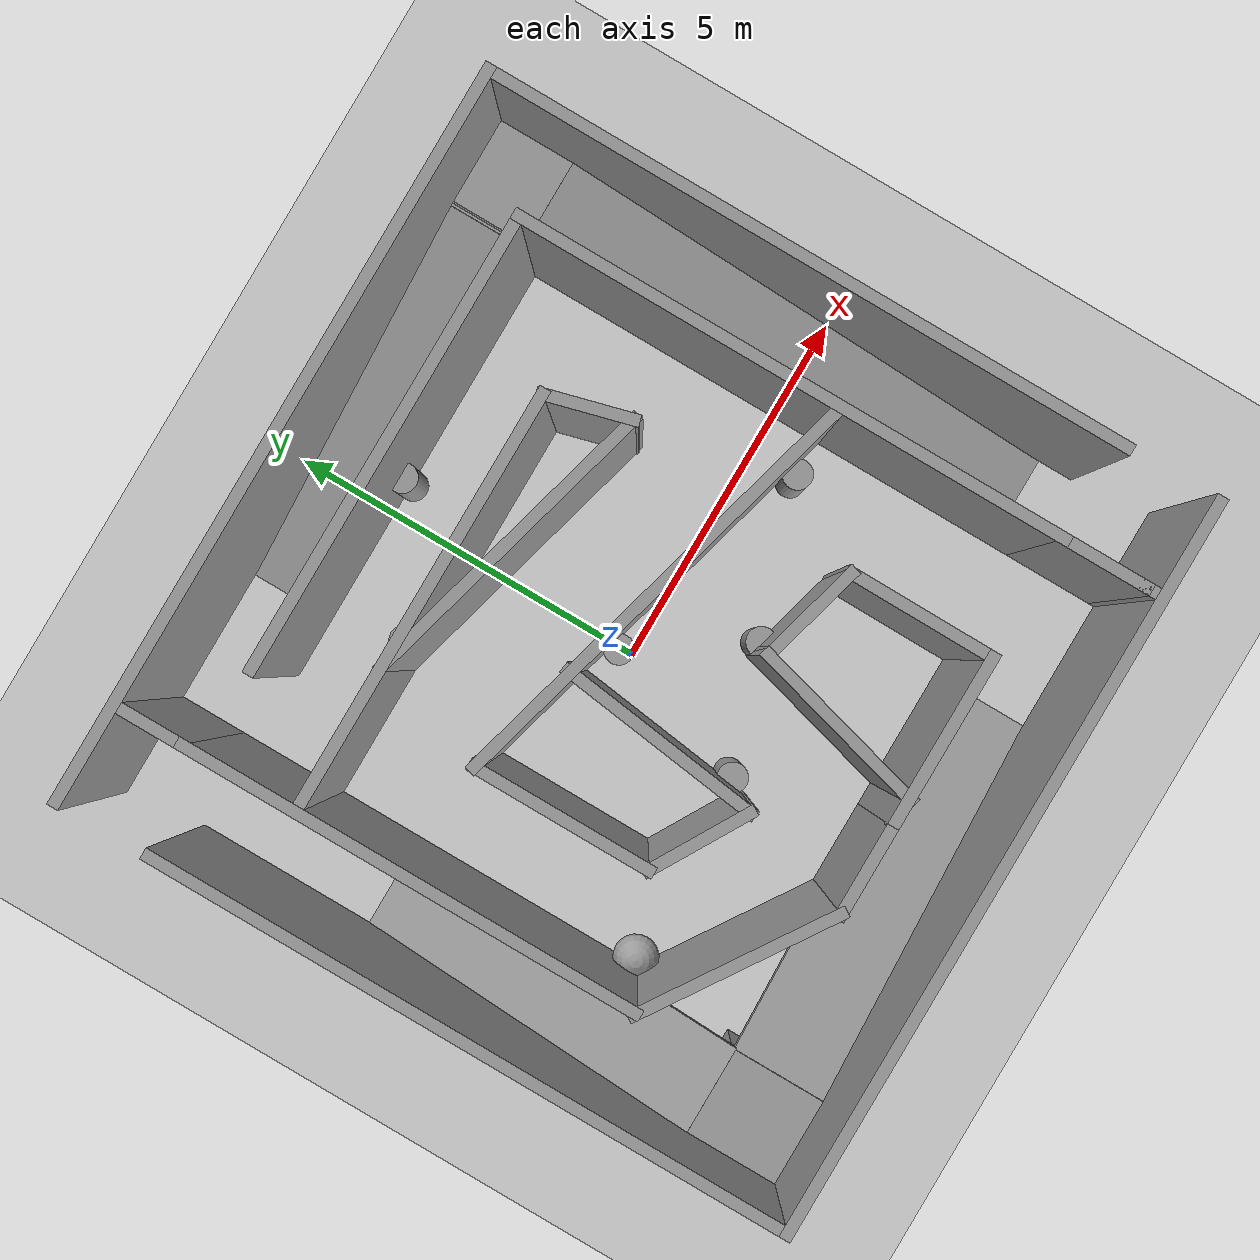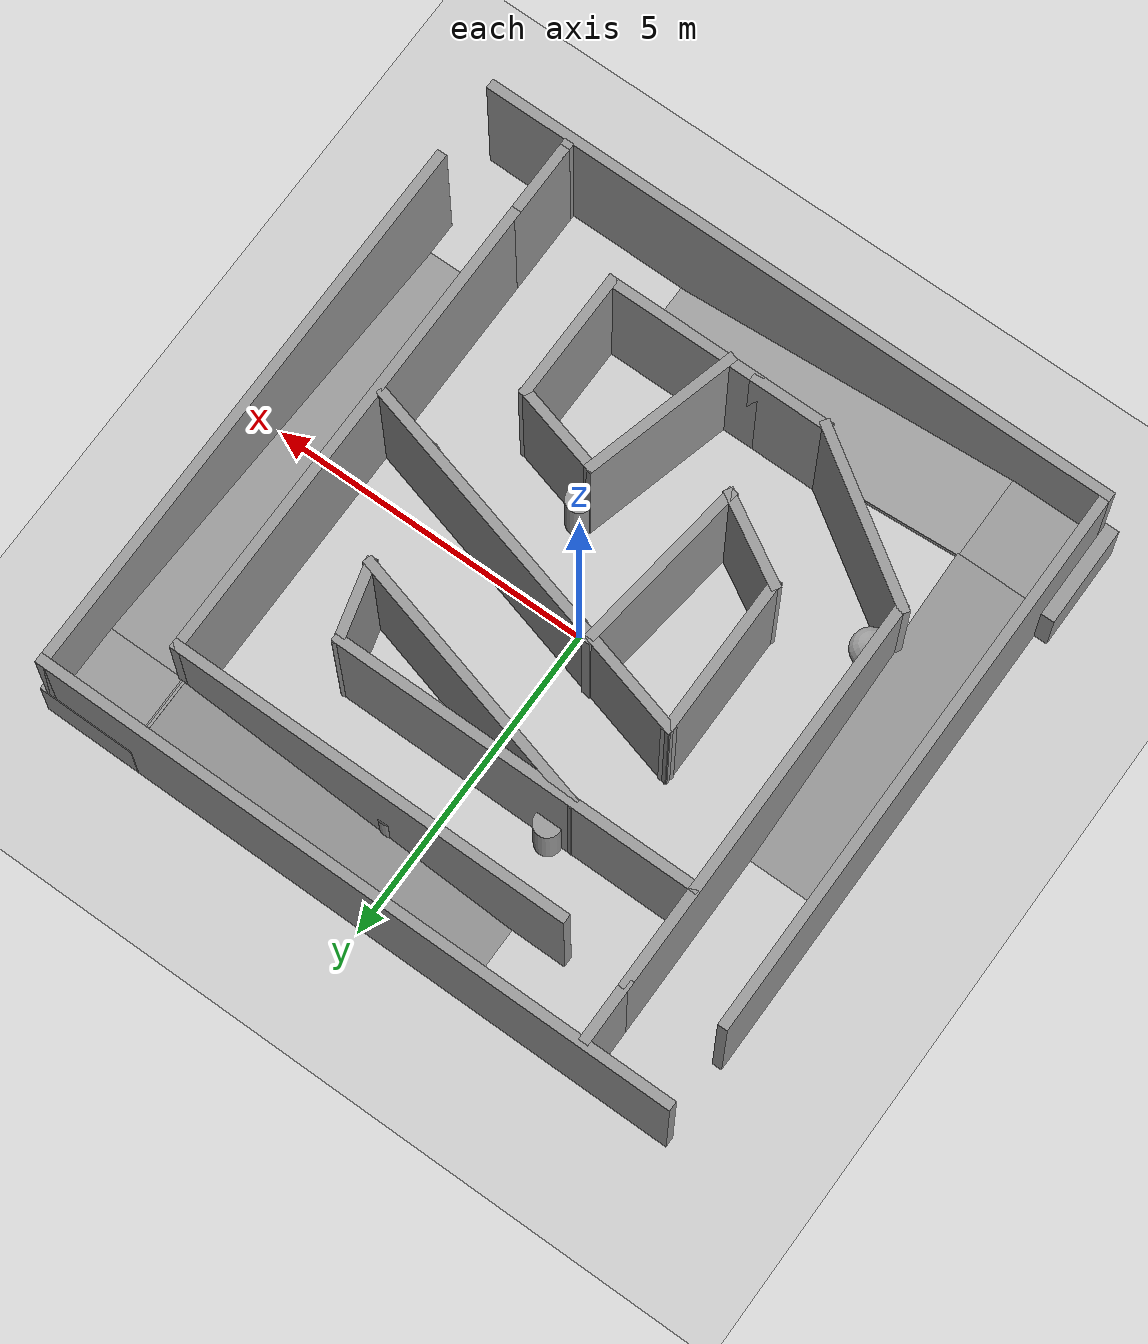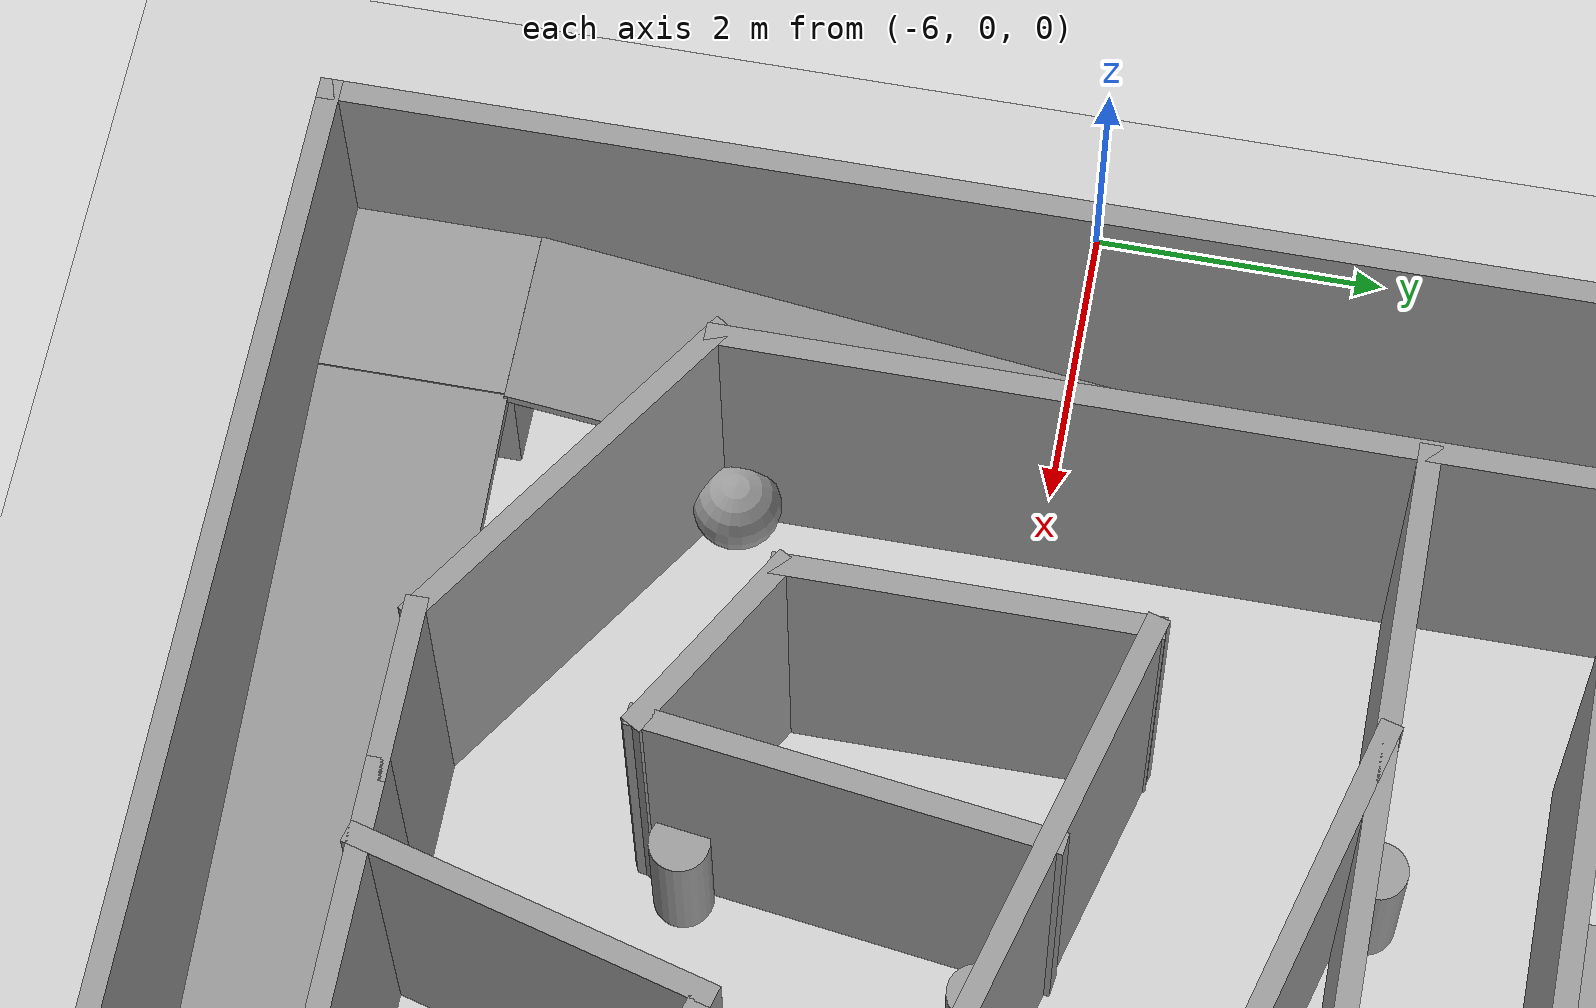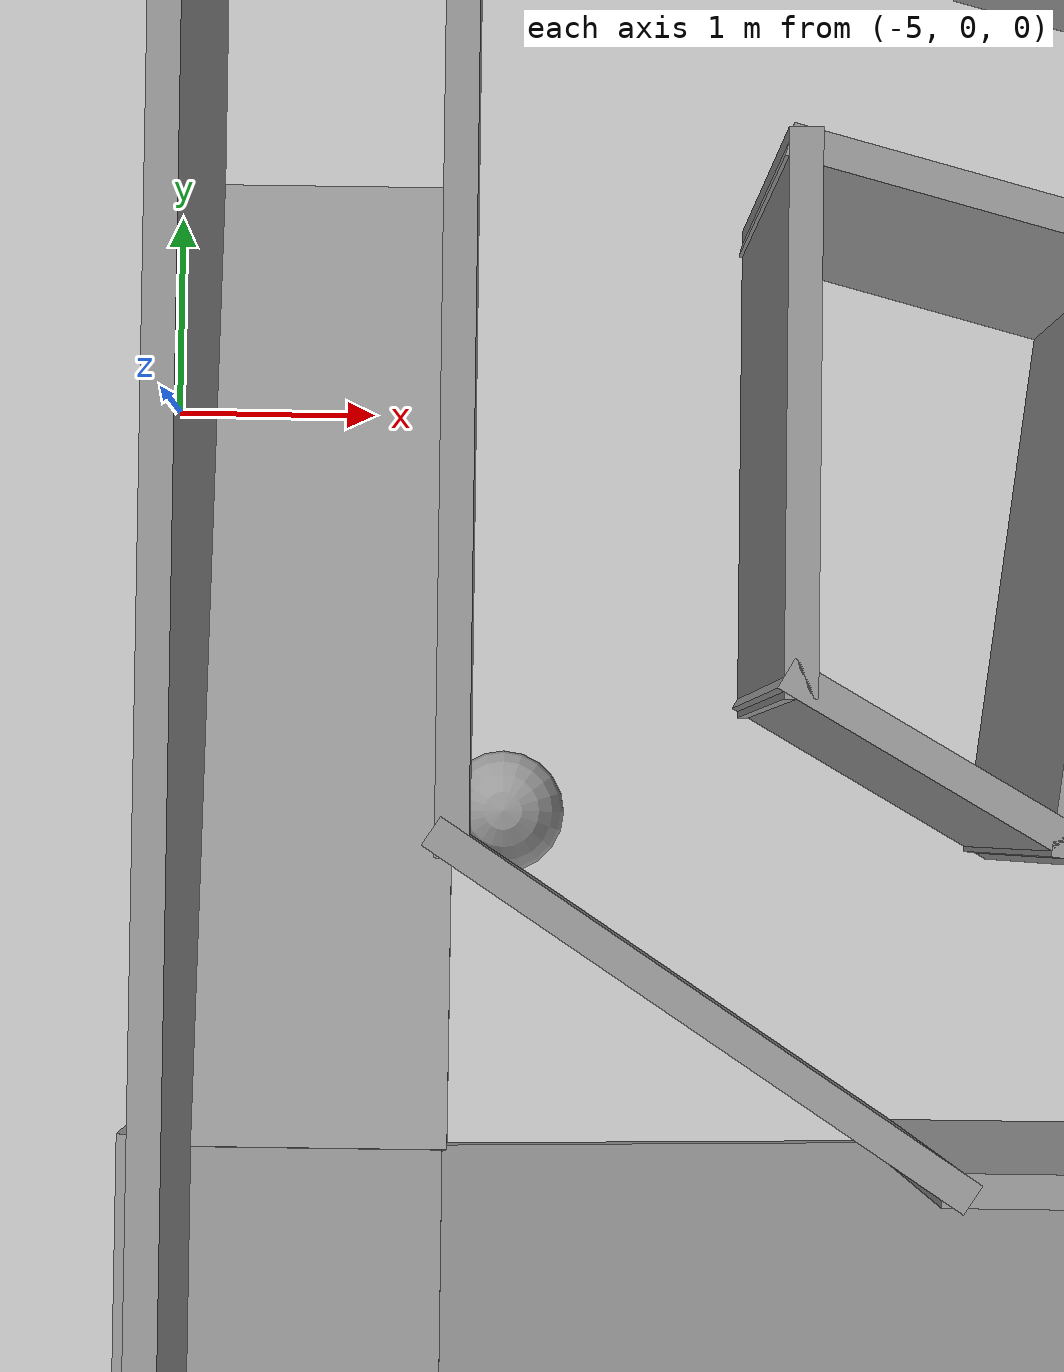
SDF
<sdf version="1.7">
 <world name="default">
  <plugin name="gazebo_link_attacher" filename="libgazebo_link_attacher.so"/>
  <light name="sun" type="directional">
   <pose>0 0 10 0 -0 0</pose>
   <diffuse>0.8 0.8 0.8 1</diffuse>
   <specular>0.2 0.2 0.2 1</specular>
   <attenuation>
    <range>1000</range>
    <constant>0.9</constant>
    <linear>0.01</linear>
    <quadratic>0.001</quadratic>
   </attenuation>
   <direction>-0.5 0.1 -0.9</direction>
   <spot><inner_angle>0</inner_angle><outer_angle>0</outer_angle><falloff>0</falloff></spot>
  </light>
  <model name="ground_plane">
   <static>1</static>
   <link name="link">
    <collision name="collision">
     <geometry><plane><normal>0 0 1</normal><size>100 100</size></plane></geometry>
     <surface>
      <contact><collide_bitmask>65535</collide_bitmask></contact>
      <friction><ode><mu>100</mu><mu2>50</mu2></ode></friction>
     </surface>
    </collision>
    <visual name="visual">
     <cast_shadows>0</cast_shadows>
     <geometry><plane><normal>0 0 1</normal><size>100 100</size></plane></geometry>
     <material>
      <script><uri>file://media/materials/scripts/gazebo.material</uri><name>Gazebo/Grey</name></script>
     </material>
    </visual>
   </link>
  </model>
  <gravity>0 0 -9.8</gravity>
  <magnetic_field>6e-06 2.3e-05 -4.2e-05</magnetic_field>
  <atmosphere type="adiabatic"/>
  <physics type="ode">
   <max_step_size>0.001</max_step_size>
   <real_time_factor>1</real_time_factor>
   <real_time_update_rate>1000</real_time_update_rate>
  </physics>
  <scene><ambient>0.4 0.4 0.4 1</ambient><background>0.7 0.7 0.7 1</background><shadows>1</shadows></scene>
  <audio><device>default</device></audio>
  <spherical_coordinates>
   <surface_model>EARTH_WGS84</surface_model>
   <latitude_deg>0</latitude_deg>
   <longitude_deg>0</longitude_deg>
   <elevation>0</elevation>
   <heading_deg>0</heading_deg>
  </spherical_coordinates>
  <model name="map10x10">
   <pose>0.061304 -0.054192 0 0 -0 0</pose>
   <link name="Stairs_11">
    <visual name="Stairs_11_Visual_0">
     <pose>-4.25677 -0.018818 0.003333 0 -0 0</pose>
     <geometry><box><size>1.142 0.024033 0.006667</size></box></geometry>
     <material>
      <script><uri>file://media/materials/scripts/gazebo.material</uri><name>Gazebo/Grey</name></script>
      <ambient>1 1 1 1</ambient>
     </material>
     <meta><layer>0</layer></meta>
    </visual>
    <collision name="Stairs_11_Collision_0">
     <geometry><box><size>1.142 0.024033 0.006667</size></box></geometry>
     <pose>-4.25677 -0.018818 0.003333 0 -0 0</pose>
    </collision>
    <visual name="Stairs_11_Visual_1">
     <pose>-4.25677 -0.042851 0.01 0 -0 0</pose>
     <geometry><box><size>1.142 0.024033 0.006667</size></box></geometry>
     <material>
      <script><uri>file://media/materials/scripts/gazebo.material</uri><name>Gazebo/Grey</name></script>
      <ambient>1 1 1 1</ambient>
     </material>
     <meta><layer>0</layer></meta>
    </visual>
    <collision name="Stairs_11_Collision_1">
     <geometry><box><size>1.142 0.024033 0.006667</size></box></geometry>
     <pose>-4.25677 -0.042851 0.01 0 -0 0</pose>
    </collision>
    <visual name="Stairs_11_Visual_2">
     <pose>-4.25677 -0.066885 0.016667 0 -0 0</pose>
     <geometry><box><size>1.142 0.024033 0.006667</size></box></geometry>
     <material>
      <script><uri>file://media/materials/scripts/gazebo.material</uri><name>Gazebo/Grey</name></script>
      <ambient>1 1 1 1</ambient>
     </material>
     <meta><layer>0</layer></meta>
    </visual>
    <collision name="Stairs_11_Collision_2">
     <geometry><box><size>1.142 0.024033 0.006667</size></box></geometry>
     <pose>-4.25677 -0.066885 0.016667 0 -0 0</pose>
    </collision>
    <visual name="Stairs_11_Visual_3">
     <pose>-4.25677 -0.090918 0.023333 0 -0 0</pose>
     <geometry><box><size>1.142 0.024033 0.006667</size></box></geometry>
     <material>
      <script><uri>file://media/materials/scripts/gazebo.material</uri><name>Gazebo/Grey</name></script>
      <ambient>1 1 1 1</ambient>
     </material>
     <meta><layer>0</layer></meta>
    </visual>
    <collision name="Stairs_11_Collision_3">
     <geometry><box><size>1.142 0.024033 0.006667</size></box></geometry>
     <pose>-4.25677 -0.090918 0.023333 0 -0 0</pose>
    </collision>
    <visual name="Stairs_11_Visual_4">
     <pose>-4.25677 -0.114951 0.03 0 -0 0</pose>
     <geometry><box><size>1.142 0.024033 0.006667</size></box></geometry>
     <material>
      <script><uri>file://media/materials/scripts/gazebo.material</uri><name>Gazebo/Grey</name></script>
      <ambient>1 1 1 1</ambient>
     </material>
     <meta><layer>0</layer></meta>
    </visual>
    <collision name="Stairs_11_Collision_4">
     <geometry><box><size>1.142 0.024033 0.006667</size></box></geometry>
     <pose>-4.25677 -0.114951 0.03 0 -0 0</pose>
    </collision>
    <visual name="Stairs_11_Visual_5">
     <pose>-4.25677 -0.138984 0.036667 0 -0 0</pose>
     <geometry><box><size>1.142 0.024033 0.006667</size></box></geometry>
     <material>
      <script><uri>file://media/materials/scripts/gazebo.material</uri><name>Gazebo/Grey</name></script>
      <ambient>1 1 1 1</ambient>
     </material>
     <meta><layer>0</layer></meta>
    </visual>
    <collision name="Stairs_11_Collision_5">
     <geometry><box><size>1.142 0.024033 0.006667</size></box></geometry>
     <pose>-4.25677 -0.138984 0.036667 0 -0 0</pose>
    </collision>
    <visual name="Stairs_11_Visual_6">
     <pose>-4.25677 -0.163018 0.043333 0 -0 0</pose>
     <geometry><box><size>1.142 0.024033 0.006667</size></box></geometry>
     <material>
      <script><uri>file://media/materials/scripts/gazebo.material</uri><name>Gazebo/Grey</name></script>
      <ambient>1 1 1 1</ambient>
     </material>
     <meta><layer>0</layer></meta>
    </visual>
    <collision name="Stairs_11_Collision_6">
     <geometry><box><size>1.142 0.024033 0.006667</size></box></geometry>
     <pose>-4.25677 -0.163018 0.043333 0 -0 0</pose>
    </collision>
    <visual name="Stairs_11_Visual_7">
     <pose>-4.25677 -0.187051 0.05 0 -0 0</pose>
     <geometry><box><size>1.142 0.024033 0.006667</size></box></geometry>
     <material>
      <script><uri>file://media/materials/scripts/gazebo.material</uri><name>Gazebo/Grey</name></script>
      <ambient>1 1 1 1</ambient>
     </material>
     <meta><layer>0</layer></meta>
    </visual>
    <collision name="Stairs_11_Collision_7">
     <geometry><box><size>1.142 0.024033 0.006667</size></box></geometry>
     <pose>-4.25677 -0.187051 0.05 0 -0 0</pose>
    </collision>
    <visual name="Stairs_11_Visual_8">
     <pose>-4.25677 -0.211084 0.056667 0 -0 0</pose>
     <geometry><box><size>1.142 0.024033 0.006667</size></box></geometry>
     <material>
      <script><uri>file://media/materials/scripts/gazebo.material</uri><name>Gazebo/Grey</name></script>
      <ambient>1 1 1 1</ambient>
     </material>
     <meta><layer>0</layer></meta>
    </visual>
    <collision name="Stairs_11_Collision_8">
     <geometry><box><size>1.142 0.024033 0.006667</size></box></geometry>
     <pose>-4.25677 -0.211084 0.056667 0 -0 0</pose>
    </collision>
    <visual name="Stairs_11_Visual_9">
     <pose>-4.25677 -0.235118 0.063333 0 -0 0</pose>
     <geometry><box><size>1.142 0.024033 0.006667</size></box></geometry>
     <material>
      <script><uri>file://media/materials/scripts/gazebo.material</uri><name>Gazebo/Grey</name></script>
      <ambient>1 1 1 1</ambient>
     </material>
     <meta><layer>0</layer></meta>
    </visual>
    <collision name="Stairs_11_Collision_9">
     <geometry><box><size>1.142 0.024033 0.006667</size></box></geometry>
     <pose>-4.25677 -0.235118 0.063333 0 -0 0</pose>
    </collision>
    <visual name="Stairs_11_Visual_10">
     <pose>-4.25677 -0.259151 0.07 0 -0 0</pose>
     <geometry><box><size>1.142 0.024033 0.006667</size></box></geometry>
     <material>
      <script><uri>file://media/materials/scripts/gazebo.material</uri><name>Gazebo/Grey</name></script>
      <ambient>1 1 1 1</ambient>
     </material>
     <meta><layer>0</layer></meta>
    </visual>
    <collision name="Stairs_11_Collision_10">
     <geometry><box><size>1.142 0.024033 0.006667</size></box></geometry>
     <pose>-4.25677 -0.259151 0.07 0 -0 0</pose>
    </collision>
    <visual name="Stairs_11_Visual_11">
     <pose>-4.25677 -0.283184 0.076667 0 -0 0</pose>
     <geometry><box><size>1.142 0.024033 0.006667</size></box></geometry>
     <material>
      <script><uri>file://media/materials/scripts/gazebo.material</uri><name>Gazebo/Grey</name></script>
      <ambient>1 1 1 1</ambient>
     </material>
     <meta><layer>0</layer></meta>
    </visual>
    <collision name="Stairs_11_Collision_11">
     <geometry><box><size>1.142 0.024033 0.006667</size></box></geometry>
     <pose>-4.25677 -0.283184 0.076667 0 -0 0</pose>
    </collision>
    <visual name="Stairs_11_Visual_12">
     <pose>-4.25677 -0.307218 0.083333 0 -0 0</pose>
     <geometry><box><size>1.142 0.024033 0.006667</size></box></geometry>
     <material>
      <script><uri>file://media/materials/scripts/gazebo.material</uri><name>Gazebo/Grey</name></script>
      <ambient>1 1 1 1</ambient>
     </material>
     <meta><layer>0</layer></meta>
    </visual>
    <collision name="Stairs_11_Collision_12">
     <geometry><box><size>1.142 0.024033 0.006667</size></box></geometry>
     <pose>-4.25677 -0.307218 0.083333 0 -0 0</pose>
    </collision>
    <visual name="Stairs_11_Visual_13">
     <pose>-4.25677 -0.331251 0.09 0 -0 0</pose>
     <geometry><box><size>1.142 0.024033 0.006667</size></box></geometry>
     <material>
      <script><uri>file://media/materials/scripts/gazebo.material</uri><name>Gazebo/Grey</name></script>
      <ambient>1 1 1 1</ambient>
     </material>
     <meta><layer>0</layer></meta>
    </visual>
    <collision name="Stairs_11_Collision_13">
     <geometry><box><size>1.142 0.024033 0.006667</size></box></geometry>
     <pose>-4.25677 -0.331251 0.09 0 -0 0</pose>
    </collision>
    <visual name="Stairs_11_Visual_14">
     <pose>-4.25677 -0.355284 0.096667 0 -0 0</pose>
     <geometry><box><size>1.142 0.024033 0.006667</size></box></geometry>
     <material>
      <script><uri>file://media/materials/scripts/gazebo.material</uri><name>Gazebo/Grey</name></script>
      <ambient>1 1 1 1</ambient>
     </material>
     <meta><layer>0</layer></meta>
    </visual>
    <collision name="Stairs_11_Collision_14">
     <geometry><box><size>1.142 0.024033 0.006667</size></box></geometry>
     <pose>-4.25677 -0.355284 0.096667 0 -0 0</pose>
    </collision>
    <visual name="Stairs_11_Visual_15">
     <pose>-4.25677 -0.379318 0.103333 0 -0 0</pose>
     <geometry><box><size>1.142 0.024033 0.006667</size></box></geometry>
     <material>
      <script><uri>file://media/materials/scripts/gazebo.material</uri><name>Gazebo/Grey</name></script>
      <ambient>1 1 1 1</ambient>
     </material>
     <meta><layer>0</layer></meta>
    </visual>
    <collision name="Stairs_11_Collision_15">
     <geometry><box><size>1.142 0.024033 0.006667</size></box></geometry>
     <pose>-4.25677 -0.379318 0.103333 0 -0 0</pose>
    </collision>
    <visual name="Stairs_11_Visual_16">
     <pose>-4.25677 -0.403351 0.11 0 -0 0</pose>
     <geometry><box><size>1.142 0.024033 0.006667</size></box></geometry>
     <material>
      <script><uri>file://media/materials/scripts/gazebo.material</uri><name>Gazebo/Grey</name></script>
      <ambient>1 1 1 1</ambient>
     </material>
     <meta><layer>0</layer></meta>
    </visual>
    <collision name="Stairs_11_Collision_16">
     <geometry><box><size>1.142 0.024033 0.006667</size></box></geometry>
     <pose>-4.25677 -0.403351 0.11 0 -0 0</pose>
    </collision>
    <visual name="Stairs_11_Visual_17">
     <pose>-4.25677 -0.427384 0.116667 0 -0 0</pose>
     <geometry><box><size>1.142 0.024033 0.006667</size></box></geometry>
     <material>
      <script><uri>file://media/materials/scripts/gazebo.material</uri><name>Gazebo/Grey</name></script>
      <ambient>1 1 1 1</ambient>
     </material>
     <meta><layer>0</layer></meta>
    </visual>
    <collision name="Stairs_11_Collision_17">
     <geometry><box><size>1.142 0.024033 0.006667</size></box></geometry>
     <pose>-4.25677 -0.427384 0.116667 0 -0 0</pose>
    </collision>
    <visual name="Stairs_11_Visual_18">
     <pose>-4.25677 -0.451418 0.123333 0 -0 0</pose>
     <geometry><box><size>1.142 0.024033 0.006667</size></box></geometry>
     <material>
      <script><uri>file://media/materials/scripts/gazebo.material</uri><name>Gazebo/Grey</name></script>
      <ambient>1 1 1 1</ambient>
     </material>
     <meta><layer>0</layer></meta>
    </visual>
    <collision name="Stairs_11_Collision_18">
     <geometry><box><size>1.142 0.024033 0.006667</size></box></geometry>
     <pose>-4.25677 -0.451418 0.123333 0 -0 0</pose>
    </collision>
    <visual name="Stairs_11_Visual_19">
     <pose>-4.25677 -0.475451 0.13 0 -0 0</pose>
     <geometry><box><size>1.142 0.024033 0.006667</size></box></geometry>
     <material>
      <script><uri>file://media/materials/scripts/gazebo.material</uri><name>Gazebo/Grey</name></script>
      <ambient>1 1 1 1</ambient>
     </material>
     <meta><layer>0</layer></meta>
    </visual>
    <collision name="Stairs_11_Collision_19">
     <geometry><box><size>1.142 0.024033 0.006667</size></box></geometry>
     <pose>-4.25677 -0.475451 0.13 0 -0 0</pose>
    </collision>
    <visual name="Stairs_11_Visual_20">
     <pose>-4.25677 -0.499484 0.136667 0 -0 0</pose>
     <geometry><box><size>1.142 0.024033 0.006667</size></box></geometry>
     <material>
      <script><uri>file://media/materials/scripts/gazebo.material</uri><name>Gazebo/Grey</name></script>
      <ambient>1 1 1 1</ambient>
     </material>
     <meta><layer>0</layer></meta>
    </visual>
    <collision name="Stairs_11_Collision_20">
     <geometry><box><size>1.142 0.024033 0.006667</size></box></geometry>
     <pose>-4.25677 -0.499484 0.136667 0 -0 0</pose>
    </collision>
    <visual name="Stairs_11_Visual_21">
     <pose>-4.25677 -0.523518 0.143333 0 -0 0</pose>
     <geometry><box><size>1.142 0.024033 0.006667</size></box></geometry>
     <material>
      <script><uri>file://media/materials/scripts/gazebo.material</uri><name>Gazebo/Grey</name></script>
      <ambient>1 1 1 1</ambient>
     </material>
     <meta><layer>0</layer></meta>
    </visual>
    <collision name="Stairs_11_Collision_21">
     <geometry><box><size>1.142 0.024033 0.006667</size></box></geometry>
     <pose>-4.25677 -0.523518 0.143333 0 -0 0</pose>
    </collision>
    <visual name="Stairs_11_Visual_22">
     <pose>-4.25677 -0.547551 0.15 0 -0 0</pose>
     <geometry><box><size>1.142 0.024033 0.006667</size></box></geometry>
     <material>
      <script><uri>file://media/materials/scripts/gazebo.material</uri><name>Gazebo/Grey</name></script>
      <ambient>1 1 1 1</ambient>
     </material>
     <meta><layer>0</layer></meta>
    </visual>
    <collision name="Stairs_11_Collision_22">
     <geometry><box><size>1.142 0.024033 0.006667</size></box></geometry>
     <pose>-4.25677 -0.547551 0.15 0 -0 0</pose>
    </collision>
    <visual name="Stairs_11_Visual_23">
     <pose>-4.25677 -0.571584 0.156667 0 -0 0</pose>
     <geometry><box><size>1.142 0.024033 0.006667</size></box></geometry>
     <material>
      <script><uri>file://media/materials/scripts/gazebo.material</uri><name>Gazebo/Grey</name></script>
      <ambient>1 1 1 1</ambient>
     </material>
     <meta><layer>0</layer></meta>
    </visual>
    <collision name="Stairs_11_Collision_23">
     <geometry><box><size>1.142 0.024033 0.006667</size></box></geometry>
     <pose>-4.25677 -0.571584 0.156667 0 -0 0</pose>
    </collision>
    <visual name="Stairs_11_Visual_24">
     <pose>-4.25677 -0.595618 0.163333 0 -0 0</pose>
     <geometry><box><size>1.142 0.024033 0.006667</size></box></geometry>
     <material>
      <script><uri>file://media/materials/scripts/gazebo.material</uri><name>Gazebo/Grey</name></script>
      <ambient>1 1 1 1</ambient>
     </material>
     <meta><layer>0</layer></meta>
    </visual>
    <collision name="Stairs_11_Collision_24">
     <geometry><box><size>1.142 0.024033 0.006667</size></box></geometry>
     <pose>-4.25677 -0.595618 0.163333 0 -0 0</pose>
    </collision>
    <visual name="Stairs_11_Visual_25">
     <pose>-4.25677 -0.619651 0.17 0 -0 0</pose>
     <geometry><box><size>1.142 0.024033 0.006667</size></box></geometry>
     <material>
      <script><uri>file://media/materials/scripts/gazebo.material</uri><name>Gazebo/Grey</name></script>
      <ambient>1 1 1 1</ambient>
     </material>
     <meta><layer>0</layer></meta>
    </visual>
    <collision name="Stairs_11_Collision_25">
     <geometry><box><size>1.142 0.024033 0.006667</size></box></geometry>
     <pose>-4.25677 -0.619651 0.17 0 -0 0</pose>
    </collision>
    <visual name="Stairs_11_Visual_26">
     <pose>-4.25677 -0.643685 0.176667 0 -0 0</pose>
     <geometry><box><size>1.142 0.024033 0.006667</size></box></geometry>
     <material>
      <script><uri>file://media/materials/scripts/gazebo.material</uri><name>Gazebo/Grey</name></script>
      <ambient>1 1 1 1</ambient>
     </material>
     <meta><layer>0</layer></meta>
    </visual>
    <collision name="Stairs_11_Collision_26">
     <geometry><box><size>1.142 0.024033 0.006667</size></box></geometry>
     <pose>-4.25677 -0.643685 0.176667 0 -0 0</pose>
    </collision>
    <visual name="Stairs_11_Visual_27">
     <pose>-4.25677 -0.667718 0.183333 0 -0 0</pose>
     <geometry><box><size>1.142 0.024033 0.006667</size></box></geometry>
     <material>
      <script><uri>file://media/materials/scripts/gazebo.material</uri><name>Gazebo/Grey</name></script>
      <ambient>1 1 1 1</ambient>
     </material>
     <meta><layer>0</layer></meta>
    </visual>
    <collision name="Stairs_11_Collision_27">
     <geometry><box><size>1.142 0.024033 0.006667</size></box></geometry>
     <pose>-4.25677 -0.667718 0.183333 0 -0 0</pose>
    </collision>
    <visual name="Stairs_11_Visual_28">
     <pose>-4.25677 -0.691751 0.19 0 -0 0</pose>
     <geometry><box><size>1.142 0.024033 0.006667</size></box></geometry>
     <material>
      <script><uri>file://media/materials/scripts/gazebo.material</uri><name>Gazebo/Grey</name></script>
      <ambient>1 1 1 1</ambient>
     </material>
     <meta><layer>0</layer></meta>
    </visual>
    <collision name="Stairs_11_Collision_28">
     <geometry><box><size>1.142 0.024033 0.006667</size></box></geometry>
     <pose>-4.25677 -0.691751 0.19 0 -0 0</pose>
    </collision>
    <visual name="Stairs_11_Visual_29">
     <pose>-4.25677 -0.715784 0.196667 0 -0 0</pose>
     <geometry><box><size>1.142 0.024033 0.006667</size></box></geometry>
     <material>
      <script><uri>file://media/materials/scripts/gazebo.material</uri><name>Gazebo/Grey</name></script>
      <ambient>1 1 1 1</ambient>
     </material>
     <meta><layer>0</layer></meta>
    </visual>
    <collision name="Stairs_11_Collision_29">
     <geometry><box><size>1.142 0.024033 0.006667</size></box></geometry>
     <pose>-4.25677 -0.715784 0.196667 0 -0 0</pose>
    </collision>
    <visual name="Stairs_11_Visual_30">
     <pose>-4.25677 -0.739818 0.203333 0 -0 0</pose>
     <geometry><box><size>1.142 0.024033 0.006667</size></box></geometry>
     <material>
      <script><uri>file://media/materials/scripts/gazebo.material</uri><name>Gazebo/Grey</name></script>
      <ambient>1 1 1 1</ambient>
     </material>
     <meta><layer>0</layer></meta>
    </visual>
    <collision name="Stairs_11_Collision_30">
     <geometry><box><size>1.142 0.024033 0.006667</size></box></geometry>
     <pose>-4.25677 -0.739818 0.203333 0 -0 0</pose>
    </collision>
    <visual name="Stairs_11_Visual_31">
     <pose>-4.25677 -0.763851 0.21 0 -0 0</pose>
     <geometry><box><size>1.142 0.024033 0.006667</size></box></geometry>
     <material>
      <script><uri>file://media/materials/scripts/gazebo.material</uri><name>Gazebo/Grey</name></script>
      <ambient>1 1 1 1</ambient>
     </material>
     <meta><layer>0</layer></meta>
    </visual>
    <collision name="Stairs_11_Collision_31">
     <geometry><box><size>1.142 0.024033 0.006667</size></box></geometry>
     <pose>-4.25677 -0.763851 0.21 0 -0 0</pose>
    </collision>
    <visual name="Stairs_11_Visual_32">
     <pose>-4.25677 -0.787884 0.216667 0 -0 0</pose>
     <geometry><box><size>1.142 0.024033 0.006667</size></box></geometry>
     <material>
      <script><uri>file://media/materials/scripts/gazebo.material</uri><name>Gazebo/Grey</name></script>
      <ambient>1 1 1 1</ambient>
     </material>
     <meta><layer>0</layer></meta>
    </visual>
    <collision name="Stairs_11_Collision_32">
     <geometry><box><size>1.142 0.024033 0.006667</size></box></geometry>
     <pose>-4.25677 -0.787884 0.216667 0 -0 0</pose>
    </collision>
    <visual name="Stairs_11_Visual_33">
     <pose>-4.25677 -0.811918 0.223333 0 -0 0</pose>
     <geometry><box><size>1.142 0.024033 0.006667</size></box></geometry>
     <material>
      <script><uri>file://media/materials/scripts/gazebo.material</uri><name>Gazebo/Grey</name></script>
      <ambient>1 1 1 1</ambient>
     </material>
     <meta><layer>0</layer></meta>
    </visual>
    <collision name="Stairs_11_Collision_33">
     <geometry><box><size>1.142 0.024033 0.006667</size></box></geometry>
     <pose>-4.25677 -0.811918 0.223333 0 -0 0</pose>
    </collision>
    <visual name="Stairs_11_Visual_34">
     <pose>-4.25677 -0.835951 0.23 0 -0 0</pose>
     <geometry><box><size>1.142 0.024033 0.006667</size></box></geometry>
     <material>
      <script><uri>file://media/materials/scripts/gazebo.material</uri><name>Gazebo/Grey</name></script>
      <ambient>1 1 1 1</ambient>
     </material>
     <meta><layer>0</layer></meta>
    </visual>
    <collision name="Stairs_11_Collision_34">
     <geometry><box><size>1.142 0.024033 0.006667</size></box></geometry>
     <pose>-4.25677 -0.835951 0.23 0 -0 0</pose>
    </collision>
    <visual name="Stairs_11_Visual_35">
     <pose>-4.25677 -0.859985 0.236667 0 -0 0</pose>
     <geometry><box><size>1.142 0.024033 0.006667</size></box></geometry>
     <material>
      <script><uri>file://media/materials/scripts/gazebo.material</uri><name>Gazebo/Grey</name></script>
      <ambient>1 1 1 1</ambient>
     </material>
     <meta><layer>0</layer></meta>
    </visual>
    <collision name="Stairs_11_Collision_35">
     <geometry><box><size>1.142 0.024033 0.006667</size></box></geometry>
     <pose>-4.25677 -0.859985 0.236667 0 -0 0</pose>
    </collision>
    <visual name="Stairs_11_Visual_36">
     <pose>-4.25677 -0.884018 0.243333 0 -0 0</pose>
     <geometry><box><size>1.142 0.024033 0.006667</size></box></geometry>
     <material>
      <script><uri>file://media/materials/scripts/gazebo.material</uri><name>Gazebo/Grey</name></script>
      <ambient>1 1 1 1</ambient>
     </material>
     <meta><layer>0</layer></meta>
    </visual>
    <collision name="Stairs_11_Collision_36">
     <geometry><box><size>1.142 0.024033 0.006667</size></box></geometry>
     <pose>-4.25677 -0.884018 0.243333 0 -0 0</pose>
    </collision>
    <visual name="Stairs_11_Visual_37">
     <pose>-4.25677 -0.908051 0.25 0 -0 0</pose>
     <geometry><box><size>1.142 0.024033 0.006667</size></box></geometry>
     <material>
      <script><uri>file://media/materials/scripts/gazebo.material</uri><name>Gazebo/Grey</name></script>
      <ambient>1 1 1 1</ambient>
     </material>
     <meta><layer>0</layer></meta>
    </visual>
    <collision name="Stairs_11_Collision_37">
     <geometry><box><size>1.142 0.024033 0.006667</size></box></geometry>
     <pose>-4.25677 -0.908051 0.25 0 -0 0</pose>
    </collision>
    <visual name="Stairs_11_Visual_38">
     <pose>-4.25677 -0.932084 0.256667 0 -0 0</pose>
     <geometry><box><size>1.142 0.024033 0.006667</size></box></geometry>
     <material>
      <script><uri>file://media/materials/scripts/gazebo.material</uri><name>Gazebo/Grey</name></script>
      <ambient>1 1 1 1</ambient>
     </material>
     <meta><layer>0</layer></meta>
    </visual>
    <collision name="Stairs_11_Collision_38">
     <geometry><box><size>1.142 0.024033 0.006667</size></box></geometry>
     <pose>-4.25677 -0.932084 0.256667 0 -0 0</pose>
    </collision>
    <visual name="Stairs_11_Visual_39">
     <pose>-4.25677 -0.956118 0.263333 0 -0 0</pose>
     <geometry><box><size>1.142 0.024033 0.006667</size></box></geometry>
     <material>
      <script><uri>file://media/materials/scripts/gazebo.material</uri><name>Gazebo/Grey</name></script>
      <ambient>1 1 1 1</ambient>
     </material>
     <meta><layer>0</layer></meta>
    </visual>
    <collision name="Stairs_11_Collision_39">
     <geometry><box><size>1.142 0.024033 0.006667</size></box></geometry>
     <pose>-4.25677 -0.956118 0.263333 0 -0 0</pose>
    </collision>
    <visual name="Stairs_11_Visual_40">
     <pose>-4.25677 -0.980151 0.27 0 -0 0</pose>
     <geometry><box><size>1.142 0.024033 0.006667</size></box></geometry>
     <material>
      <script><uri>file://media/materials/scripts/gazebo.material</uri><name>Gazebo/Grey</name></script>
      <ambient>1 1 1 1</ambient>
     </material>
     <meta><layer>0</layer></meta>
    </visual>
    <collision name="Stairs_11_Collision_40">
     <geometry><box><size>1.142 0.024033 0.006667</size></box></geometry>
     <pose>-4.25677 -0.980151 0.27 0 -0 0</pose>
    </collision>
    <visual name="Stairs_11_Visual_41">
     <pose>-4.25677 -1.00418 0.276667 0 -0 0</pose>
     <geometry><box><size>1.142 0.024033 0.006667</size></box></geometry>
     <material>
      <script><uri>file://media/materials/scripts/gazebo.material</uri><name>Gazebo/Grey</name></script>
      <ambient>1 1 1 1</ambient>
     </material>
     <meta><layer>0</layer></meta>
    </visual>
    <collision name="Stairs_11_Collision_41">
     <geometry><box><size>1.142 0.024033 0.006667</size></box></geometry>
     <pose>-4.25677 -1.00418 0.276667 0 -0 0</pose>
    </collision>
    <visual name="Stairs_11_Visual_42">
     <pose>-4.25677 -1.02822 0.283333 0 -0 0</pose>
     <geometry><box><size>1.142 0.024033 0.006667</size></box></geometry>
     <material>
      <script><uri>file://media/materials/scripts/gazebo.material</uri><name>Gazebo/Grey</name></script>
      <ambient>1 1 1 1</ambient>
     </material>
     <meta><layer>0</layer></meta>
    </visual>
    <collision name="Stairs_11_Collision_42">
     <geometry><box><size>1.142 0.024033 0.006667</size></box></geometry>
     <pose>-4.25677 -1.02822 0.283333 0 -0 0</pose>
    </collision>
    <visual name="Stairs_11_Visual_43">
     <pose>-4.25677 -1.05225 0.29 0 -0 0</pose>
     <geometry><box><size>1.142 0.024033 0.006667</size></box></geometry>
     <material>
      <script><uri>file://media/materials/scripts/gazebo.material</uri><name>Gazebo/Grey</name></script>
      <ambient>1 1 1 1</ambient>
     </material>
     <meta><layer>0</layer></meta>
    </visual>
    <collision name="Stairs_11_Collision_43">
     <geometry><box><size>1.142 0.024033 0.006667</size></box></geometry>
     <pose>-4.25677 -1.05225 0.29 0 -0 0</pose>
    </collision>
    <visual name="Stairs_11_Visual_44">
     <pose>-4.25677 -1.07628 0.296667 0 -0 0</pose>
     <geometry><box><size>1.142 0.024033 0.006667</size></box></geometry>
     <material>
      <script><uri>file://media/materials/scripts/gazebo.material</uri><name>Gazebo/Grey</name></script>
      <ambient>1 1 1 1</ambient>
     </material>
     <meta><layer>0</layer></meta>
    </visual>
    <collision name="Stairs_11_Collision_44">
     <geometry><box><size>1.142 0.024033 0.006667</size></box></geometry>
     <pose>-4.25677 -1.07628 0.296667 0 -0 0</pose>
    </collision>
    <visual name="Stairs_11_Visual_45">
     <pose>-4.25677 -1.10032 0.303333 0 -0 0</pose>
     <geometry><box><size>1.142 0.024033 0.006667</size></box></geometry>
     <material>
      <script><uri>file://media/materials/scripts/gazebo.material</uri><name>Gazebo/Grey</name></script>
      <ambient>1 1 1 1</ambient>
     </material>
     <meta><layer>0</layer></meta>
    </visual>
    <collision name="Stairs_11_Collision_45">
     <geometry><box><size>1.142 0.024033 0.006667</size></box></geometry>
     <pose>-4.25677 -1.10032 0.303333 0 -0 0</pose>
    </collision>
    <visual name="Stairs_11_Visual_46">
     <pose>-4.25677 -1.12435 0.31 0 -0 0</pose>
     <geometry><box><size>1.142 0.024033 0.006667</size></box></geometry>
     <material>
      <script><uri>file://media/materials/scripts/gazebo.material</uri><name>Gazebo/Grey</name></script>
      <ambient>1 1 1 1</ambient>
     </material>
     <meta><layer>0</layer></meta>
    </visual>
    <collision name="Stairs_11_Collision_46">
     <geometry><box><size>1.142 0.024033 0.006667</size></box></geometry>
     <pose>-4.25677 -1.12435 0.31 0 -0 0</pose>
    </collision>
    <visual name="Stairs_11_Visual_47">
     <pose>-4.25677 -1.14838 0.316667 0 -0 0</pose>
     <geometry><box><size>1.142 0.024033 0.006667</size></box></geometry>
     <material>
      <script><uri>file://media/materials/scripts/gazebo.material</uri><name>Gazebo/Grey</name></script>
      <ambient>1 1 1 1</ambient>
     </material>
     <meta><layer>0</layer></meta>
    </visual>
    <collision name="Stairs_11_Collision_47">
     <geometry><box><size>1.142 0.024033 0.006667</size></box></geometry>
     <pose>-4.25677 -1.14838 0.316667 0 -0 0</pose>
    </collision>
    <visual name="Stairs_11_Visual_48">
     <pose>-4.25677 -1.17242 0.323333 0 -0 0</pose>
     <geometry><box><size>1.142 0.024033 0.006667</size></box></geometry>
     <material>
      <script><uri>file://media/materials/scripts/gazebo.material</uri><name>Gazebo/Grey</name></script>
      <ambient>1 1 1 1</ambient>
     </material>
     <meta><layer>0</layer></meta>
    </visual>
    <collision name="Stairs_11_Collision_48">
     <geometry><box><size>1.142 0.024033 0.006667</size></box></geometry>
     <pose>-4.25677 -1.17242 0.323333 0 -0 0</pose>
    </collision>
    <visual name="Stairs_11_Visual_49">
     <pose>-4.25677 -1.19645 0.33 0 -0 0</pose>
     <geometry><box><size>1.142 0.024033 0.006667</size></box></geometry>
     <material>
      <script><uri>file://media/materials/scripts/gazebo.material</uri><name>Gazebo/Grey</name></script>
      <ambient>1 1 1 1</ambient>
     </material>
     <meta><layer>0</layer></meta>
    </visual>
    <collision name="Stairs_11_Collision_49">
     <geometry><box><size>1.142 0.024033 0.006667</size></box></geometry>
     <pose>-4.25677 -1.19645 0.33 0 -0 0</pose>
    </collision>
    <visual name="Stairs_11_Visual_50">
     <pose>-4.25677 -1.22048 0.336667 0 -0 0</pose>
     <geometry><box><size>1.142 0.024033 0.006667</size></box></geometry>
     <material>
      <script><uri>file://media/materials/scripts/gazebo.material</uri><name>Gazebo/Grey</name></script>
      <ambient>1 1 1 1</ambient>
     </material>
     <meta><layer>0</layer></meta>
    </visual>
    <collision name="Stairs_11_Collision_50">
     <geometry><box><size>1.142 0.024033 0.006667</size></box></geometry>
     <pose>-4.25677 -1.22048 0.336667 0 -0 0</pose>
    </collision>
    <visual name="Stairs_11_Visual_51">
     <pose>-4.25677 -1.24452 0.343333 0 -0 0</pose>
     <geometry><box><size>1.142 0.024033 0.006667</size></box></geometry>
     <material>
      <script><uri>file://media/materials/scripts/gazebo.material</uri><name>Gazebo/Grey</name></script>
      <ambient>1 1 1 1</ambient>
     </material>
     <meta><layer>0</layer></meta>
    </visual>
    <collision name="Stairs_11_Collision_51">
     <geometry><box><size>1.142 0.024033 0.006667</size></box></geometry>
     <pose>-4.25677 -1.24452 0.343333 0 -0 0</pose>
    </collision>
    <visual name="Stairs_11_Visual_52">
     <pose>-4.25677 -1.26855 0.35 0 -0 0</pose>
     <geometry><box><size>1.142 0.024033 0.006667</size></box></geometry>
     <material>
      <script><uri>file://media/materials/scripts/gazebo.material</uri><name>Gazebo/Grey</name></script>
      <ambient>1 1 1 1</ambient>
     </material>
     <meta><layer>0</layer></meta>
    </visual>
    <collision name="Stairs_11_Collision_52">
     <geometry><box><size>1.142 0.024033 0.006667</size></box></geometry>
     <pose>-4.25677 -1.26855 0.35 0 -0 0</pose>
    </collision>
    <visual name="Stairs_11_Visual_53">
     <pose>-4.25677 -1.29258 0.356667 0 -0 0</pose>
     <geometry><box><size>1.142 0.024033 0.006667</size></box></geometry>
     <material>
      <script><uri>file://media/materials/scripts/gazebo.material</uri><name>Gazebo/Grey</name></script>
      <ambient>1 1 1 1</ambient>
     </material>
     <meta><layer>0</layer></meta>
    </visual>
    <collision name="Stairs_11_Collision_53">
     <geometry><box><size>1.142 0.024033 0.006667</size></box></geometry>
     <pose>-4.25677 -1.29258 0.356667 0 -0 0</pose>
    </collision>
    <visual name="Stairs_11_Visual_54">
     <pose>-4.25677 -1.31662 0.363333 0 -0 0</pose>
     <geometry><box><size>1.142 0.024033 0.006667</size></box></geometry>
     <material>
      <script><uri>file://media/materials/scripts/gazebo.material</uri><name>Gazebo/Grey</name></script>
      <ambient>1 1 1 1</ambient>
     </material>
     <meta><layer>0</layer></meta>
    </visual>
    <collision name="Stairs_11_Collision_54">
     <geometry><box><size>1.142 0.024033 0.006667</size></box></geometry>
     <pose>-4.25677 -1.31662 0.363333 0 -0 0</pose>
    </collision>
    <visual name="Stairs_11_Visual_55">
     <pose>-4.25677 -1.34065 0.37 0 -0 0</pose>
     <geometry><box><size>1.142 0.024033 0.006667</size></box></geometry>
     <material>
      <script><uri>file://media/materials/scripts/gazebo.material</uri><name>Gazebo/Grey</name></script>
      <ambient>1 1 1 1</ambient>
     </material>
     <meta><layer>0</layer></meta>
    </visual>
    <collision name="Stairs_11_Collision_55">
     <geometry><box><size>1.142 0.024033 0.006667</size></box></geometry>
     <pose>-4.25677 -1.34065 0.37 0 -0 0</pose>
    </collision>
    <visual name="Stairs_11_Visual_56">
     <pose>-4.25677 -1.36468 0.376667 0 -0 0</pose>
     <geometry><box><size>1.142 0.024033 0.006667</size></box></geometry>
     <material>
      <script><uri>file://media/materials/scripts/gazebo.material</uri><name>Gazebo/Grey</name></script>
      <ambient>1 1 1 1</ambient>
     </material>
     <meta><layer>0</layer></meta>
    </visual>
    <collision name="Stairs_11_Collision_56">
     <geometry><box><size>1.142 0.024033 0.006667</size></box></geometry>
     <pose>-4.25677 -1.36468 0.376667 0 -0 0</pose>
    </collision>
    <visual name="Stairs_11_Visual_57">
     <pose>-4.25677 -1.38872 0.383333 0 -0 0</pose>
     <geometry><box><size>1.142 0.024033 0.006667</size></box></geometry>
     <material>
      <script><uri>file://media/materials/scripts/gazebo.material</uri><name>Gazebo/Grey</name></script>
      <ambient>1 1 1 1</ambient>
     </material>
     <meta><layer>0</layer></meta>
    </visual>
    <collision name="Stairs_11_Collision_57">
     <geometry><box><size>1.142 0.024033 0.006667</size></box></geometry>
     <pose>-4.25677 -1.38872 0.383333 0 -0 0</pose>
    </collision>
    <visual name="Stairs_11_Visual_58">
     <pose>-4.25677 -1.41275 0.39 0 -0 0</pose>
     <geometry><box><size>1.142 0.024033 0.006667</size></box></geometry>
     <material>
      <script><uri>file://media/materials/scripts/gazebo.material</uri><name>Gazebo/Grey</name></script>
      <ambient>1 1 1 1</ambient>
     </material>
     <meta><layer>0</layer></meta>
    </visual>
    <collision name="Stairs_11_Collision_58">
     <geometry><box><size>1.142 0.024033 0.006667</size></box></geometry>
     <pose>-4.25677 -1.41275 0.39 0 -0 0</pose>
    </collision>
    <visual name="Stairs_11_Visual_59">
     <pose>-4.25677 -1.43678 0.396667 0 -0 0</pose>
     <geometry><box><size>1.142 0.024033 0.006667</size></box></geometry>
     <material>
      <script><uri>file://media/materials/scripts/gazebo.material</uri><name>Gazebo/Grey</name></script>
      <ambient>1 1 1 1</ambient>
     </material>
     <meta><layer>0</layer></meta>
    </visual>
    <collision name="Stairs_11_Collision_59">
     <geometry><box><size>1.142 0.024033 0.006667</size></box></geometry>
     <pose>-4.25677 -1.43678 0.396667 0 -0 0</pose>
    </collision>
    <visual name="Stairs_11_Visual_60">
     <pose>-4.25677 -1.46082 0.403333 0 -0 0</pose>
     <geometry><box><size>1.142 0.024033 0.006667</size></box></geometry>
     <material>
      <script><uri>file://media/materials/scripts/gazebo.material</uri><name>Gazebo/Grey</name></script>
      <ambient>1 1 1 1</ambient>
     </material>
     <meta><layer>0</layer></meta>
    </visual>
    <collision name="Stairs_11_Collision_60">
     <geometry><box><size>1.142 0.024033 0.006667</size></box></geometry>
     <pose>-4.25677 -1.46082 0.403333 0 -0 0</pose>
    </collision>
    <visual name="Stairs_11_Visual_61">
     <pose>-4.25677 -1.48485 0.41 0 -0 0</pose>
     <geometry><box><size>1.142 0.024033 0.006667</size></box></geometry>
     <material>
      <script><uri>file://media/materials/scripts/gazebo.material</uri><name>Gazebo/Grey</name></script>
      <ambient>1 1 1 1</ambient>
     </material>
     <meta><layer>0</layer></meta>
    </visual>
    <collision name="Stairs_11_Collision_61">
     <geometry><box><size>1.142 0.024033 0.006667</size></box></geometry>
     <pose>-4.25677 -1.48485 0.41 0 -0 0</pose>
    </collision>
    <visual name="Stairs_11_Visual_62">
     <pose>-4.25677 -1.50888 0.416667 0 -0 0</pose>
     <geometry><box><size>1.142 0.024033 0.006667</size></box></geometry>
     <material>
      <script><uri>file://media/materials/scripts/gazebo.material</uri><name>Gazebo/Grey</name></script>
      <ambient>1 1 1 1</ambient>
     </material>
     <meta><layer>0</layer></meta>
    </visual>
    <collision name="Stairs_11_Collision_62">
     <geometry><box><size>1.142 0.024033 0.006667</size></box></geometry>
     <pose>-4.25677 -1.50888 0.416667 0 -0 0</pose>
    </collision>
    <visual name="Stairs_11_Visual_63">
     <pose>-4.25677 -1.53292 0.423333 0 -0 0</pose>
     <geometry><box><size>1.142 0.024033 0.006667</size></box></geometry>
     <material>
      <script><uri>file://media/materials/scripts/gazebo.material</uri><name>Gazebo/Grey</name></script>
      <ambient>1 1 1 1</ambient>
     </material>
     <meta><layer>0</layer></meta>
    </visual>
    <collision name="Stairs_11_Collision_63">
     <geometry><box><size>1.142 0.024033 0.006667</size></box></geometry>
     <pose>-4.25677 -1.53292 0.423333 0 -0 0</pose>
    </collision>
    <visual name="Stairs_11_Visual_64">
     <pose>-4.25677 -1.55695 0.43 0 -0 0</pose>
     <geometry><box><size>1.142 0.024033 0.006667</size></box></geometry>
     <material>
      <script><uri>file://media/materials/scripts/gazebo.material</uri><name>Gazebo/Grey</name></script>
      <ambient>1 1 1 1</ambient>
     </material>
     <meta><layer>0</layer></meta>
    </visual>
    <collision name="Stairs_11_Collision_64">
     <geometry><box><size>1.142 0.024033 0.006667</size></box></geometry>
     <pose>-4.25677 -1.55695 0.43 0 -0 0</pose>
    </collision>
    <visual name="Stairs_11_Visual_65">
     <pose>-4.25677 -1.58098 0.436667 0 -0 0</pose>
     <geometry><box><size>1.142 0.024033 0.006667</size></box></geometry>
     <material>
      <script><uri>file://media/materials/scripts/gazebo.material</uri><name>Gazebo/Grey</name></script>
      <ambient>1 1 1 1</ambient>
     </material>
     <meta><layer>0</layer></meta>
    </visual>
    <collision name="Stairs_11_Collision_65">
     <geometry><box><size>1.142 0.024033 0.006667</size></box></geometry>
     <pose>-4.25677 -1.58098 0.436667 0 -0 0</pose>
    </collision>
    <visual name="Stairs_11_Visual_66">
     <pose>-4.25677 -1.60502 0.443333 0 -0 0</pose>
     <geometry><box><size>1.142 0.024033 0.006667</size></box></geometry>
     <material>
      <script><uri>file://media/materials/scripts/gazebo.material</uri><name>Gazebo/Grey</name></script>
      <ambient>1 1 1 1</ambient>
     </material>
     <meta><layer>0</layer></meta>
    </visual>
    <collision name="Stairs_11_Collision_66">
     <geometry><box><size>1.142 0.024033 0.006667</size></box></geometry>
     <pose>-4.25677 -1.60502 0.443333 0 -0 0</pose>
    </collision>
    <visual name="Stairs_11_Visual_67">
     <pose>-4.25677 -1.62905 0.45 0 -0 0</pose>
     <geometry><box><size>1.142 0.024033 0.006667</size></box></geometry>
     <material>
      <script><uri>file://media/materials/scripts/gazebo.material</uri><name>Gazebo/Grey</name></script>
      <ambient>1 1 1 1</ambient>
     </material>
     <meta><layer>0</layer></meta>
    </visual>
    <collision name="Stairs_11_Collision_67">
     <geometry><box><size>1.142 0.024033 0.006667</size></box></geometry>
     <pose>-4.25677 -1.62905 0.45 0 -0 0</pose>
    </collision>
    <visual name="Stairs_11_Visual_68">
     <pose>-4.25677 -1.65308 0.456667 0 -0 0</pose>
     <geometry><box><size>1.142 0.024033 0.006667</size></box></geometry>
     <material>
      <script><uri>file://media/materials/scripts/gazebo.material</uri><name>Gazebo/Grey</name></script>
      <ambient>1 1 1 1</ambient>
     </material>
     <meta><layer>0</layer></meta>
    </visual>
    <collision name="Stairs_11_Collision_68">
     <geometry><box><size>1.142 0.024033 0.006667</size></box></geometry>
     <pose>-4.25677 -1.65308 0.456667 0 -0 0</pose>
    </collision>
    <visual name="Stairs_11_Visual_69">
     <pose>-4.25677 -1.67712 0.463333 0 -0 0</pose>
     <geometry><box><size>1.142 0.024033 0.006667</size></box></geometry>
     <material>
      <script><uri>file://media/materials/scripts/gazebo.material</uri><name>Gazebo/Grey</name></script>
      <ambient>1 1 1 1</ambient>
     </material>
     <meta><layer>0</layer></meta>
    </visual>
    <collision name="Stairs_11_Collision_69">
     <geometry><box><size>1.142 0.024033 0.006667</size></box></geometry>
     <pose>-4.25677 -1.67712 0.463333 0 -0 0</pose>
    </collision>
    <visual name="Stairs_11_Visual_70">
     <pose>-4.25677 -1.70115 0.47 0 -0 0</pose>
     <geometry><box><size>1.142 0.024033 0.006667</size></box></geometry>
     <material>
      <script><uri>file://media/materials/scripts/gazebo.material</uri><name>Gazebo/Grey</name></script>
      <ambient>1 1 1 1</ambient>
     </material>
     <meta><layer>0</layer></meta>
    </visual>
    <collision name="Stairs_11_Collision_70">
     <geometry><box><size>1.142 0.024033 0.006667</size></box></geometry>
     <pose>-4.25677 -1.70115 0.47 0 -0 0</pose>
    </collision>
    <visual name="Stairs_11_Visual_71">
     <pose>-4.25677 -1.72518 0.476667 0 -0 0</pose>
     <geometry><box><size>1.142 0.024033 0.006667</size></box></geometry>
     <material>
      <script><uri>file://media/materials/scripts/gazebo.material</uri><name>Gazebo/Grey</name></script>
      <ambient>1 1 1 1</ambient>
     </material>
     <meta><layer>0</layer></meta>
    </visual>
    <collision name="Stairs_11_Collision_71">
     <geometry><box><size>1.142 0.024033 0.006667</size></box></geometry>
     <pose>-4.25677 -1.72518 0.476667 0 -0 0</pose>
    </collision>
    <visual name="Stairs_11_Visual_72">
     <pose>-4.25677 -1.74922 0.483333 0 -0 0</pose>
     <geometry><box><size>1.142 0.024033 0.006667</size></box></geometry>
     <material>
      <script><uri>file://media/materials/scripts/gazebo.material</uri><name>Gazebo/Grey</name></script>
      <ambient>1 1 1 1</ambient>
     </material>
     <meta><layer>0</layer></meta>
    </visual>
    <collision name="Stairs_11_Collision_72">
     <geometry><box><size>1.142 0.024033 0.006667</size></box></geometry>
     <pose>-4.25677 -1.74922 0.483333 0 -0 0</pose>
    </collision>
    <visual name="Stairs_11_Visual_73">
     <pose>-4.25677 -1.77325 0.49 0 -0 0</pose>
     <geometry><box><size>1.142 0.024033 0.006667</size></box></geometry>
     <material>
      <script><uri>file://media/materials/scripts/gazebo.material</uri><name>Gazebo/Grey</name></script>
      <ambient>1 1 1 1</ambient>
     </material>
     <meta><layer>0</layer></meta>
    </visual>
    <collision name="Stairs_11_Collision_73">
     <geometry><box><size>1.142 0.024033 0.006667</size></box></geometry>
     <pose>-4.25677 -1.77325 0.49 0 -0 0</pose>
    </collision>
    <visual name="Stairs_11_Visual_74">
     <pose>-4.25677 -1.79728 0.496667 0 -0 0</pose>
     <geometry><box><size>1.142 0.024033 0.006667</size></box></geometry>
     <material>
      <script><uri>file://media/materials/scripts/gazebo.material</uri><name>Gazebo/Grey</name></script>
      <ambient>1 1 1 1</ambient>
     </material>
     <meta><layer>0</layer></meta>
    </visual>
    <collision name="Stairs_11_Collision_74">
     <geometry><box><size>1.142 0.024033 0.006667</size></box></geometry>
     <pose>-4.25677 -1.79728 0.496667 0 -0 0</pose>
    </collision>
    <visual name="Stairs_11_Visual_75">
     <pose>-4.25677 -1.82132 0.503333 0 -0 0</pose>
     <geometry><box><size>1.142 0.024033 0.006667</size></box></geometry>
     <material>
      <script><uri>file://media/materials/scripts/gazebo.material</uri><name>Gazebo/Grey</name></script>
      <ambient>1 1 1 1</ambient>
     </material>
     <meta><layer>0</layer></meta>
    </visual>
    <collision name="Stairs_11_Collision_75">
     <geometry><box><size>1.142 0.024033 0.006667</size></box></geometry>
     <pose>-4.25677 -1.82132 0.503333 0 -0 0</pose>
    </collision>
    <visual name="Stairs_11_Visual_76">
     <pose>-4.25677 -1.84535 0.51 0 -0 0</pose>
     <geometry><box><size>1.142 0.024033 0.006667</size></box></geometry>
     <material>
      <script><uri>file://media/materials/scripts/gazebo.material</uri><name>Gazebo/Grey</name></script>
      <ambient>1 1 1 1</ambient>
     </material>
     <meta><layer>0</layer></meta>
    </visual>
    <collision name="Stairs_11_Collision_76">
     <geometry><box><size>1.142 0.024033 0.006667</size></box></geometry>
     <pose>-4.25677 -1.84535 0.51 0 -0 0</pose>
    </collision>
    <visual name="Stairs_11_Visual_77">
     <pose>-4.25677 -1.86938 0.516667 0 -0 0</pose>
     <geometry><box><size>1.142 0.024033 0.006667</size></box></geometry>
     <material>
      <script><uri>file://media/materials/scripts/gazebo.material</uri><name>Gazebo/Grey</name></script>
      <ambient>1 1 1 1</ambient>
     </material>
     <meta><layer>0</layer></meta>
    </visual>
    <collision name="Stairs_11_Collision_77">
     <geometry><box><size>1.142 0.024033 0.006667</size></box></geometry>
     <pose>-4.25677 -1.86938 0.516667 0 -0 0</pose>
    </collision>
    <visual name="Stairs_11_Visual_78">
     <pose>-4.25677 -1.89342 0.523333 0 -0 0</pose>
     <geometry><box><size>1.142 0.024033 0.006667</size></box></geometry>
     <material>
      <script><uri>file://media/materials/scripts/gazebo.material</uri><name>Gazebo/Grey</name></script>
      <ambient>1 1 1 1</ambient>
     </material>
     <meta><layer>0</layer></meta>
    </visual>
    <collision name="Stairs_11_Collision_78">
     <geometry><box><size>1.142 0.024033 0.006667</size></box></geometry>
     <pose>-4.25677 -1.89342 0.523333 0 -0 0</pose>
    </collision>
    <visual name="Stairs_11_Visual_79">
     <pose>-4.25677 -1.91745 0.53 0 -0 0</pose>
     <geometry><box><size>1.142 0.024033 0.006667</size></box></geometry>
     <material>
      <script><uri>file://media/materials/scripts/gazebo.material</uri><name>Gazebo/Grey</name></script>
      <ambient>1 1 1 1</ambient>
     </material>
     <meta><layer>0</layer></meta>
    </visual>
    <collision name="Stairs_11_Collision_79">
     <geometry><box><size>1.142 0.024033 0.006667</size></box></geometry>
     <pose>-4.25677 -1.91745 0.53 0 -0 0</pose>
    </collision>
    <visual name="Stairs_11_Visual_80">
     <pose>-4.25677 -1.94148 0.536667 0 -0 0</pose>
     <geometry><box><size>1.142 0.024033 0.006667</size></box></geometry>
     <material>
      <script><uri>file://media/materials/scripts/gazebo.material</uri><name>Gazebo/Grey</name></script>
      <ambient>1 1 1 1</ambient>
     </material>
     <meta><layer>0</layer></meta>
    </visual>
    <collision name="Stairs_11_Collision_80">
     <geometry><box><size>1.142 0.024033 0.006667</size></box></geometry>
     <pose>-4.25677 -1.94148 0.536667 0 -0 0</pose>
    </collision>
    <visual name="Stairs_11_Visual_81">
     <pose>-4.25677 -1.96552 0.543333 0 -0 0</pose>
     <geometry><box><size>1.142 0.024033 0.006667</size></box></geometry>
     <material>
      <script><uri>file://media/materials/scripts/gazebo.material</uri><name>Gazebo/Grey</name></script>
      <ambient>1 1 1 1</ambient>
     </material>
     <meta><layer>0</layer></meta>
    </visual>
    <collision name="Stairs_11_Collision_81">
     <geometry><box><size>1.142 0.024033 0.006667</size></box></geometry>
     <pose>-4.25677 -1.96552 0.543333 0 -0 0</pose>
    </collision>
    <visual name="Stairs_11_Visual_82">
     <pose>-4.25677 -1.98955 0.55 0 -0 0</pose>
     <geometry><box><size>1.142 0.024033 0.006667</size></box></geometry>
     <material>
      <script><uri>file://media/materials/scripts/gazebo.material</uri><name>Gazebo/Grey</name></script>
      <ambient>1 1 1 1</ambient>
     </material>
     <meta><layer>0</layer></meta>
    </visual>
    <collision name="Stairs_11_Collision_82">
     <geometry><box><size>1.142 0.024033 0.006667</size></box></geometry>
     <pose>-4.25677 -1.98955 0.55 0 -0 0</pose>
    </collision>
    <visual name="Stairs_11_Visual_83">
     <pose>-4.25677 -2.01358 0.556667 0 -0 0</pose>
     <geometry><box><size>1.142 0.024033 0.006667</size></box></geometry>
     <material>
      <script><uri>file://media/materials/scripts/gazebo.material</uri><name>Gazebo/Grey</name></script>
      <ambient>1 1 1 1</ambient>
     </material>
     <meta><layer>0</layer></meta>
    </visual>
    <collision name="Stairs_11_Collision_83">
     <geometry><box><size>1.142 0.024033 0.006667</size></box></geometry>
     <pose>-4.25677 -2.01358 0.556667 0 -0 0</pose>
    </collision>
    <visual name="Stairs_11_Visual_84">
     <pose>-4.25677 -2.03762 0.563333 0 -0 0</pose>
     <geometry><box><size>1.142 0.024033 0.006667</size></box></geometry>
     <material>
      <script><uri>file://media/materials/scripts/gazebo.material</uri><name>Gazebo/Grey</name></script>
      <ambient>1 1 1 1</ambient>
     </material>
     <meta><layer>0</layer></meta>
    </visual>
    <collision name="Stairs_11_Collision_84">
     <geometry><box><size>1.142 0.024033 0.006667</size></box></geometry>
     <pose>-4.25677 -2.03762 0.563333 0 -0 0</pose>
    </collision>
    <visual name="Stairs_11_Visual_85">
     <pose>-4.25677 -2.06165 0.57 0 -0 0</pose>
     <geometry><box><size>1.142 0.024033 0.006667</size></box></geometry>
     <material>
      <script><uri>file://media/materials/scripts/gazebo.material</uri><name>Gazebo/Grey</name></script>
      <ambient>1 1 1 1</ambient>
     </material>
     <meta><layer>0</layer></meta>
    </visual>
    <collision name="Stairs_11_Collision_85">
     <geometry><box><size>1.142 0.024033 0.006667</size></box></geometry>
     <pose>-4.25677 -2.06165 0.57 0 -0 0</pose>
    </collision>
    <visual name="Stairs_11_Visual_86">
     <pose>-4.25677 -2.08568 0.576667 0 -0 0</pose>
     <geometry><box><size>1.142 0.024033 0.006667</size></box></geometry>
     <material>
      <script><uri>file://media/materials/scripts/gazebo.material</uri><name>Gazebo/Grey</name></script>
      <ambient>1 1 1 1</ambient>
     </material>
     <meta><layer>0</layer></meta>
    </visual>
    <collision name="Stairs_11_Collision_86">
     <geometry><box><size>1.142 0.024033 0.006667</size></box></geometry>
     <pose>-4.25677 -2.08568 0.576667 0 -0 0</pose>
    </collision>
    <visual name="Stairs_11_Visual_87">
     <pose>-4.25677 -2.10972 0.583333 0 -0 0</pose>
     <geometry><box><size>1.142 0.024033 0.006667</size></box></geometry>
     <material>
      <script><uri>file://media/materials/scripts/gazebo.material</uri><name>Gazebo/Grey</name></script>
      <ambient>1 1 1 1</ambient>
     </material>
     <meta><layer>0</layer></meta>
    </visual>
    <collision name="Stairs_11_Collision_87">
     <geometry><box><size>1.142 0.024033 0.006667</size></box></geometry>
     <pose>-4.25677 -2.10972 0.583333 0 -0 0</pose>
    </collision>
    <visual name="Stairs_11_Visual_88">
     <pose>-4.25677 -2.13375 0.59 0 -0 0</pose>
     <geometry><box><size>1.142 0.024033 0.006667</size></box></geometry>
     <material>
      <script><uri>file://media/materials/scripts/gazebo.material</uri><name>Gazebo/Grey</name></script>
      <ambient>1 1 1 1</ambient>
     </material>
     <meta><layer>0</layer></meta>
    </visual>
    <collision name="Stairs_11_Collision_88">
     <geometry><box><size>1.142 0.024033 0.006667</size></box></geometry>
     <pose>-4.25677 -2.13375 0.59 0 -0 0</pose>
    </collision>
    <visual name="Stairs_11_Visual_89">
     <pose>-4.25677 -2.15778 0.596667 0 -0 0</pose>
     <geometry><box><size>1.142 0.024033 0.006667</size></box></geometry>
     <material>
      <script><uri>file://media/materials/scripts/gazebo.material</uri><name>Gazebo/Grey</name></script>
      <ambient>1 1 1 1</ambient>
     </material>
     <meta><layer>0</layer></meta>
    </visual>
    <collision name="Stairs_11_Collision_89">
     <geometry><box><size>1.142 0.024033 0.006667</size></box></geometry>
     <pose>-4.25677 -2.15778 0.596667 0 -0 0</pose>
    </collision>
    <visual name="Stairs_11_Visual_90">
     <pose>-4.25677 -2.18182 0.603333 0 -0 0</pose>
     <geometry><box><size>1.142 0.024033 0.006667</size></box></geometry>
     <material>
      <script><uri>file://media/materials/scripts/gazebo.material</uri><name>Gazebo/Grey</name></script>
      <ambient>1 1 1 1</ambient>
     </material>
     <meta><layer>0</layer></meta>
    </visual>
    <collision name="Stairs_11_Collision_90">
     <geometry><box><size>1.142 0.024033 0.006667</size></box></geometry>
     <pose>-4.25677 -2.18182 0.603333 0 -0 0</pose>
    </collision>
    <visual name="Stairs_11_Visual_91">
     <pose>-4.25677 -2.20585 0.61 0 -0 0</pose>
     <geometry><box><size>1.142 0.024033 0.006667</size></box></geometry>
     <material>
      <script><uri>file://media/materials/scripts/gazebo.material</uri><name>Gazebo/Grey</name></script>
      <ambient>1 1 1 1</ambient>
     </material>
     <meta><layer>0</layer></meta>
    </visual>
    <collision name="Stairs_11_Collision_91">
     <geometry><box><size>1.142 0.024033 0.006667</size></box></geometry>
     <pose>-4.25677 -2.20585 0.61 0 -0 0</pose>
    </collision>
    <visual name="Stairs_11_Visual_92">
     <pose>-4.25677 -2.22988 0.616667 0 -0 0</pose>
     <geometry><box><size>1.142 0.024033 0.006667</size></box></geometry>
     <material>
      <script><uri>file://media/materials/scripts/gazebo.material</uri><name>Gazebo/Grey</name></script>
      <ambient>1 1 1 1</ambient>
     </material>
     <meta><layer>0</layer></meta>
    </visual>
    <collision name="Stairs_11_Collision_92">
     <geometry><box><size>1.142 0.024033 0.006667</size></box></geometry>
     <pose>-4.25677 -2.22988 0.616667 0 -0 0</pose>
    </collision>
    <visual name="Stairs_11_Visual_93">
     <pose>-4.25677 -2.25392 0.623333 0 -0 0</pose>
     <geometry><box><size>1.142 0.024033 0.006667</size></box></geometry>
     <material>
      <script><uri>file://media/materials/scripts/gazebo.material</uri><name>Gazebo/Grey</name></script>
      <ambient>1 1 1 1</ambient>
     </material>
     <meta><layer>0</layer></meta>
    </visual>
    <collision name="Stairs_11_Collision_93">
     <geometry><box><size>1.142 0.024033 0.006667</size></box></geometry>
     <pose>-4.25677 -2.25392 0.623333 0 -0 0</pose>
    </collision>
    <visual name="Stairs_11_Visual_94">
     <pose>-4.25677 -2.27795 0.63 0 -0 0</pose>
     <geometry><box><size>1.142 0.024033 0.006667</size></box></geometry>
     <material>
      <script><uri>file://media/materials/scripts/gazebo.material</uri><name>Gazebo/Grey</name></script>
      <ambient>1 1 1 1</ambient>
     </material>
     <meta><layer>0</layer></meta>
    </visual>
    <collision name="Stairs_11_Collision_94">
     <geometry><box><size>1.142 0.024033 0.006667</size></box></geometry>
     <pose>-4.25677 -2.27795 0.63 0 -0 0</pose>
    </collision>
    <visual name="Stairs_11_Visual_95">
     <pose>-4.25677 -2.30198 0.636667 0 -0 0</pose>
     <geometry><box><size>1.142 0.024033 0.006667</size></box></geometry>
     <material>
      <script><uri>file://media/materials/scripts/gazebo.material</uri><name>Gazebo/Grey</name></script>
      <ambient>1 1 1 1</ambient>
     </material>
     <meta><layer>0</layer></meta>
    </visual>
    <collision name="Stairs_11_Collision_95">
     <geometry><box><size>1.142 0.024033 0.006667</size></box></geometry>
     <pose>-4.25677 -2.30198 0.636667 0 -0 0</pose>
    </collision>
    <visual name="Stairs_11_Visual_96">
     <pose>-4.25677 -2.32602 0.643333 0 -0 0</pose>
     <geometry><box><size>1.142 0.024033 0.006667</size></box></geometry>
     <material>
      <script><uri>file://media/materials/scripts/gazebo.material</uri><name>Gazebo/Grey</name></script>
      <ambient>1 1 1 1</ambient>
     </material>
     <meta><layer>0</layer></meta>
    </visual>
    <collision name="Stairs_11_Collision_96">
     <geometry><box><size>1.142 0.024033 0.006667</size></box></geometry>
     <pose>-4.25677 -2.32602 0.643333 0 -0 0</pose>
    </collision>
    <visual name="Stairs_11_Visual_97">
     <pose>-4.25677 -2.35005 0.65 0 -0 0</pose>
     <geometry><box><size>1.142 0.024033 0.006667</size></box></geometry>
     <material>
      <script><uri>file://media/materials/scripts/gazebo.material</uri><name>Gazebo/Grey</name></script>
      <ambient>1 1 1 1</ambient>
     </material>
     <meta><layer>0</layer></meta>
    </visual>
    <collision name="Stairs_11_Collision_97">
     <geometry><box><size>1.142 0.024033 0.006667</size></box></geometry>
     <pose>-4.25677 -2.35005 0.65 0 -0 0</pose>
    </collision>
    <visual name="Stairs_11_Visual_98">
     <pose>-4.25677 -2.37408 0.656667 0 -0 0</pose>
     <geometry><box><size>1.142 0.024033 0.006667</size></box></geometry>
     <material>
      <script><uri>file://media/materials/scripts/gazebo.material</uri><name>Gazebo/Grey</name></script>
      <ambient>1 1 1 1</ambient>
     </material>
     <meta><layer>0</layer></meta>
    </visual>
    <collision name="Stairs_11_Collision_98">
     <geometry><box><size>1.142 0.024033 0.006667</size></box></geometry>
     <pose>-4.25677 -2.37408 0.656667 0 -0 0</pose>
    </collision>
    <visual name="Stairs_11_Visual_99">
     <pose>-4.25677 -2.39812 0.663333 0 -0 0</pose>
     <geometry><box><size>1.142 0.024033 0.006667</size></box></geometry>
     <material>
      <script><uri>file://media/materials/scripts/gazebo.material</uri><name>Gazebo/Grey</name></script>
      <ambient>1 1 1 1</ambient>
     </material>
     <meta><layer>0</layer></meta>
    </visual>
    <collision name="Stairs_11_Collision_99">
     <geometry><box><size>1.142 0.024033 0.006667</size></box></geometry>
     <pose>-4.25677 -2.39812 0.663333 0 -0 0</pose>
    </collision>
    <visual name="Stairs_11_Visual_100">
     <pose>-4.25677 -2.42215 0.67 0 -0 0</pose>
     <geometry><box><size>1.142 0.024033 0.006667</size></box></geometry>
     <material>
      <script><uri>file://media/materials/scripts/gazebo.material</uri><name>Gazebo/Grey</name></script>
      <ambient>1 1 1 1</ambient>
     </material>
     <meta><layer>0</layer></meta>
    </visual>
    <collision name="Stairs_11_Collision_100">
     <geometry><box><size>1.142 0.024033 0.006667</size></box></geometry>
     <pose>-4.25677 -2.42215 0.67 0 -0 0</pose>
    </collision>
    <visual name="Stairs_11_Visual_101">
     <pose>-4.25677 -2.44618 0.676667 0 -0 0</pose>
     <geometry><box><size>1.142 0.024033 0.006667</size></box></geometry>
     <material>
      <script><uri>file://media/materials/scripts/gazebo.material</uri><name>Gazebo/Grey</name></script>
      <ambient>1 1 1 1</ambient>
     </material>
     <meta><layer>0</layer></meta>
    </visual>
    <collision name="Stairs_11_Collision_101">
     <geometry><box><size>1.142 0.024033 0.006667</size></box></geometry>
     <pose>-4.25677 -2.44618 0.676667 0 -0 0</pose>
    </collision>
    <visual name="Stairs_11_Visual_102">
     <pose>-4.25677 -2.47022 0.683333 0 -0 0</pose>
     <geometry><box><size>1.142 0.024033 0.006667</size></box></geometry>
     <material>
      <script><uri>file://media/materials/scripts/gazebo.material</uri><name>Gazebo/Grey</name></script>
      <ambient>1 1 1 1</ambient>
     </material>
     <meta><layer>0</layer></meta>
    </visual>
    <collision name="Stairs_11_Collision_102">
     <geometry><box><size>1.142 0.024033 0.006667</size></box></geometry>
     <pose>-4.25677 -2.47022 0.683333 0 -0 0</pose>
    </collision>
    <visual name="Stairs_11_Visual_103">
     <pose>-4.25677 -2.49425 0.69 0 -0 0</pose>
     <geometry><box><size>1.142 0.024033 0.006667</size></box></geometry>
     <material>
      <script><uri>file://media/materials/scripts/gazebo.material</uri><name>Gazebo/Grey</name></script>
      <ambient>1 1 1 1</ambient>
     </material>
     <meta><layer>0</layer></meta>
    </visual>
    <collision name="Stairs_11_Collision_103">
     <geometry><box><size>1.142 0.024033 0.006667</size></box></geometry>
     <pose>-4.25677 -2.49425 0.69 0 -0 0</pose>
    </collision>
    <visual name="Stairs_11_Visual_104">
     <pose>-4.25677 -2.51828 0.696667 0 -0 0</pose>
     <geometry><box><size>1.142 0.024033 0.006667</size></box></geometry>
     <material>
      <script><uri>file://media/materials/scripts/gazebo.material</uri><name>Gazebo/Grey</name></script>
      <ambient>1 1 1 1</ambient>
     </material>
     <meta><layer>0</layer></meta>
    </visual>
    <collision name="Stairs_11_Collision_104">
     <geometry><box><size>1.142 0.024033 0.006667</size></box></geometry>
     <pose>-4.25677 -2.51828 0.696667 0 -0 0</pose>
    </collision>
    <visual name="Stairs_11_Visual_105">
     <pose>-4.25677 -2.54232 0.703333 0 -0 0</pose>
     <geometry><box><size>1.142 0.024033 0.006667</size></box></geometry>
     <material>
      <script><uri>file://media/materials/scripts/gazebo.material</uri><name>Gazebo/Grey</name></script>
      <ambient>1 1 1 1</ambient>
     </material>
     <meta><layer>0</layer></meta>
    </visual>
    <collision name="Stairs_11_Collision_105">
     <geometry><box><size>1.142 0.024033 0.006667</size></box></geometry>
     <pose>-4.25677 -2.54232 0.703333 0 -0 0</pose>
    </collision>
    <visual name="Stairs_11_Visual_106">
     <pose>-4.25677 -2.56635 0.71 0 -0 0</pose>
     <geometry><box><size>1.142 0.024033 0.006667</size></box></geometry>
     <material>
      <script><uri>file://media/materials/scripts/gazebo.material</uri><name>Gazebo/Grey</name></script>
      <ambient>1 1 1 1</ambient>
     </material>
     <meta><layer>0</layer></meta>
    </visual>
    <collision name="Stairs_11_Collision_106">
     <geometry><box><size>1.142 0.024033 0.006667</size></box></geometry>
     <pose>-4.25677 -2.56635 0.71 0 -0 0</pose>
    </collision>
    <visual name="Stairs_11_Visual_107">
     <pose>-4.25677 -2.59038 0.716667 0 -0 0</pose>
     <geometry><box><size>1.142 0.024033 0.006667</size></box></geometry>
     <material>
      <script><uri>file://media/materials/scripts/gazebo.material</uri><name>Gazebo/Grey</name></script>
      <ambient>1 1 1 1</ambient>
     </material>
     <meta><layer>0</layer></meta>
    </visual>
    <collision name="Stairs_11_Collision_107">
     <geometry><box><size>1.142 0.024033 0.006667</size></box></geometry>
     <pose>-4.25677 -2.59038 0.716667 0 -0 0</pose>
    </collision>
    <visual name="Stairs_11_Visual_108">
     <pose>-4.25677 -2.61442 0.723333 0 -0 0</pose>
     <geometry><box><size>1.142 0.024033 0.006667</size></box></geometry>
     <material>
      <script><uri>file://media/materials/scripts/gazebo.material</uri><name>Gazebo/Grey</name></script>
      <ambient>1 1 1 1</ambient>
     </material>
     <meta><layer>0</layer></meta>
    </visual>
    <collision name="Stairs_11_Collision_108">
     <geometry><box><size>1.142 0.024033 0.006667</size></box></geometry>
     <pose>-4.25677 -2.61442 0.723333 0 -0 0</pose>
    </collision>
    <visual name="Stairs_11_Visual_109">
     <pose>-4.25677 -2.63845 0.73 0 -0 0</pose>
     <geometry><box><size>1.142 0.024033 0.006667</size></box></geometry>
     <material>
      <script><uri>file://media/materials/scripts/gazebo.material</uri><name>Gazebo/Grey</name></script>
      <ambient>1 1 1 1</ambient>
     </material>
     <meta><layer>0</layer></meta>
    </visual>
    <collision name="Stairs_11_Collision_109">
     <geometry><box><size>1.142 0.024033 0.006667</size></box></geometry>
     <pose>-4.25677 -2.63845 0.73 0 -0 0</pose>
    </collision>
    <visual name="Stairs_11_Visual_110">
     <pose>-4.25677 -2.66249 0.736667 0 -0 0</pose>
     <geometry><box><size>1.142 0.024033 0.006667</size></box></geometry>
     <material>
      <script><uri>file://media/materials/scripts/gazebo.material</uri><name>Gazebo/Grey</name></script>
      <ambient>1 1 1 1</ambient>
     </material>
     <meta><layer>0</layer></meta>
    </visual>
    <collision name="Stairs_11_Collision_110">
     <geometry><box><size>1.142 0.024033 0.006667</size></box></geometry>
     <pose>-4.25677 -2.66249 0.736667 0 -0 0</pose>
    </collision>
    <visual name="Stairs_11_Visual_111">
     <pose>-4.25677 -2.68652 0.743333 0 -0 0</pose>
     <geometry><box><size>1.142 0.024033 0.006667</size></box></geometry>
     <material>
      <script><uri>file://media/materials/scripts/gazebo.material</uri><name>Gazebo/Grey</name></script>
      <ambient>1 1 1 1</ambient>
     </material>
     <meta><layer>0</layer></meta>
    </visual>
    <collision name="Stairs_11_Collision_111">
     <geometry><box><size>1.142 0.024033 0.006667</size></box></geometry>
     <pose>-4.25677 -2.68652 0.743333 0 -0 0</pose>
    </collision>
    <visual name="Stairs_11_Visual_112">
     <pose>-4.25677 -2.71055 0.75 0 -0 0</pose>
     <geometry><box><size>1.142 0.024033 0.006667</size></box></geometry>
     <material>
      <script><uri>file://media/materials/scripts/gazebo.material</uri><name>Gazebo/Grey</name></script>
      <ambient>1 1 1 1</ambient>
     </material>
     <meta><layer>0</layer></meta>
    </visual>
    <collision name="Stairs_11_Collision_112">
     <geometry><box><size>1.142 0.024033 0.006667</size></box></geometry>
     <pose>-4.25677 -2.71055 0.75 0 -0 0</pose>
    </collision>
    <visual name="Stairs_11_Visual_113">
     <pose>-4.25677 -2.73458 0.756667 0 -0 0</pose>
     <geometry><box><size>1.142 0.024033 0.006667</size></box></geometry>
     <material>
      <script><uri>file://media/materials/scripts/gazebo.material</uri><name>Gazebo/Grey</name></script>
      <ambient>1 1 1 1</ambient>
     </material>
     <meta><layer>0</layer></meta>
    </visual>
    <collision name="Stairs_11_Collision_113">
     <geometry><box><size>1.142 0.024033 0.006667</size></box></geometry>
     <pose>-4.25677 -2.73458 0.756667 0 -0 0</pose>
    </collision>
    <visual name="Stairs_11_Visual_114">
     <pose>-4.25677 -2.75862 0.763333 0 -0 0</pose>
     <geometry><box><size>1.142 0.024033 0.006667</size></box></geometry>
     <material>
      <script><uri>file://media/materials/scripts/gazebo.material</uri><name>Gazebo/Grey</name></script>
      <ambient>1 1 1 1</ambient>
     </material>
     <meta><layer>0</layer></meta>
    </visual>
    <collision name="Stairs_11_Collision_114">
     <geometry><box><size>1.142 0.024033 0.006667</size></box></geometry>
     <pose>-4.25677 -2.75862 0.763333 0 -0 0</pose>
    </collision>
    <visual name="Stairs_11_Visual_115">
     <pose>-4.25677 -2.78265 0.77 0 -0 0</pose>
     <geometry><box><size>1.142 0.024033 0.006667</size></box></geometry>
     <material>
      <script><uri>file://media/materials/scripts/gazebo.material</uri><name>Gazebo/Grey</name></script>
      <ambient>1 1 1 1</ambient>
     </material>
     <meta><layer>0</layer></meta>
    </visual>
    <collision name="Stairs_11_Collision_115">
     <geometry><box><size>1.142 0.024033 0.006667</size></box></geometry>
     <pose>-4.25677 -2.78265 0.77 0 -0 0</pose>
    </collision>
    <visual name="Stairs_11_Visual_116">
     <pose>-4.25677 -2.80668 0.776667 0 -0 0</pose>
     <geometry><box><size>1.142 0.024033 0.006667</size></box></geometry>
     <material>
      <script><uri>file://media/materials/scripts/gazebo.material</uri><name>Gazebo/Grey</name></script>
      <ambient>1 1 1 1</ambient>
     </material>
     <meta><layer>0</layer></meta>
    </visual>
    <collision name="Stairs_11_Collision_116">
     <geometry><box><size>1.142 0.024033 0.006667</size></box></geometry>
     <pose>-4.25677 -2.80668 0.776667 0 -0 0</pose>
    </collision>
    <visual name="Stairs_11_Visual_117">
     <pose>-4.25677 -2.83072 0.783333 0 -0 0</pose>
     <geometry><box><size>1.142 0.024033 0.006667</size></box></geometry>
     <material>
      <script><uri>file://media/materials/scripts/gazebo.material</uri><name>Gazebo/Grey</name></script>
      <ambient>1 1 1 1</ambient>
     </material>
     <meta><layer>0</layer></meta>
    </visual>
    <collision name="Stairs_11_Collision_117">
     <geometry><box><size>1.142 0.024033 0.006667</size></box></geometry>
     <pose>-4.25677 -2.83072 0.783333 0 -0 0</pose>
    </collision>
    <visual name="Stairs_11_Visual_118">
     <pose>-4.25677 -2.85475 0.79 0 -0 0</pose>
     <geometry><box><size>1.142 0.024033 0.006667</size></box></geometry>
     <material>
      <script><uri>file://media/materials/scripts/gazebo.material</uri><name>Gazebo/Grey</name></script>
      <ambient>1 1 1 1</ambient>
     </material>
     <meta><layer>0</layer></meta>
    </visual>
    <collision name="Stairs_11_Collision_118">
     <geometry><box><size>1.142 0.024033 0.006667</size></box></geometry>
     <pose>-4.25677 -2.85475 0.79 0 -0 0</pose>
    </collision>
    <visual name="Stairs_11_Visual_119">
     <pose>-4.25677 -2.87878 0.796667 0 -0 0</pose>
     <geometry><box><size>1.142 0.024033 0.006667</size></box></geometry>
     <material>
      <script><uri>file://media/materials/scripts/gazebo.material</uri><name>Gazebo/Grey</name></script>
      <ambient>1 1 1 1</ambient>
     </material>
     <meta><layer>0</layer></meta>
    </visual>
    <collision name="Stairs_11_Collision_119">
     <geometry><box><size>1.142 0.024033 0.006667</size></box></geometry>
     <pose>-4.25677 -2.87878 0.796667 0 -0 0</pose>
    </collision>
    <visual name="Stairs_11_Visual_120">
     <pose>-4.25677 -2.90282 0.803333 0 -0 0</pose>
     <geometry><box><size>1.142 0.024033 0.006667</size></box></geometry>
     <material>
      <script><uri>file://media/materials/scripts/gazebo.material</uri><name>Gazebo/Grey</name></script>
      <ambient>1 1 1 1</ambient>
     </material>
     <meta><layer>0</layer></meta>
    </visual>
    <collision name="Stairs_11_Collision_120">
     <geometry><box><size>1.142 0.024033 0.006667</size></box></geometry>
     <pose>-4.25677 -2.90282 0.803333 0 -0 0</pose>
    </collision>
    <visual name="Stairs_11_Visual_121">
     <pose>-4.25677 -2.92685 0.81 0 -0 0</pose>
     <geometry><box><size>1.142 0.024033 0.006667</size></box></geometry>
     <material>
      <script><uri>file://media/materials/scripts/gazebo.material</uri><name>Gazebo/Grey</name></script>
      <ambient>1 1 1 1</ambient>
     </material>
     <meta><layer>0</layer></meta>
    </visual>
    <collision name="Stairs_11_Collision_121">
     <geometry><box><size>1.142 0.024033 0.006667</size></box></geometry>
     <pose>-4.25677 -2.92685 0.81 0 -0 0</pose>
    </collision>
    <visual name="Stairs_11_Visual_122">
     <pose>-4.25677 -2.95088 0.816667 0 -0 0</pose>
     <geometry><box><size>1.142 0.024033 0.006667</size></box></geometry>
     <material>
      <script><uri>file://media/materials/scripts/gazebo.material</uri><name>Gazebo/Grey</name></script>
      <ambient>1 1 1 1</ambient>
     </material>
     <meta><layer>0</layer></meta>
    </visual>
    <collision name="Stairs_11_Collision_122">
     <geometry><box><size>1.142 0.024033 0.006667</size></box></geometry>
     <pose>-4.25677 -2.95088 0.816667 0 -0 0</pose>
    </collision>
    <visual name="Stairs_11_Visual_123">
     <pose>-4.25677 -2.97492 0.823333 0 -0 0</pose>
     <geometry><box><size>1.142 0.024033 0.006667</size></box></geometry>
     <material>
      <script><uri>file://media/materials/scripts/gazebo.material</uri><name>Gazebo/Grey</name></script>
      <ambient>1 1 1 1</ambient>
     </material>
     <meta><layer>0</layer></meta>
    </visual>
    <collision name="Stairs_11_Collision_123">
     <geometry><box><size>1.142 0.024033 0.006667</size></box></geometry>
     <pose>-4.25677 -2.97492 0.823333 0 -0 0</pose>
    </collision>
    <visual name="Stairs_11_Visual_124">
     <pose>-4.25677 -2.99895 0.83 0 -0 0</pose>
     <geometry><box><size>1.142 0.024033 0.006667</size></box></geometry>
     <material>
      <script><uri>file://media/materials/scripts/gazebo.material</uri><name>Gazebo/Grey</name></script>
      <ambient>1 1 1 1</ambient>
     </material>
     <meta><layer>0</layer></meta>
    </visual>
    <collision name="Stairs_11_Collision_124">
     <geometry><box><size>1.142 0.024033 0.006667</size></box></geometry>
     <pose>-4.25677 -2.99895 0.83 0 -0 0</pose>
    </collision>
    <visual name="Stairs_11_Visual_125">
     <pose>-4.25677 -3.02298 0.836667 0 -0 0</pose>
     <geometry><box><size>1.142 0.024033 0.006667</size></box></geometry>
     <material>
      <script><uri>file://media/materials/scripts/gazebo.material</uri><name>Gazebo/Grey</name></script>
      <ambient>1 1 1 1</ambient>
     </material>
     <meta><layer>0</layer></meta>
    </visual>
    <collision name="Stairs_11_Collision_125">
     <geometry><box><size>1.142 0.024033 0.006667</size></box></geometry>
     <pose>-4.25677 -3.02298 0.836667 0 -0 0</pose>
    </collision>
    <visual name="Stairs_11_Visual_126">
     <pose>-4.25677 -3.04702 0.843333 0 -0 0</pose>
     <geometry><box><size>1.142 0.024033 0.006667</size></box></geometry>
     <material>
      <script><uri>file://media/materials/scripts/gazebo.material</uri><name>Gazebo/Grey</name></script>
      <ambient>1 1 1 1</ambient>
     </material>
     <meta><layer>0</layer></meta>
    </visual>
    <collision name="Stairs_11_Collision_126">
     <geometry><box><size>1.142 0.024033 0.006667</size></box></geometry>
     <pose>-4.25677 -3.04702 0.843333 0 -0 0</pose>
    </collision>
    <visual name="Stairs_11_Visual_127">
     <pose>-4.25677 -3.07105 0.85 0 -0 0</pose>
     <geometry><box><size>1.142 0.024033 0.006667</size></box></geometry>
     <material>
      <script><uri>file://media/materials/scripts/gazebo.material</uri><name>Gazebo/Grey</name></script>
      <ambient>1 1 1 1</ambient>
     </material>
     <meta><layer>0</layer></meta>
    </visual>
    <collision name="Stairs_11_Collision_127">
     <geometry><box><size>1.142 0.024033 0.006667</size></box></geometry>
     <pose>-4.25677 -3.07105 0.85 0 -0 0</pose>
    </collision>
    <visual name="Stairs_11_Visual_128">
     <pose>-4.25677 -3.09508 0.856667 0 -0 0</pose>
     <geometry><box><size>1.142 0.024033 0.006667</size></box></geometry>
     <material>
      <script><uri>file://media/materials/scripts/gazebo.material</uri><name>Gazebo/Grey</name></script>
      <ambient>1 1 1 1</ambient>
     </material>
     <meta><layer>0</layer></meta>
    </visual>
    <collision name="Stairs_11_Collision_128">
     <geometry><box><size>1.142 0.024033 0.006667</size></box></geometry>
     <pose>-4.25677 -3.09508 0.856667 0 -0 0</pose>
    </collision>
    <visual name="Stairs_11_Visual_129">
     <pose>-4.25677 -3.11912 0.863333 0 -0 0</pose>
     <geometry><box><size>1.142 0.024033 0.006667</size></box></geometry>
     <material>
      <script><uri>file://media/materials/scripts/gazebo.material</uri><name>Gazebo/Grey</name></script>
      <ambient>1 1 1 1</ambient>
     </material>
     <meta><layer>0</layer></meta>
    </visual>
    <collision name="Stairs_11_Collision_129">
     <geometry><box><size>1.142 0.024033 0.006667</size></box></geometry>
     <pose>-4.25677 -3.11912 0.863333 0 -0 0</pose>
    </collision>
    <visual name="Stairs_11_Visual_130">
     <pose>-4.25677 -3.14315 0.87 0 -0 0</pose>
     <geometry><box><size>1.142 0.024033 0.006667</size></box></geometry>
     <material>
      <script><uri>file://media/materials/scripts/gazebo.material</uri><name>Gazebo/Grey</name></script>
      <ambient>1 1 1 1</ambient>
     </material>
     <meta><layer>0</layer></meta>
    </visual>
    <collision name="Stairs_11_Collision_130">
     <geometry><box><size>1.142 0.024033 0.006667</size></box></geometry>
     <pose>-4.25677 -3.14315 0.87 0 -0 0</pose>
    </collision>
    <visual name="Stairs_11_Visual_131">
     <pose>-4.25677 -3.16718 0.876667 0 -0 0</pose>
     <geometry><box><size>1.142 0.024033 0.006667</size></box></geometry>
     <material>
      <script><uri>file://media/materials/scripts/gazebo.material</uri><name>Gazebo/Grey</name></script>
      <ambient>1 1 1 1</ambient>
     </material>
     <meta><layer>0</layer></meta>
    </visual>
    <collision name="Stairs_11_Collision_131">
     <geometry><box><size>1.142 0.024033 0.006667</size></box></geometry>
     <pose>-4.25677 -3.16718 0.876667 0 -0 0</pose>
    </collision>
    <visual name="Stairs_11_Visual_132">
     <pose>-4.25677 -3.19122 0.883333 0 -0 0</pose>
     <geometry><box><size>1.142 0.024033 0.006667</size></box></geometry>
     <material>
      <script><uri>file://media/materials/scripts/gazebo.material</uri><name>Gazebo/Grey</name></script>
      <ambient>1 1 1 1</ambient>
     </material>
     <meta><layer>0</layer></meta>
    </visual>
    <collision name="Stairs_11_Collision_132">
     <geometry><box><size>1.142 0.024033 0.006667</size></box></geometry>
     <pose>-4.25677 -3.19122 0.883333 0 -0 0</pose>
    </collision>
    <visual name="Stairs_11_Visual_133">
     <pose>-4.25677 -3.21525 0.89 0 -0 0</pose>
     <geometry><box><size>1.142 0.024033 0.006667</size></box></geometry>
     <material>
      <script><uri>file://media/materials/scripts/gazebo.material</uri><name>Gazebo/Grey</name></script>
      <ambient>1 1 1 1</ambient>
     </material>
     <meta><layer>0</layer></meta>
    </visual>
    <collision name="Stairs_11_Collision_133">
     <geometry><box><size>1.142 0.024033 0.006667</size></box></geometry>
     <pose>-4.25677 -3.21525 0.89 0 -0 0</pose>
    </collision>
    <visual name="Stairs_11_Visual_134">
     <pose>-4.25677 -3.23928 0.896667 0 -0 0</pose>
     <geometry><box><size>1.142 0.024033 0.006667</size></box></geometry>
     <material>
      <script><uri>file://media/materials/scripts/gazebo.material</uri><name>Gazebo/Grey</name></script>
      <ambient>1 1 1 1</ambient>
     </material>
     <meta><layer>0</layer></meta>
    </visual>
    <collision name="Stairs_11_Collision_134">
     <geometry><box><size>1.142 0.024033 0.006667</size></box></geometry>
     <pose>-4.25677 -3.23928 0.896667 0 -0 0</pose>
    </collision>
    <visual name="Stairs_11_Visual_135">
     <pose>-4.25677 -3.26332 0.903333 0 -0 0</pose>
     <geometry><box><size>1.142 0.024033 0.006667</size></box></geometry>
     <material>
      <script><uri>file://media/materials/scripts/gazebo.material</uri><name>Gazebo/Grey</name></script>
      <ambient>1 1 1 1</ambient>
     </material>
     <meta><layer>0</layer></meta>
    </visual>
    <collision name="Stairs_11_Collision_135">
     <geometry><box><size>1.142 0.024033 0.006667</size></box></geometry>
     <pose>-4.25677 -3.26332 0.903333 0 -0 0</pose>
    </collision>
    <visual name="Stairs_11_Visual_136">
     <pose>-4.25677 -3.28735 0.91 0 -0 0</pose>
     <geometry><box><size>1.142 0.024033 0.006667</size></box></geometry>
     <material>
      <script><uri>file://media/materials/scripts/gazebo.material</uri><name>Gazebo/Grey</name></script>
      <ambient>1 1 1 1</ambient>
     </material>
     <meta><layer>0</layer></meta>
    </visual>
    <collision name="Stairs_11_Collision_136">
     <geometry><box><size>1.142 0.024033 0.006667</size></box></geometry>
     <pose>-4.25677 -3.28735 0.91 0 -0 0</pose>
    </collision>
    <visual name="Stairs_11_Visual_137">
     <pose>-4.25677 -3.31139 0.916667 0 -0 0</pose>
     <geometry><box><size>1.142 0.024033 0.006667</size></box></geometry>
     <material>
      <script><uri>file://media/materials/scripts/gazebo.material</uri><name>Gazebo/Grey</name></script>
      <ambient>1 1 1 1</ambient>
     </material>
     <meta><layer>0</layer></meta>
    </visual>
    <collision name="Stairs_11_Collision_137">
     <geometry><box><size>1.142 0.024033 0.006667</size></box></geometry>
     <pose>-4.25677 -3.31139 0.916667 0 -0 0</pose>
    </collision>
    <visual name="Stairs_11_Visual_138">
     <pose>-4.25677 -3.33542 0.923333 0 -0 0</pose>
     <geometry><box><size>1.142 0.024033 0.006667</size></box></geometry>
     <material>
      <script><uri>file://media/materials/scripts/gazebo.material</uri><name>Gazebo/Grey</name></script>
      <ambient>1 1 1 1</ambient>
     </material>
     <meta><layer>0</layer></meta>
    </visual>
    <collision name="Stairs_11_Collision_138">
     <geometry><box><size>1.142 0.024033 0.006667</size></box></geometry>
     <pose>-4.25677 -3.33542 0.923333 0 -0 0</pose>
    </collision>
    <visual name="Stairs_11_Visual_139">
     <pose>-4.25677 -3.35945 0.93 0 -0 0</pose>
     <geometry><box><size>1.142 0.024033 0.006667</size></box></geometry>
     <material>
      <script><uri>file://media/materials/scripts/gazebo.material</uri><name>Gazebo/Grey</name></script>
      <ambient>1 1 1 1</ambient>
     </material>
     <meta><layer>0</layer></meta>
    </visual>
    <collision name="Stairs_11_Collision_139">
     <geometry><box><size>1.142 0.024033 0.006667</size></box></geometry>
     <pose>-4.25677 -3.35945 0.93 0 -0 0</pose>
    </collision>
    <visual name="Stairs_11_Visual_140">
     <pose>-4.25677 -3.38348 0.936667 0 -0 0</pose>
     <geometry><box><size>1.142 0.024033 0.006667</size></box></geometry>
     <material>
      <script><uri>file://media/materials/scripts/gazebo.material</uri><name>Gazebo/Grey</name></script>
      <ambient>1 1 1 1</ambient>
     </material>
     <meta><layer>0</layer></meta>
    </visual>
    <collision name="Stairs_11_Collision_140">
     <geometry><box><size>1.142 0.024033 0.006667</size></box></geometry>
     <pose>-4.25677 -3.38348 0.936667 0 -0 0</pose>
    </collision>
    <visual name="Stairs_11_Visual_141">
     <pose>-4.25677 -3.40752 0.943333 0 -0 0</pose>
     <geometry><box><size>1.142 0.024033 0.006667</size></box></geometry>
     <material>
      <script><uri>file://media/materials/scripts/gazebo.material</uri><name>Gazebo/Grey</name></script>
      <ambient>1 1 1 1</ambient>
     </material>
     <meta><layer>0</layer></meta>
    </visual>
    <collision name="Stairs_11_Collision_141">
     <geometry><box><size>1.142 0.024033 0.006667</size></box></geometry>
     <pose>-4.25677 -3.40752 0.943333 0 -0 0</pose>
    </collision>
    <visual name="Stairs_11_Visual_142">
     <pose>-4.25677 -3.43155 0.95 0 -0 0</pose>
     <geometry><box><size>1.142 0.024033 0.006667</size></box></geometry>
     <material>
      <script><uri>file://media/materials/scripts/gazebo.material</uri><name>Gazebo/Grey</name></script>
      <ambient>1 1 1 1</ambient>
     </material>
     <meta><layer>0</layer></meta>
    </visual>
    <collision name="Stairs_11_Collision_142">
     <geometry><box><size>1.142 0.024033 0.006667</size></box></geometry>
     <pose>-4.25677 -3.43155 0.95 0 -0 0</pose>
    </collision>
    <visual name="Stairs_11_Visual_143">
     <pose>-4.25677 -3.45558 0.956667 0 -0 0</pose>
     <geometry><box><size>1.142 0.024033 0.006667</size></box></geometry>
     <material>
      <script><uri>file://media/materials/scripts/gazebo.material</uri><name>Gazebo/Grey</name></script>
      <ambient>1 1 1 1</ambient>
     </material>
     <meta><layer>0</layer></meta>
    </visual>
    <collision name="Stairs_11_Collision_143">
     <geometry><box><size>1.142 0.024033 0.006667</size></box></geometry>
     <pose>-4.25677 -3.45558 0.956667 0 -0 0</pose>
    </collision>
    <visual name="Stairs_11_Visual_144">
     <pose>-4.25677 -3.47962 0.963333 0 -0 0</pose>
     <geometry><box><size>1.142 0.024033 0.006667</size></box></geometry>
     <material>
      <script><uri>file://media/materials/scripts/gazebo.material</uri><name>Gazebo/Grey</name></script>
      <ambient>1 1 1 1</ambient>
     </material>
     <meta><layer>0</layer></meta>
    </visual>
    <collision name="Stairs_11_Collision_144">
     <geometry><box><size>1.142 0.024033 0.006667</size></box></geometry>
     <pose>-4.25677 -3.47962 0.963333 0 -0 0</pose>
    </collision>
    <visual name="Stairs_11_Visual_145">
     <pose>-4.25677 -3.50365 0.97 0 -0 0</pose>
     <geometry><box><size>1.142 0.024033 0.006667</size></box></geometry>
     <material>
      <script><uri>file://media/materials/scripts/gazebo.material</uri><name>Gazebo/Grey</name></script>
      <ambient>1 1 1 1</ambient>
     </material>
     <meta><layer>0</layer></meta>
    </visual>
    <collision name="Stairs_11_Collision_145">
     <geometry><box><size>1.142 0.024033 0.006667</size></box></geometry>
     <pose>-4.25677 -3.50365 0.97 0 -0 0</pose>
    </collision>
    <visual name="Stairs_11_Visual_146">
     <pose>-4.25677 -3.52768 0.976667 0 -0 0</pose>
     <geometry><box><size>1.142 0.024033 0.006667</size></box></geometry>
     <material>
      <script><uri>file://media/materials/scripts/gazebo.material</uri><name>Gazebo/Grey</name></script>
      <ambient>1 1 1 1</ambient>
     </material>
     <meta><layer>0</layer></meta>
    </visual>
    <collision name="Stairs_11_Collision_146">
     <geometry><box><size>1.142 0.024033 0.006667</size></box></geometry>
     <pose>-4.25677 -3.52768 0.976667 0 -0 0</pose>
    </collision>
    <visual name="Stairs_11_Visual_147">
     <pose>-4.25677 -3.55172 0.983333 0 -0 0</pose>
     <geometry><box><size>1.142 0.024033 0.006667</size></box></geometry>
     <material>
      <script><uri>file://media/materials/scripts/gazebo.material</uri><name>Gazebo/Grey</name></script>
      <ambient>1 1 1 1</ambient>
     </material>
     <meta><layer>0</layer></meta>
    </visual>
    <collision name="Stairs_11_Collision_147">
     <geometry><box><size>1.142 0.024033 0.006667</size></box></geometry>
     <pose>-4.25677 -3.55172 0.983333 0 -0 0</pose>
    </collision>
    <visual name="Stairs_11_Visual_148">
     <pose>-4.25677 -3.57575 0.99 0 -0 0</pose>
     <geometry><box><size>1.142 0.024033 0.006667</size></box></geometry>
     <material>
      <script><uri>file://media/materials/scripts/gazebo.material</uri><name>Gazebo/Grey</name></script>
      <ambient>1 1 1 1</ambient>
     </material>
     <meta><layer>0</layer></meta>
    </visual>
    <collision name="Stairs_11_Collision_148">
     <geometry><box><size>1.142 0.024033 0.006667</size></box></geometry>
     <pose>-4.25677 -3.57575 0.99 0 -0 0</pose>
    </collision>
    <visual name="Stairs_11_Visual_149">
     <pose>-4.25677 -3.59978 0.996667 0 -0 0</pose>
     <geometry><box><size>1.142 0.024033 0.006667</size></box></geometry>
     <material>
      <script><uri>file://media/materials/scripts/gazebo.material</uri><name>Gazebo/Grey</name></script>
      <ambient>1 1 1 1</ambient>
     </material>
     <meta><layer>0</layer></meta>
    </visual>
    <collision name="Stairs_11_Collision_149">
     <geometry><box><size>1.142 0.024033 0.006667</size></box></geometry>
     <pose>-4.25677 -3.59978 0.996667 0 -0 0</pose>
    </collision>
   </link>
   <link name="Stairs_12">
    <visual name="Stairs_12_Visual_0">
     <pose>1.52976 -4.23118 0.003333 0 0 -1.5708</pose>
     <geometry><box><size>1.2 0.0344 0.006667</size></box></geometry>
     <material>
      <script><uri>file://media/materials/scripts/gazebo.material</uri><name>Gazebo/Grey</name></script>
      <ambient>1 1 1 1</ambient>
     </material>
     <meta><layer>0</layer></meta>
    </visual>
    <collision name="Stairs_12_Collision_0">
     <geometry><box><size>1.2 0.0344 0.006667</size></box></geometry>
     <pose>1.52976 -4.23118 0.003333 0 0 -1.5708</pose>
    </collision>
    <visual name="Stairs_12_Visual_1">
     <pose>1.49536 -4.23118 0.01 0 0 -1.5708</pose>
     <geometry><box><size>1.2 0.0344 0.006667</size></box></geometry>
     <material>
      <script><uri>file://media/materials/scripts/gazebo.material</uri><name>Gazebo/Grey</name></script>
      <ambient>1 1 1 1</ambient>
     </material>
     <meta><layer>0</layer></meta>
    </visual>
    <collision name="Stairs_12_Collision_1">
     <geometry><box><size>1.2 0.0344 0.006667</size></box></geometry>
     <pose>1.49536 -4.23118 0.01 0 0 -1.5708</pose>
    </collision>
    <visual name="Stairs_12_Visual_2">
     <pose>1.46096 -4.23118 0.016667 0 0 -1.5708</pose>
     <geometry><box><size>1.2 0.0344 0.006667</size></box></geometry>
     <material>
      <script><uri>file://media/materials/scripts/gazebo.material</uri><name>Gazebo/Grey</name></script>
      <ambient>1 1 1 1</ambient>
     </material>
     <meta><layer>0</layer></meta>
    </visual>
    <collision name="Stairs_12_Collision_2">
     <geometry><box><size>1.2 0.0344 0.006667</size></box></geometry>
     <pose>1.46096 -4.23118 0.016667 0 0 -1.5708</pose>
    </collision>
    <visual name="Stairs_12_Visual_3">
     <pose>1.42656 -4.23118 0.023333 0 0 -1.5708</pose>
     <geometry><box><size>1.2 0.0344 0.006667</size></box></geometry>
     <material>
      <script><uri>file://media/materials/scripts/gazebo.material</uri><name>Gazebo/Grey</name></script>
      <ambient>1 1 1 1</ambient>
     </material>
     <meta><layer>0</layer></meta>
    </visual>
    <collision name="Stairs_12_Collision_3">
     <geometry><box><size>1.2 0.0344 0.006667</size></box></geometry>
     <pose>1.42656 -4.23118 0.023333 0 0 -1.5708</pose>
    </collision>
    <visual name="Stairs_12_Visual_4">
     <pose>1.39216 -4.23118 0.03 0 0 -1.5708</pose>
     <geometry><box><size>1.2 0.0344 0.006667</size></box></geometry>
     <material>
      <script><uri>file://media/materials/scripts/gazebo.material</uri><name>Gazebo/Grey</name></script>
      <ambient>1 1 1 1</ambient>
     </material>
     <meta><layer>0</layer></meta>
    </visual>
    <collision name="Stairs_12_Collision_4">
     <geometry><box><size>1.2 0.0344 0.006667</size></box></geometry>
     <pose>1.39216 -4.23118 0.03 0 0 -1.5708</pose>
    </collision>
    <visual name="Stairs_12_Visual_5">
     <pose>1.35776 -4.23118 0.036667 0 0 -1.5708</pose>
     <geometry><box><size>1.2 0.0344 0.006667</size></box></geometry>
     <material>
      <script><uri>file://media/materials/scripts/gazebo.material</uri><name>Gazebo/Grey</name></script>
      <ambient>1 1 1 1</ambient>
     </material>
     <meta><layer>0</layer></meta>
    </visual>
    <collision name="Stairs_12_Collision_5">
     <geometry><box><size>1.2 0.0344 0.006667</size></box></geometry>
     <pose>1.35776 -4.23118 0.036667 0 0 -1.5708</pose>
    </collision>
    <visual name="Stairs_12_Visual_6">
     <pose>1.32336 -4.23118 0.043333 0 0 -1.5708</pose>
     <geometry><box><size>1.2 0.0344 0.006667</size></box></geometry>
     <material>
      <script><uri>file://media/materials/scripts/gazebo.material</uri><name>Gazebo/Grey</name></script>
      <ambient>1 1 1 1</ambient>
     </material>
     <meta><layer>0</layer></meta>
    </visual>
    <collision name="Stairs_12_Collision_6">
     <geometry><box><size>1.2 0.0344 0.006667</size></box></geometry>
     <pose>1.32336 -4.23118 0.043333 0 0 -1.5708</pose>
    </collision>
    <visual name="Stairs_12_Visual_7">
     <pose>1.28896 -4.23118 0.05 0 0 -1.5708</pose>
     <geometry><box><size>1.2 0.0344 0.006667</size></box></geometry>
     <material>
      <script><uri>file://media/materials/scripts/gazebo.material</uri><name>Gazebo/Grey</name></script>
      <ambient>1 1 1 1</ambient>
     </material>
     <meta><layer>0</layer></meta>
    </visual>
    <collision name="Stairs_12_Collision_7">
     <geometry><box><size>1.2 0.0344 0.006667</size></box></geometry>
     <pose>1.28896 -4.23118 0.05 0 0 -1.5708</pose>
    </collision>
    <visual name="Stairs_12_Visual_8">
     <pose>1.25456 -4.23118 0.056667 0 0 -1.5708</pose>
     <geometry><box><size>1.2 0.0344 0.006667</size></box></geometry>
     <material>
      <script><uri>file://media/materials/scripts/gazebo.material</uri><name>Gazebo/Grey</name></script>
      <ambient>1 1 1 1</ambient>
     </material>
     <meta><layer>0</layer></meta>
    </visual>
    <collision name="Stairs_12_Collision_8">
     <geometry><box><size>1.2 0.0344 0.006667</size></box></geometry>
     <pose>1.25456 -4.23118 0.056667 0 0 -1.5708</pose>
    </collision>
    <visual name="Stairs_12_Visual_9">
     <pose>1.22016 -4.23118 0.063333 0 0 -1.5708</pose>
     <geometry><box><size>1.2 0.0344 0.006667</size></box></geometry>
     <material>
      <script><uri>file://media/materials/scripts/gazebo.material</uri><name>Gazebo/Grey</name></script>
      <ambient>1 1 1 1</ambient>
     </material>
     <meta><layer>0</layer></meta>
    </visual>
    <collision name="Stairs_12_Collision_9">
     <geometry><box><size>1.2 0.0344 0.006667</size></box></geometry>
     <pose>1.22016 -4.23118 0.063333 0 0 -1.5708</pose>
    </collision>
    <visual name="Stairs_12_Visual_10">
     <pose>1.18576 -4.23118 0.07 0 0 -1.5708</pose>
     <geometry><box><size>1.2 0.0344 0.006667</size></box></geometry>
     <material>
      <script><uri>file://media/materials/scripts/gazebo.material</uri><name>Gazebo/Grey</name></script>
      <ambient>1 1 1 1</ambient>
     </material>
     <meta><layer>0</layer></meta>
    </visual>
    <collision name="Stairs_12_Collision_10">
     <geometry><box><size>1.2 0.0344 0.006667</size></box></geometry>
     <pose>1.18576 -4.23118 0.07 0 0 -1.5708</pose>
    </collision>
    <visual name="Stairs_12_Visual_11">
     <pose>1.15136 -4.23118 0.076667 0 0 -1.5708</pose>
     <geometry><box><size>1.2 0.0344 0.006667</size></box></geometry>
     <material>
      <script><uri>file://media/materials/scripts/gazebo.material</uri><name>Gazebo/Grey</name></script>
      <ambient>1 1 1 1</ambient>
     </material>
     <meta><layer>0</layer></meta>
    </visual>
    <collision name="Stairs_12_Collision_11">
     <geometry><box><size>1.2 0.0344 0.006667</size></box></geometry>
     <pose>1.15136 -4.23118 0.076667 0 0 -1.5708</pose>
    </collision>
    <visual name="Stairs_12_Visual_12">
     <pose>1.11696 -4.23118 0.083333 0 0 -1.5708</pose>
     <geometry><box><size>1.2 0.0344 0.006667</size></box></geometry>
     <material>
      <script><uri>file://media/materials/scripts/gazebo.material</uri><name>Gazebo/Grey</name></script>
      <ambient>1 1 1 1</ambient>
     </material>
     <meta><layer>0</layer></meta>
    </visual>
    <collision name="Stairs_12_Collision_12">
     <geometry><box><size>1.2 0.0344 0.006667</size></box></geometry>
     <pose>1.11696 -4.23118 0.083333 0 0 -1.5708</pose>
    </collision>
    <visual name="Stairs_12_Visual_13">
     <pose>1.08256 -4.23118 0.09 0 0 -1.5708</pose>
     <geometry><box><size>1.2 0.0344 0.006667</size></box></geometry>
     <material>
      <script><uri>file://media/materials/scripts/gazebo.material</uri><name>Gazebo/Grey</name></script>
      <ambient>1 1 1 1</ambient>
     </material>
     <meta><layer>0</layer></meta>
    </visual>
    <collision name="Stairs_12_Collision_13">
     <geometry><box><size>1.2 0.0344 0.006667</size></box></geometry>
     <pose>1.08256 -4.23118 0.09 0 0 -1.5708</pose>
    </collision>
    <visual name="Stairs_12_Visual_14">
     <pose>1.04816 -4.23118 0.096667 0 0 -1.5708</pose>
     <geometry><box><size>1.2 0.0344 0.006667</size></box></geometry>
     <material>
      <script><uri>file://media/materials/scripts/gazebo.material</uri><name>Gazebo/Grey</name></script>
      <ambient>1 1 1 1</ambient>
     </material>
     <meta><layer>0</layer></meta>
    </visual>
    <collision name="Stairs_12_Collision_14">
     <geometry><box><size>1.2 0.0344 0.006667</size></box></geometry>
     <pose>1.04816 -4.23118 0.096667 0 0 -1.5708</pose>
    </collision>
    <visual name="Stairs_12_Visual_15">
     <pose>1.01376 -4.23118 0.103333 0 0 -1.5708</pose>
     <geometry><box><size>1.2 0.0344 0.006667</size></box></geometry>
     <material>
      <script><uri>file://media/materials/scripts/gazebo.material</uri><name>Gazebo/Grey</name></script>
      <ambient>1 1 1 1</ambient>
     </material>
     <meta><layer>0</layer></meta>
    </visual>
    <collision name="Stairs_12_Collision_15">
     <geometry><box><size>1.2 0.0344 0.006667</size></box></geometry>
     <pose>1.01376 -4.23118 0.103333 0 0 -1.5708</pose>
    </collision>
    <visual name="Stairs_12_Visual_16">
     <pose>0.979361 -4.23118 0.11 0 0 -1.5708</pose>
     <geometry><box><size>1.2 0.0344 0.006667</size></box></geometry>
     <material>
      <script><uri>file://media/materials/scripts/gazebo.material</uri><name>Gazebo/Grey</name></script>
      <ambient>1 1 1 1</ambient>
     </material>
     <meta><layer>0</layer></meta>
    </visual>
    <collision name="Stairs_12_Collision_16">
     <geometry><box><size>1.2 0.0344 0.006667</size></box></geometry>
     <pose>0.979361 -4.23118 0.11 0 0 -1.5708</pose>
    </collision>
    <visual name="Stairs_12_Visual_17">
     <pose>0.944961 -4.23118 0.116667 0 0 -1.5708</pose>
     <geometry><box><size>1.2 0.0344 0.006667</size></box></geometry>
     <material>
      <script><uri>file://media/materials/scripts/gazebo.material</uri><name>Gazebo/Grey</name></script>
      <ambient>1 1 1 1</ambient>
     </material>
     <meta><layer>0</layer></meta>
    </visual>
    <collision name="Stairs_12_Collision_17">
     <geometry><box><size>1.2 0.0344 0.006667</size></box></geometry>
     <pose>0.944961 -4.23118 0.116667 0 0 -1.5708</pose>
    </collision>
    <visual name="Stairs_12_Visual_18">
     <pose>0.910561 -4.23118 0.123333 0 0 -1.5708</pose>
     <geometry><box><size>1.2 0.0344 0.006667</size></box></geometry>
     <material>
      <script><uri>file://media/materials/scripts/gazebo.material</uri><name>Gazebo/Grey</name></script>
      <ambient>1 1 1 1</ambient>
     </material>
     <meta><layer>0</layer></meta>
    </visual>
    <collision name="Stairs_12_Collision_18">
     <geometry><box><size>1.2 0.0344 0.006667</size></box></geometry>
     <pose>0.910561 -4.23118 0.123333 0 0 -1.5708</pose>
    </collision>
    <visual name="Stairs_12_Visual_19">
     <pose>0.876161 -4.23118 0.13 0 0 -1.5708</pose>
     <geometry><box><size>1.2 0.0344 0.006667</size></box></geometry>
     <material>
      <script><uri>file://media/materials/scripts/gazebo.material</uri><name>Gazebo/Grey</name></script>
      <ambient>1 1 1 1</ambient>
     </material>
     <meta><layer>0</layer></meta>
    </visual>
    <collision name="Stairs_12_Collision_19">
     <geometry><box><size>1.2 0.0344 0.006667</size></box></geometry>
     <pose>0.876161 -4.23118 0.13 0 0 -1.5708</pose>
    </collision>
    <visual name="Stairs_12_Visual_20">
     <pose>0.841761 -4.23118 0.136667 0 0 -1.5708</pose>
     <geometry><box><size>1.2 0.0344 0.006667</size></box></geometry>
     <material>
      <script><uri>file://media/materials/scripts/gazebo.material</uri><name>Gazebo/Grey</name></script>
      <ambient>1 1 1 1</ambient>
     </material>
     <meta><layer>0</layer></meta>
    </visual>
    <collision name="Stairs_12_Collision_20">
     <geometry><box><size>1.2 0.0344 0.006667</size></box></geometry>
     <pose>0.841761 -4.23118 0.136667 0 0 -1.5708</pose>
    </collision>
    <visual name="Stairs_12_Visual_21">
     <pose>0.807361 -4.23118 0.143333 0 0 -1.5708</pose>
     <geometry><box><size>1.2 0.0344 0.006667</size></box></geometry>
     <material>
      <script><uri>file://media/materials/scripts/gazebo.material</uri><name>Gazebo/Grey</name></script>
      <ambient>1 1 1 1</ambient>
     </material>
     <meta><layer>0</layer></meta>
    </visual>
    <collision name="Stairs_12_Collision_21">
     <geometry><box><size>1.2 0.0344 0.006667</size></box></geometry>
     <pose>0.807361 -4.23118 0.143333 0 0 -1.5708</pose>
    </collision>
    <visual name="Stairs_12_Visual_22">
     <pose>0.772961 -4.23118 0.15 0 0 -1.5708</pose>
     <geometry><box><size>1.2 0.0344 0.006667</size></box></geometry>
     <material>
      <script><uri>file://media/materials/scripts/gazebo.material</uri><name>Gazebo/Grey</name></script>
      <ambient>1 1 1 1</ambient>
     </material>
     <meta><layer>0</layer></meta>
    </visual>
    <collision name="Stairs_12_Collision_22">
     <geometry><box><size>1.2 0.0344 0.006667</size></box></geometry>
     <pose>0.772961 -4.23118 0.15 0 0 -1.5708</pose>
    </collision>
    <visual name="Stairs_12_Visual_23">
     <pose>0.738561 -4.23118 0.156667 0 0 -1.5708</pose>
     <geometry><box><size>1.2 0.0344 0.006667</size></box></geometry>
     <material>
      <script><uri>file://media/materials/scripts/gazebo.material</uri><name>Gazebo/Grey</name></script>
      <ambient>1 1 1 1</ambient>
     </material>
     <meta><layer>0</layer></meta>
    </visual>
    <collision name="Stairs_12_Collision_23">
     <geometry><box><size>1.2 0.0344 0.006667</size></box></geometry>
     <pose>0.738561 -4.23118 0.156667 0 0 -1.5708</pose>
    </collision>
    <visual name="Stairs_12_Visual_24">
     <pose>0.704161 -4.23118 0.163333 0 0 -1.5708</pose>
     <geometry><box><size>1.2 0.0344 0.006667</size></box></geometry>
     <material>
      <script><uri>file://media/materials/scripts/gazebo.material</uri><name>Gazebo/Grey</name></script>
      <ambient>1 1 1 1</ambient>
     </material>
     <meta><layer>0</layer></meta>
    </visual>
    <collision name="Stairs_12_Collision_24">
     <geometry><box><size>1.2 0.0344 0.006667</size></box></geometry>
     <pose>0.704161 -4.23118 0.163333 0 0 -1.5708</pose>
    </collision>
    <visual name="Stairs_12_Visual_25">
     <pose>0.669761 -4.23118 0.17 0 0 -1.5708</pose>
     <geometry><box><size>1.2 0.0344 0.006667</size></box></geometry>
     <material>
      <script><uri>file://media/materials/scripts/gazebo.material</uri><name>Gazebo/Grey</name></script>
      <ambient>1 1 1 1</ambient>
     </material>
     <meta><layer>0</layer></meta>
    </visual>
    <collision name="Stairs_12_Collision_25">
     <geometry><box><size>1.2 0.0344 0.006667</size></box></geometry>
     <pose>0.669761 -4.23118 0.17 0 0 -1.5708</pose>
    </collision>
    <visual name="Stairs_12_Visual_26">
     <pose>0.635361 -4.23118 0.176667 0 0 -1.5708</pose>
     <geometry><box><size>1.2 0.0344 0.006667</size></box></geometry>
     <material>
      <script><uri>file://media/materials/scripts/gazebo.material</uri><name>Gazebo/Grey</name></script>
      <ambient>1 1 1 1</ambient>
     </material>
     <meta><layer>0</layer></meta>
    </visual>
    <collision name="Stairs_12_Collision_26">
     <geometry><box><size>1.2 0.0344 0.006667</size></box></geometry>
     <pose>0.635361 -4.23118 0.176667 0 0 -1.5708</pose>
    </collision>
    <visual name="Stairs_12_Visual_27">
     <pose>0.600961 -4.23118 0.183333 0 0 -1.5708</pose>
     <geometry><box><size>1.2 0.0344 0.006667</size></box></geometry>
     <material>
      <script><uri>file://media/materials/scripts/gazebo.material</uri><name>Gazebo/Grey</name></script>
      <ambient>1 1 1 1</ambient>
     </material>
     <meta><layer>0</layer></meta>
    </visual>
    <collision name="Stairs_12_Collision_27">
     <geometry><box><size>1.2 0.0344 0.006667</size></box></geometry>
     <pose>0.600961 -4.23118 0.183333 0 0 -1.5708</pose>
    </collision>
    <visual name="Stairs_12_Visual_28">
     <pose>0.566561 -4.23118 0.19 0 0 -1.5708</pose>
     <geometry><box><size>1.2 0.0344 0.006667</size></box></geometry>
     <material>
      <script><uri>file://media/materials/scripts/gazebo.material</uri><name>Gazebo/Grey</name></script>
      <ambient>1 1 1 1</ambient>
     </material>
     <meta><layer>0</layer></meta>
    </visual>
    <collision name="Stairs_12_Collision_28">
     <geometry><box><size>1.2 0.0344 0.006667</size></box></geometry>
     <pose>0.566561 -4.23118 0.19 0 0 -1.5708</pose>
    </collision>
    <visual name="Stairs_12_Visual_29">
     <pose>0.532161 -4.23118 0.196667 0 0 -1.5708</pose>
     <geometry><box><size>1.2 0.0344 0.006667</size></box></geometry>
     <material>
      <script><uri>file://media/materials/scripts/gazebo.material</uri><name>Gazebo/Grey</name></script>
      <ambient>1 1 1 1</ambient>
     </material>
     <meta><layer>0</layer></meta>
    </visual>
    <collision name="Stairs_12_Collision_29">
     <geometry><box><size>1.2 0.0344 0.006667</size></box></geometry>
     <pose>0.532161 -4.23118 0.196667 0 0 -1.5708</pose>
    </collision>
    <visual name="Stairs_12_Visual_30">
     <pose>0.497761 -4.23118 0.203333 0 0 -1.5708</pose>
     <geometry><box><size>1.2 0.0344 0.006667</size></box></geometry>
     <material>
      <script><uri>file://media/materials/scripts/gazebo.material</uri><name>Gazebo/Grey</name></script>
      <ambient>1 1 1 1</ambient>
     </material>
     <meta><layer>0</layer></meta>
    </visual>
    <collision name="Stairs_12_Collision_30">
     <geometry><box><size>1.2 0.0344 0.006667</size></box></geometry>
     <pose>0.497761 -4.23118 0.203333 0 0 -1.5708</pose>
    </collision>
    <visual name="Stairs_12_Visual_31">
     <pose>0.46336 -4.23118 0.21 0 0 -1.5708</pose>
     <geometry><box><size>1.2 0.0344 0.006667</size></box></geometry>
     <material>
      <script><uri>file://media/materials/scripts/gazebo.material</uri><name>Gazebo/Grey</name></script>
      <ambient>1 1 1 1</ambient>
     </material>
     <meta><layer>0</layer></meta>
    </visual>
    <collision name="Stairs_12_Collision_31">
     <geometry><box><size>1.2 0.0344 0.006667</size></box></geometry>
     <pose>0.46336 -4.23118 0.21 0 0 -1.5708</pose>
    </collision>
    <visual name="Stairs_12_Visual_32">
     <pose>0.428961 -4.23118 0.216667 0 0 -1.5708</pose>
     <geometry><box><size>1.2 0.0344 0.006667</size></box></geometry>
     <material>
      <script><uri>file://media/materials/scripts/gazebo.material</uri><name>Gazebo/Grey</name></script>
      <ambient>1 1 1 1</ambient>
     </material>
     <meta><layer>0</layer></meta>
    </visual>
    <collision name="Stairs_12_Collision_32">
     <geometry><box><size>1.2 0.0344 0.006667</size></box></geometry>
     <pose>0.428961 -4.23118 0.216667 0 0 -1.5708</pose>
    </collision>
    <visual name="Stairs_12_Visual_33">
     <pose>0.394561 -4.23118 0.223333 0 0 -1.5708</pose>
     <geometry><box><size>1.2 0.0344 0.006667</size></box></geometry>
     <material>
      <script><uri>file://media/materials/scripts/gazebo.material</uri><name>Gazebo/Grey</name></script>
      <ambient>1 1 1 1</ambient>
     </material>
     <meta><layer>0</layer></meta>
    </visual>
    <collision name="Stairs_12_Collision_33">
     <geometry><box><size>1.2 0.0344 0.006667</size></box></geometry>
     <pose>0.394561 -4.23118 0.223333 0 0 -1.5708</pose>
    </collision>
    <visual name="Stairs_12_Visual_34">
     <pose>0.360161 -4.23118 0.23 0 0 -1.5708</pose>
     <geometry><box><size>1.2 0.0344 0.006667</size></box></geometry>
     <material>
      <script><uri>file://media/materials/scripts/gazebo.material</uri><name>Gazebo/Grey</name></script>
      <ambient>1 1 1 1</ambient>
     </material>
     <meta><layer>0</layer></meta>
    </visual>
    <collision name="Stairs_12_Collision_34">
     <geometry><box><size>1.2 0.0344 0.006667</size></box></geometry>
     <pose>0.360161 -4.23118 0.23 0 0 -1.5708</pose>
    </collision>
    <visual name="Stairs_12_Visual_35">
     <pose>0.325761 -4.23118 0.236667 0 0 -1.5708</pose>
     <geometry><box><size>1.2 0.0344 0.006667</size></box></geometry>
     <material>
      <script><uri>file://media/materials/scripts/gazebo.material</uri><name>Gazebo/Grey</name></script>
      <ambient>1 1 1 1</ambient>
     </material>
     <meta><layer>0</layer></meta>
    </visual>
    <collision name="Stairs_12_Collision_35">
     <geometry><box><size>1.2 0.0344 0.006667</size></box></geometry>
     <pose>0.325761 -4.23118 0.236667 0 0 -1.5708</pose>
    </collision>
    <visual name="Stairs_12_Visual_36">
     <pose>0.291361 -4.23118 0.243333 0 0 -1.5708</pose>
     <geometry><box><size>1.2 0.0344 0.006667</size></box></geometry>
     <material>
      <script><uri>file://media/materials/scripts/gazebo.material</uri><name>Gazebo/Grey</name></script>
      <ambient>1 1 1 1</ambient>
     </material>
     <meta><layer>0</layer></meta>
    </visual>
    <collision name="Stairs_12_Collision_36">
     <geometry><box><size>1.2 0.0344 0.006667</size></box></geometry>
     <pose>0.291361 -4.23118 0.243333 0 0 -1.5708</pose>
    </collision>
    <visual name="Stairs_12_Visual_37">
     <pose>0.256961 -4.23118 0.25 0 0 -1.5708</pose>
     <geometry><box><size>1.2 0.0344 0.006667</size></box></geometry>
     <material>
      <script><uri>file://media/materials/scripts/gazebo.material</uri><name>Gazebo/Grey</name></script>
      <ambient>1 1 1 1</ambient>
     </material>
     <meta><layer>0</layer></meta>
    </visual>
    <collision name="Stairs_12_Collision_37">
     <geometry><box><size>1.2 0.0344 0.006667</size></box></geometry>
     <pose>0.256961 -4.23118 0.25 0 0 -1.5708</pose>
    </collision>
    <visual name="Stairs_12_Visual_38">
     <pose>0.22256 -4.23118 0.256667 0 0 -1.5708</pose>
     <geometry><box><size>1.2 0.0344 0.006667</size></box></geometry>
     <material>
      <script><uri>file://media/materials/scripts/gazebo.material</uri><name>Gazebo/Grey</name></script>
      <ambient>1 1 1 1</ambient>
     </material>
     <meta><layer>0</layer></meta>
    </visual>
    <collision name="Stairs_12_Collision_38">
     <geometry><box><size>1.2 0.0344 0.006667</size></box></geometry>
     <pose>0.22256 -4.23118 0.256667 0 0 -1.5708</pose>
    </collision>
    <visual name="Stairs_12_Visual_39">
     <pose>0.18816 -4.23118 0.263333 0 0 -1.5708</pose>
     <geometry><box><size>1.2 0.0344 0.006667</size></box></geometry>
     <material>
      <script><uri>file://media/materials/scripts/gazebo.material</uri><name>Gazebo/Grey</name></script>
      <ambient>1 1 1 1</ambient>
     </material>
     <meta><layer>0</layer></meta>
    </visual>
    <collision name="Stairs_12_Collision_39">
     <geometry><box><size>1.2 0.0344 0.006667</size></box></geometry>
     <pose>0.18816 -4.23118 0.263333 0 0 -1.5708</pose>
    </collision>
    <visual name="Stairs_12_Visual_40">
     <pose>0.15376 -4.23118 0.27 0 0 -1.5708</pose>
     <geometry><box><size>1.2 0.0344 0.006667</size></box></geometry>
     <material>
      <script><uri>file://media/materials/scripts/gazebo.material</uri><name>Gazebo/Grey</name></script>
      <ambient>1 1 1 1</ambient>
     </material>
     <meta><layer>0</layer></meta>
    </visual>
    <collision name="Stairs_12_Collision_40">
     <geometry><box><size>1.2 0.0344 0.006667</size></box></geometry>
     <pose>0.15376 -4.23118 0.27 0 0 -1.5708</pose>
    </collision>
    <visual name="Stairs_12_Visual_41">
     <pose>0.119361 -4.23118 0.276667 0 0 -1.5708</pose>
     <geometry><box><size>1.2 0.0344 0.006667</size></box></geometry>
     <material>
      <script><uri>file://media/materials/scripts/gazebo.material</uri><name>Gazebo/Grey</name></script>
      <ambient>1 1 1 1</ambient>
     </material>
     <meta><layer>0</layer></meta>
    </visual>
    <collision name="Stairs_12_Collision_41">
     <geometry><box><size>1.2 0.0344 0.006667</size></box></geometry>
     <pose>0.119361 -4.23118 0.276667 0 0 -1.5708</pose>
    </collision>
    <visual name="Stairs_12_Visual_42">
     <pose>0.084961 -4.23118 0.283333 0 0 -1.5708</pose>
     <geometry><box><size>1.2 0.0344 0.006667</size></box></geometry>
     <material>
      <script><uri>file://media/materials/scripts/gazebo.material</uri><name>Gazebo/Grey</name></script>
      <ambient>1 1 1 1</ambient>
     </material>
     <meta><layer>0</layer></meta>
    </visual>
    <collision name="Stairs_12_Collision_42">
     <geometry><box><size>1.2 0.0344 0.006667</size></box></geometry>
     <pose>0.084961 -4.23118 0.283333 0 0 -1.5708</pose>
    </collision>
    <visual name="Stairs_12_Visual_43">
     <pose>0.050561 -4.23118 0.29 0 0 -1.5708</pose>
     <geometry><box><size>1.2 0.0344 0.006667</size></box></geometry>
     <material>
      <script><uri>file://media/materials/scripts/gazebo.material</uri><name>Gazebo/Grey</name></script>
      <ambient>1 1 1 1</ambient>
     </material>
     <meta><layer>0</layer></meta>
    </visual>
    <collision name="Stairs_12_Collision_43">
     <geometry><box><size>1.2 0.0344 0.006667</size></box></geometry>
     <pose>0.050561 -4.23118 0.29 0 0 -1.5708</pose>
    </collision>
    <visual name="Stairs_12_Visual_44">
     <pose>0.016161 -4.23118 0.296667 0 0 -1.5708</pose>
     <geometry><box><size>1.2 0.0344 0.006667</size></box></geometry>
     <material>
      <script><uri>file://media/materials/scripts/gazebo.material</uri><name>Gazebo/Grey</name></script>
      <ambient>1 1 1 1</ambient>
     </material>
     <meta><layer>0</layer></meta>
    </visual>
    <collision name="Stairs_12_Collision_44">
     <geometry><box><size>1.2 0.0344 0.006667</size></box></geometry>
     <pose>0.016161 -4.23118 0.296667 0 0 -1.5708</pose>
    </collision>
    <visual name="Stairs_12_Visual_45">
     <pose>-0.018239 -4.23118 0.303333 0 0 -1.5708</pose>
     <geometry><box><size>1.2 0.0344 0.006667</size></box></geometry>
     <material>
      <script><uri>file://media/materials/scripts/gazebo.material</uri><name>Gazebo/Grey</name></script>
      <ambient>1 1 1 1</ambient>
     </material>
     <meta><layer>0</layer></meta>
    </visual>
    <collision name="Stairs_12_Collision_45">
     <geometry><box><size>1.2 0.0344 0.006667</size></box></geometry>
     <pose>-0.018239 -4.23118 0.303333 0 0 -1.5708</pose>
    </collision>
    <visual name="Stairs_12_Visual_46">
     <pose>-0.052639 -4.23118 0.31 0 0 -1.5708</pose>
     <geometry><box><size>1.2 0.0344 0.006667</size></box></geometry>
     <material>
      <script><uri>file://media/materials/scripts/gazebo.material</uri><name>Gazebo/Grey</name></script>
      <ambient>1 1 1 1</ambient>
     </material>
     <meta><layer>0</layer></meta>
    </visual>
    <collision name="Stairs_12_Collision_46">
     <geometry><box><size>1.2 0.0344 0.006667</size></box></geometry>
     <pose>-0.052639 -4.23118 0.31 0 0 -1.5708</pose>
    </collision>
    <visual name="Stairs_12_Visual_47">
     <pose>-0.087039 -4.23118 0.316667 0 0 -1.5708</pose>
     <geometry><box><size>1.2 0.0344 0.006667</size></box></geometry>
     <material>
      <script><uri>file://media/materials/scripts/gazebo.material</uri><name>Gazebo/Grey</name></script>
      <ambient>1 1 1 1</ambient>
     </material>
     <meta><layer>0</layer></meta>
    </visual>
    <collision name="Stairs_12_Collision_47">
     <geometry><box><size>1.2 0.0344 0.006667</size></box></geometry>
     <pose>-0.087039 -4.23118 0.316667 0 0 -1.5708</pose>
    </collision>
    <visual name="Stairs_12_Visual_48">
     <pose>-0.121439 -4.23118 0.323333 0 0 -1.5708</pose>
     <geometry><box><size>1.2 0.0344 0.006667</size></box></geometry>
     <material>
      <script><uri>file://media/materials/scripts/gazebo.material</uri><name>Gazebo/Grey</name></script>
      <ambient>1 1 1 1</ambient>
     </material>
     <meta><layer>0</layer></meta>
    </visual>
    <collision name="Stairs_12_Collision_48">
     <geometry><box><size>1.2 0.0344 0.006667</size></box></geometry>
     <pose>-0.121439 -4.23118 0.323333 0 0 -1.5708</pose>
    </collision>
    <visual name="Stairs_12_Visual_49">
     <pose>-0.155839 -4.23118 0.33 0 0 -1.5708</pose>
     <geometry><box><size>1.2 0.0344 0.006667</size></box></geometry>
     <material>
      <script><uri>file://media/materials/scripts/gazebo.material</uri><name>Gazebo/Grey</name></script>
      <ambient>1 1 1 1</ambient>
     </material>
     <meta><layer>0</layer></meta>
    </visual>
    <collision name="Stairs_12_Collision_49">
     <geometry><box><size>1.2 0.0344 0.006667</size></box></geometry>
     <pose>-0.155839 -4.23118 0.33 0 0 -1.5708</pose>
    </collision>
    <visual name="Stairs_12_Visual_50">
     <pose>-0.190239 -4.23118 0.336667 0 0 -1.5708</pose>
     <geometry><box><size>1.2 0.0344 0.006667</size></box></geometry>
     <material>
      <script><uri>file://media/materials/scripts/gazebo.material</uri><name>Gazebo/Grey</name></script>
      <ambient>1 1 1 1</ambient>
     </material>
     <meta><layer>0</layer></meta>
    </visual>
    <collision name="Stairs_12_Collision_50">
     <geometry><box><size>1.2 0.0344 0.006667</size></box></geometry>
     <pose>-0.190239 -4.23118 0.336667 0 0 -1.5708</pose>
    </collision>
    <visual name="Stairs_12_Visual_51">
     <pose>-0.224639 -4.23118 0.343333 0 0 -1.5708</pose>
     <geometry><box><size>1.2 0.0344 0.006667</size></box></geometry>
     <material>
      <script><uri>file://media/materials/scripts/gazebo.material</uri><name>Gazebo/Grey</name></script>
      <ambient>1 1 1 1</ambient>
     </material>
     <meta><layer>0</layer></meta>
    </visual>
    <collision name="Stairs_12_Collision_51">
     <geometry><box><size>1.2 0.0344 0.006667</size></box></geometry>
     <pose>-0.224639 -4.23118 0.343333 0 0 -1.5708</pose>
    </collision>
    <visual name="Stairs_12_Visual_52">
     <pose>-0.259039 -4.23118 0.35 0 0 -1.5708</pose>
     <geometry><box><size>1.2 0.0344 0.006667</size></box></geometry>
     <material>
      <script><uri>file://media/materials/scripts/gazebo.material</uri><name>Gazebo/Grey</name></script>
      <ambient>1 1 1 1</ambient>
     </material>
     <meta><layer>0</layer></meta>
    </visual>
    <collision name="Stairs_12_Collision_52">
     <geometry><box><size>1.2 0.0344 0.006667</size></box></geometry>
     <pose>-0.259039 -4.23118 0.35 0 0 -1.5708</pose>
    </collision>
    <visual name="Stairs_12_Visual_53">
     <pose>-0.293439 -4.23118 0.356667 0 0 -1.5708</pose>
     <geometry><box><size>1.2 0.0344 0.006667</size></box></geometry>
     <material>
      <script><uri>file://media/materials/scripts/gazebo.material</uri><name>Gazebo/Grey</name></script>
      <ambient>1 1 1 1</ambient>
     </material>
     <meta><layer>0</layer></meta>
    </visual>
    <collision name="Stairs_12_Collision_53">
     <geometry><box><size>1.2 0.0344 0.006667</size></box></geometry>
     <pose>-0.293439 -4.23118 0.356667 0 0 -1.5708</pose>
    </collision>
    <visual name="Stairs_12_Visual_54">
     <pose>-0.327839 -4.23118 0.363333 0 0 -1.5708</pose>
     <geometry><box><size>1.2 0.0344 0.006667</size></box></geometry>
     <material>
      <script><uri>file://media/materials/scripts/gazebo.material</uri><name>Gazebo/Grey</name></script>
      <ambient>1 1 1 1</ambient>
     </material>
     <meta><layer>0</layer></meta>
    </visual>
    <collision name="Stairs_12_Collision_54">
     <geometry><box><size>1.2 0.0344 0.006667</size></box></geometry>
     <pose>-0.327839 -4.23118 0.363333 0 0 -1.5708</pose>
    </collision>
    <visual name="Stairs_12_Visual_55">
     <pose>-0.362239 -4.23118 0.37 0 0 -1.5708</pose>
     <geometry><box><size>1.2 0.0344 0.006667</size></box></geometry>
     <material>
      <script><uri>file://media/materials/scripts/gazebo.material</uri><name>Gazebo/Grey</name></script>
      <ambient>1 1 1 1</ambient>
     </material>
     <meta><layer>0</layer></meta>
    </visual>
    <collision name="Stairs_12_Collision_55">
     <geometry><box><size>1.2 0.0344 0.006667</size></box></geometry>
     <pose>-0.362239 -4.23118 0.37 0 0 -1.5708</pose>
    </collision>
    <visual name="Stairs_12_Visual_56">
     <pose>-0.396639 -4.23118 0.376667 0 0 -1.5708</pose>
     <geometry><box><size>1.2 0.0344 0.006667</size></box></geometry>
     <material>
      <script><uri>file://media/materials/scripts/gazebo.material</uri><name>Gazebo/Grey</name></script>
      <ambient>1 1 1 1</ambient>
     </material>
     <meta><layer>0</layer></meta>
    </visual>
    <collision name="Stairs_12_Collision_56">
     <geometry><box><size>1.2 0.0344 0.006667</size></box></geometry>
     <pose>-0.396639 -4.23118 0.376667 0 0 -1.5708</pose>
    </collision>
    <visual name="Stairs_12_Visual_57">
     <pose>-0.431039 -4.23118 0.383333 0 0 -1.5708</pose>
     <geometry><box><size>1.2 0.0344 0.006667</size></box></geometry>
     <material>
      <script><uri>file://media/materials/scripts/gazebo.material</uri><name>Gazebo/Grey</name></script>
      <ambient>1 1 1 1</ambient>
     </material>
     <meta><layer>0</layer></meta>
    </visual>
    <collision name="Stairs_12_Collision_57">
     <geometry><box><size>1.2 0.0344 0.006667</size></box></geometry>
     <pose>-0.431039 -4.23118 0.383333 0 0 -1.5708</pose>
    </collision>
    <visual name="Stairs_12_Visual_58">
     <pose>-0.465439 -4.23118 0.39 0 0 -1.5708</pose>
     <geometry><box><size>1.2 0.0344 0.006667</size></box></geometry>
     <material>
      <script><uri>file://media/materials/scripts/gazebo.material</uri><name>Gazebo/Grey</name></script>
      <ambient>1 1 1 1</ambient>
     </material>
     <meta><layer>0</layer></meta>
    </visual>
    <collision name="Stairs_12_Collision_58">
     <geometry><box><size>1.2 0.0344 0.006667</size></box></geometry>
     <pose>-0.465439 -4.23118 0.39 0 0 -1.5708</pose>
    </collision>
    <visual name="Stairs_12_Visual_59">
     <pose>-0.499839 -4.23118 0.396667 0 0 -1.5708</pose>
     <geometry><box><size>1.2 0.0344 0.006667</size></box></geometry>
     <material>
      <script><uri>file://media/materials/scripts/gazebo.material</uri><name>Gazebo/Grey</name></script>
      <ambient>1 1 1 1</ambient>
     </material>
     <meta><layer>0</layer></meta>
    </visual>
    <collision name="Stairs_12_Collision_59">
     <geometry><box><size>1.2 0.0344 0.006667</size></box></geometry>
     <pose>-0.499839 -4.23118 0.396667 0 0 -1.5708</pose>
    </collision>
    <visual name="Stairs_12_Visual_60">
     <pose>-0.534239 -4.23118 0.403333 0 0 -1.5708</pose>
     <geometry><box><size>1.2 0.0344 0.006667</size></box></geometry>
     <material>
      <script><uri>file://media/materials/scripts/gazebo.material</uri><name>Gazebo/Grey</name></script>
      <ambient>1 1 1 1</ambient>
     </material>
     <meta><layer>0</layer></meta>
    </visual>
    <collision name="Stairs_12_Collision_60">
     <geometry><box><size>1.2 0.0344 0.006667</size></box></geometry>
     <pose>-0.534239 -4.23118 0.403333 0 0 -1.5708</pose>
    </collision>
    <visual name="Stairs_12_Visual_61">
     <pose>-0.568639 -4.23118 0.41 0 0 -1.5708</pose>
     <geometry><box><size>1.2 0.0344 0.006667</size></box></geometry>
     <material>
      <script><uri>file://media/materials/scripts/gazebo.material</uri><name>Gazebo/Grey</name></script>
      <ambient>1 1 1 1</ambient>
     </material>
     <meta><layer>0</layer></meta>
    </visual>
    <collision name="Stairs_12_Collision_61">
     <geometry><box><size>1.2 0.0344 0.006667</size></box></geometry>
     <pose>-0.568639 -4.23118 0.41 0 0 -1.5708</pose>
    </collision>
    <visual name="Stairs_12_Visual_62">
     <pose>-0.60304 -4.23118 0.416667 0 0 -1.5708</pose>
     <geometry><box><size>1.2 0.0344 0.006667</size></box></geometry>
     <material>
      <script><uri>file://media/materials/scripts/gazebo.material</uri><name>Gazebo/Grey</name></script>
      <ambient>1 1 1 1</ambient>
     </material>
     <meta><layer>0</layer></meta>
    </visual>
    <collision name="Stairs_12_Collision_62">
     <geometry><box><size>1.2 0.0344 0.006667</size></box></geometry>
     <pose>-0.60304 -4.23118 0.416667 0 0 -1.5708</pose>
    </collision>
    <visual name="Stairs_12_Visual_63">
     <pose>-0.63744 -4.23118 0.423333 0 0 -1.5708</pose>
     <geometry><box><size>1.2 0.0344 0.006667</size></box></geometry>
     <material>
      <script><uri>file://media/materials/scripts/gazebo.material</uri><name>Gazebo/Grey</name></script>
      <ambient>1 1 1 1</ambient>
     </material>
     <meta><layer>0</layer></meta>
    </visual>
    <collision name="Stairs_12_Collision_63">
     <geometry><box><size>1.2 0.0344 0.006667</size></box></geometry>
     <pose>-0.63744 -4.23118 0.423333 0 0 -1.5708</pose>
    </collision>
    <visual name="Stairs_12_Visual_64">
     <pose>-0.67184 -4.23118 0.43 0 0 -1.5708</pose>
     <geometry><box><size>1.2 0.0344 0.006667</size></box></geometry>
     <material>
      <script><uri>file://media/materials/scripts/gazebo.material</uri><name>Gazebo/Grey</name></script>
      <ambient>1 1 1 1</ambient>
     </material>
     <meta><layer>0</layer></meta>
    </visual>
    <collision name="Stairs_12_Collision_64">
     <geometry><box><size>1.2 0.0344 0.006667</size></box></geometry>
     <pose>-0.67184 -4.23118 0.43 0 0 -1.5708</pose>
    </collision>
    <visual name="Stairs_12_Visual_65">
     <pose>-0.70624 -4.23118 0.436667 0 0 -1.5708</pose>
     <geometry><box><size>1.2 0.0344 0.006667</size></box></geometry>
     <material>
      <script><uri>file://media/materials/scripts/gazebo.material</uri><name>Gazebo/Grey</name></script>
      <ambient>1 1 1 1</ambient>
     </material>
     <meta><layer>0</layer></meta>
    </visual>
    <collision name="Stairs_12_Collision_65">
     <geometry><box><size>1.2 0.0344 0.006667</size></box></geometry>
     <pose>-0.70624 -4.23118 0.436667 0 0 -1.5708</pose>
    </collision>
    <visual name="Stairs_12_Visual_66">
     <pose>-0.74064 -4.23118 0.443333 0 0 -1.5708</pose>
     <geometry><box><size>1.2 0.0344 0.006667</size></box></geometry>
     <material>
      <script><uri>file://media/materials/scripts/gazebo.material</uri><name>Gazebo/Grey</name></script>
      <ambient>1 1 1 1</ambient>
     </material>
     <meta><layer>0</layer></meta>
    </visual>
    <collision name="Stairs_12_Collision_66">
     <geometry><box><size>1.2 0.0344 0.006667</size></box></geometry>
     <pose>-0.74064 -4.23118 0.443333 0 0 -1.5708</pose>
    </collision>
    <visual name="Stairs_12_Visual_67">
     <pose>-0.77504 -4.23118 0.45 0 0 -1.5708</pose>
     <geometry><box><size>1.2 0.0344 0.006667</size></box></geometry>
     <material>
      <script><uri>file://media/materials/scripts/gazebo.material</uri><name>Gazebo/Grey</name></script>
      <ambient>1 1 1 1</ambient>
     </material>
     <meta><layer>0</layer></meta>
    </visual>
    <collision name="Stairs_12_Collision_67">
     <geometry><box><size>1.2 0.0344 0.006667</size></box></geometry>
     <pose>-0.77504 -4.23118 0.45 0 0 -1.5708</pose>
    </collision>
    <visual name="Stairs_12_Visual_68">
     <pose>-0.80944 -4.23118 0.456667 0 0 -1.5708</pose>
     <geometry><box><size>1.2 0.0344 0.006667</size></box></geometry>
     <material>
      <script><uri>file://media/materials/scripts/gazebo.material</uri><name>Gazebo/Grey</name></script>
      <ambient>1 1 1 1</ambient>
     </material>
     <meta><layer>0</layer></meta>
    </visual>
    <collision name="Stairs_12_Collision_68">
     <geometry><box><size>1.2 0.0344 0.006667</size></box></geometry>
     <pose>-0.80944 -4.23118 0.456667 0 0 -1.5708</pose>
    </collision>
    <visual name="Stairs_12_Visual_69">
     <pose>-0.84384 -4.23118 0.463333 0 0 -1.5708</pose>
     <geometry><box><size>1.2 0.0344 0.006667</size></box></geometry>
     <material>
      <script><uri>file://media/materials/scripts/gazebo.material</uri><name>Gazebo/Grey</name></script>
      <ambient>1 1 1 1</ambient>
     </material>
     <meta><layer>0</layer></meta>
    </visual>
    <collision name="Stairs_12_Collision_69">
     <geometry><box><size>1.2 0.0344 0.006667</size></box></geometry>
     <pose>-0.84384 -4.23118 0.463333 0 0 -1.5708</pose>
    </collision>
    <visual name="Stairs_12_Visual_70">
     <pose>-0.87824 -4.23118 0.47 0 0 -1.5708</pose>
     <geometry><box><size>1.2 0.0344 0.006667</size></box></geometry>
     <material>
      <script><uri>file://media/materials/scripts/gazebo.material</uri><name>Gazebo/Grey</name></script>
      <ambient>1 1 1 1</ambient>
     </material>
     <meta><layer>0</layer></meta>
    </visual>
    <collision name="Stairs_12_Collision_70">
     <geometry><box><size>1.2 0.0344 0.006667</size></box></geometry>
     <pose>-0.87824 -4.23118 0.47 0 0 -1.5708</pose>
    </collision>
    <visual name="Stairs_12_Visual_71">
     <pose>-0.91264 -4.23118 0.476667 0 0 -1.5708</pose>
     <geometry><box><size>1.2 0.0344 0.006667</size></box></geometry>
     <material>
      <script><uri>file://media/materials/scripts/gazebo.material</uri><name>Gazebo/Grey</name></script>
      <ambient>1 1 1 1</ambient>
     </material>
     <meta><layer>0</layer></meta>
    </visual>
    <collision name="Stairs_12_Collision_71">
     <geometry><box><size>1.2 0.0344 0.006667</size></box></geometry>
     <pose>-0.91264 -4.23118 0.476667 0 0 -1.5708</pose>
    </collision>
    <visual name="Stairs_12_Visual_72">
     <pose>-0.94704 -4.23118 0.483333 0 0 -1.5708</pose>
     <geometry><box><size>1.2 0.0344 0.006667</size></box></geometry>
     <material>
      <script><uri>file://media/materials/scripts/gazebo.material</uri><name>Gazebo/Grey</name></script>
      <ambient>1 1 1 1</ambient>
     </material>
     <meta><layer>0</layer></meta>
    </visual>
    <collision name="Stairs_12_Collision_72">
     <geometry><box><size>1.2 0.0344 0.006667</size></box></geometry>
     <pose>-0.94704 -4.23118 0.483333 0 0 -1.5708</pose>
    </collision>
    <visual name="Stairs_12_Visual_73">
     <pose>-0.98144 -4.23118 0.49 0 0 -1.5708</pose>
     <geometry><box><size>1.2 0.0344 0.006667</size></box></geometry>
     <material>
      <script><uri>file://media/materials/scripts/gazebo.material</uri><name>Gazebo/Grey</name></script>
      <ambient>1 1 1 1</ambient>
     </material>
     <meta><layer>0</layer></meta>
    </visual>
    <collision name="Stairs_12_Collision_73">
     <geometry><box><size>1.2 0.0344 0.006667</size></box></geometry>
     <pose>-0.98144 -4.23118 0.49 0 0 -1.5708</pose>
    </collision>
    <visual name="Stairs_12_Visual_74">
     <pose>-1.01584 -4.23118 0.496667 0 0 -1.5708</pose>
     <geometry><box><size>1.2 0.0344 0.006667</size></box></geometry>
     <material>
      <script><uri>file://media/materials/scripts/gazebo.material</uri><name>Gazebo/Grey</name></script>
      <ambient>1 1 1 1</ambient>
     </material>
     <meta><layer>0</layer></meta>
    </visual>
    <collision name="Stairs_12_Collision_74">
     <geometry><box><size>1.2 0.0344 0.006667</size></box></geometry>
     <pose>-1.01584 -4.23118 0.496667 0 0 -1.5708</pose>
    </collision>
    <visual name="Stairs_12_Visual_75">
     <pose>-1.05024 -4.23118 0.503333 0 0 -1.5708</pose>
     <geometry><box><size>1.2 0.0344 0.006667</size></box></geometry>
     <material>
      <script><uri>file://media/materials/scripts/gazebo.material</uri><name>Gazebo/Grey</name></script>
      <ambient>1 1 1 1</ambient>
     </material>
     <meta><layer>0</layer></meta>
    </visual>
    <collision name="Stairs_12_Collision_75">
     <geometry><box><size>1.2 0.0344 0.006667</size></box></geometry>
     <pose>-1.05024 -4.23118 0.503333 0 0 -1.5708</pose>
    </collision>
    <visual name="Stairs_12_Visual_76">
     <pose>-1.08464 -4.23118 0.51 0 0 -1.5708</pose>
     <geometry><box><size>1.2 0.0344 0.006667</size></box></geometry>
     <material>
      <script><uri>file://media/materials/scripts/gazebo.material</uri><name>Gazebo/Grey</name></script>
      <ambient>1 1 1 1</ambient>
     </material>
     <meta><layer>0</layer></meta>
    </visual>
    <collision name="Stairs_12_Collision_76">
     <geometry><box><size>1.2 0.0344 0.006667</size></box></geometry>
     <pose>-1.08464 -4.23118 0.51 0 0 -1.5708</pose>
    </collision>
    <visual name="Stairs_12_Visual_77">
     <pose>-1.11904 -4.23118 0.516667 0 0 -1.5708</pose>
     <geometry><box><size>1.2 0.0344 0.006667</size></box></geometry>
     <material>
      <script><uri>file://media/materials/scripts/gazebo.material</uri><name>Gazebo/Grey</name></script>
      <ambient>1 1 1 1</ambient>
     </material>
     <meta><layer>0</layer></meta>
    </visual>
    <collision name="Stairs_12_Collision_77">
     <geometry><box><size>1.2 0.0344 0.006667</size></box></geometry>
     <pose>-1.11904 -4.23118 0.516667 0 0 -1.5708</pose>
    </collision>
    <visual name="Stairs_12_Visual_78">
     <pose>-1.15344 -4.23118 0.523333 0 0 -1.5708</pose>
     <geometry><box><size>1.2 0.0344 0.006667</size></box></geometry>
     <material>
      <script><uri>file://media/materials/scripts/gazebo.material</uri><name>Gazebo/Grey</name></script>
      <ambient>1 1 1 1</ambient>
     </material>
     <meta><layer>0</layer></meta>
    </visual>
    <collision name="Stairs_12_Collision_78">
     <geometry><box><size>1.2 0.0344 0.006667</size></box></geometry>
     <pose>-1.15344 -4.23118 0.523333 0 0 -1.5708</pose>
    </collision>
    <visual name="Stairs_12_Visual_79">
     <pose>-1.18784 -4.23118 0.53 0 0 -1.5708</pose>
     <geometry><box><size>1.2 0.0344 0.006667</size></box></geometry>
     <material>
      <script><uri>file://media/materials/scripts/gazebo.material</uri><name>Gazebo/Grey</name></script>
      <ambient>1 1 1 1</ambient>
     </material>
     <meta><layer>0</layer></meta>
    </visual>
    <collision name="Stairs_12_Collision_79">
     <geometry><box><size>1.2 0.0344 0.006667</size></box></geometry>
     <pose>-1.18784 -4.23118 0.53 0 0 -1.5708</pose>
    </collision>
    <visual name="Stairs_12_Visual_80">
     <pose>-1.22224 -4.23118 0.536667 0 0 -1.5708</pose>
     <geometry><box><size>1.2 0.0344 0.006667</size></box></geometry>
     <material>
      <script><uri>file://media/materials/scripts/gazebo.material</uri><name>Gazebo/Grey</name></script>
      <ambient>1 1 1 1</ambient>
     </material>
     <meta><layer>0</layer></meta>
    </visual>
    <collision name="Stairs_12_Collision_80">
     <geometry><box><size>1.2 0.0344 0.006667</size></box></geometry>
     <pose>-1.22224 -4.23118 0.536667 0 0 -1.5708</pose>
    </collision>
    <visual name="Stairs_12_Visual_81">
     <pose>-1.25664 -4.23118 0.543333 0 0 -1.5708</pose>
     <geometry><box><size>1.2 0.0344 0.006667</size></box></geometry>
     <material>
      <script><uri>file://media/materials/scripts/gazebo.material</uri><name>Gazebo/Grey</name></script>
      <ambient>1 1 1 1</ambient>
     </material>
     <meta><layer>0</layer></meta>
    </visual>
    <collision name="Stairs_12_Collision_81">
     <geometry><box><size>1.2 0.0344 0.006667</size></box></geometry>
     <pose>-1.25664 -4.23118 0.543333 0 0 -1.5708</pose>
    </collision>
    <visual name="Stairs_12_Visual_82">
     <pose>-1.29104 -4.23118 0.55 0 0 -1.5708</pose>
     <geometry><box><size>1.2 0.0344 0.006667</size></box></geometry>
     <material>
      <script><uri>file://media/materials/scripts/gazebo.material</uri><name>Gazebo/Grey</name></script>
      <ambient>1 1 1 1</ambient>
     </material>
     <meta><layer>0</layer></meta>
    </visual>
    <collision name="Stairs_12_Collision_82">
     <geometry><box><size>1.2 0.0344 0.006667</size></box></geometry>
     <pose>-1.29104 -4.23118 0.55 0 0 -1.5708</pose>
    </collision>
    <visual name="Stairs_12_Visual_83">
     <pose>-1.32544 -4.23118 0.556667 0 0 -1.5708</pose>
     <geometry><box><size>1.2 0.0344 0.006667</size></box></geometry>
     <material>
      <script><uri>file://media/materials/scripts/gazebo.material</uri><name>Gazebo/Grey</name></script>
      <ambient>1 1 1 1</ambient>
     </material>
     <meta><layer>0</layer></meta>
    </visual>
    <collision name="Stairs_12_Collision_83">
     <geometry><box><size>1.2 0.0344 0.006667</size></box></geometry>
     <pose>-1.32544 -4.23118 0.556667 0 0 -1.5708</pose>
    </collision>
    <visual name="Stairs_12_Visual_84">
     <pose>-1.35984 -4.23118 0.563333 0 0 -1.5708</pose>
     <geometry><box><size>1.2 0.0344 0.006667</size></box></geometry>
     <material>
      <script><uri>file://media/materials/scripts/gazebo.material</uri><name>Gazebo/Grey</name></script>
      <ambient>1 1 1 1</ambient>
     </material>
     <meta><layer>0</layer></meta>
    </visual>
    <collision name="Stairs_12_Collision_84">
     <geometry><box><size>1.2 0.0344 0.006667</size></box></geometry>
     <pose>-1.35984 -4.23118 0.563333 0 0 -1.5708</pose>
    </collision>
    <visual name="Stairs_12_Visual_85">
     <pose>-1.39424 -4.23118 0.57 0 0 -1.5708</pose>
     <geometry><box><size>1.2 0.0344 0.006667</size></box></geometry>
     <material>
      <script><uri>file://media/materials/scripts/gazebo.material</uri><name>Gazebo/Grey</name></script>
      <ambient>1 1 1 1</ambient>
     </material>
     <meta><layer>0</layer></meta>
    </visual>
    <collision name="Stairs_12_Collision_85">
     <geometry><box><size>1.2 0.0344 0.006667</size></box></geometry>
     <pose>-1.39424 -4.23118 0.57 0 0 -1.5708</pose>
    </collision>
    <visual name="Stairs_12_Visual_86">
     <pose>-1.42864 -4.23118 0.576667 0 0 -1.5708</pose>
     <geometry><box><size>1.2 0.0344 0.006667</size></box></geometry>
     <material>
      <script><uri>file://media/materials/scripts/gazebo.material</uri><name>Gazebo/Grey</name></script>
      <ambient>1 1 1 1</ambient>
     </material>
     <meta><layer>0</layer></meta>
    </visual>
    <collision name="Stairs_12_Collision_86">
     <geometry><box><size>1.2 0.0344 0.006667</size></box></geometry>
     <pose>-1.42864 -4.23118 0.576667 0 0 -1.5708</pose>
    </collision>
    <visual name="Stairs_12_Visual_87">
     <pose>-1.46304 -4.23118 0.583333 0 0 -1.5708</pose>
     <geometry><box><size>1.2 0.0344 0.006667</size></box></geometry>
     <material>
      <script><uri>file://media/materials/scripts/gazebo.material</uri><name>Gazebo/Grey</name></script>
      <ambient>1 1 1 1</ambient>
     </material>
     <meta><layer>0</layer></meta>
    </visual>
    <collision name="Stairs_12_Collision_87">
     <geometry><box><size>1.2 0.0344 0.006667</size></box></geometry>
     <pose>-1.46304 -4.23118 0.583333 0 0 -1.5708</pose>
    </collision>
    <visual name="Stairs_12_Visual_88">
     <pose>-1.49744 -4.23118 0.59 0 0 -1.5708</pose>
     <geometry><box><size>1.2 0.0344 0.006667</size></box></geometry>
     <material>
      <script><uri>file://media/materials/scripts/gazebo.material</uri><name>Gazebo/Grey</name></script>
      <ambient>1 1 1 1</ambient>
     </material>
     <meta><layer>0</layer></meta>
    </visual>
    <collision name="Stairs_12_Collision_88">
     <geometry><box><size>1.2 0.0344 0.006667</size></box></geometry>
     <pose>-1.49744 -4.23118 0.59 0 0 -1.5708</pose>
    </collision>
    <visual name="Stairs_12_Visual_89">
     <pose>-1.53184 -4.23118 0.596667 0 0 -1.5708</pose>
     <geometry><box><size>1.2 0.0344 0.006667</size></box></geometry>
     <material>
      <script><uri>file://media/materials/scripts/gazebo.material</uri><name>Gazebo/Grey</name></script>
      <ambient>1 1 1 1</ambient>
     </material>
     <meta><layer>0</layer></meta>
    </visual>
    <collision name="Stairs_12_Collision_89">
     <geometry><box><size>1.2 0.0344 0.006667</size></box></geometry>
     <pose>-1.53184 -4.23118 0.596667 0 0 -1.5708</pose>
    </collision>
    <visual name="Stairs_12_Visual_90">
     <pose>-1.56624 -4.23118 0.603333 0 0 -1.5708</pose>
     <geometry><box><size>1.2 0.0344 0.006667</size></box></geometry>
     <material>
      <script><uri>file://media/materials/scripts/gazebo.material</uri><name>Gazebo/Grey</name></script>
      <ambient>1 1 1 1</ambient>
     </material>
     <meta><layer>0</layer></meta>
    </visual>
    <collision name="Stairs_12_Collision_90">
     <geometry><box><size>1.2 0.0344 0.006667</size></box></geometry>
     <pose>-1.56624 -4.23118 0.603333 0 0 -1.5708</pose>
    </collision>
    <visual name="Stairs_12_Visual_91">
     <pose>-1.60064 -4.23118 0.61 0 0 -1.5708</pose>
     <geometry><box><size>1.2 0.0344 0.006667</size></box></geometry>
     <material>
      <script><uri>file://media/materials/scripts/gazebo.material</uri><name>Gazebo/Grey</name></script>
      <ambient>1 1 1 1</ambient>
     </material>
     <meta><layer>0</layer></meta>
    </visual>
    <collision name="Stairs_12_Collision_91">
     <geometry><box><size>1.2 0.0344 0.006667</size></box></geometry>
     <pose>-1.60064 -4.23118 0.61 0 0 -1.5708</pose>
    </collision>
    <visual name="Stairs_12_Visual_92">
     <pose>-1.63504 -4.23118 0.616667 0 0 -1.5708</pose>
     <geometry><box><size>1.2 0.0344 0.006667</size></box></geometry>
     <material>
      <script><uri>file://media/materials/scripts/gazebo.material</uri><name>Gazebo/Grey</name></script>
      <ambient>1 1 1 1</ambient>
     </material>
     <meta><layer>0</layer></meta>
    </visual>
    <collision name="Stairs_12_Collision_92">
     <geometry><box><size>1.2 0.0344 0.006667</size></box></geometry>
     <pose>-1.63504 -4.23118 0.616667 0 0 -1.5708</pose>
    </collision>
    <visual name="Stairs_12_Visual_93">
     <pose>-1.66944 -4.23118 0.623333 0 0 -1.5708</pose>
     <geometry><box><size>1.2 0.0344 0.006667</size></box></geometry>
     <material>
      <script><uri>file://media/materials/scripts/gazebo.material</uri><name>Gazebo/Grey</name></script>
      <ambient>1 1 1 1</ambient>
     </material>
     <meta><layer>0</layer></meta>
    </visual>
    <collision name="Stairs_12_Collision_93">
     <geometry><box><size>1.2 0.0344 0.006667</size></box></geometry>
     <pose>-1.66944 -4.23118 0.623333 0 0 -1.5708</pose>
    </collision>
    <visual name="Stairs_12_Visual_94">
     <pose>-1.70384 -4.23118 0.63 0 0 -1.5708</pose>
     <geometry><box><size>1.2 0.0344 0.006667</size></box></geometry>
     <material>
      <script><uri>file://media/materials/scripts/gazebo.material</uri><name>Gazebo/Grey</name></script>
      <ambient>1 1 1 1</ambient>
     </material>
     <meta><layer>0</layer></meta>
    </visual>
    <collision name="Stairs_12_Collision_94">
     <geometry><box><size>1.2 0.0344 0.006667</size></box></geometry>
     <pose>-1.70384 -4.23118 0.63 0 0 -1.5708</pose>
    </collision>
    <visual name="Stairs_12_Visual_95">
     <pose>-1.73824 -4.23118 0.636667 0 0 -1.5708</pose>
     <geometry><box><size>1.2 0.0344 0.006667</size></box></geometry>
     <material>
      <script><uri>file://media/materials/scripts/gazebo.material</uri><name>Gazebo/Grey</name></script>
      <ambient>1 1 1 1</ambient>
     </material>
     <meta><layer>0</layer></meta>
    </visual>
    <collision name="Stairs_12_Collision_95">
     <geometry><box><size>1.2 0.0344 0.006667</size></box></geometry>
     <pose>-1.73824 -4.23118 0.636667 0 0 -1.5708</pose>
    </collision>
    <visual name="Stairs_12_Visual_96">
     <pose>-1.77264 -4.23118 0.643333 0 0 -1.5708</pose>
     <geometry><box><size>1.2 0.0344 0.006667</size></box></geometry>
     <material>
      <script><uri>file://media/materials/scripts/gazebo.material</uri><name>Gazebo/Grey</name></script>
      <ambient>1 1 1 1</ambient>
     </material>
     <meta><layer>0</layer></meta>
    </visual>
    <collision name="Stairs_12_Collision_96">
     <geometry><box><size>1.2 0.0344 0.006667</size></box></geometry>
     <pose>-1.77264 -4.23118 0.643333 0 0 -1.5708</pose>
    </collision>
    <visual name="Stairs_12_Visual_97">
     <pose>-1.80704 -4.23118 0.65 0 0 -1.5708</pose>
     <geometry><box><size>1.2 0.0344 0.006667</size></box></geometry>
     <material>
      <script><uri>file://media/materials/scripts/gazebo.material</uri><name>Gazebo/Grey</name></script>
      <ambient>1 1 1 1</ambient>
     </material>
     <meta><layer>0</layer></meta>
    </visual>
    <collision name="Stairs_12_Collision_97">
     <geometry><box><size>1.2 0.0344 0.006667</size></box></geometry>
     <pose>-1.80704 -4.23118 0.65 0 0 -1.5708</pose>
    </collision>
    <visual name="Stairs_12_Visual_98">
     <pose>-1.84144 -4.23118 0.656667 0 0 -1.5708</pose>
     <geometry><box><size>1.2 0.0344 0.006667</size></box></geometry>
     <material>
      <script><uri>file://media/materials/scripts/gazebo.material</uri><name>Gazebo/Grey</name></script>
      <ambient>1 1 1 1</ambient>
     </material>
     <meta><layer>0</layer></meta>
    </visual>
    <collision name="Stairs_12_Collision_98">
     <geometry><box><size>1.2 0.0344 0.006667</size></box></geometry>
     <pose>-1.84144 -4.23118 0.656667 0 0 -1.5708</pose>
    </collision>
    <visual name="Stairs_12_Visual_99">
     <pose>-1.87584 -4.23118 0.663333 0 0 -1.5708</pose>
     <geometry><box><size>1.2 0.0344 0.006667</size></box></geometry>
     <material>
      <script><uri>file://media/materials/scripts/gazebo.material</uri><name>Gazebo/Grey</name></script>
      <ambient>1 1 1 1</ambient>
     </material>
     <meta><layer>0</layer></meta>
    </visual>
    <collision name="Stairs_12_Collision_99">
     <geometry><box><size>1.2 0.0344 0.006667</size></box></geometry>
     <pose>-1.87584 -4.23118 0.663333 0 0 -1.5708</pose>
    </collision>
    <visual name="Stairs_12_Visual_100">
     <pose>-1.91024 -4.23118 0.67 0 0 -1.5708</pose>
     <geometry><box><size>1.2 0.0344 0.006667</size></box></geometry>
     <material>
      <script><uri>file://media/materials/scripts/gazebo.material</uri><name>Gazebo/Grey</name></script>
      <ambient>1 1 1 1</ambient>
     </material>
     <meta><layer>0</layer></meta>
    </visual>
    <collision name="Stairs_12_Collision_100">
     <geometry><box><size>1.2 0.0344 0.006667</size></box></geometry>
     <pose>-1.91024 -4.23118 0.67 0 0 -1.5708</pose>
    </collision>
    <visual name="Stairs_12_Visual_101">
     <pose>-1.94464 -4.23118 0.676667 0 0 -1.5708</pose>
     <geometry><box><size>1.2 0.0344 0.006667</size></box></geometry>
     <material>
      <script><uri>file://media/materials/scripts/gazebo.material</uri><name>Gazebo/Grey</name></script>
      <ambient>1 1 1 1</ambient>
     </material>
     <meta><layer>0</layer></meta>
    </visual>
    <collision name="Stairs_12_Collision_101">
     <geometry><box><size>1.2 0.0344 0.006667</size></box></geometry>
     <pose>-1.94464 -4.23118 0.676667 0 0 -1.5708</pose>
    </collision>
    <visual name="Stairs_12_Visual_102">
     <pose>-1.97904 -4.23118 0.683333 0 0 -1.5708</pose>
     <geometry><box><size>1.2 0.0344 0.006667</size></box></geometry>
     <material>
      <script><uri>file://media/materials/scripts/gazebo.material</uri><name>Gazebo/Grey</name></script>
      <ambient>1 1 1 1</ambient>
     </material>
     <meta><layer>0</layer></meta>
    </visual>
    <collision name="Stairs_12_Collision_102">
     <geometry><box><size>1.2 0.0344 0.006667</size></box></geometry>
     <pose>-1.97904 -4.23118 0.683333 0 0 -1.5708</pose>
    </collision>
    <visual name="Stairs_12_Visual_103">
     <pose>-2.01344 -4.23118 0.69 0 0 -1.5708</pose>
     <geometry><box><size>1.2 0.0344 0.006667</size></box></geometry>
     <material>
      <script><uri>file://media/materials/scripts/gazebo.material</uri><name>Gazebo/Grey</name></script>
      <ambient>1 1 1 1</ambient>
     </material>
     <meta><layer>0</layer></meta>
    </visual>
    <collision name="Stairs_12_Collision_103">
     <geometry><box><size>1.2 0.0344 0.006667</size></box></geometry>
     <pose>-2.01344 -4.23118 0.69 0 0 -1.5708</pose>
    </collision>
    <visual name="Stairs_12_Visual_104">
     <pose>-2.04784 -4.23118 0.696667 0 0 -1.5708</pose>
     <geometry><box><size>1.2 0.0344 0.006667</size></box></geometry>
     <material>
      <script><uri>file://media/materials/scripts/gazebo.material</uri><name>Gazebo/Grey</name></script>
      <ambient>1 1 1 1</ambient>
     </material>
     <meta><layer>0</layer></meta>
    </visual>
    <collision name="Stairs_12_Collision_104">
     <geometry><box><size>1.2 0.0344 0.006667</size></box></geometry>
     <pose>-2.04784 -4.23118 0.696667 0 0 -1.5708</pose>
    </collision>
    <visual name="Stairs_12_Visual_105">
     <pose>-2.08224 -4.23118 0.703333 0 0 -1.5708</pose>
     <geometry><box><size>1.2 0.0344 0.006667</size></box></geometry>
     <material>
      <script><uri>file://media/materials/scripts/gazebo.material</uri><name>Gazebo/Grey</name></script>
      <ambient>1 1 1 1</ambient>
     </material>
     <meta><layer>0</layer></meta>
    </visual>
    <collision name="Stairs_12_Collision_105">
     <geometry><box><size>1.2 0.0344 0.006667</size></box></geometry>
     <pose>-2.08224 -4.23118 0.703333 0 0 -1.5708</pose>
    </collision>
    <visual name="Stairs_12_Visual_106">
     <pose>-2.11664 -4.23118 0.71 0 0 -1.5708</pose>
     <geometry><box><size>1.2 0.0344 0.006667</size></box></geometry>
     <material>
      <script><uri>file://media/materials/scripts/gazebo.material</uri><name>Gazebo/Grey</name></script>
      <ambient>1 1 1 1</ambient>
     </material>
     <meta><layer>0</layer></meta>
    </visual>
    <collision name="Stairs_12_Collision_106">
     <geometry><box><size>1.2 0.0344 0.006667</size></box></geometry>
     <pose>-2.11664 -4.23118 0.71 0 0 -1.5708</pose>
    </collision>
    <visual name="Stairs_12_Visual_107">
     <pose>-2.15104 -4.23118 0.716667 0 0 -1.5708</pose>
     <geometry><box><size>1.2 0.0344 0.006667</size></box></geometry>
     <material>
      <script><uri>file://media/materials/scripts/gazebo.material</uri><name>Gazebo/Grey</name></script>
      <ambient>1 1 1 1</ambient>
     </material>
     <meta><layer>0</layer></meta>
    </visual>
    <collision name="Stairs_12_Collision_107">
     <geometry><box><size>1.2 0.0344 0.006667</size></box></geometry>
     <pose>-2.15104 -4.23118 0.716667 0 0 -1.5708</pose>
    </collision>
    <visual name="Stairs_12_Visual_108">
     <pose>-2.18544 -4.23118 0.723333 0 0 -1.5708</pose>
     <geometry><box><size>1.2 0.0344 0.006667</size></box></geometry>
     <material>
      <script><uri>file://media/materials/scripts/gazebo.material</uri><name>Gazebo/Grey</name></script>
      <ambient>1 1 1 1</ambient>
     </material>
     <meta><layer>0</layer></meta>
    </visual>
    <collision name="Stairs_12_Collision_108">
     <geometry><box><size>1.2 0.0344 0.006667</size></box></geometry>
     <pose>-2.18544 -4.23118 0.723333 0 0 -1.5708</pose>
    </collision>
    <visual name="Stairs_12_Visual_109">
     <pose>-2.21984 -4.23118 0.73 0 0 -1.5708</pose>
     <geometry><box><size>1.2 0.0344 0.006667</size></box></geometry>
     <material>
      <script><uri>file://media/materials/scripts/gazebo.material</uri><name>Gazebo/Grey</name></script>
      <ambient>1 1 1 1</ambient>
     </material>
     <meta><layer>0</layer></meta>
    </visual>
    <collision name="Stairs_12_Collision_109">
     <geometry><box><size>1.2 0.0344 0.006667</size></box></geometry>
     <pose>-2.21984 -4.23118 0.73 0 0 -1.5708</pose>
    </collision>
    <visual name="Stairs_12_Visual_110">
     <pose>-2.25424 -4.23118 0.736667 0 0 -1.5708</pose>
     <geometry><box><size>1.2 0.0344 0.006667</size></box></geometry>
     <material>
      <script><uri>file://media/materials/scripts/gazebo.material</uri><name>Gazebo/Grey</name></script>
      <ambient>1 1 1 1</ambient>
     </material>
     <meta><layer>0</layer></meta>
    </visual>
    <collision name="Stairs_12_Collision_110">
     <geometry><box><size>1.2 0.0344 0.006667</size></box></geometry>
     <pose>-2.25424 -4.23118 0.736667 0 0 -1.5708</pose>
    </collision>
    <visual name="Stairs_12_Visual_111">
     <pose>-2.28864 -4.23118 0.743333 0 0 -1.5708</pose>
     <geometry><box><size>1.2 0.0344 0.006667</size></box></geometry>
     <material>
      <script><uri>file://media/materials/scripts/gazebo.material</uri><name>Gazebo/Grey</name></script>
      <ambient>1 1 1 1</ambient>
     </material>
     <meta><layer>0</layer></meta>
    </visual>
    <collision name="Stairs_12_Collision_111">
     <geometry><box><size>1.2 0.0344 0.006667</size></box></geometry>
     <pose>-2.28864 -4.23118 0.743333 0 0 -1.5708</pose>
    </collision>
    <visual name="Stairs_12_Visual_112">
     <pose>-2.32304 -4.23118 0.75 0 0 -1.5708</pose>
     <geometry><box><size>1.2 0.0344 0.006667</size></box></geometry>
     <material>
      <script><uri>file://media/materials/scripts/gazebo.material</uri><name>Gazebo/Grey</name></script>
      <ambient>1 1 1 1</ambient>
     </material>
     <meta><layer>0</layer></meta>
    </visual>
    <collision name="Stairs_12_Collision_112">
     <geometry><box><size>1.2 0.0344 0.006667</size></box></geometry>
     <pose>-2.32304 -4.23118 0.75 0 0 -1.5708</pose>
    </collision>
    <visual name="Stairs_12_Visual_113">
     <pose>-2.35744 -4.23118 0.756667 0 0 -1.5708</pose>
     <geometry><box><size>1.2 0.0344 0.006667</size></box></geometry>
     <material>
      <script><uri>file://media/materials/scripts/gazebo.material</uri><name>Gazebo/Grey</name></script>
      <ambient>1 1 1 1</ambient>
     </material>
     <meta><layer>0</layer></meta>
    </visual>
    <collision name="Stairs_12_Collision_113">
     <geometry><box><size>1.2 0.0344 0.006667</size></box></geometry>
     <pose>-2.35744 -4.23118 0.756667 0 0 -1.5708</pose>
    </collision>
    <visual name="Stairs_12_Visual_114">
     <pose>-2.39184 -4.23118 0.763333 0 0 -1.5708</pose>
     <geometry><box><size>1.2 0.0344 0.006667</size></box></geometry>
     <material>
      <script><uri>file://media/materials/scripts/gazebo.material</uri><name>Gazebo/Grey</name></script>
      <ambient>1 1 1 1</ambient>
     </material>
     <meta><layer>0</layer></meta>
    </visual>
    <collision name="Stairs_12_Collision_114">
     <geometry><box><size>1.2 0.0344 0.006667</size></box></geometry>
     <pose>-2.39184 -4.23118 0.763333 0 0 -1.5708</pose>
    </collision>
    <visual name="Stairs_12_Visual_115">
     <pose>-2.42624 -4.23118 0.77 0 0 -1.5708</pose>
     <geometry><box><size>1.2 0.0344 0.006667</size></box></geometry>
     <material>
      <script><uri>file://media/materials/scripts/gazebo.material</uri><name>Gazebo/Grey</name></script>
      <ambient>1 1 1 1</ambient>
     </material>
     <meta><layer>0</layer></meta>
    </visual>
    <collision name="Stairs_12_Collision_115">
     <geometry><box><size>1.2 0.0344 0.006667</size></box></geometry>
     <pose>-2.42624 -4.23118 0.77 0 0 -1.5708</pose>
    </collision>
    <visual name="Stairs_12_Visual_116">
     <pose>-2.46064 -4.23118 0.776667 0 0 -1.5708</pose>
     <geometry><box><size>1.2 0.0344 0.006667</size></box></geometry>
     <material>
      <script><uri>file://media/materials/scripts/gazebo.material</uri><name>Gazebo/Grey</name></script>
      <ambient>1 1 1 1</ambient>
     </material>
     <meta><layer>0</layer></meta>
    </visual>
    <collision name="Stairs_12_Collision_116">
     <geometry><box><size>1.2 0.0344 0.006667</size></box></geometry>
     <pose>-2.46064 -4.23118 0.776667 0 0 -1.5708</pose>
    </collision>
    <visual name="Stairs_12_Visual_117">
     <pose>-2.49504 -4.23118 0.783333 0 0 -1.5708</pose>
     <geometry><box><size>1.2 0.0344 0.006667</size></box></geometry>
     <material>
      <script><uri>file://media/materials/scripts/gazebo.material</uri><name>Gazebo/Grey</name></script>
      <ambient>1 1 1 1</ambient>
     </material>
     <meta><layer>0</layer></meta>
    </visual>
    <collision name="Stairs_12_Collision_117">
     <geometry><box><size>1.2 0.0344 0.006667</size></box></geometry>
     <pose>-2.49504 -4.23118 0.783333 0 0 -1.5708</pose>
    </collision>
    <visual name="Stairs_12_Visual_118">
     <pose>-2.52944 -4.23118 0.79 0 0 -1.5708</pose>
     <geometry><box><size>1.2 0.0344 0.006667</size></box></geometry>
     <material>
      <script><uri>file://media/materials/scripts/gazebo.material</uri><name>Gazebo/Grey</name></script>
      <ambient>1 1 1 1</ambient>
     </material>
     <meta><layer>0</layer></meta>
    </visual>
    <collision name="Stairs_12_Collision_118">
     <geometry><box><size>1.2 0.0344 0.006667</size></box></geometry>
     <pose>-2.52944 -4.23118 0.79 0 0 -1.5708</pose>
    </collision>
    <visual name="Stairs_12_Visual_119">
     <pose>-2.56384 -4.23118 0.796667 0 0 -1.5708</pose>
     <geometry><box><size>1.2 0.0344 0.006667</size></box></geometry>
     <material>
      <script><uri>file://media/materials/scripts/gazebo.material</uri><name>Gazebo/Grey</name></script>
      <ambient>1 1 1 1</ambient>
     </material>
     <meta><layer>0</layer></meta>
    </visual>
    <collision name="Stairs_12_Collision_119">
     <geometry><box><size>1.2 0.0344 0.006667</size></box></geometry>
     <pose>-2.56384 -4.23118 0.796667 0 0 -1.5708</pose>
    </collision>
    <visual name="Stairs_12_Visual_120">
     <pose>-2.59824 -4.23118 0.803333 0 0 -1.5708</pose>
     <geometry><box><size>1.2 0.0344 0.006667</size></box></geometry>
     <material>
      <script><uri>file://media/materials/scripts/gazebo.material</uri><name>Gazebo/Grey</name></script>
      <ambient>1 1 1 1</ambient>
     </material>
     <meta><layer>0</layer></meta>
    </visual>
    <collision name="Stairs_12_Collision_120">
     <geometry><box><size>1.2 0.0344 0.006667</size></box></geometry>
     <pose>-2.59824 -4.23118 0.803333 0 0 -1.5708</pose>
    </collision>
    <visual name="Stairs_12_Visual_121">
     <pose>-2.63264 -4.23118 0.81 0 0 -1.5708</pose>
     <geometry><box><size>1.2 0.0344 0.006667</size></box></geometry>
     <material>
      <script><uri>file://media/materials/scripts/gazebo.material</uri><name>Gazebo/Grey</name></script>
      <ambient>1 1 1 1</ambient>
     </material>
     <meta><layer>0</layer></meta>
    </visual>
    <collision name="Stairs_12_Collision_121">
     <geometry><box><size>1.2 0.0344 0.006667</size></box></geometry>
     <pose>-2.63264 -4.23118 0.81 0 0 -1.5708</pose>
    </collision>
    <visual name="Stairs_12_Visual_122">
     <pose>-2.66704 -4.23118 0.816667 0 0 -1.5708</pose>
     <geometry><box><size>1.2 0.0344 0.006667</size></box></geometry>
     <material>
      <script><uri>file://media/materials/scripts/gazebo.material</uri><name>Gazebo/Grey</name></script>
      <ambient>1 1 1 1</ambient>
     </material>
     <meta><layer>0</layer></meta>
    </visual>
    <collision name="Stairs_12_Collision_122">
     <geometry><box><size>1.2 0.0344 0.006667</size></box></geometry>
     <pose>-2.66704 -4.23118 0.816667 0 0 -1.5708</pose>
    </collision>
    <visual name="Stairs_12_Visual_123">
     <pose>-2.70144 -4.23118 0.823333 0 0 -1.5708</pose>
     <geometry><box><size>1.2 0.0344 0.006667</size></box></geometry>
     <material>
      <script><uri>file://media/materials/scripts/gazebo.material</uri><name>Gazebo/Grey</name></script>
      <ambient>1 1 1 1</ambient>
     </material>
     <meta><layer>0</layer></meta>
    </visual>
    <collision name="Stairs_12_Collision_123">
     <geometry><box><size>1.2 0.0344 0.006667</size></box></geometry>
     <pose>-2.70144 -4.23118 0.823333 0 0 -1.5708</pose>
    </collision>
    <visual name="Stairs_12_Visual_124">
     <pose>-2.73584 -4.23118 0.83 0 0 -1.5708</pose>
     <geometry><box><size>1.2 0.0344 0.006667</size></box></geometry>
     <material>
      <script><uri>file://media/materials/scripts/gazebo.material</uri><name>Gazebo/Grey</name></script>
      <ambient>1 1 1 1</ambient>
     </material>
     <meta><layer>0</layer></meta>
    </visual>
    <collision name="Stairs_12_Collision_124">
     <geometry><box><size>1.2 0.0344 0.006667</size></box></geometry>
     <pose>-2.73584 -4.23118 0.83 0 0 -1.5708</pose>
    </collision>
    <visual name="Stairs_12_Visual_125">
     <pose>-2.77024 -4.23118 0.836667 0 0 -1.5708</pose>
     <geometry><box><size>1.2 0.0344 0.006667</size></box></geometry>
     <material>
      <script><uri>file://media/materials/scripts/gazebo.material</uri><name>Gazebo/Grey</name></script>
      <ambient>1 1 1 1</ambient>
     </material>
     <meta><layer>0</layer></meta>
    </visual>
    <collision name="Stairs_12_Collision_125">
     <geometry><box><size>1.2 0.0344 0.006667</size></box></geometry>
     <pose>-2.77024 -4.23118 0.836667 0 0 -1.5708</pose>
    </collision>
    <visual name="Stairs_12_Visual_126">
     <pose>-2.80464 -4.23118 0.843333 0 0 -1.5708</pose>
     <geometry><box><size>1.2 0.0344 0.006667</size></box></geometry>
     <material>
      <script><uri>file://media/materials/scripts/gazebo.material</uri><name>Gazebo/Grey</name></script>
      <ambient>1 1 1 1</ambient>
     </material>
     <meta><layer>0</layer></meta>
    </visual>
    <collision name="Stairs_12_Collision_126">
     <geometry><box><size>1.2 0.0344 0.006667</size></box></geometry>
     <pose>-2.80464 -4.23118 0.843333 0 0 -1.5708</pose>
    </collision>
    <visual name="Stairs_12_Visual_127">
     <pose>-2.83904 -4.23118 0.85 0 0 -1.5708</pose>
     <geometry><box><size>1.2 0.0344 0.006667</size></box></geometry>
     <material>
      <script><uri>file://media/materials/scripts/gazebo.material</uri><name>Gazebo/Grey</name></script>
      <ambient>1 1 1 1</ambient>
     </material>
     <meta><layer>0</layer></meta>
    </visual>
    <collision name="Stairs_12_Collision_127">
     <geometry><box><size>1.2 0.0344 0.006667</size></box></geometry>
     <pose>-2.83904 -4.23118 0.85 0 0 -1.5708</pose>
    </collision>
    <visual name="Stairs_12_Visual_128">
     <pose>-2.87344 -4.23118 0.856667 0 0 -1.5708</pose>
     <geometry><box><size>1.2 0.0344 0.006667</size></box></geometry>
     <material>
      <script><uri>file://media/materials/scripts/gazebo.material</uri><name>Gazebo/Grey</name></script>
      <ambient>1 1 1 1</ambient>
     </material>
     <meta><layer>0</layer></meta>
    </visual>
    <collision name="Stairs_12_Collision_128">
     <geometry><box><size>1.2 0.0344 0.006667</size></box></geometry>
     <pose>-2.87344 -4.23118 0.856667 0 0 -1.5708</pose>
    </collision>
    <visual name="Stairs_12_Visual_129">
     <pose>-2.90784 -4.23118 0.863333 0 0 -1.5708</pose>
     <geometry><box><size>1.2 0.0344 0.006667</size></box></geometry>
     <material>
      <script><uri>file://media/materials/scripts/gazebo.material</uri><name>Gazebo/Grey</name></script>
      <ambient>1 1 1 1</ambient>
     </material>
     <meta><layer>0</layer></meta>
    </visual>
    <collision name="Stairs_12_Collision_129">
     <geometry><box><size>1.2 0.0344 0.006667</size></box></geometry>
     <pose>-2.90784 -4.23118 0.863333 0 0 -1.5708</pose>
    </collision>
    <visual name="Stairs_12_Visual_130">
     <pose>-2.94224 -4.23118 0.87 0 0 -1.5708</pose>
     <geometry><box><size>1.2 0.0344 0.006667</size></box></geometry>
     <material>
      <script><uri>file://media/materials/scripts/gazebo.material</uri><name>Gazebo/Grey</name></script>
      <ambient>1 1 1 1</ambient>
     </material>
     <meta><layer>0</layer></meta>
    </visual>
    <collision name="Stairs_12_Collision_130">
     <geometry><box><size>1.2 0.0344 0.006667</size></box></geometry>
     <pose>-2.94224 -4.23118 0.87 0 0 -1.5708</pose>
    </collision>
    <visual name="Stairs_12_Visual_131">
     <pose>-2.97664 -4.23118 0.876667 0 0 -1.5708</pose>
     <geometry><box><size>1.2 0.0344 0.006667</size></box></geometry>
     <material>
      <script><uri>file://media/materials/scripts/gazebo.material</uri><name>Gazebo/Grey</name></script>
      <ambient>1 1 1 1</ambient>
     </material>
     <meta><layer>0</layer></meta>
    </visual>
    <collision name="Stairs_12_Collision_131">
     <geometry><box><size>1.2 0.0344 0.006667</size></box></geometry>
     <pose>-2.97664 -4.23118 0.876667 0 0 -1.5708</pose>
    </collision>
    <visual name="Stairs_12_Visual_132">
     <pose>-3.01104 -4.23118 0.883333 0 0 -1.5708</pose>
     <geometry><box><size>1.2 0.0344 0.006667</size></box></geometry>
     <material>
      <script><uri>file://media/materials/scripts/gazebo.material</uri><name>Gazebo/Grey</name></script>
      <ambient>1 1 1 1</ambient>
     </material>
     <meta><layer>0</layer></meta>
    </visual>
    <collision name="Stairs_12_Collision_132">
     <geometry><box><size>1.2 0.0344 0.006667</size></box></geometry>
     <pose>-3.01104 -4.23118 0.883333 0 0 -1.5708</pose>
    </collision>
    <visual name="Stairs_12_Visual_133">
     <pose>-3.04544 -4.23118 0.89 0 0 -1.5708</pose>
     <geometry><box><size>1.2 0.0344 0.006667</size></box></geometry>
     <material>
      <script><uri>file://media/materials/scripts/gazebo.material</uri><name>Gazebo/Grey</name></script>
      <ambient>1 1 1 1</ambient>
     </material>
     <meta><layer>0</layer></meta>
    </visual>
    <collision name="Stairs_12_Collision_133">
     <geometry><box><size>1.2 0.0344 0.006667</size></box></geometry>
     <pose>-3.04544 -4.23118 0.89 0 0 -1.5708</pose>
    </collision>
    <visual name="Stairs_12_Visual_134">
     <pose>-3.07984 -4.23118 0.896667 0 0 -1.5708</pose>
     <geometry><box><size>1.2 0.0344 0.006667</size></box></geometry>
     <material>
      <script><uri>file://media/materials/scripts/gazebo.material</uri><name>Gazebo/Grey</name></script>
      <ambient>1 1 1 1</ambient>
     </material>
     <meta><layer>0</layer></meta>
    </visual>
    <collision name="Stairs_12_Collision_134">
     <geometry><box><size>1.2 0.0344 0.006667</size></box></geometry>
     <pose>-3.07984 -4.23118 0.896667 0 0 -1.5708</pose>
    </collision>
    <visual name="Stairs_12_Visual_135">
     <pose>-3.11424 -4.23118 0.903333 0 0 -1.5708</pose>
     <geometry><box><size>1.2 0.0344 0.006667</size></box></geometry>
     <material>
      <script><uri>file://media/materials/scripts/gazebo.material</uri><name>Gazebo/Grey</name></script>
      <ambient>1 1 1 1</ambient>
     </material>
     <meta><layer>0</layer></meta>
    </visual>
    <collision name="Stairs_12_Collision_135">
     <geometry><box><size>1.2 0.0344 0.006667</size></box></geometry>
     <pose>-3.11424 -4.23118 0.903333 0 0 -1.5708</pose>
    </collision>
    <visual name="Stairs_12_Visual_136">
     <pose>-3.14864 -4.23118 0.91 0 0 -1.5708</pose>
     <geometry><box><size>1.2 0.0344 0.006667</size></box></geometry>
     <material>
      <script><uri>file://media/materials/scripts/gazebo.material</uri><name>Gazebo/Grey</name></script>
      <ambient>1 1 1 1</ambient>
     </material>
     <meta><layer>0</layer></meta>
    </visual>
    <collision name="Stairs_12_Collision_136">
     <geometry><box><size>1.2 0.0344 0.006667</size></box></geometry>
     <pose>-3.14864 -4.23118 0.91 0 0 -1.5708</pose>
    </collision>
    <visual name="Stairs_12_Visual_137">
     <pose>-3.18304 -4.23118 0.916667 0 0 -1.5708</pose>
     <geometry><box><size>1.2 0.0344 0.006667</size></box></geometry>
     <material>
      <script><uri>file://media/materials/scripts/gazebo.material</uri><name>Gazebo/Grey</name></script>
      <ambient>1 1 1 1</ambient>
     </material>
     <meta><layer>0</layer></meta>
    </visual>
    <collision name="Stairs_12_Collision_137">
     <geometry><box><size>1.2 0.0344 0.006667</size></box></geometry>
     <pose>-3.18304 -4.23118 0.916667 0 0 -1.5708</pose>
    </collision>
    <visual name="Stairs_12_Visual_138">
     <pose>-3.21744 -4.23118 0.923333 0 0 -1.5708</pose>
     <geometry><box><size>1.2 0.0344 0.006667</size></box></geometry>
     <material>
      <script><uri>file://media/materials/scripts/gazebo.material</uri><name>Gazebo/Grey</name></script>
      <ambient>1 1 1 1</ambient>
     </material>
     <meta><layer>0</layer></meta>
    </visual>
    <collision name="Stairs_12_Collision_138">
     <geometry><box><size>1.2 0.0344 0.006667</size></box></geometry>
     <pose>-3.21744 -4.23118 0.923333 0 0 -1.5708</pose>
    </collision>
    <visual name="Stairs_12_Visual_139">
     <pose>-3.25184 -4.23118 0.93 0 0 -1.5708</pose>
     <geometry><box><size>1.2 0.0344 0.006667</size></box></geometry>
     <material>
      <script><uri>file://media/materials/scripts/gazebo.material</uri><name>Gazebo/Grey</name></script>
      <ambient>1 1 1 1</ambient>
     </material>
     <meta><layer>0</layer></meta>
    </visual>
    <collision name="Stairs_12_Collision_139">
     <geometry><box><size>1.2 0.0344 0.006667</size></box></geometry>
     <pose>-3.25184 -4.23118 0.93 0 0 -1.5708</pose>
    </collision>
    <visual name="Stairs_12_Visual_140">
     <pose>-3.28624 -4.23118 0.936667 0 0 -1.5708</pose>
     <geometry><box><size>1.2 0.0344 0.006667</size></box></geometry>
     <material>
      <script><uri>file://media/materials/scripts/gazebo.material</uri><name>Gazebo/Grey</name></script>
      <ambient>1 1 1 1</ambient>
     </material>
     <meta><layer>0</layer></meta>
    </visual>
    <collision name="Stairs_12_Collision_140">
     <geometry><box><size>1.2 0.0344 0.006667</size></box></geometry>
     <pose>-3.28624 -4.23118 0.936667 0 0 -1.5708</pose>
    </collision>
    <visual name="Stairs_12_Visual_141">
     <pose>-3.32064 -4.23118 0.943333 0 0 -1.5708</pose>
     <geometry><box><size>1.2 0.0344 0.006667</size></box></geometry>
     <material>
      <script><uri>file://media/materials/scripts/gazebo.material</uri><name>Gazebo/Grey</name></script>
      <ambient>1 1 1 1</ambient>
     </material>
     <meta><layer>0</layer></meta>
    </visual>
    <collision name="Stairs_12_Collision_141">
     <geometry><box><size>1.2 0.0344 0.006667</size></box></geometry>
     <pose>-3.32064 -4.23118 0.943333 0 0 -1.5708</pose>
    </collision>
    <visual name="Stairs_12_Visual_142">
     <pose>-3.35504 -4.23118 0.95 0 0 -1.5708</pose>
     <geometry><box><size>1.2 0.0344 0.006667</size></box></geometry>
     <material>
      <script><uri>file://media/materials/scripts/gazebo.material</uri><name>Gazebo/Grey</name></script>
      <ambient>1 1 1 1</ambient>
     </material>
     <meta><layer>0</layer></meta>
    </visual>
    <collision name="Stairs_12_Collision_142">
     <geometry><box><size>1.2 0.0344 0.006667</size></box></geometry>
     <pose>-3.35504 -4.23118 0.95 0 0 -1.5708</pose>
    </collision>
    <visual name="Stairs_12_Visual_143">
     <pose>-3.38944 -4.23118 0.956667 0 0 -1.5708</pose>
     <geometry><box><size>1.2 0.0344 0.006667</size></box></geometry>
     <material>
      <script><uri>file://media/materials/scripts/gazebo.material</uri><name>Gazebo/Grey</name></script>
      <ambient>1 1 1 1</ambient>
     </material>
     <meta><layer>0</layer></meta>
    </visual>
    <collision name="Stairs_12_Collision_143">
     <geometry><box><size>1.2 0.0344 0.006667</size></box></geometry>
     <pose>-3.38944 -4.23118 0.956667 0 0 -1.5708</pose>
    </collision>
    <visual name="Stairs_12_Visual_144">
     <pose>-3.42384 -4.23118 0.963333 0 0 -1.5708</pose>
     <geometry><box><size>1.2 0.0344 0.006667</size></box></geometry>
     <material>
      <script><uri>file://media/materials/scripts/gazebo.material</uri><name>Gazebo/Grey</name></script>
      <ambient>1 1 1 1</ambient>
     </material>
     <meta><layer>0</layer></meta>
    </visual>
    <collision name="Stairs_12_Collision_144">
     <geometry><box><size>1.2 0.0344 0.006667</size></box></geometry>
     <pose>-3.42384 -4.23118 0.963333 0 0 -1.5708</pose>
    </collision>
    <visual name="Stairs_12_Visual_145">
     <pose>-3.45824 -4.23118 0.97 0 0 -1.5708</pose>
     <geometry><box><size>1.2 0.0344 0.006667</size></box></geometry>
     <material>
      <script><uri>file://media/materials/scripts/gazebo.material</uri><name>Gazebo/Grey</name></script>
      <ambient>1 1 1 1</ambient>
     </material>
     <meta><layer>0</layer></meta>
    </visual>
    <collision name="Stairs_12_Collision_145">
     <geometry><box><size>1.2 0.0344 0.006667</size></box></geometry>
     <pose>-3.45824 -4.23118 0.97 0 0 -1.5708</pose>
    </collision>
    <visual name="Stairs_12_Visual_146">
     <pose>-3.49264 -4.23118 0.976667 0 0 -1.5708</pose>
     <geometry><box><size>1.2 0.0344 0.006667</size></box></geometry>
     <material>
      <script><uri>file://media/materials/scripts/gazebo.material</uri><name>Gazebo/Grey</name></script>
      <ambient>1 1 1 1</ambient>
     </material>
     <meta><layer>0</layer></meta>
    </visual>
    <collision name="Stairs_12_Collision_146">
     <geometry><box><size>1.2 0.0344 0.006667</size></box></geometry>
     <pose>-3.49264 -4.23118 0.976667 0 0 -1.5708</pose>
    </collision>
    <visual name="Stairs_12_Visual_147">
     <pose>-3.52704 -4.23118 0.983333 0 0 -1.5708</pose>
     <geometry><box><size>1.2 0.0344 0.006667</size></box></geometry>
     <material>
      <script><uri>file://media/materials/scripts/gazebo.material</uri><name>Gazebo/Grey</name></script>
      <ambient>1 1 1 1</ambient>
     </material>
     <meta><layer>0</layer></meta>
    </visual>
    <collision name="Stairs_12_Collision_147">
     <geometry><box><size>1.2 0.0344 0.006667</size></box></geometry>
     <pose>-3.52704 -4.23118 0.983333 0 0 -1.5708</pose>
    </collision>
    <visual name="Stairs_12_Visual_148">
     <pose>-3.56144 -4.23118 0.99 0 0 -1.5708</pose>
     <geometry><box><size>1.2 0.0344 0.006667</size></box></geometry>
     <material>
      <script><uri>file://media/materials/scripts/gazebo.material</uri><name>Gazebo/Grey</name></script>
      <ambient>1 1 1 1</ambient>
     </material>
     <meta><layer>0</layer></meta>
    </visual>
    <collision name="Stairs_12_Collision_148">
     <geometry><box><size>1.2 0.0344 0.006667</size></box></geometry>
     <pose>-3.56144 -4.23118 0.99 0 0 -1.5708</pose>
    </collision>
    <visual name="Stairs_12_Visual_149">
     <pose>-3.59584 -4.23118 0.996667 0 0 -1.5708</pose>
     <geometry><box><size>1.2 0.0344 0.006667</size></box></geometry>
     <material>
      <script><uri>file://media/materials/scripts/gazebo.material</uri><name>Gazebo/Grey</name></script>
      <ambient>1 1 1 1</ambient>
     </material>
     <meta><layer>0</layer></meta>
    </visual>
    <collision name="Stairs_12_Collision_149">
     <geometry><box><size>1.2 0.0344 0.006667</size></box></geometry>
     <pose>-3.59584 -4.23118 0.996667 0 0 -1.5708</pose>
    </collision>
   </link>
   <link name="Stairs_13">
    <visual name="Stairs_13_Visual_0">
     <pose>4.29723 -2.57778 0.003333 0 -0 -3.14159</pose>
     <geometry><box><size>1.123 0.0428 0.006667</size></box></geometry>
     <material>
      <script><uri>file://media/materials/scripts/gazebo.material</uri><name>Gazebo/Grey</name></script>
      <ambient>1 1 1 1</ambient>
     </material>
     <meta><layer>0</layer></meta>
    </visual>
    <collision name="Stairs_13_Collision_0">
     <geometry><box><size>1.123 0.0428 0.006667</size></box></geometry>
     <pose>4.29723 -2.57778 0.003333 0 -0 -3.14159</pose>
    </collision>
    <visual name="Stairs_13_Visual_1">
     <pose>4.29723 -2.53498 0.01 0 -0 -3.14159</pose>
     <geometry><box><size>1.123 0.0428 0.006667</size></box></geometry>
     <material>
      <script><uri>file://media/materials/scripts/gazebo.material</uri><name>Gazebo/Grey</name></script>
      <ambient>1 1 1 1</ambient>
     </material>
     <meta><layer>0</layer></meta>
    </visual>
    <collision name="Stairs_13_Collision_1">
     <geometry><box><size>1.123 0.0428 0.006667</size></box></geometry>
     <pose>4.29723 -2.53498 0.01 0 -0 -3.14159</pose>
    </collision>
    <visual name="Stairs_13_Visual_2">
     <pose>4.29723 -2.49219 0.016667 0 -0 -3.14159</pose>
     <geometry><box><size>1.123 0.0428 0.006667</size></box></geometry>
     <material>
      <script><uri>file://media/materials/scripts/gazebo.material</uri><name>Gazebo/Grey</name></script>
      <ambient>1 1 1 1</ambient>
     </material>
     <meta><layer>0</layer></meta>
    </visual>
    <collision name="Stairs_13_Collision_2">
     <geometry><box><size>1.123 0.0428 0.006667</size></box></geometry>
     <pose>4.29723 -2.49219 0.016667 0 -0 -3.14159</pose>
    </collision>
    <visual name="Stairs_13_Visual_3">
     <pose>4.29723 -2.44938 0.023333 0 -0 -3.14159</pose>
     <geometry><box><size>1.123 0.0428 0.006667</size></box></geometry>
     <material>
      <script><uri>file://media/materials/scripts/gazebo.material</uri><name>Gazebo/Grey</name></script>
      <ambient>1 1 1 1</ambient>
     </material>
     <meta><layer>0</layer></meta>
    </visual>
    <collision name="Stairs_13_Collision_3">
     <geometry><box><size>1.123 0.0428 0.006667</size></box></geometry>
     <pose>4.29723 -2.44938 0.023333 0 -0 -3.14159</pose>
    </collision>
    <visual name="Stairs_13_Visual_4">
     <pose>4.29723 -2.40659 0.03 0 -0 -3.14159</pose>
     <geometry><box><size>1.123 0.0428 0.006667</size></box></geometry>
     <material>
      <script><uri>file://media/materials/scripts/gazebo.material</uri><name>Gazebo/Grey</name></script>
      <ambient>1 1 1 1</ambient>
     </material>
     <meta><layer>0</layer></meta>
    </visual>
    <collision name="Stairs_13_Collision_4">
     <geometry><box><size>1.123 0.0428 0.006667</size></box></geometry>
     <pose>4.29723 -2.40659 0.03 0 -0 -3.14159</pose>
    </collision>
    <visual name="Stairs_13_Visual_5">
     <pose>4.29723 -2.36379 0.036667 0 -0 -3.14159</pose>
     <geometry><box><size>1.123 0.0428 0.006667</size></box></geometry>
     <material>
      <script><uri>file://media/materials/scripts/gazebo.material</uri><name>Gazebo/Grey</name></script>
      <ambient>1 1 1 1</ambient>
     </material>
     <meta><layer>0</layer></meta>
    </visual>
    <collision name="Stairs_13_Collision_5">
     <geometry><box><size>1.123 0.0428 0.006667</size></box></geometry>
     <pose>4.29723 -2.36379 0.036667 0 -0 -3.14159</pose>
    </collision>
    <visual name="Stairs_13_Visual_6">
     <pose>4.29723 -2.32098 0.043333 0 -0 -3.14159</pose>
     <geometry><box><size>1.123 0.0428 0.006667</size></box></geometry>
     <material>
      <script><uri>file://media/materials/scripts/gazebo.material</uri><name>Gazebo/Grey</name></script>
      <ambient>1 1 1 1</ambient>
     </material>
     <meta><layer>0</layer></meta>
    </visual>
    <collision name="Stairs_13_Collision_6">
     <geometry><box><size>1.123 0.0428 0.006667</size></box></geometry>
     <pose>4.29723 -2.32098 0.043333 0 -0 -3.14159</pose>
    </collision>
    <visual name="Stairs_13_Visual_7">
     <pose>4.29723 -2.27819 0.05 0 -0 -3.14159</pose>
     <geometry><box><size>1.123 0.0428 0.006667</size></box></geometry>
     <material>
      <script><uri>file://media/materials/scripts/gazebo.material</uri><name>Gazebo/Grey</name></script>
      <ambient>1 1 1 1</ambient>
     </material>
     <meta><layer>0</layer></meta>
    </visual>
    <collision name="Stairs_13_Collision_7">
     <geometry><box><size>1.123 0.0428 0.006667</size></box></geometry>
     <pose>4.29723 -2.27819 0.05 0 -0 -3.14159</pose>
    </collision>
    <visual name="Stairs_13_Visual_8">
     <pose>4.29723 -2.23538 0.056667 0 -0 -3.14159</pose>
     <geometry><box><size>1.123 0.0428 0.006667</size></box></geometry>
     <material>
      <script><uri>file://media/materials/scripts/gazebo.material</uri><name>Gazebo/Grey</name></script>
      <ambient>1 1 1 1</ambient>
     </material>
     <meta><layer>0</layer></meta>
    </visual>
    <collision name="Stairs_13_Collision_8">
     <geometry><box><size>1.123 0.0428 0.006667</size></box></geometry>
     <pose>4.29723 -2.23538 0.056667 0 -0 -3.14159</pose>
    </collision>
    <visual name="Stairs_13_Visual_9">
     <pose>4.29723 -2.19258 0.063333 0 -0 -3.14159</pose>
     <geometry><box><size>1.123 0.0428 0.006667</size></box></geometry>
     <material>
      <script><uri>file://media/materials/scripts/gazebo.material</uri><name>Gazebo/Grey</name></script>
      <ambient>1 1 1 1</ambient>
     </material>
     <meta><layer>0</layer></meta>
    </visual>
    <collision name="Stairs_13_Collision_9">
     <geometry><box><size>1.123 0.0428 0.006667</size></box></geometry>
     <pose>4.29723 -2.19258 0.063333 0 -0 -3.14159</pose>
    </collision>
    <visual name="Stairs_13_Visual_10">
     <pose>4.29723 -2.14979 0.07 0 -0 -3.14159</pose>
     <geometry><box><size>1.123 0.0428 0.006667</size></box></geometry>
     <material>
      <script><uri>file://media/materials/scripts/gazebo.material</uri><name>Gazebo/Grey</name></script>
      <ambient>1 1 1 1</ambient>
     </material>
     <meta><layer>0</layer></meta>
    </visual>
    <collision name="Stairs_13_Collision_10">
     <geometry><box><size>1.123 0.0428 0.006667</size></box></geometry>
     <pose>4.29723 -2.14979 0.07 0 -0 -3.14159</pose>
    </collision>
    <visual name="Stairs_13_Visual_11">
     <pose>4.29723 -2.10698 0.076667 0 -0 -3.14159</pose>
     <geometry><box><size>1.123 0.0428 0.006667</size></box></geometry>
     <material>
      <script><uri>file://media/materials/scripts/gazebo.material</uri><name>Gazebo/Grey</name></script>
      <ambient>1 1 1 1</ambient>
     </material>
     <meta><layer>0</layer></meta>
    </visual>
    <collision name="Stairs_13_Collision_11">
     <geometry><box><size>1.123 0.0428 0.006667</size></box></geometry>
     <pose>4.29723 -2.10698 0.076667 0 -0 -3.14159</pose>
    </collision>
    <visual name="Stairs_13_Visual_12">
     <pose>4.29723 -2.06419 0.083333 0 -0 -3.14159</pose>
     <geometry><box><size>1.123 0.0428 0.006667</size></box></geometry>
     <material>
      <script><uri>file://media/materials/scripts/gazebo.material</uri><name>Gazebo/Grey</name></script>
      <ambient>1 1 1 1</ambient>
     </material>
     <meta><layer>0</layer></meta>
    </visual>
    <collision name="Stairs_13_Collision_12">
     <geometry><box><size>1.123 0.0428 0.006667</size></box></geometry>
     <pose>4.29723 -2.06419 0.083333 0 -0 -3.14159</pose>
    </collision>
    <visual name="Stairs_13_Visual_13">
     <pose>4.29723 -2.02138 0.09 0 -0 -3.14159</pose>
     <geometry><box><size>1.123 0.0428 0.006667</size></box></geometry>
     <material>
      <script><uri>file://media/materials/scripts/gazebo.material</uri><name>Gazebo/Grey</name></script>
      <ambient>1 1 1 1</ambient>
     </material>
     <meta><layer>0</layer></meta>
    </visual>
    <collision name="Stairs_13_Collision_13">
     <geometry><box><size>1.123 0.0428 0.006667</size></box></geometry>
     <pose>4.29723 -2.02138 0.09 0 -0 -3.14159</pose>
    </collision>
    <visual name="Stairs_13_Visual_14">
     <pose>4.29723 -1.97859 0.096667 0 -0 -3.14159</pose>
     <geometry><box><size>1.123 0.0428 0.006667</size></box></geometry>
     <material>
      <script><uri>file://media/materials/scripts/gazebo.material</uri><name>Gazebo/Grey</name></script>
      <ambient>1 1 1 1</ambient>
     </material>
     <meta><layer>0</layer></meta>
    </visual>
    <collision name="Stairs_13_Collision_14">
     <geometry><box><size>1.123 0.0428 0.006667</size></box></geometry>
     <pose>4.29723 -1.97859 0.096667 0 -0 -3.14159</pose>
    </collision>
    <visual name="Stairs_13_Visual_15">
     <pose>4.29723 -1.93579 0.103333 0 -0 -3.14159</pose>
     <geometry><box><size>1.123 0.0428 0.006667</size></box></geometry>
     <material>
      <script><uri>file://media/materials/scripts/gazebo.material</uri><name>Gazebo/Grey</name></script>
      <ambient>1 1 1 1</ambient>
     </material>
     <meta><layer>0</layer></meta>
    </visual>
    <collision name="Stairs_13_Collision_15">
     <geometry><box><size>1.123 0.0428 0.006667</size></box></geometry>
     <pose>4.29723 -1.93579 0.103333 0 -0 -3.14159</pose>
    </collision>
    <visual name="Stairs_13_Visual_16">
     <pose>4.29723 -1.89298 0.11 0 -0 -3.14159</pose>
     <geometry><box><size>1.123 0.0428 0.006667</size></box></geometry>
     <material>
      <script><uri>file://media/materials/scripts/gazebo.material</uri><name>Gazebo/Grey</name></script>
      <ambient>1 1 1 1</ambient>
     </material>
     <meta><layer>0</layer></meta>
    </visual>
    <collision name="Stairs_13_Collision_16">
     <geometry><box><size>1.123 0.0428 0.006667</size></box></geometry>
     <pose>4.29723 -1.89298 0.11 0 -0 -3.14159</pose>
    </collision>
    <visual name="Stairs_13_Visual_17">
     <pose>4.29723 -1.85018 0.116667 0 -0 -3.14159</pose>
     <geometry><box><size>1.123 0.0428 0.006667</size></box></geometry>
     <material>
      <script><uri>file://media/materials/scripts/gazebo.material</uri><name>Gazebo/Grey</name></script>
      <ambient>1 1 1 1</ambient>
     </material>
     <meta><layer>0</layer></meta>
    </visual>
    <collision name="Stairs_13_Collision_17">
     <geometry><box><size>1.123 0.0428 0.006667</size></box></geometry>
     <pose>4.29723 -1.85018 0.116667 0 -0 -3.14159</pose>
    </collision>
    <visual name="Stairs_13_Visual_18">
     <pose>4.29723 -1.80739 0.123333 0 -0 -3.14159</pose>
     <geometry><box><size>1.123 0.0428 0.006667</size></box></geometry>
     <material>
      <script><uri>file://media/materials/scripts/gazebo.material</uri><name>Gazebo/Grey</name></script>
      <ambient>1 1 1 1</ambient>
     </material>
     <meta><layer>0</layer></meta>
    </visual>
    <collision name="Stairs_13_Collision_18">
     <geometry><box><size>1.123 0.0428 0.006667</size></box></geometry>
     <pose>4.29723 -1.80739 0.123333 0 -0 -3.14159</pose>
    </collision>
    <visual name="Stairs_13_Visual_19">
     <pose>4.29723 -1.76459 0.13 0 -0 -3.14159</pose>
     <geometry><box><size>1.123 0.0428 0.006667</size></box></geometry>
     <material>
      <script><uri>file://media/materials/scripts/gazebo.material</uri><name>Gazebo/Grey</name></script>
      <ambient>1 1 1 1</ambient>
     </material>
     <meta><layer>0</layer></meta>
    </visual>
    <collision name="Stairs_13_Collision_19">
     <geometry><box><size>1.123 0.0428 0.006667</size></box></geometry>
     <pose>4.29723 -1.76459 0.13 0 -0 -3.14159</pose>
    </collision>
    <visual name="Stairs_13_Visual_20">
     <pose>4.29723 -1.72178 0.136667 0 -0 -3.14159</pose>
     <geometry><box><size>1.123 0.0428 0.006667</size></box></geometry>
     <material>
      <script><uri>file://media/materials/scripts/gazebo.material</uri><name>Gazebo/Grey</name></script>
      <ambient>1 1 1 1</ambient>
     </material>
     <meta><layer>0</layer></meta>
    </visual>
    <collision name="Stairs_13_Collision_20">
     <geometry><box><size>1.123 0.0428 0.006667</size></box></geometry>
     <pose>4.29723 -1.72178 0.136667 0 -0 -3.14159</pose>
    </collision>
    <visual name="Stairs_13_Visual_21">
     <pose>4.29723 -1.67898 0.143333 0 -0 -3.14159</pose>
     <geometry><box><size>1.123 0.0428 0.006667</size></box></geometry>
     <material>
      <script><uri>file://media/materials/scripts/gazebo.material</uri><name>Gazebo/Grey</name></script>
      <ambient>1 1 1 1</ambient>
     </material>
     <meta><layer>0</layer></meta>
    </visual>
    <collision name="Stairs_13_Collision_21">
     <geometry><box><size>1.123 0.0428 0.006667</size></box></geometry>
     <pose>4.29723 -1.67898 0.143333 0 -0 -3.14159</pose>
    </collision>
    <visual name="Stairs_13_Visual_22">
     <pose>4.29723 -1.63619 0.15 0 -0 -3.14159</pose>
     <geometry><box><size>1.123 0.0428 0.006667</size></box></geometry>
     <material>
      <script><uri>file://media/materials/scripts/gazebo.material</uri><name>Gazebo/Grey</name></script>
      <ambient>1 1 1 1</ambient>
     </material>
     <meta><layer>0</layer></meta>
    </visual>
    <collision name="Stairs_13_Collision_22">
     <geometry><box><size>1.123 0.0428 0.006667</size></box></geometry>
     <pose>4.29723 -1.63619 0.15 0 -0 -3.14159</pose>
    </collision>
    <visual name="Stairs_13_Visual_23">
     <pose>4.29723 -1.59339 0.156667 0 -0 -3.14159</pose>
     <geometry><box><size>1.123 0.0428 0.006667</size></box></geometry>
     <material>
      <script><uri>file://media/materials/scripts/gazebo.material</uri><name>Gazebo/Grey</name></script>
      <ambient>1 1 1 1</ambient>
     </material>
     <meta><layer>0</layer></meta>
    </visual>
    <collision name="Stairs_13_Collision_23">
     <geometry><box><size>1.123 0.0428 0.006667</size></box></geometry>
     <pose>4.29723 -1.59339 0.156667 0 -0 -3.14159</pose>
    </collision>
    <visual name="Stairs_13_Visual_24">
     <pose>4.29723 -1.55059 0.163333 0 -0 -3.14159</pose>
     <geometry><box><size>1.123 0.0428 0.006667</size></box></geometry>
     <material>
      <script><uri>file://media/materials/scripts/gazebo.material</uri><name>Gazebo/Grey</name></script>
      <ambient>1 1 1 1</ambient>
     </material>
     <meta><layer>0</layer></meta>
    </visual>
    <collision name="Stairs_13_Collision_24">
     <geometry><box><size>1.123 0.0428 0.006667</size></box></geometry>
     <pose>4.29723 -1.55059 0.163333 0 -0 -3.14159</pose>
    </collision>
    <visual name="Stairs_13_Visual_25">
     <pose>4.29723 -1.50778 0.17 0 -0 -3.14159</pose>
     <geometry><box><size>1.123 0.0428 0.006667</size></box></geometry>
     <material>
      <script><uri>file://media/materials/scripts/gazebo.material</uri><name>Gazebo/Grey</name></script>
      <ambient>1 1 1 1</ambient>
     </material>
     <meta><layer>0</layer></meta>
    </visual>
    <collision name="Stairs_13_Collision_25">
     <geometry><box><size>1.123 0.0428 0.006667</size></box></geometry>
     <pose>4.29723 -1.50778 0.17 0 -0 -3.14159</pose>
    </collision>
    <visual name="Stairs_13_Visual_26">
     <pose>4.29723 -1.46498 0.176667 0 -0 -3.14159</pose>
     <geometry><box><size>1.123 0.0428 0.006667</size></box></geometry>
     <material>
      <script><uri>file://media/materials/scripts/gazebo.material</uri><name>Gazebo/Grey</name></script>
      <ambient>1 1 1 1</ambient>
     </material>
     <meta><layer>0</layer></meta>
    </visual>
    <collision name="Stairs_13_Collision_26">
     <geometry><box><size>1.123 0.0428 0.006667</size></box></geometry>
     <pose>4.29723 -1.46498 0.176667 0 -0 -3.14159</pose>
    </collision>
    <visual name="Stairs_13_Visual_27">
     <pose>4.29723 -1.42219 0.183333 0 -0 -3.14159</pose>
     <geometry><box><size>1.123 0.0428 0.006667</size></box></geometry>
     <material>
      <script><uri>file://media/materials/scripts/gazebo.material</uri><name>Gazebo/Grey</name></script>
      <ambient>1 1 1 1</ambient>
     </material>
     <meta><layer>0</layer></meta>
    </visual>
    <collision name="Stairs_13_Collision_27">
     <geometry><box><size>1.123 0.0428 0.006667</size></box></geometry>
     <pose>4.29723 -1.42219 0.183333 0 -0 -3.14159</pose>
    </collision>
    <visual name="Stairs_13_Visual_28">
     <pose>4.29723 -1.37939 0.19 0 -0 -3.14159</pose>
     <geometry><box><size>1.123 0.0428 0.006667</size></box></geometry>
     <material>
      <script><uri>file://media/materials/scripts/gazebo.material</uri><name>Gazebo/Grey</name></script>
      <ambient>1 1 1 1</ambient>
     </material>
     <meta><layer>0</layer></meta>
    </visual>
    <collision name="Stairs_13_Collision_28">
     <geometry><box><size>1.123 0.0428 0.006667</size></box></geometry>
     <pose>4.29723 -1.37939 0.19 0 -0 -3.14159</pose>
    </collision>
    <visual name="Stairs_13_Visual_29">
     <pose>4.29723 -1.33658 0.196667 0 -0 -3.14159</pose>
     <geometry><box><size>1.123 0.0428 0.006667</size></box></geometry>
     <material>
      <script><uri>file://media/materials/scripts/gazebo.material</uri><name>Gazebo/Grey</name></script>
      <ambient>1 1 1 1</ambient>
     </material>
     <meta><layer>0</layer></meta>
    </visual>
    <collision name="Stairs_13_Collision_29">
     <geometry><box><size>1.123 0.0428 0.006667</size></box></geometry>
     <pose>4.29723 -1.33658 0.196667 0 -0 -3.14159</pose>
    </collision>
    <visual name="Stairs_13_Visual_30">
     <pose>4.29723 -1.29378 0.203333 0 -0 -3.14159</pose>
     <geometry><box><size>1.123 0.0428 0.006667</size></box></geometry>
     <material>
      <script><uri>file://media/materials/scripts/gazebo.material</uri><name>Gazebo/Grey</name></script>
      <ambient>1 1 1 1</ambient>
     </material>
     <meta><layer>0</layer></meta>
    </visual>
    <collision name="Stairs_13_Collision_30">
     <geometry><box><size>1.123 0.0428 0.006667</size></box></geometry>
     <pose>4.29723 -1.29378 0.203333 0 -0 -3.14159</pose>
    </collision>
    <visual name="Stairs_13_Visual_31">
     <pose>4.29723 -1.25099 0.21 0 -0 -3.14159</pose>
     <geometry><box><size>1.123 0.0428 0.006667</size></box></geometry>
     <material>
      <script><uri>file://media/materials/scripts/gazebo.material</uri><name>Gazebo/Grey</name></script>
      <ambient>1 1 1 1</ambient>
     </material>
     <meta><layer>0</layer></meta>
    </visual>
    <collision name="Stairs_13_Collision_31">
     <geometry><box><size>1.123 0.0428 0.006667</size></box></geometry>
     <pose>4.29723 -1.25099 0.21 0 -0 -3.14159</pose>
    </collision>
    <visual name="Stairs_13_Visual_32">
     <pose>4.29723 -1.20819 0.216667 0 -0 -3.14159</pose>
     <geometry><box><size>1.123 0.0428 0.006667</size></box></geometry>
     <material>
      <script><uri>file://media/materials/scripts/gazebo.material</uri><name>Gazebo/Grey</name></script>
      <ambient>1 1 1 1</ambient>
     </material>
     <meta><layer>0</layer></meta>
    </visual>
    <collision name="Stairs_13_Collision_32">
     <geometry><box><size>1.123 0.0428 0.006667</size></box></geometry>
     <pose>4.29723 -1.20819 0.216667 0 -0 -3.14159</pose>
    </collision>
    <visual name="Stairs_13_Visual_33">
     <pose>4.29723 -1.16538 0.223333 0 -0 -3.14159</pose>
     <geometry><box><size>1.123 0.0428 0.006667</size></box></geometry>
     <material>
      <script><uri>file://media/materials/scripts/gazebo.material</uri><name>Gazebo/Grey</name></script>
      <ambient>1 1 1 1</ambient>
     </material>
     <meta><layer>0</layer></meta>
    </visual>
    <collision name="Stairs_13_Collision_33">
     <geometry><box><size>1.123 0.0428 0.006667</size></box></geometry>
     <pose>4.29723 -1.16538 0.223333 0 -0 -3.14159</pose>
    </collision>
    <visual name="Stairs_13_Visual_34">
     <pose>4.29723 -1.12258 0.23 0 -0 -3.14159</pose>
     <geometry><box><size>1.123 0.0428 0.006667</size></box></geometry>
     <material>
      <script><uri>file://media/materials/scripts/gazebo.material</uri><name>Gazebo/Grey</name></script>
      <ambient>1 1 1 1</ambient>
     </material>
     <meta><layer>0</layer></meta>
    </visual>
    <collision name="Stairs_13_Collision_34">
     <geometry><box><size>1.123 0.0428 0.006667</size></box></geometry>
     <pose>4.29723 -1.12258 0.23 0 -0 -3.14159</pose>
    </collision>
    <visual name="Stairs_13_Visual_35">
     <pose>4.29723 -1.07978 0.236667 0 -0 -3.14159</pose>
     <geometry><box><size>1.123 0.0428 0.006667</size></box></geometry>
     <material>
      <script><uri>file://media/materials/scripts/gazebo.material</uri><name>Gazebo/Grey</name></script>
      <ambient>1 1 1 1</ambient>
     </material>
     <meta><layer>0</layer></meta>
    </visual>
    <collision name="Stairs_13_Collision_35">
     <geometry><box><size>1.123 0.0428 0.006667</size></box></geometry>
     <pose>4.29723 -1.07978 0.236667 0 -0 -3.14159</pose>
    </collision>
    <visual name="Stairs_13_Visual_36">
     <pose>4.29723 -1.03699 0.243333 0 -0 -3.14159</pose>
     <geometry><box><size>1.123 0.0428 0.006667</size></box></geometry>
     <material>
      <script><uri>file://media/materials/scripts/gazebo.material</uri><name>Gazebo/Grey</name></script>
      <ambient>1 1 1 1</ambient>
     </material>
     <meta><layer>0</layer></meta>
    </visual>
    <collision name="Stairs_13_Collision_36">
     <geometry><box><size>1.123 0.0428 0.006667</size></box></geometry>
     <pose>4.29723 -1.03699 0.243333 0 -0 -3.14159</pose>
    </collision>
    <visual name="Stairs_13_Visual_37">
     <pose>4.29723 -0.994185 0.25 0 -0 -3.14159</pose>
     <geometry><box><size>1.123 0.0428 0.006667</size></box></geometry>
     <material>
      <script><uri>file://media/materials/scripts/gazebo.material</uri><name>Gazebo/Grey</name></script>
      <ambient>1 1 1 1</ambient>
     </material>
     <meta><layer>0</layer></meta>
    </visual>
    <collision name="Stairs_13_Collision_37">
     <geometry><box><size>1.123 0.0428 0.006667</size></box></geometry>
     <pose>4.29723 -0.994185 0.25 0 -0 -3.14159</pose>
    </collision>
    <visual name="Stairs_13_Visual_38">
     <pose>4.29723 -0.951385 0.256667 0 -0 -3.14159</pose>
     <geometry><box><size>1.123 0.0428 0.006667</size></box></geometry>
     <material>
      <script><uri>file://media/materials/scripts/gazebo.material</uri><name>Gazebo/Grey</name></script>
      <ambient>1 1 1 1</ambient>
     </material>
     <meta><layer>0</layer></meta>
    </visual>
    <collision name="Stairs_13_Collision_38">
     <geometry><box><size>1.123 0.0428 0.006667</size></box></geometry>
     <pose>4.29723 -0.951385 0.256667 0 -0 -3.14159</pose>
    </collision>
    <visual name="Stairs_13_Visual_39">
     <pose>4.29723 -0.908585 0.263333 0 -0 -3.14159</pose>
     <geometry><box><size>1.123 0.0428 0.006667</size></box></geometry>
     <material>
      <script><uri>file://media/materials/scripts/gazebo.material</uri><name>Gazebo/Grey</name></script>
      <ambient>1 1 1 1</ambient>
     </material>
     <meta><layer>0</layer></meta>
    </visual>
    <collision name="Stairs_13_Collision_39">
     <geometry><box><size>1.123 0.0428 0.006667</size></box></geometry>
     <pose>4.29723 -0.908585 0.263333 0 -0 -3.14159</pose>
    </collision>
    <visual name="Stairs_13_Visual_40">
     <pose>4.29723 -0.865785 0.27 0 -0 -3.14159</pose>
     <geometry><box><size>1.123 0.0428 0.006667</size></box></geometry>
     <material>
      <script><uri>file://media/materials/scripts/gazebo.material</uri><name>Gazebo/Grey</name></script>
      <ambient>1 1 1 1</ambient>
     </material>
     <meta><layer>0</layer></meta>
    </visual>
    <collision name="Stairs_13_Collision_40">
     <geometry><box><size>1.123 0.0428 0.006667</size></box></geometry>
     <pose>4.29723 -0.865785 0.27 0 -0 -3.14159</pose>
    </collision>
    <visual name="Stairs_13_Visual_41">
     <pose>4.29723 -0.822985 0.276667 0 -0 -3.14159</pose>
     <geometry><box><size>1.123 0.0428 0.006667</size></box></geometry>
     <material>
      <script><uri>file://media/materials/scripts/gazebo.material</uri><name>Gazebo/Grey</name></script>
      <ambient>1 1 1 1</ambient>
     </material>
     <meta><layer>0</layer></meta>
    </visual>
    <collision name="Stairs_13_Collision_41">
     <geometry><box><size>1.123 0.0428 0.006667</size></box></geometry>
     <pose>4.29723 -0.822985 0.276667 0 -0 -3.14159</pose>
    </collision>
    <visual name="Stairs_13_Visual_42">
     <pose>4.29723 -0.780185 0.283333 0 -0 -3.14159</pose>
     <geometry><box><size>1.123 0.0428 0.006667</size></box></geometry>
     <material>
      <script><uri>file://media/materials/scripts/gazebo.material</uri><name>Gazebo/Grey</name></script>
      <ambient>1 1 1 1</ambient>
     </material>
     <meta><layer>0</layer></meta>
    </visual>
    <collision name="Stairs_13_Collision_42">
     <geometry><box><size>1.123 0.0428 0.006667</size></box></geometry>
     <pose>4.29723 -0.780185 0.283333 0 -0 -3.14159</pose>
    </collision>
    <visual name="Stairs_13_Visual_43">
     <pose>4.29723 -0.737385 0.29 0 -0 -3.14159</pose>
     <geometry><box><size>1.123 0.0428 0.006667</size></box></geometry>
     <material>
      <script><uri>file://media/materials/scripts/gazebo.material</uri><name>Gazebo/Grey</name></script>
      <ambient>1 1 1 1</ambient>
     </material>
     <meta><layer>0</layer></meta>
    </visual>
    <collision name="Stairs_13_Collision_43">
     <geometry><box><size>1.123 0.0428 0.006667</size></box></geometry>
     <pose>4.29723 -0.737385 0.29 0 -0 -3.14159</pose>
    </collision>
    <visual name="Stairs_13_Visual_44">
     <pose>4.29723 -0.694585 0.296667 0 -0 -3.14159</pose>
     <geometry><box><size>1.123 0.0428 0.006667</size></box></geometry>
     <material>
      <script><uri>file://media/materials/scripts/gazebo.material</uri><name>Gazebo/Grey</name></script>
      <ambient>1 1 1 1</ambient>
     </material>
     <meta><layer>0</layer></meta>
    </visual>
    <collision name="Stairs_13_Collision_44">
     <geometry><box><size>1.123 0.0428 0.006667</size></box></geometry>
     <pose>4.29723 -0.694585 0.296667 0 -0 -3.14159</pose>
    </collision>
    <visual name="Stairs_13_Visual_45">
     <pose>4.29723 -0.651785 0.303333 0 -0 -3.14159</pose>
     <geometry><box><size>1.123 0.0428 0.006667</size></box></geometry>
     <material>
      <script><uri>file://media/materials/scripts/gazebo.material</uri><name>Gazebo/Grey</name></script>
      <ambient>1 1 1 1</ambient>
     </material>
     <meta><layer>0</layer></meta>
    </visual>
    <collision name="Stairs_13_Collision_45">
     <geometry><box><size>1.123 0.0428 0.006667</size></box></geometry>
     <pose>4.29723 -0.651785 0.303333 0 -0 -3.14159</pose>
    </collision>
    <visual name="Stairs_13_Visual_46">
     <pose>4.29723 -0.608985 0.31 0 -0 -3.14159</pose>
     <geometry><box><size>1.123 0.0428 0.006667</size></box></geometry>
     <material>
      <script><uri>file://media/materials/scripts/gazebo.material</uri><name>Gazebo/Grey</name></script>
      <ambient>1 1 1 1</ambient>
     </material>
     <meta><layer>0</layer></meta>
    </visual>
    <collision name="Stairs_13_Collision_46">
     <geometry><box><size>1.123 0.0428 0.006667</size></box></geometry>
     <pose>4.29723 -0.608985 0.31 0 -0 -3.14159</pose>
    </collision>
    <visual name="Stairs_13_Visual_47">
     <pose>4.29723 -0.566185 0.316667 0 -0 -3.14159</pose>
     <geometry><box><size>1.123 0.0428 0.006667</size></box></geometry>
     <material>
      <script><uri>file://media/materials/scripts/gazebo.material</uri><name>Gazebo/Grey</name></script>
      <ambient>1 1 1 1</ambient>
     </material>
     <meta><layer>0</layer></meta>
    </visual>
    <collision name="Stairs_13_Collision_47">
     <geometry><box><size>1.123 0.0428 0.006667</size></box></geometry>
     <pose>4.29723 -0.566185 0.316667 0 -0 -3.14159</pose>
    </collision>
    <visual name="Stairs_13_Visual_48">
     <pose>4.29723 -0.523385 0.323333 0 -0 -3.14159</pose>
     <geometry><box><size>1.123 0.0428 0.006667</size></box></geometry>
     <material>
      <script><uri>file://media/materials/scripts/gazebo.material</uri><name>Gazebo/Grey</name></script>
      <ambient>1 1 1 1</ambient>
     </material>
     <meta><layer>0</layer></meta>
    </visual>
    <collision name="Stairs_13_Collision_48">
     <geometry><box><size>1.123 0.0428 0.006667</size></box></geometry>
     <pose>4.29723 -0.523385 0.323333 0 -0 -3.14159</pose>
    </collision>
    <visual name="Stairs_13_Visual_49">
     <pose>4.29723 -0.480585 0.33 0 -0 -3.14159</pose>
     <geometry><box><size>1.123 0.0428 0.006667</size></box></geometry>
     <material>
      <script><uri>file://media/materials/scripts/gazebo.material</uri><name>Gazebo/Grey</name></script>
      <ambient>1 1 1 1</ambient>
     </material>
     <meta><layer>0</layer></meta>
    </visual>
    <collision name="Stairs_13_Collision_49">
     <geometry><box><size>1.123 0.0428 0.006667</size></box></geometry>
     <pose>4.29723 -0.480585 0.33 0 -0 -3.14159</pose>
    </collision>
    <visual name="Stairs_13_Visual_50">
     <pose>4.29723 -0.437785 0.336667 0 -0 -3.14159</pose>
     <geometry><box><size>1.123 0.0428 0.006667</size></box></geometry>
     <material>
      <script><uri>file://media/materials/scripts/gazebo.material</uri><name>Gazebo/Grey</name></script>
      <ambient>1 1 1 1</ambient>
     </material>
     <meta><layer>0</layer></meta>
    </visual>
    <collision name="Stairs_13_Collision_50">
     <geometry><box><size>1.123 0.0428 0.006667</size></box></geometry>
     <pose>4.29723 -0.437785 0.336667 0 -0 -3.14159</pose>
    </collision>
    <visual name="Stairs_13_Visual_51">
     <pose>4.29723 -0.394985 0.343333 0 -0 -3.14159</pose>
     <geometry><box><size>1.123 0.0428 0.006667</size></box></geometry>
     <material>
      <script><uri>file://media/materials/scripts/gazebo.material</uri><name>Gazebo/Grey</name></script>
      <ambient>1 1 1 1</ambient>
     </material>
     <meta><layer>0</layer></meta>
    </visual>
    <collision name="Stairs_13_Collision_51">
     <geometry><box><size>1.123 0.0428 0.006667</size></box></geometry>
     <pose>4.29723 -0.394985 0.343333 0 -0 -3.14159</pose>
    </collision>
    <visual name="Stairs_13_Visual_52">
     <pose>4.29723 -0.352185 0.35 0 -0 -3.14159</pose>
     <geometry><box><size>1.123 0.0428 0.006667</size></box></geometry>
     <material>
      <script><uri>file://media/materials/scripts/gazebo.material</uri><name>Gazebo/Grey</name></script>
      <ambient>1 1 1 1</ambient>
     </material>
     <meta><layer>0</layer></meta>
    </visual>
    <collision name="Stairs_13_Collision_52">
     <geometry><box><size>1.123 0.0428 0.006667</size></box></geometry>
     <pose>4.29723 -0.352185 0.35 0 -0 -3.14159</pose>
    </collision>
    <visual name="Stairs_13_Visual_53">
     <pose>4.29723 -0.309385 0.356667 0 -0 -3.14159</pose>
     <geometry><box><size>1.123 0.0428 0.006667</size></box></geometry>
     <material>
      <script><uri>file://media/materials/scripts/gazebo.material</uri><name>Gazebo/Grey</name></script>
      <ambient>1 1 1 1</ambient>
     </material>
     <meta><layer>0</layer></meta>
    </visual>
    <collision name="Stairs_13_Collision_53">
     <geometry><box><size>1.123 0.0428 0.006667</size></box></geometry>
     <pose>4.29723 -0.309385 0.356667 0 -0 -3.14159</pose>
    </collision>
    <visual name="Stairs_13_Visual_54">
     <pose>4.29723 -0.266585 0.363333 0 -0 -3.14159</pose>
     <geometry><box><size>1.123 0.0428 0.006667</size></box></geometry>
     <material>
      <script><uri>file://media/materials/scripts/gazebo.material</uri><name>Gazebo/Grey</name></script>
      <ambient>1 1 1 1</ambient>
     </material>
     <meta><layer>0</layer></meta>
    </visual>
    <collision name="Stairs_13_Collision_54">
     <geometry><box><size>1.123 0.0428 0.006667</size></box></geometry>
     <pose>4.29723 -0.266585 0.363333 0 -0 -3.14159</pose>
    </collision>
    <visual name="Stairs_13_Visual_55">
     <pose>4.29723 -0.223785 0.37 0 -0 -3.14159</pose>
     <geometry><box><size>1.123 0.0428 0.006667</size></box></geometry>
     <material>
      <script><uri>file://media/materials/scripts/gazebo.material</uri><name>Gazebo/Grey</name></script>
      <ambient>1 1 1 1</ambient>
     </material>
     <meta><layer>0</layer></meta>
    </visual>
    <collision name="Stairs_13_Collision_55">
     <geometry><box><size>1.123 0.0428 0.006667</size></box></geometry>
     <pose>4.29723 -0.223785 0.37 0 -0 -3.14159</pose>
    </collision>
    <visual name="Stairs_13_Visual_56">
     <pose>4.29723 -0.180985 0.376667 0 -0 -3.14159</pose>
     <geometry><box><size>1.123 0.0428 0.006667</size></box></geometry>
     <material>
      <script><uri>file://media/materials/scripts/gazebo.material</uri><name>Gazebo/Grey</name></script>
      <ambient>1 1 1 1</ambient>
     </material>
     <meta><layer>0</layer></meta>
    </visual>
    <collision name="Stairs_13_Collision_56">
     <geometry><box><size>1.123 0.0428 0.006667</size></box></geometry>
     <pose>4.29723 -0.180985 0.376667 0 -0 -3.14159</pose>
    </collision>
    <visual name="Stairs_13_Visual_57">
     <pose>4.29723 -0.138185 0.383333 0 -0 -3.14159</pose>
     <geometry><box><size>1.123 0.0428 0.006667</size></box></geometry>
     <material>
      <script><uri>file://media/materials/scripts/gazebo.material</uri><name>Gazebo/Grey</name></script>
      <ambient>1 1 1 1</ambient>
     </material>
     <meta><layer>0</layer></meta>
    </visual>
    <collision name="Stairs_13_Collision_57">
     <geometry><box><size>1.123 0.0428 0.006667</size></box></geometry>
     <pose>4.29723 -0.138185 0.383333 0 -0 -3.14159</pose>
    </collision>
    <visual name="Stairs_13_Visual_58">
     <pose>4.29723 -0.095385 0.39 0 -0 -3.14159</pose>
     <geometry><box><size>1.123 0.0428 0.006667</size></box></geometry>
     <material>
      <script><uri>file://media/materials/scripts/gazebo.material</uri><name>Gazebo/Grey</name></script>
      <ambient>1 1 1 1</ambient>
     </material>
     <meta><layer>0</layer></meta>
    </visual>
    <collision name="Stairs_13_Collision_58">
     <geometry><box><size>1.123 0.0428 0.006667</size></box></geometry>
     <pose>4.29723 -0.095385 0.39 0 -0 -3.14159</pose>
    </collision>
    <visual name="Stairs_13_Visual_59">
     <pose>4.29723 -0.052585 0.396667 0 -0 -3.14159</pose>
     <geometry><box><size>1.123 0.0428 0.006667</size></box></geometry>
     <material>
      <script><uri>file://media/materials/scripts/gazebo.material</uri><name>Gazebo/Grey</name></script>
      <ambient>1 1 1 1</ambient>
     </material>
     <meta><layer>0</layer></meta>
    </visual>
    <collision name="Stairs_13_Collision_59">
     <geometry><box><size>1.123 0.0428 0.006667</size></box></geometry>
     <pose>4.29723 -0.052585 0.396667 0 -0 -3.14159</pose>
    </collision>
    <visual name="Stairs_13_Visual_60">
     <pose>4.29723 -0.009785 0.403333 0 -0 -3.14159</pose>
     <geometry><box><size>1.123 0.0428 0.006667</size></box></geometry>
     <material>
      <script><uri>file://media/materials/scripts/gazebo.material</uri><name>Gazebo/Grey</name></script>
      <ambient>1 1 1 1</ambient>
     </material>
     <meta><layer>0</layer></meta>
    </visual>
    <collision name="Stairs_13_Collision_60">
     <geometry><box><size>1.123 0.0428 0.006667</size></box></geometry>
     <pose>4.29723 -0.009785 0.403333 0 -0 -3.14159</pose>
    </collision>
    <visual name="Stairs_13_Visual_61">
     <pose>4.29723 0.033015 0.41 0 -0 -3.14159</pose>
     <geometry><box><size>1.123 0.0428 0.006667</size></box></geometry>
     <material>
      <script><uri>file://media/materials/scripts/gazebo.material</uri><name>Gazebo/Grey</name></script>
      <ambient>1 1 1 1</ambient>
     </material>
     <meta><layer>0</layer></meta>
    </visual>
    <collision name="Stairs_13_Collision_61">
     <geometry><box><size>1.123 0.0428 0.006667</size></box></geometry>
     <pose>4.29723 0.033015 0.41 0 -0 -3.14159</pose>
    </collision>
    <visual name="Stairs_13_Visual_62">
     <pose>4.29723 0.075815 0.416667 0 -0 -3.14159</pose>
     <geometry><box><size>1.123 0.0428 0.006667</size></box></geometry>
     <material>
      <script><uri>file://media/materials/scripts/gazebo.material</uri><name>Gazebo/Grey</name></script>
      <ambient>1 1 1 1</ambient>
     </material>
     <meta><layer>0</layer></meta>
    </visual>
    <collision name="Stairs_13_Collision_62">
     <geometry><box><size>1.123 0.0428 0.006667</size></box></geometry>
     <pose>4.29723 0.075815 0.416667 0 -0 -3.14159</pose>
    </collision>
    <visual name="Stairs_13_Visual_63">
     <pose>4.29723 0.118615 0.423333 0 -0 -3.14159</pose>
     <geometry><box><size>1.123 0.0428 0.006667</size></box></geometry>
     <material>
      <script><uri>file://media/materials/scripts/gazebo.material</uri><name>Gazebo/Grey</name></script>
      <ambient>1 1 1 1</ambient>
     </material>
     <meta><layer>0</layer></meta>
    </visual>
    <collision name="Stairs_13_Collision_63">
     <geometry><box><size>1.123 0.0428 0.006667</size></box></geometry>
     <pose>4.29723 0.118615 0.423333 0 -0 -3.14159</pose>
    </collision>
    <visual name="Stairs_13_Visual_64">
     <pose>4.29723 0.161415 0.43 0 -0 -3.14159</pose>
     <geometry><box><size>1.123 0.0428 0.006667</size></box></geometry>
     <material>
      <script><uri>file://media/materials/scripts/gazebo.material</uri><name>Gazebo/Grey</name></script>
      <ambient>1 1 1 1</ambient>
     </material>
     <meta><layer>0</layer></meta>
    </visual>
    <collision name="Stairs_13_Collision_64">
     <geometry><box><size>1.123 0.0428 0.006667</size></box></geometry>
     <pose>4.29723 0.161415 0.43 0 -0 -3.14159</pose>
    </collision>
    <visual name="Stairs_13_Visual_65">
     <pose>4.29723 0.204215 0.436667 0 -0 -3.14159</pose>
     <geometry><box><size>1.123 0.0428 0.006667</size></box></geometry>
     <material>
      <script><uri>file://media/materials/scripts/gazebo.material</uri><name>Gazebo/Grey</name></script>
      <ambient>1 1 1 1</ambient>
     </material>
     <meta><layer>0</layer></meta>
    </visual>
    <collision name="Stairs_13_Collision_65">
     <geometry><box><size>1.123 0.0428 0.006667</size></box></geometry>
     <pose>4.29723 0.204215 0.436667 0 -0 -3.14159</pose>
    </collision>
    <visual name="Stairs_13_Visual_66">
     <pose>4.29723 0.247015 0.443333 0 -0 -3.14159</pose>
     <geometry><box><size>1.123 0.0428 0.006667</size></box></geometry>
     <material>
      <script><uri>file://media/materials/scripts/gazebo.material</uri><name>Gazebo/Grey</name></script>
      <ambient>1 1 1 1</ambient>
     </material>
     <meta><layer>0</layer></meta>
    </visual>
    <collision name="Stairs_13_Collision_66">
     <geometry><box><size>1.123 0.0428 0.006667</size></box></geometry>
     <pose>4.29723 0.247015 0.443333 0 -0 -3.14159</pose>
    </collision>
    <visual name="Stairs_13_Visual_67">
     <pose>4.29723 0.289815 0.45 0 -0 -3.14159</pose>
     <geometry><box><size>1.123 0.0428 0.006667</size></box></geometry>
     <material>
      <script><uri>file://media/materials/scripts/gazebo.material</uri><name>Gazebo/Grey</name></script>
      <ambient>1 1 1 1</ambient>
     </material>
     <meta><layer>0</layer></meta>
    </visual>
    <collision name="Stairs_13_Collision_67">
     <geometry><box><size>1.123 0.0428 0.006667</size></box></geometry>
     <pose>4.29723 0.289815 0.45 0 -0 -3.14159</pose>
    </collision>
    <visual name="Stairs_13_Visual_68">
     <pose>4.29723 0.332615 0.456667 0 -0 -3.14159</pose>
     <geometry><box><size>1.123 0.0428 0.006667</size></box></geometry>
     <material>
      <script><uri>file://media/materials/scripts/gazebo.material</uri><name>Gazebo/Grey</name></script>
      <ambient>1 1 1 1</ambient>
     </material>
     <meta><layer>0</layer></meta>
    </visual>
    <collision name="Stairs_13_Collision_68">
     <geometry><box><size>1.123 0.0428 0.006667</size></box></geometry>
     <pose>4.29723 0.332615 0.456667 0 -0 -3.14159</pose>
    </collision>
    <visual name="Stairs_13_Visual_69">
     <pose>4.29723 0.375415 0.463333 0 -0 -3.14159</pose>
     <geometry><box><size>1.123 0.0428 0.006667</size></box></geometry>
     <material>
      <script><uri>file://media/materials/scripts/gazebo.material</uri><name>Gazebo/Grey</name></script>
      <ambient>1 1 1 1</ambient>
     </material>
     <meta><layer>0</layer></meta>
    </visual>
    <collision name="Stairs_13_Collision_69">
     <geometry><box><size>1.123 0.0428 0.006667</size></box></geometry>
     <pose>4.29723 0.375415 0.463333 0 -0 -3.14159</pose>
    </collision>
    <visual name="Stairs_13_Visual_70">
     <pose>4.29723 0.418215 0.47 0 -0 -3.14159</pose>
     <geometry><box><size>1.123 0.0428 0.006667</size></box></geometry>
     <material>
      <script><uri>file://media/materials/scripts/gazebo.material</uri><name>Gazebo/Grey</name></script>
      <ambient>1 1 1 1</ambient>
     </material>
     <meta><layer>0</layer></meta>
    </visual>
    <collision name="Stairs_13_Collision_70">
     <geometry><box><size>1.123 0.0428 0.006667</size></box></geometry>
     <pose>4.29723 0.418215 0.47 0 -0 -3.14159</pose>
    </collision>
    <visual name="Stairs_13_Visual_71">
     <pose>4.29723 0.461015 0.476667 0 -0 -3.14159</pose>
     <geometry><box><size>1.123 0.0428 0.006667</size></box></geometry>
     <material>
      <script><uri>file://media/materials/scripts/gazebo.material</uri><name>Gazebo/Grey</name></script>
      <ambient>1 1 1 1</ambient>
     </material>
     <meta><layer>0</layer></meta>
    </visual>
    <collision name="Stairs_13_Collision_71">
     <geometry><box><size>1.123 0.0428 0.006667</size></box></geometry>
     <pose>4.29723 0.461015 0.476667 0 -0 -3.14159</pose>
    </collision>
    <visual name="Stairs_13_Visual_72">
     <pose>4.29723 0.503815 0.483333 0 -0 -3.14159</pose>
     <geometry><box><size>1.123 0.0428 0.006667</size></box></geometry>
     <material>
      <script><uri>file://media/materials/scripts/gazebo.material</uri><name>Gazebo/Grey</name></script>
      <ambient>1 1 1 1</ambient>
     </material>
     <meta><layer>0</layer></meta>
    </visual>
    <collision name="Stairs_13_Collision_72">
     <geometry><box><size>1.123 0.0428 0.006667</size></box></geometry>
     <pose>4.29723 0.503815 0.483333 0 -0 -3.14159</pose>
    </collision>
    <visual name="Stairs_13_Visual_73">
     <pose>4.29723 0.546615 0.49 0 -0 -3.14159</pose>
     <geometry><box><size>1.123 0.0428 0.006667</size></box></geometry>
     <material>
      <script><uri>file://media/materials/scripts/gazebo.material</uri><name>Gazebo/Grey</name></script>
      <ambient>1 1 1 1</ambient>
     </material>
     <meta><layer>0</layer></meta>
    </visual>
    <collision name="Stairs_13_Collision_73">
     <geometry><box><size>1.123 0.0428 0.006667</size></box></geometry>
     <pose>4.29723 0.546615 0.49 0 -0 -3.14159</pose>
    </collision>
    <visual name="Stairs_13_Visual_74">
     <pose>4.29723 0.589415 0.496667 0 -0 -3.14159</pose>
     <geometry><box><size>1.123 0.0428 0.006667</size></box></geometry>
     <material>
      <script><uri>file://media/materials/scripts/gazebo.material</uri><name>Gazebo/Grey</name></script>
      <ambient>1 1 1 1</ambient>
     </material>
     <meta><layer>0</layer></meta>
    </visual>
    <collision name="Stairs_13_Collision_74">
     <geometry><box><size>1.123 0.0428 0.006667</size></box></geometry>
     <pose>4.29723 0.589415 0.496667 0 -0 -3.14159</pose>
    </collision>
    <visual name="Stairs_13_Visual_75">
     <pose>4.29723 0.632215 0.503333 0 -0 -3.14159</pose>
     <geometry><box><size>1.123 0.0428 0.006667</size></box></geometry>
     <material>
      <script><uri>file://media/materials/scripts/gazebo.material</uri><name>Gazebo/Grey</name></script>
      <ambient>1 1 1 1</ambient>
     </material>
     <meta><layer>0</layer></meta>
    </visual>
    <collision name="Stairs_13_Collision_75">
     <geometry><box><size>1.123 0.0428 0.006667</size></box></geometry>
     <pose>4.29723 0.632215 0.503333 0 -0 -3.14159</pose>
    </collision>
    <visual name="Stairs_13_Visual_76">
     <pose>4.29723 0.675015 0.51 0 -0 -3.14159</pose>
     <geometry><box><size>1.123 0.0428 0.006667</size></box></geometry>
     <material>
      <script><uri>file://media/materials/scripts/gazebo.material</uri><name>Gazebo/Grey</name></script>
      <ambient>1 1 1 1</ambient>
     </material>
     <meta><layer>0</layer></meta>
    </visual>
    <collision name="Stairs_13_Collision_76">
     <geometry><box><size>1.123 0.0428 0.006667</size></box></geometry>
     <pose>4.29723 0.675015 0.51 0 -0 -3.14159</pose>
    </collision>
    <visual name="Stairs_13_Visual_77">
     <pose>4.29723 0.717815 0.516667 0 -0 -3.14159</pose>
     <geometry><box><size>1.123 0.0428 0.006667</size></box></geometry>
     <material>
      <script><uri>file://media/materials/scripts/gazebo.material</uri><name>Gazebo/Grey</name></script>
      <ambient>1 1 1 1</ambient>
     </material>
     <meta><layer>0</layer></meta>
    </visual>
    <collision name="Stairs_13_Collision_77">
     <geometry><box><size>1.123 0.0428 0.006667</size></box></geometry>
     <pose>4.29723 0.717815 0.516667 0 -0 -3.14159</pose>
    </collision>
    <visual name="Stairs_13_Visual_78">
     <pose>4.29723 0.760615 0.523333 0 -0 -3.14159</pose>
     <geometry><box><size>1.123 0.0428 0.006667</size></box></geometry>
     <material>
      <script><uri>file://media/materials/scripts/gazebo.material</uri><name>Gazebo/Grey</name></script>
      <ambient>1 1 1 1</ambient>
     </material>
     <meta><layer>0</layer></meta>
    </visual>
    <collision name="Stairs_13_Collision_78">
     <geometry><box><size>1.123 0.0428 0.006667</size></box></geometry>
     <pose>4.29723 0.760615 0.523333 0 -0 -3.14159</pose>
    </collision>
    <visual name="Stairs_13_Visual_79">
     <pose>4.29723 0.803415 0.53 0 -0 -3.14159</pose>
     <geometry><box><size>1.123 0.0428 0.006667</size></box></geometry>
     <material>
      <script><uri>file://media/materials/scripts/gazebo.material</uri><name>Gazebo/Grey</name></script>
      <ambient>1 1 1 1</ambient>
     </material>
     <meta><layer>0</layer></meta>
    </visual>
    <collision name="Stairs_13_Collision_79">
     <geometry><box><size>1.123 0.0428 0.006667</size></box></geometry>
     <pose>4.29723 0.803415 0.53 0 -0 -3.14159</pose>
    </collision>
    <visual name="Stairs_13_Visual_80">
     <pose>4.29723 0.846215 0.536667 0 -0 -3.14159</pose>
     <geometry><box><size>1.123 0.0428 0.006667</size></box></geometry>
     <material>
      <script><uri>file://media/materials/scripts/gazebo.material</uri><name>Gazebo/Grey</name></script>
      <ambient>1 1 1 1</ambient>
     </material>
     <meta><layer>0</layer></meta>
    </visual>
    <collision name="Stairs_13_Collision_80">
     <geometry><box><size>1.123 0.0428 0.006667</size></box></geometry>
     <pose>4.29723 0.846215 0.536667 0 -0 -3.14159</pose>
    </collision>
    <visual name="Stairs_13_Visual_81">
     <pose>4.29723 0.889015 0.543333 0 -0 -3.14159</pose>
     <geometry><box><size>1.123 0.0428 0.006667</size></box></geometry>
     <material>
      <script><uri>file://media/materials/scripts/gazebo.material</uri><name>Gazebo/Grey</name></script>
      <ambient>1 1 1 1</ambient>
     </material>
     <meta><layer>0</layer></meta>
    </visual>
    <collision name="Stairs_13_Collision_81">
     <geometry><box><size>1.123 0.0428 0.006667</size></box></geometry>
     <pose>4.29723 0.889015 0.543333 0 -0 -3.14159</pose>
    </collision>
    <visual name="Stairs_13_Visual_82">
     <pose>4.29723 0.931815 0.55 0 -0 -3.14159</pose>
     <geometry><box><size>1.123 0.0428 0.006667</size></box></geometry>
     <material>
      <script><uri>file://media/materials/scripts/gazebo.material</uri><name>Gazebo/Grey</name></script>
      <ambient>1 1 1 1</ambient>
     </material>
     <meta><layer>0</layer></meta>
    </visual>
    <collision name="Stairs_13_Collision_82">
     <geometry><box><size>1.123 0.0428 0.006667</size></box></geometry>
     <pose>4.29723 0.931815 0.55 0 -0 -3.14159</pose>
    </collision>
    <visual name="Stairs_13_Visual_83">
     <pose>4.29723 0.974615 0.556667 0 -0 -3.14159</pose>
     <geometry><box><size>1.123 0.0428 0.006667</size></box></geometry>
     <material>
      <script><uri>file://media/materials/scripts/gazebo.material</uri><name>Gazebo/Grey</name></script>
      <ambient>1 1 1 1</ambient>
     </material>
     <meta><layer>0</layer></meta>
    </visual>
    <collision name="Stairs_13_Collision_83">
     <geometry><box><size>1.123 0.0428 0.006667</size></box></geometry>
     <pose>4.29723 0.974615 0.556667 0 -0 -3.14159</pose>
    </collision>
    <visual name="Stairs_13_Visual_84">
     <pose>4.29723 1.01741 0.563333 0 -0 -3.14159</pose>
     <geometry><box><size>1.123 0.0428 0.006667</size></box></geometry>
     <material>
      <script><uri>file://media/materials/scripts/gazebo.material</uri><name>Gazebo/Grey</name></script>
      <ambient>1 1 1 1</ambient>
     </material>
     <meta><layer>0</layer></meta>
    </visual>
    <collision name="Stairs_13_Collision_84">
     <geometry><box><size>1.123 0.0428 0.006667</size></box></geometry>
     <pose>4.29723 1.01741 0.563333 0 -0 -3.14159</pose>
    </collision>
    <visual name="Stairs_13_Visual_85">
     <pose>4.29723 1.06021 0.57 0 -0 -3.14159</pose>
     <geometry><box><size>1.123 0.0428 0.006667</size></box></geometry>
     <material>
      <script><uri>file://media/materials/scripts/gazebo.material</uri><name>Gazebo/Grey</name></script>
      <ambient>1 1 1 1</ambient>
     </material>
     <meta><layer>0</layer></meta>
    </visual>
    <collision name="Stairs_13_Collision_85">
     <geometry><box><size>1.123 0.0428 0.006667</size></box></geometry>
     <pose>4.29723 1.06021 0.57 0 -0 -3.14159</pose>
    </collision>
    <visual name="Stairs_13_Visual_86">
     <pose>4.29723 1.10302 0.576667 0 -0 -3.14159</pose>
     <geometry><box><size>1.123 0.0428 0.006667</size></box></geometry>
     <material>
      <script><uri>file://media/materials/scripts/gazebo.material</uri><name>Gazebo/Grey</name></script>
      <ambient>1 1 1 1</ambient>
     </material>
     <meta><layer>0</layer></meta>
    </visual>
    <collision name="Stairs_13_Collision_86">
     <geometry><box><size>1.123 0.0428 0.006667</size></box></geometry>
     <pose>4.29723 1.10302 0.576667 0 -0 -3.14159</pose>
    </collision>
    <visual name="Stairs_13_Visual_87">
     <pose>4.29723 1.14582 0.583333 0 -0 -3.14159</pose>
     <geometry><box><size>1.123 0.0428 0.006667</size></box></geometry>
     <material>
      <script><uri>file://media/materials/scripts/gazebo.material</uri><name>Gazebo/Grey</name></script>
      <ambient>1 1 1 1</ambient>
     </material>
     <meta><layer>0</layer></meta>
    </visual>
    <collision name="Stairs_13_Collision_87">
     <geometry><box><size>1.123 0.0428 0.006667</size></box></geometry>
     <pose>4.29723 1.14582 0.583333 0 -0 -3.14159</pose>
    </collision>
    <visual name="Stairs_13_Visual_88">
     <pose>4.29723 1.18861 0.59 0 -0 -3.14159</pose>
     <geometry><box><size>1.123 0.0428 0.006667</size></box></geometry>
     <material>
      <script><uri>file://media/materials/scripts/gazebo.material</uri><name>Gazebo/Grey</name></script>
      <ambient>1 1 1 1</ambient>
     </material>
     <meta><layer>0</layer></meta>
    </visual>
    <collision name="Stairs_13_Collision_88">
     <geometry><box><size>1.123 0.0428 0.006667</size></box></geometry>
     <pose>4.29723 1.18861 0.59 0 -0 -3.14159</pose>
    </collision>
    <visual name="Stairs_13_Visual_89">
     <pose>4.29723 1.23141 0.596667 0 -0 -3.14159</pose>
     <geometry><box><size>1.123 0.0428 0.006667</size></box></geometry>
     <material>
      <script><uri>file://media/materials/scripts/gazebo.material</uri><name>Gazebo/Grey</name></script>
      <ambient>1 1 1 1</ambient>
     </material>
     <meta><layer>0</layer></meta>
    </visual>
    <collision name="Stairs_13_Collision_89">
     <geometry><box><size>1.123 0.0428 0.006667</size></box></geometry>
     <pose>4.29723 1.23141 0.596667 0 -0 -3.14159</pose>
    </collision>
    <visual name="Stairs_13_Visual_90">
     <pose>4.29723 1.27422 0.603333 0 -0 -3.14159</pose>
     <geometry><box><size>1.123 0.0428 0.006667</size></box></geometry>
     <material>
      <script><uri>file://media/materials/scripts/gazebo.material</uri><name>Gazebo/Grey</name></script>
      <ambient>1 1 1 1</ambient>
     </material>
     <meta><layer>0</layer></meta>
    </visual>
    <collision name="Stairs_13_Collision_90">
     <geometry><box><size>1.123 0.0428 0.006667</size></box></geometry>
     <pose>4.29723 1.27422 0.603333 0 -0 -3.14159</pose>
    </collision>
    <visual name="Stairs_13_Visual_91">
     <pose>4.29723 1.31702 0.61 0 -0 -3.14159</pose>
     <geometry><box><size>1.123 0.0428 0.006667</size></box></geometry>
     <material>
      <script><uri>file://media/materials/scripts/gazebo.material</uri><name>Gazebo/Grey</name></script>
      <ambient>1 1 1 1</ambient>
     </material>
     <meta><layer>0</layer></meta>
    </visual>
    <collision name="Stairs_13_Collision_91">
     <geometry><box><size>1.123 0.0428 0.006667</size></box></geometry>
     <pose>4.29723 1.31702 0.61 0 -0 -3.14159</pose>
    </collision>
    <visual name="Stairs_13_Visual_92">
     <pose>4.29723 1.35981 0.616667 0 -0 -3.14159</pose>
     <geometry><box><size>1.123 0.0428 0.006667</size></box></geometry>
     <material>
      <script><uri>file://media/materials/scripts/gazebo.material</uri><name>Gazebo/Grey</name></script>
      <ambient>1 1 1 1</ambient>
     </material>
     <meta><layer>0</layer></meta>
    </visual>
    <collision name="Stairs_13_Collision_92">
     <geometry><box><size>1.123 0.0428 0.006667</size></box></geometry>
     <pose>4.29723 1.35981 0.616667 0 -0 -3.14159</pose>
    </collision>
    <visual name="Stairs_13_Visual_93">
     <pose>4.29723 1.40261 0.623333 0 -0 -3.14159</pose>
     <geometry><box><size>1.123 0.0428 0.006667</size></box></geometry>
     <material>
      <script><uri>file://media/materials/scripts/gazebo.material</uri><name>Gazebo/Grey</name></script>
      <ambient>1 1 1 1</ambient>
     </material>
     <meta><layer>0</layer></meta>
    </visual>
    <collision name="Stairs_13_Collision_93">
     <geometry><box><size>1.123 0.0428 0.006667</size></box></geometry>
     <pose>4.29723 1.40261 0.623333 0 -0 -3.14159</pose>
    </collision>
    <visual name="Stairs_13_Visual_94">
     <pose>4.29723 1.44541 0.63 0 -0 -3.14159</pose>
     <geometry><box><size>1.123 0.0428 0.006667</size></box></geometry>
     <material>
      <script><uri>file://media/materials/scripts/gazebo.material</uri><name>Gazebo/Grey</name></script>
      <ambient>1 1 1 1</ambient>
     </material>
     <meta><layer>0</layer></meta>
    </visual>
    <collision name="Stairs_13_Collision_94">
     <geometry><box><size>1.123 0.0428 0.006667</size></box></geometry>
     <pose>4.29723 1.44541 0.63 0 -0 -3.14159</pose>
    </collision>
    <visual name="Stairs_13_Visual_95">
     <pose>4.29723 1.48822 0.636667 0 -0 -3.14159</pose>
     <geometry><box><size>1.123 0.0428 0.006667</size></box></geometry>
     <material>
      <script><uri>file://media/materials/scripts/gazebo.material</uri><name>Gazebo/Grey</name></script>
      <ambient>1 1 1 1</ambient>
     </material>
     <meta><layer>0</layer></meta>
    </visual>
    <collision name="Stairs_13_Collision_95">
     <geometry><box><size>1.123 0.0428 0.006667</size></box></geometry>
     <pose>4.29723 1.48822 0.636667 0 -0 -3.14159</pose>
    </collision>
    <visual name="Stairs_13_Visual_96">
     <pose>4.29723 1.53102 0.643333 0 -0 -3.14159</pose>
     <geometry><box><size>1.123 0.0428 0.006667</size></box></geometry>
     <material>
      <script><uri>file://media/materials/scripts/gazebo.material</uri><name>Gazebo/Grey</name></script>
      <ambient>1 1 1 1</ambient>
     </material>
     <meta><layer>0</layer></meta>
    </visual>
    <collision name="Stairs_13_Collision_96">
     <geometry><box><size>1.123 0.0428 0.006667</size></box></geometry>
     <pose>4.29723 1.53102 0.643333 0 -0 -3.14159</pose>
    </collision>
    <visual name="Stairs_13_Visual_97">
     <pose>4.29723 1.57381 0.65 0 -0 -3.14159</pose>
     <geometry><box><size>1.123 0.0428 0.006667</size></box></geometry>
     <material>
      <script><uri>file://media/materials/scripts/gazebo.material</uri><name>Gazebo/Grey</name></script>
      <ambient>1 1 1 1</ambient>
     </material>
     <meta><layer>0</layer></meta>
    </visual>
    <collision name="Stairs_13_Collision_97">
     <geometry><box><size>1.123 0.0428 0.006667</size></box></geometry>
     <pose>4.29723 1.57381 0.65 0 -0 -3.14159</pose>
    </collision>
    <visual name="Stairs_13_Visual_98">
     <pose>4.29723 1.61661 0.656667 0 -0 -3.14159</pose>
     <geometry><box><size>1.123 0.0428 0.006667</size></box></geometry>
     <material>
      <script><uri>file://media/materials/scripts/gazebo.material</uri><name>Gazebo/Grey</name></script>
      <ambient>1 1 1 1</ambient>
     </material>
     <meta><layer>0</layer></meta>
    </visual>
    <collision name="Stairs_13_Collision_98">
     <geometry><box><size>1.123 0.0428 0.006667</size></box></geometry>
     <pose>4.29723 1.61661 0.656667 0 -0 -3.14159</pose>
    </collision>
    <visual name="Stairs_13_Visual_99">
     <pose>4.29723 1.65942 0.663333 0 -0 -3.14159</pose>
     <geometry><box><size>1.123 0.0428 0.006667</size></box></geometry>
     <material>
      <script><uri>file://media/materials/scripts/gazebo.material</uri><name>Gazebo/Grey</name></script>
      <ambient>1 1 1 1</ambient>
     </material>
     <meta><layer>0</layer></meta>
    </visual>
    <collision name="Stairs_13_Collision_99">
     <geometry><box><size>1.123 0.0428 0.006667</size></box></geometry>
     <pose>4.29723 1.65942 0.663333 0 -0 -3.14159</pose>
    </collision>
    <visual name="Stairs_13_Visual_100">
     <pose>4.29723 1.70222 0.67 0 -0 -3.14159</pose>
     <geometry><box><size>1.123 0.0428 0.006667</size></box></geometry>
     <material>
      <script><uri>file://media/materials/scripts/gazebo.material</uri><name>Gazebo/Grey</name></script>
      <ambient>1 1 1 1</ambient>
     </material>
     <meta><layer>0</layer></meta>
    </visual>
    <collision name="Stairs_13_Collision_100">
     <geometry><box><size>1.123 0.0428 0.006667</size></box></geometry>
     <pose>4.29723 1.70222 0.67 0 -0 -3.14159</pose>
    </collision>
    <visual name="Stairs_13_Visual_101">
     <pose>4.29723 1.74501 0.676667 0 -0 -3.14159</pose>
     <geometry><box><size>1.123 0.0428 0.006667</size></box></geometry>
     <material>
      <script><uri>file://media/materials/scripts/gazebo.material</uri><name>Gazebo/Grey</name></script>
      <ambient>1 1 1 1</ambient>
     </material>
     <meta><layer>0</layer></meta>
    </visual>
    <collision name="Stairs_13_Collision_101">
     <geometry><box><size>1.123 0.0428 0.006667</size></box></geometry>
     <pose>4.29723 1.74501 0.676667 0 -0 -3.14159</pose>
    </collision>
    <visual name="Stairs_13_Visual_102">
     <pose>4.29723 1.78781 0.683333 0 -0 -3.14159</pose>
     <geometry><box><size>1.123 0.0428 0.006667</size></box></geometry>
     <material>
      <script><uri>file://media/materials/scripts/gazebo.material</uri><name>Gazebo/Grey</name></script>
      <ambient>1 1 1 1</ambient>
     </material>
     <meta><layer>0</layer></meta>
    </visual>
    <collision name="Stairs_13_Collision_102">
     <geometry><box><size>1.123 0.0428 0.006667</size></box></geometry>
     <pose>4.29723 1.78781 0.683333 0 -0 -3.14159</pose>
    </collision>
    <visual name="Stairs_13_Visual_103">
     <pose>4.29723 1.83062 0.69 0 -0 -3.14159</pose>
     <geometry><box><size>1.123 0.0428 0.006667</size></box></geometry>
     <material>
      <script><uri>file://media/materials/scripts/gazebo.material</uri><name>Gazebo/Grey</name></script>
      <ambient>1 1 1 1</ambient>
     </material>
     <meta><layer>0</layer></meta>
    </visual>
    <collision name="Stairs_13_Collision_103">
     <geometry><box><size>1.123 0.0428 0.006667</size></box></geometry>
     <pose>4.29723 1.83062 0.69 0 -0 -3.14159</pose>
    </collision>
    <visual name="Stairs_13_Visual_104">
     <pose>4.29723 1.87342 0.696667 0 -0 -3.14159</pose>
     <geometry><box><size>1.123 0.0428 0.006667</size></box></geometry>
     <material>
      <script><uri>file://media/materials/scripts/gazebo.material</uri><name>Gazebo/Grey</name></script>
      <ambient>1 1 1 1</ambient>
     </material>
     <meta><layer>0</layer></meta>
    </visual>
    <collision name="Stairs_13_Collision_104">
     <geometry><box><size>1.123 0.0428 0.006667</size></box></geometry>
     <pose>4.29723 1.87342 0.696667 0 -0 -3.14159</pose>
    </collision>
    <visual name="Stairs_13_Visual_105">
     <pose>4.29723 1.91622 0.703333 0 -0 -3.14159</pose>
     <geometry><box><size>1.123 0.0428 0.006667</size></box></geometry>
     <material>
      <script><uri>file://media/materials/scripts/gazebo.material</uri><name>Gazebo/Grey</name></script>
      <ambient>1 1 1 1</ambient>
     </material>
     <meta><layer>0</layer></meta>
    </visual>
    <collision name="Stairs_13_Collision_105">
     <geometry><box><size>1.123 0.0428 0.006667</size></box></geometry>
     <pose>4.29723 1.91622 0.703333 0 -0 -3.14159</pose>
    </collision>
    <visual name="Stairs_13_Visual_106">
     <pose>4.29723 1.95901 0.71 0 -0 -3.14159</pose>
     <geometry><box><size>1.123 0.0428 0.006667</size></box></geometry>
     <material>
      <script><uri>file://media/materials/scripts/gazebo.material</uri><name>Gazebo/Grey</name></script>
      <ambient>1 1 1 1</ambient>
     </material>
     <meta><layer>0</layer></meta>
    </visual>
    <collision name="Stairs_13_Collision_106">
     <geometry><box><size>1.123 0.0428 0.006667</size></box></geometry>
     <pose>4.29723 1.95901 0.71 0 -0 -3.14159</pose>
    </collision>
    <visual name="Stairs_13_Visual_107">
     <pose>4.29723 2.00182 0.716667 0 -0 -3.14159</pose>
     <geometry><box><size>1.123 0.0428 0.006667</size></box></geometry>
     <material>
      <script><uri>file://media/materials/scripts/gazebo.material</uri><name>Gazebo/Grey</name></script>
      <ambient>1 1 1 1</ambient>
     </material>
     <meta><layer>0</layer></meta>
    </visual>
    <collision name="Stairs_13_Collision_107">
     <geometry><box><size>1.123 0.0428 0.006667</size></box></geometry>
     <pose>4.29723 2.00182 0.716667 0 -0 -3.14159</pose>
    </collision>
    <visual name="Stairs_13_Visual_108">
     <pose>4.29723 2.04461 0.723333 0 -0 -3.14159</pose>
     <geometry><box><size>1.123 0.0428 0.006667</size></box></geometry>
     <material>
      <script><uri>file://media/materials/scripts/gazebo.material</uri><name>Gazebo/Grey</name></script>
      <ambient>1 1 1 1</ambient>
     </material>
     <meta><layer>0</layer></meta>
    </visual>
    <collision name="Stairs_13_Collision_108">
     <geometry><box><size>1.123 0.0428 0.006667</size></box></geometry>
     <pose>4.29723 2.04461 0.723333 0 -0 -3.14159</pose>
    </collision>
    <visual name="Stairs_13_Visual_109">
     <pose>4.29723 2.08742 0.73 0 -0 -3.14159</pose>
     <geometry><box><size>1.123 0.0428 0.006667</size></box></geometry>
     <material>
      <script><uri>file://media/materials/scripts/gazebo.material</uri><name>Gazebo/Grey</name></script>
      <ambient>1 1 1 1</ambient>
     </material>
     <meta><layer>0</layer></meta>
    </visual>
    <collision name="Stairs_13_Collision_109">
     <geometry><box><size>1.123 0.0428 0.006667</size></box></geometry>
     <pose>4.29723 2.08742 0.73 0 -0 -3.14159</pose>
    </collision>
    <visual name="Stairs_13_Visual_110">
     <pose>4.29723 2.13022 0.736667 0 -0 -3.14159</pose>
     <geometry><box><size>1.123 0.0428 0.006667</size></box></geometry>
     <material>
      <script><uri>file://media/materials/scripts/gazebo.material</uri><name>Gazebo/Grey</name></script>
      <ambient>1 1 1 1</ambient>
     </material>
     <meta><layer>0</layer></meta>
    </visual>
    <collision name="Stairs_13_Collision_110">
     <geometry><box><size>1.123 0.0428 0.006667</size></box></geometry>
     <pose>4.29723 2.13022 0.736667 0 -0 -3.14159</pose>
    </collision>
    <visual name="Stairs_13_Visual_111">
     <pose>4.29723 2.17301 0.743333 0 -0 -3.14159</pose>
     <geometry><box><size>1.123 0.0428 0.006667</size></box></geometry>
     <material>
      <script><uri>file://media/materials/scripts/gazebo.material</uri><name>Gazebo/Grey</name></script>
      <ambient>1 1 1 1</ambient>
     </material>
     <meta><layer>0</layer></meta>
    </visual>
    <collision name="Stairs_13_Collision_111">
     <geometry><box><size>1.123 0.0428 0.006667</size></box></geometry>
     <pose>4.29723 2.17301 0.743333 0 -0 -3.14159</pose>
    </collision>
    <visual name="Stairs_13_Visual_112">
     <pose>4.29723 2.21582 0.75 0 -0 -3.14159</pose>
     <geometry><box><size>1.123 0.0428 0.006667</size></box></geometry>
     <material>
      <script><uri>file://media/materials/scripts/gazebo.material</uri><name>Gazebo/Grey</name></script>
      <ambient>1 1 1 1</ambient>
     </material>
     <meta><layer>0</layer></meta>
    </visual>
    <collision name="Stairs_13_Collision_112">
     <geometry><box><size>1.123 0.0428 0.006667</size></box></geometry>
     <pose>4.29723 2.21582 0.75 0 -0 -3.14159</pose>
    </collision>
    <visual name="Stairs_13_Visual_113">
     <pose>4.29723 2.25861 0.756667 0 -0 -3.14159</pose>
     <geometry><box><size>1.123 0.0428 0.006667</size></box></geometry>
     <material>
      <script><uri>file://media/materials/scripts/gazebo.material</uri><name>Gazebo/Grey</name></script>
      <ambient>1 1 1 1</ambient>
     </material>
     <meta><layer>0</layer></meta>
    </visual>
    <collision name="Stairs_13_Collision_113">
     <geometry><box><size>1.123 0.0428 0.006667</size></box></geometry>
     <pose>4.29723 2.25861 0.756667 0 -0 -3.14159</pose>
    </collision>
    <visual name="Stairs_13_Visual_114">
     <pose>4.29723 2.30141 0.763333 0 -0 -3.14159</pose>
     <geometry><box><size>1.123 0.0428 0.006667</size></box></geometry>
     <material>
      <script><uri>file://media/materials/scripts/gazebo.material</uri><name>Gazebo/Grey</name></script>
      <ambient>1 1 1 1</ambient>
     </material>
     <meta><layer>0</layer></meta>
    </visual>
    <collision name="Stairs_13_Collision_114">
     <geometry><box><size>1.123 0.0428 0.006667</size></box></geometry>
     <pose>4.29723 2.30141 0.763333 0 -0 -3.14159</pose>
    </collision>
    <visual name="Stairs_13_Visual_115">
     <pose>4.29723 2.34422 0.77 0 -0 -3.14159</pose>
     <geometry><box><size>1.123 0.0428 0.006667</size></box></geometry>
     <material>
      <script><uri>file://media/materials/scripts/gazebo.material</uri><name>Gazebo/Grey</name></script>
      <ambient>1 1 1 1</ambient>
     </material>
     <meta><layer>0</layer></meta>
    </visual>
    <collision name="Stairs_13_Collision_115">
     <geometry><box><size>1.123 0.0428 0.006667</size></box></geometry>
     <pose>4.29723 2.34422 0.77 0 -0 -3.14159</pose>
    </collision>
    <visual name="Stairs_13_Visual_116">
     <pose>4.29723 2.38701 0.776667 0 -0 -3.14159</pose>
     <geometry><box><size>1.123 0.0428 0.006667</size></box></geometry>
     <material>
      <script><uri>file://media/materials/scripts/gazebo.material</uri><name>Gazebo/Grey</name></script>
      <ambient>1 1 1 1</ambient>
     </material>
     <meta><layer>0</layer></meta>
    </visual>
    <collision name="Stairs_13_Collision_116">
     <geometry><box><size>1.123 0.0428 0.006667</size></box></geometry>
     <pose>4.29723 2.38701 0.776667 0 -0 -3.14159</pose>
    </collision>
    <visual name="Stairs_13_Visual_117">
     <pose>4.29723 2.42982 0.783333 0 -0 -3.14159</pose>
     <geometry><box><size>1.123 0.0428 0.006667</size></box></geometry>
     <material>
      <script><uri>file://media/materials/scripts/gazebo.material</uri><name>Gazebo/Grey</name></script>
      <ambient>1 1 1 1</ambient>
     </material>
     <meta><layer>0</layer></meta>
    </visual>
    <collision name="Stairs_13_Collision_117">
     <geometry><box><size>1.123 0.0428 0.006667</size></box></geometry>
     <pose>4.29723 2.42982 0.783333 0 -0 -3.14159</pose>
    </collision>
    <visual name="Stairs_13_Visual_118">
     <pose>4.29723 2.47261 0.79 0 -0 -3.14159</pose>
     <geometry><box><size>1.123 0.0428 0.006667</size></box></geometry>
     <material>
      <script><uri>file://media/materials/scripts/gazebo.material</uri><name>Gazebo/Grey</name></script>
      <ambient>1 1 1 1</ambient>
     </material>
     <meta><layer>0</layer></meta>
    </visual>
    <collision name="Stairs_13_Collision_118">
     <geometry><box><size>1.123 0.0428 0.006667</size></box></geometry>
     <pose>4.29723 2.47261 0.79 0 -0 -3.14159</pose>
    </collision>
    <visual name="Stairs_13_Visual_119">
     <pose>4.29723 2.51541 0.796667 0 -0 -3.14159</pose>
     <geometry><box><size>1.123 0.0428 0.006667</size></box></geometry>
     <material>
      <script><uri>file://media/materials/scripts/gazebo.material</uri><name>Gazebo/Grey</name></script>
      <ambient>1 1 1 1</ambient>
     </material>
     <meta><layer>0</layer></meta>
    </visual>
    <collision name="Stairs_13_Collision_119">
     <geometry><box><size>1.123 0.0428 0.006667</size></box></geometry>
     <pose>4.29723 2.51541 0.796667 0 -0 -3.14159</pose>
    </collision>
    <visual name="Stairs_13_Visual_120">
     <pose>4.29723 2.55822 0.803333 0 -0 -3.14159</pose>
     <geometry><box><size>1.123 0.0428 0.006667</size></box></geometry>
     <material>
      <script><uri>file://media/materials/scripts/gazebo.material</uri><name>Gazebo/Grey</name></script>
      <ambient>1 1 1 1</ambient>
     </material>
     <meta><layer>0</layer></meta>
    </visual>
    <collision name="Stairs_13_Collision_120">
     <geometry><box><size>1.123 0.0428 0.006667</size></box></geometry>
     <pose>4.29723 2.55822 0.803333 0 -0 -3.14159</pose>
    </collision>
    <visual name="Stairs_13_Visual_121">
     <pose>4.29723 2.60101 0.81 0 -0 -3.14159</pose>
     <geometry><box><size>1.123 0.0428 0.006667</size></box></geometry>
     <material>
      <script><uri>file://media/materials/scripts/gazebo.material</uri><name>Gazebo/Grey</name></script>
      <ambient>1 1 1 1</ambient>
     </material>
     <meta><layer>0</layer></meta>
    </visual>
    <collision name="Stairs_13_Collision_121">
     <geometry><box><size>1.123 0.0428 0.006667</size></box></geometry>
     <pose>4.29723 2.60101 0.81 0 -0 -3.14159</pose>
    </collision>
    <visual name="Stairs_13_Visual_122">
     <pose>4.29723 2.64382 0.816667 0 -0 -3.14159</pose>
     <geometry><box><size>1.123 0.0428 0.006667</size></box></geometry>
     <material>
      <script><uri>file://media/materials/scripts/gazebo.material</uri><name>Gazebo/Grey</name></script>
      <ambient>1 1 1 1</ambient>
     </material>
     <meta><layer>0</layer></meta>
    </visual>
    <collision name="Stairs_13_Collision_122">
     <geometry><box><size>1.123 0.0428 0.006667</size></box></geometry>
     <pose>4.29723 2.64382 0.816667 0 -0 -3.14159</pose>
    </collision>
    <visual name="Stairs_13_Visual_123">
     <pose>4.29723 2.68662 0.823333 0 -0 -3.14159</pose>
     <geometry><box><size>1.123 0.0428 0.006667</size></box></geometry>
     <material>
      <script><uri>file://media/materials/scripts/gazebo.material</uri><name>Gazebo/Grey</name></script>
      <ambient>1 1 1 1</ambient>
     </material>
     <meta><layer>0</layer></meta>
    </visual>
    <collision name="Stairs_13_Collision_123">
     <geometry><box><size>1.123 0.0428 0.006667</size></box></geometry>
     <pose>4.29723 2.68662 0.823333 0 -0 -3.14159</pose>
    </collision>
    <visual name="Stairs_13_Visual_124">
     <pose>4.29723 2.72941 0.83 0 -0 -3.14159</pose>
     <geometry><box><size>1.123 0.0428 0.006667</size></box></geometry>
     <material>
      <script><uri>file://media/materials/scripts/gazebo.material</uri><name>Gazebo/Grey</name></script>
      <ambient>1 1 1 1</ambient>
     </material>
     <meta><layer>0</layer></meta>
    </visual>
    <collision name="Stairs_13_Collision_124">
     <geometry><box><size>1.123 0.0428 0.006667</size></box></geometry>
     <pose>4.29723 2.72941 0.83 0 -0 -3.14159</pose>
    </collision>
    <visual name="Stairs_13_Visual_125">
     <pose>4.29723 2.77222 0.836667 0 -0 -3.14159</pose>
     <geometry><box><size>1.123 0.0428 0.006667</size></box></geometry>
     <material>
      <script><uri>file://media/materials/scripts/gazebo.material</uri><name>Gazebo/Grey</name></script>
      <ambient>1 1 1 1</ambient>
     </material>
     <meta><layer>0</layer></meta>
    </visual>
    <collision name="Stairs_13_Collision_125">
     <geometry><box><size>1.123 0.0428 0.006667</size></box></geometry>
     <pose>4.29723 2.77222 0.836667 0 -0 -3.14159</pose>
    </collision>
    <visual name="Stairs_13_Visual_126">
     <pose>4.29723 2.81501 0.843333 0 -0 -3.14159</pose>
     <geometry><box><size>1.123 0.0428 0.006667</size></box></geometry>
     <material>
      <script><uri>file://media/materials/scripts/gazebo.material</uri><name>Gazebo/Grey</name></script>
      <ambient>1 1 1 1</ambient>
     </material>
     <meta><layer>0</layer></meta>
    </visual>
    <collision name="Stairs_13_Collision_126">
     <geometry><box><size>1.123 0.0428 0.006667</size></box></geometry>
     <pose>4.29723 2.81501 0.843333 0 -0 -3.14159</pose>
    </collision>
    <visual name="Stairs_13_Visual_127">
     <pose>4.29723 2.85781 0.85 0 -0 -3.14159</pose>
     <geometry><box><size>1.123 0.0428 0.006667</size></box></geometry>
     <material>
      <script><uri>file://media/materials/scripts/gazebo.material</uri><name>Gazebo/Grey</name></script>
      <ambient>1 1 1 1</ambient>
     </material>
     <meta><layer>0</layer></meta>
    </visual>
    <collision name="Stairs_13_Collision_127">
     <geometry><box><size>1.123 0.0428 0.006667</size></box></geometry>
     <pose>4.29723 2.85781 0.85 0 -0 -3.14159</pose>
    </collision>
    <visual name="Stairs_13_Visual_128">
     <pose>4.29723 2.90061 0.856667 0 -0 -3.14159</pose>
     <geometry><box><size>1.123 0.0428 0.006667</size></box></geometry>
     <material>
      <script><uri>file://media/materials/scripts/gazebo.material</uri><name>Gazebo/Grey</name></script>
      <ambient>1 1 1 1</ambient>
     </material>
     <meta><layer>0</layer></meta>
    </visual>
    <collision name="Stairs_13_Collision_128">
     <geometry><box><size>1.123 0.0428 0.006667</size></box></geometry>
     <pose>4.29723 2.90061 0.856667 0 -0 -3.14159</pose>
    </collision>
    <visual name="Stairs_13_Visual_129">
     <pose>4.29723 2.94341 0.863333 0 -0 -3.14159</pose>
     <geometry><box><size>1.123 0.0428 0.006667</size></box></geometry>
     <material>
      <script><uri>file://media/materials/scripts/gazebo.material</uri><name>Gazebo/Grey</name></script>
      <ambient>1 1 1 1</ambient>
     </material>
     <meta><layer>0</layer></meta>
    </visual>
    <collision name="Stairs_13_Collision_129">
     <geometry><box><size>1.123 0.0428 0.006667</size></box></geometry>
     <pose>4.29723 2.94341 0.863333 0 -0 -3.14159</pose>
    </collision>
    <visual name="Stairs_13_Visual_130">
     <pose>4.29723 2.98622 0.87 0 -0 -3.14159</pose>
     <geometry><box><size>1.123 0.0428 0.006667</size></box></geometry>
     <material>
      <script><uri>file://media/materials/scripts/gazebo.material</uri><name>Gazebo/Grey</name></script>
      <ambient>1 1 1 1</ambient>
     </material>
     <meta><layer>0</layer></meta>
    </visual>
    <collision name="Stairs_13_Collision_130">
     <geometry><box><size>1.123 0.0428 0.006667</size></box></geometry>
     <pose>4.29723 2.98622 0.87 0 -0 -3.14159</pose>
    </collision>
    <visual name="Stairs_13_Visual_131">
     <pose>4.29723 3.02901 0.876667 0 -0 -3.14159</pose>
     <geometry><box><size>1.123 0.0428 0.006667</size></box></geometry>
     <material>
      <script><uri>file://media/materials/scripts/gazebo.material</uri><name>Gazebo/Grey</name></script>
      <ambient>1 1 1 1</ambient>
     </material>
     <meta><layer>0</layer></meta>
    </visual>
    <collision name="Stairs_13_Collision_131">
     <geometry><box><size>1.123 0.0428 0.006667</size></box></geometry>
     <pose>4.29723 3.02901 0.876667 0 -0 -3.14159</pose>
    </collision>
    <visual name="Stairs_13_Visual_132">
     <pose>4.29723 3.07181 0.883333 0 -0 -3.14159</pose>
     <geometry><box><size>1.123 0.0428 0.006667</size></box></geometry>
     <material>
      <script><uri>file://media/materials/scripts/gazebo.material</uri><name>Gazebo/Grey</name></script>
      <ambient>1 1 1 1</ambient>
     </material>
     <meta><layer>0</layer></meta>
    </visual>
    <collision name="Stairs_13_Collision_132">
     <geometry><box><size>1.123 0.0428 0.006667</size></box></geometry>
     <pose>4.29723 3.07181 0.883333 0 -0 -3.14159</pose>
    </collision>
    <visual name="Stairs_13_Visual_133">
     <pose>4.29723 3.11462 0.89 0 -0 -3.14159</pose>
     <geometry><box><size>1.123 0.0428 0.006667</size></box></geometry>
     <material>
      <script><uri>file://media/materials/scripts/gazebo.material</uri><name>Gazebo/Grey</name></script>
      <ambient>1 1 1 1</ambient>
     </material>
     <meta><layer>0</layer></meta>
    </visual>
    <collision name="Stairs_13_Collision_133">
     <geometry><box><size>1.123 0.0428 0.006667</size></box></geometry>
     <pose>4.29723 3.11462 0.89 0 -0 -3.14159</pose>
    </collision>
    <visual name="Stairs_13_Visual_134">
     <pose>4.29723 3.15741 0.896667 0 -0 -3.14159</pose>
     <geometry><box><size>1.123 0.0428 0.006667</size></box></geometry>
     <material>
      <script><uri>file://media/materials/scripts/gazebo.material</uri><name>Gazebo/Grey</name></script>
      <ambient>1 1 1 1</ambient>
     </material>
     <meta><layer>0</layer></meta>
    </visual>
    <collision name="Stairs_13_Collision_134">
     <geometry><box><size>1.123 0.0428 0.006667</size></box></geometry>
     <pose>4.29723 3.15741 0.896667 0 -0 -3.14159</pose>
    </collision>
    <visual name="Stairs_13_Visual_135">
     <pose>4.29723 3.20022 0.903333 0 -0 -3.14159</pose>
     <geometry><box><size>1.123 0.0428 0.006667</size></box></geometry>
     <material>
      <script><uri>file://media/materials/scripts/gazebo.material</uri><name>Gazebo/Grey</name></script>
      <ambient>1 1 1 1</ambient>
     </material>
     <meta><layer>0</layer></meta>
    </visual>
    <collision name="Stairs_13_Collision_135">
     <geometry><box><size>1.123 0.0428 0.006667</size></box></geometry>
     <pose>4.29723 3.20022 0.903333 0 -0 -3.14159</pose>
    </collision>
    <visual name="Stairs_13_Visual_136">
     <pose>4.29723 3.24302 0.91 0 -0 -3.14159</pose>
     <geometry><box><size>1.123 0.0428 0.006667</size></box></geometry>
     <material>
      <script><uri>file://media/materials/scripts/gazebo.material</uri><name>Gazebo/Grey</name></script>
      <ambient>1 1 1 1</ambient>
     </material>
     <meta><layer>0</layer></meta>
    </visual>
    <collision name="Stairs_13_Collision_136">
     <geometry><box><size>1.123 0.0428 0.006667</size></box></geometry>
     <pose>4.29723 3.24302 0.91 0 -0 -3.14159</pose>
    </collision>
    <visual name="Stairs_13_Visual_137">
     <pose>4.29723 3.28581 0.916667 0 -0 -3.14159</pose>
     <geometry><box><size>1.123 0.0428 0.006667</size></box></geometry>
     <material>
      <script><uri>file://media/materials/scripts/gazebo.material</uri><name>Gazebo/Grey</name></script>
      <ambient>1 1 1 1</ambient>
     </material>
     <meta><layer>0</layer></meta>
    </visual>
    <collision name="Stairs_13_Collision_137">
     <geometry><box><size>1.123 0.0428 0.006667</size></box></geometry>
     <pose>4.29723 3.28581 0.916667 0 -0 -3.14159</pose>
    </collision>
    <visual name="Stairs_13_Visual_138">
     <pose>4.29723 3.32862 0.923333 0 -0 -3.14159</pose>
     <geometry><box><size>1.123 0.0428 0.006667</size></box></geometry>
     <material>
      <script><uri>file://media/materials/scripts/gazebo.material</uri><name>Gazebo/Grey</name></script>
      <ambient>1 1 1 1</ambient>
     </material>
     <meta><layer>0</layer></meta>
    </visual>
    <collision name="Stairs_13_Collision_138">
     <geometry><box><size>1.123 0.0428 0.006667</size></box></geometry>
     <pose>4.29723 3.32862 0.923333 0 -0 -3.14159</pose>
    </collision>
    <visual name="Stairs_13_Visual_139">
     <pose>4.29723 3.37141 0.93 0 -0 -3.14159</pose>
     <geometry><box><size>1.123 0.0428 0.006667</size></box></geometry>
     <material>
      <script><uri>file://media/materials/scripts/gazebo.material</uri><name>Gazebo/Grey</name></script>
      <ambient>1 1 1 1</ambient>
     </material>
     <meta><layer>0</layer></meta>
    </visual>
    <collision name="Stairs_13_Collision_139">
     <geometry><box><size>1.123 0.0428 0.006667</size></box></geometry>
     <pose>4.29723 3.37141 0.93 0 -0 -3.14159</pose>
    </collision>
    <visual name="Stairs_13_Visual_140">
     <pose>4.29723 3.41421 0.936667 0 -0 -3.14159</pose>
     <geometry><box><size>1.123 0.0428 0.006667</size></box></geometry>
     <material>
      <script><uri>file://media/materials/scripts/gazebo.material</uri><name>Gazebo/Grey</name></script>
      <ambient>1 1 1 1</ambient>
     </material>
     <meta><layer>0</layer></meta>
    </visual>
    <collision name="Stairs_13_Collision_140">
     <geometry><box><size>1.123 0.0428 0.006667</size></box></geometry>
     <pose>4.29723 3.41421 0.936667 0 -0 -3.14159</pose>
    </collision>
    <visual name="Stairs_13_Visual_141">
     <pose>4.29723 3.45702 0.943333 0 -0 -3.14159</pose>
     <geometry><box><size>1.123 0.0428 0.006667</size></box></geometry>
     <material>
      <script><uri>file://media/materials/scripts/gazebo.material</uri><name>Gazebo/Grey</name></script>
      <ambient>1 1 1 1</ambient>
     </material>
     <meta><layer>0</layer></meta>
    </visual>
    <collision name="Stairs_13_Collision_141">
     <geometry><box><size>1.123 0.0428 0.006667</size></box></geometry>
     <pose>4.29723 3.45702 0.943333 0 -0 -3.14159</pose>
    </collision>
    <visual name="Stairs_13_Visual_142">
     <pose>4.29723 3.49981 0.95 0 -0 -3.14159</pose>
     <geometry><box><size>1.123 0.0428 0.006667</size></box></geometry>
     <material>
      <script><uri>file://media/materials/scripts/gazebo.material</uri><name>Gazebo/Grey</name></script>
      <ambient>1 1 1 1</ambient>
     </material>
     <meta><layer>0</layer></meta>
    </visual>
    <collision name="Stairs_13_Collision_142">
     <geometry><box><size>1.123 0.0428 0.006667</size></box></geometry>
     <pose>4.29723 3.49981 0.95 0 -0 -3.14159</pose>
    </collision>
    <visual name="Stairs_13_Visual_143">
     <pose>4.29723 3.54262 0.956667 0 -0 -3.14159</pose>
     <geometry><box><size>1.123 0.0428 0.006667</size></box></geometry>
     <material>
      <script><uri>file://media/materials/scripts/gazebo.material</uri><name>Gazebo/Grey</name></script>
      <ambient>1 1 1 1</ambient>
     </material>
     <meta><layer>0</layer></meta>
    </visual>
    <collision name="Stairs_13_Collision_143">
     <geometry><box><size>1.123 0.0428 0.006667</size></box></geometry>
     <pose>4.29723 3.54262 0.956667 0 -0 -3.14159</pose>
    </collision>
    <visual name="Stairs_13_Visual_144">
     <pose>4.29723 3.58541 0.963333 0 -0 -3.14159</pose>
     <geometry><box><size>1.123 0.0428 0.006667</size></box></geometry>
     <material>
      <script><uri>file://media/materials/scripts/gazebo.material</uri><name>Gazebo/Grey</name></script>
      <ambient>1 1 1 1</ambient>
     </material>
     <meta><layer>0</layer></meta>
    </visual>
    <collision name="Stairs_13_Collision_144">
     <geometry><box><size>1.123 0.0428 0.006667</size></box></geometry>
     <pose>4.29723 3.58541 0.963333 0 -0 -3.14159</pose>
    </collision>
    <visual name="Stairs_13_Visual_145">
     <pose>4.29723 3.62821 0.97 0 -0 -3.14159</pose>
     <geometry><box><size>1.123 0.0428 0.006667</size></box></geometry>
     <material>
      <script><uri>file://media/materials/scripts/gazebo.material</uri><name>Gazebo/Grey</name></script>
      <ambient>1 1 1 1</ambient>
     </material>
     <meta><layer>0</layer></meta>
    </visual>
    <collision name="Stairs_13_Collision_145">
     <geometry><box><size>1.123 0.0428 0.006667</size></box></geometry>
     <pose>4.29723 3.62821 0.97 0 -0 -3.14159</pose>
    </collision>
    <visual name="Stairs_13_Visual_146">
     <pose>4.29723 3.67101 0.976667 0 -0 -3.14159</pose>
     <geometry><box><size>1.123 0.0428 0.006667</size></box></geometry>
     <material>
      <script><uri>file://media/materials/scripts/gazebo.material</uri><name>Gazebo/Grey</name></script>
      <ambient>1 1 1 1</ambient>
     </material>
     <meta><layer>0</layer></meta>
    </visual>
    <collision name="Stairs_13_Collision_146">
     <geometry><box><size>1.123 0.0428 0.006667</size></box></geometry>
     <pose>4.29723 3.67101 0.976667 0 -0 -3.14159</pose>
    </collision>
    <visual name="Stairs_13_Visual_147">
     <pose>4.29723 3.71381 0.983333 0 -0 -3.14159</pose>
     <geometry><box><size>1.123 0.0428 0.006667</size></box></geometry>
     <material>
      <script><uri>file://media/materials/scripts/gazebo.material</uri><name>Gazebo/Grey</name></script>
      <ambient>1 1 1 1</ambient>
     </material>
     <meta><layer>0</layer></meta>
    </visual>
    <collision name="Stairs_13_Collision_147">
     <geometry><box><size>1.123 0.0428 0.006667</size></box></geometry>
     <pose>4.29723 3.71381 0.983333 0 -0 -3.14159</pose>
    </collision>
    <visual name="Stairs_13_Visual_148">
     <pose>4.29723 3.75662 0.99 0 -0 -3.14159</pose>
     <geometry><box><size>1.123 0.0428 0.006667</size></box></geometry>
     <material>
      <script><uri>file://media/materials/scripts/gazebo.material</uri><name>Gazebo/Grey</name></script>
      <ambient>1 1 1 1</ambient>
     </material>
     <meta><layer>0</layer></meta>
    </visual>
    <collision name="Stairs_13_Collision_148">
     <geometry><box><size>1.123 0.0428 0.006667</size></box></geometry>
     <pose>4.29723 3.75662 0.99 0 -0 -3.14159</pose>
    </collision>
    <visual name="Stairs_13_Visual_149">
     <pose>4.29723 3.79942 0.996667 0 -0 -3.14159</pose>
     <geometry><box><size>1.123 0.0428 0.006667</size></box></geometry>
     <material>
      <script><uri>file://media/materials/scripts/gazebo.material</uri><name>Gazebo/Grey</name></script>
      <ambient>1 1 1 1</ambient>
     </material>
     <meta><layer>0</layer></meta>
    </visual>
    <collision name="Stairs_13_Collision_149">
     <geometry><box><size>1.123 0.0428 0.006667</size></box></geometry>
     <pose>4.29723 3.79942 0.996667 0 -0 -3.14159</pose>
    </collision>
   </link>
   <link name="Stairs_15">
    <visual name="Stairs_15_Visual_0">
     <pose>-1.33902 4.28843 0.003333 0 -0 1.5708</pose>
     <geometry><box><size>1.18 0.0334 0.006667</size></box></geometry>
     <material>
      <script><uri>file://media/materials/scripts/gazebo.material</uri><name>Gazebo/Grey</name></script>
      <ambient>1 1 1 1</ambient>
     </material>
     <meta><layer>0</layer></meta>
    </visual>
    <collision name="Stairs_15_Collision_0">
     <geometry><box><size>1.18 0.0334 0.006667</size></box></geometry>
     <pose>-1.33902 4.28843 0.003333 0 -0 1.5708</pose>
    </collision>
    <visual name="Stairs_15_Visual_1">
     <pose>-1.30562 4.28843 0.01 0 -0 1.5708</pose>
     <geometry><box><size>1.18 0.0334 0.006667</size></box></geometry>
     <material>
      <script><uri>file://media/materials/scripts/gazebo.material</uri><name>Gazebo/Grey</name></script>
      <ambient>1 1 1 1</ambient>
     </material>
     <meta><layer>0</layer></meta>
    </visual>
    <collision name="Stairs_15_Collision_1">
     <geometry><box><size>1.18 0.0334 0.006667</size></box></geometry>
     <pose>-1.30562 4.28843 0.01 0 -0 1.5708</pose>
    </collision>
    <visual name="Stairs_15_Visual_2">
     <pose>-1.27222 4.28843 0.016667 0 -0 1.5708</pose>
     <geometry><box><size>1.18 0.0334 0.006667</size></box></geometry>
     <material>
      <script><uri>file://media/materials/scripts/gazebo.material</uri><name>Gazebo/Grey</name></script>
      <ambient>1 1 1 1</ambient>
     </material>
     <meta><layer>0</layer></meta>
    </visual>
    <collision name="Stairs_15_Collision_2">
     <geometry><box><size>1.18 0.0334 0.006667</size></box></geometry>
     <pose>-1.27222 4.28843 0.016667 0 -0 1.5708</pose>
    </collision>
    <visual name="Stairs_15_Visual_3">
     <pose>-1.23882 4.28843 0.023333 0 -0 1.5708</pose>
     <geometry><box><size>1.18 0.0334 0.006667</size></box></geometry>
     <material>
      <script><uri>file://media/materials/scripts/gazebo.material</uri><name>Gazebo/Grey</name></script>
      <ambient>1 1 1 1</ambient>
     </material>
     <meta><layer>0</layer></meta>
    </visual>
    <collision name="Stairs_15_Collision_3">
     <geometry><box><size>1.18 0.0334 0.006667</size></box></geometry>
     <pose>-1.23882 4.28843 0.023333 0 -0 1.5708</pose>
    </collision>
    <visual name="Stairs_15_Visual_4">
     <pose>-1.20542 4.28843 0.03 0 -0 1.5708</pose>
     <geometry><box><size>1.18 0.0334 0.006667</size></box></geometry>
     <material>
      <script><uri>file://media/materials/scripts/gazebo.material</uri><name>Gazebo/Grey</name></script>
      <ambient>1 1 1 1</ambient>
     </material>
     <meta><layer>0</layer></meta>
    </visual>
    <collision name="Stairs_15_Collision_4">
     <geometry><box><size>1.18 0.0334 0.006667</size></box></geometry>
     <pose>-1.20542 4.28843 0.03 0 -0 1.5708</pose>
    </collision>
    <visual name="Stairs_15_Visual_5">
     <pose>-1.17202 4.28843 0.036667 0 -0 1.5708</pose>
     <geometry><box><size>1.18 0.0334 0.006667</size></box></geometry>
     <material>
      <script><uri>file://media/materials/scripts/gazebo.material</uri><name>Gazebo/Grey</name></script>
      <ambient>1 1 1 1</ambient>
     </material>
     <meta><layer>0</layer></meta>
    </visual>
    <collision name="Stairs_15_Collision_5">
     <geometry><box><size>1.18 0.0334 0.006667</size></box></geometry>
     <pose>-1.17202 4.28843 0.036667 0 -0 1.5708</pose>
    </collision>
    <visual name="Stairs_15_Visual_6">
     <pose>-1.13862 4.28843 0.043333 0 -0 1.5708</pose>
     <geometry><box><size>1.18 0.0334 0.006667</size></box></geometry>
     <material>
      <script><uri>file://media/materials/scripts/gazebo.material</uri><name>Gazebo/Grey</name></script>
      <ambient>1 1 1 1</ambient>
     </material>
     <meta><layer>0</layer></meta>
    </visual>
    <collision name="Stairs_15_Collision_6">
     <geometry><box><size>1.18 0.0334 0.006667</size></box></geometry>
     <pose>-1.13862 4.28843 0.043333 0 -0 1.5708</pose>
    </collision>
    <visual name="Stairs_15_Visual_7">
     <pose>-1.10522 4.28843 0.05 0 -0 1.5708</pose>
     <geometry><box><size>1.18 0.0334 0.006667</size></box></geometry>
     <material>
      <script><uri>file://media/materials/scripts/gazebo.material</uri><name>Gazebo/Grey</name></script>
      <ambient>1 1 1 1</ambient>
     </material>
     <meta><layer>0</layer></meta>
    </visual>
    <collision name="Stairs_15_Collision_7">
     <geometry><box><size>1.18 0.0334 0.006667</size></box></geometry>
     <pose>-1.10522 4.28843 0.05 0 -0 1.5708</pose>
    </collision>
    <visual name="Stairs_15_Visual_8">
     <pose>-1.07182 4.28843 0.056667 0 -0 1.5708</pose>
     <geometry><box><size>1.18 0.0334 0.006667</size></box></geometry>
     <material>
      <script><uri>file://media/materials/scripts/gazebo.material</uri><name>Gazebo/Grey</name></script>
      <ambient>1 1 1 1</ambient>
     </material>
     <meta><layer>0</layer></meta>
    </visual>
    <collision name="Stairs_15_Collision_8">
     <geometry><box><size>1.18 0.0334 0.006667</size></box></geometry>
     <pose>-1.07182 4.28843 0.056667 0 -0 1.5708</pose>
    </collision>
    <visual name="Stairs_15_Visual_9">
     <pose>-1.03842 4.28843 0.063333 0 -0 1.5708</pose>
     <geometry><box><size>1.18 0.0334 0.006667</size></box></geometry>
     <material>
      <script><uri>file://media/materials/scripts/gazebo.material</uri><name>Gazebo/Grey</name></script>
      <ambient>1 1 1 1</ambient>
     </material>
     <meta><layer>0</layer></meta>
    </visual>
    <collision name="Stairs_15_Collision_9">
     <geometry><box><size>1.18 0.0334 0.006667</size></box></geometry>
     <pose>-1.03842 4.28843 0.063333 0 -0 1.5708</pose>
    </collision>
    <visual name="Stairs_15_Visual_10">
     <pose>-1.00502 4.28843 0.07 0 -0 1.5708</pose>
     <geometry><box><size>1.18 0.0334 0.006667</size></box></geometry>
     <material>
      <script><uri>file://media/materials/scripts/gazebo.material</uri><name>Gazebo/Grey</name></script>
      <ambient>1 1 1 1</ambient>
     </material>
     <meta><layer>0</layer></meta>
    </visual>
    <collision name="Stairs_15_Collision_10">
     <geometry><box><size>1.18 0.0334 0.006667</size></box></geometry>
     <pose>-1.00502 4.28843 0.07 0 -0 1.5708</pose>
    </collision>
    <visual name="Stairs_15_Visual_11">
     <pose>-0.971617 4.28843 0.076667 0 -0 1.5708</pose>
     <geometry><box><size>1.18 0.0334 0.006667</size></box></geometry>
     <material>
      <script><uri>file://media/materials/scripts/gazebo.material</uri><name>Gazebo/Grey</name></script>
      <ambient>1 1 1 1</ambient>
     </material>
     <meta><layer>0</layer></meta>
    </visual>
    <collision name="Stairs_15_Collision_11">
     <geometry><box><size>1.18 0.0334 0.006667</size></box></geometry>
     <pose>-0.971617 4.28843 0.076667 0 -0 1.5708</pose>
    </collision>
    <visual name="Stairs_15_Visual_12">
     <pose>-0.938217 4.28843 0.083333 0 -0 1.5708</pose>
     <geometry><box><size>1.18 0.0334 0.006667</size></box></geometry>
     <material>
      <script><uri>file://media/materials/scripts/gazebo.material</uri><name>Gazebo/Grey</name></script>
      <ambient>1 1 1 1</ambient>
     </material>
     <meta><layer>0</layer></meta>
    </visual>
    <collision name="Stairs_15_Collision_12">
     <geometry><box><size>1.18 0.0334 0.006667</size></box></geometry>
     <pose>-0.938217 4.28843 0.083333 0 -0 1.5708</pose>
    </collision>
    <visual name="Stairs_15_Visual_13">
     <pose>-0.904817 4.28843 0.09 0 -0 1.5708</pose>
     <geometry><box><size>1.18 0.0334 0.006667</size></box></geometry>
     <material>
      <script><uri>file://media/materials/scripts/gazebo.material</uri><name>Gazebo/Grey</name></script>
      <ambient>1 1 1 1</ambient>
     </material>
     <meta><layer>0</layer></meta>
    </visual>
    <collision name="Stairs_15_Collision_13">
     <geometry><box><size>1.18 0.0334 0.006667</size></box></geometry>
     <pose>-0.904817 4.28843 0.09 0 -0 1.5708</pose>
    </collision>
    <visual name="Stairs_15_Visual_14">
     <pose>-0.871417 4.28843 0.096667 0 -0 1.5708</pose>
     <geometry><box><size>1.18 0.0334 0.006667</size></box></geometry>
     <material>
      <script><uri>file://media/materials/scripts/gazebo.material</uri><name>Gazebo/Grey</name></script>
      <ambient>1 1 1 1</ambient>
     </material>
     <meta><layer>0</layer></meta>
    </visual>
    <collision name="Stairs_15_Collision_14">
     <geometry><box><size>1.18 0.0334 0.006667</size></box></geometry>
     <pose>-0.871417 4.28843 0.096667 0 -0 1.5708</pose>
    </collision>
    <visual name="Stairs_15_Visual_15">
     <pose>-0.838017 4.28843 0.103333 0 -0 1.5708</pose>
     <geometry><box><size>1.18 0.0334 0.006667</size></box></geometry>
     <material>
      <script><uri>file://media/materials/scripts/gazebo.material</uri><name>Gazebo/Grey</name></script>
      <ambient>1 1 1 1</ambient>
     </material>
     <meta><layer>0</layer></meta>
    </visual>
    <collision name="Stairs_15_Collision_15">
     <geometry><box><size>1.18 0.0334 0.006667</size></box></geometry>
     <pose>-0.838017 4.28843 0.103333 0 -0 1.5708</pose>
    </collision>
    <visual name="Stairs_15_Visual_16">
     <pose>-0.804617 4.28843 0.11 0 -0 1.5708</pose>
     <geometry><box><size>1.18 0.0334 0.006667</size></box></geometry>
     <material>
      <script><uri>file://media/materials/scripts/gazebo.material</uri><name>Gazebo/Grey</name></script>
      <ambient>1 1 1 1</ambient>
     </material>
     <meta><layer>0</layer></meta>
    </visual>
    <collision name="Stairs_15_Collision_16">
     <geometry><box><size>1.18 0.0334 0.006667</size></box></geometry>
     <pose>-0.804617 4.28843 0.11 0 -0 1.5708</pose>
    </collision>
    <visual name="Stairs_15_Visual_17">
     <pose>-0.771217 4.28843 0.116667 0 -0 1.5708</pose>
     <geometry><box><size>1.18 0.0334 0.006667</size></box></geometry>
     <material>
      <script><uri>file://media/materials/scripts/gazebo.material</uri><name>Gazebo/Grey</name></script>
      <ambient>1 1 1 1</ambient>
     </material>
     <meta><layer>0</layer></meta>
    </visual>
    <collision name="Stairs_15_Collision_17">
     <geometry><box><size>1.18 0.0334 0.006667</size></box></geometry>
     <pose>-0.771217 4.28843 0.116667 0 -0 1.5708</pose>
    </collision>
    <visual name="Stairs_15_Visual_18">
     <pose>-0.737817 4.28843 0.123333 0 -0 1.5708</pose>
     <geometry><box><size>1.18 0.0334 0.006667</size></box></geometry>
     <material>
      <script><uri>file://media/materials/scripts/gazebo.material</uri><name>Gazebo/Grey</name></script>
      <ambient>1 1 1 1</ambient>
     </material>
     <meta><layer>0</layer></meta>
    </visual>
    <collision name="Stairs_15_Collision_18">
     <geometry><box><size>1.18 0.0334 0.006667</size></box></geometry>
     <pose>-0.737817 4.28843 0.123333 0 -0 1.5708</pose>
    </collision>
    <visual name="Stairs_15_Visual_19">
     <pose>-0.704417 4.28843 0.13 0 -0 1.5708</pose>
     <geometry><box><size>1.18 0.0334 0.006667</size></box></geometry>
     <material>
      <script><uri>file://media/materials/scripts/gazebo.material</uri><name>Gazebo/Grey</name></script>
      <ambient>1 1 1 1</ambient>
     </material>
     <meta><layer>0</layer></meta>
    </visual>
    <collision name="Stairs_15_Collision_19">
     <geometry><box><size>1.18 0.0334 0.006667</size></box></geometry>
     <pose>-0.704417 4.28843 0.13 0 -0 1.5708</pose>
    </collision>
    <visual name="Stairs_15_Visual_20">
     <pose>-0.671017 4.28843 0.136667 0 -0 1.5708</pose>
     <geometry><box><size>1.18 0.0334 0.006667</size></box></geometry>
     <material>
      <script><uri>file://media/materials/scripts/gazebo.material</uri><name>Gazebo/Grey</name></script>
      <ambient>1 1 1 1</ambient>
     </material>
     <meta><layer>0</layer></meta>
    </visual>
    <collision name="Stairs_15_Collision_20">
     <geometry><box><size>1.18 0.0334 0.006667</size></box></geometry>
     <pose>-0.671017 4.28843 0.136667 0 -0 1.5708</pose>
    </collision>
    <visual name="Stairs_15_Visual_21">
     <pose>-0.637617 4.28843 0.143333 0 -0 1.5708</pose>
     <geometry><box><size>1.18 0.0334 0.006667</size></box></geometry>
     <material>
      <script><uri>file://media/materials/scripts/gazebo.material</uri><name>Gazebo/Grey</name></script>
      <ambient>1 1 1 1</ambient>
     </material>
     <meta><layer>0</layer></meta>
    </visual>
    <collision name="Stairs_15_Collision_21">
     <geometry><box><size>1.18 0.0334 0.006667</size></box></geometry>
     <pose>-0.637617 4.28843 0.143333 0 -0 1.5708</pose>
    </collision>
    <visual name="Stairs_15_Visual_22">
     <pose>-0.604217 4.28843 0.15 0 -0 1.5708</pose>
     <geometry><box><size>1.18 0.0334 0.006667</size></box></geometry>
     <material>
      <script><uri>file://media/materials/scripts/gazebo.material</uri><name>Gazebo/Grey</name></script>
      <ambient>1 1 1 1</ambient>
     </material>
     <meta><layer>0</layer></meta>
    </visual>
    <collision name="Stairs_15_Collision_22">
     <geometry><box><size>1.18 0.0334 0.006667</size></box></geometry>
     <pose>-0.604217 4.28843 0.15 0 -0 1.5708</pose>
    </collision>
    <visual name="Stairs_15_Visual_23">
     <pose>-0.570817 4.28843 0.156667 0 -0 1.5708</pose>
     <geometry><box><size>1.18 0.0334 0.006667</size></box></geometry>
     <material>
      <script><uri>file://media/materials/scripts/gazebo.material</uri><name>Gazebo/Grey</name></script>
      <ambient>1 1 1 1</ambient>
     </material>
     <meta><layer>0</layer></meta>
    </visual>
    <collision name="Stairs_15_Collision_23">
     <geometry><box><size>1.18 0.0334 0.006667</size></box></geometry>
     <pose>-0.570817 4.28843 0.156667 0 -0 1.5708</pose>
    </collision>
    <visual name="Stairs_15_Visual_24">
     <pose>-0.537417 4.28843 0.163333 0 -0 1.5708</pose>
     <geometry><box><size>1.18 0.0334 0.006667</size></box></geometry>
     <material>
      <script><uri>file://media/materials/scripts/gazebo.material</uri><name>Gazebo/Grey</name></script>
      <ambient>1 1 1 1</ambient>
     </material>
     <meta><layer>0</layer></meta>
    </visual>
    <collision name="Stairs_15_Collision_24">
     <geometry><box><size>1.18 0.0334 0.006667</size></box></geometry>
     <pose>-0.537417 4.28843 0.163333 0 -0 1.5708</pose>
    </collision>
    <visual name="Stairs_15_Visual_25">
     <pose>-0.504017 4.28843 0.17 0 -0 1.5708</pose>
     <geometry><box><size>1.18 0.0334 0.006667</size></box></geometry>
     <material>
      <script><uri>file://media/materials/scripts/gazebo.material</uri><name>Gazebo/Grey</name></script>
      <ambient>1 1 1 1</ambient>
     </material>
     <meta><layer>0</layer></meta>
    </visual>
    <collision name="Stairs_15_Collision_25">
     <geometry><box><size>1.18 0.0334 0.006667</size></box></geometry>
     <pose>-0.504017 4.28843 0.17 0 -0 1.5708</pose>
    </collision>
    <visual name="Stairs_15_Visual_26">
     <pose>-0.470617 4.28843 0.176667 0 -0 1.5708</pose>
     <geometry><box><size>1.18 0.0334 0.006667</size></box></geometry>
     <material>
      <script><uri>file://media/materials/scripts/gazebo.material</uri><name>Gazebo/Grey</name></script>
      <ambient>1 1 1 1</ambient>
     </material>
     <meta><layer>0</layer></meta>
    </visual>
    <collision name="Stairs_15_Collision_26">
     <geometry><box><size>1.18 0.0334 0.006667</size></box></geometry>
     <pose>-0.470617 4.28843 0.176667 0 -0 1.5708</pose>
    </collision>
    <visual name="Stairs_15_Visual_27">
     <pose>-0.437217 4.28843 0.183333 0 -0 1.5708</pose>
     <geometry><box><size>1.18 0.0334 0.006667</size></box></geometry>
     <material>
      <script><uri>file://media/materials/scripts/gazebo.material</uri><name>Gazebo/Grey</name></script>
      <ambient>1 1 1 1</ambient>
     </material>
     <meta><layer>0</layer></meta>
    </visual>
    <collision name="Stairs_15_Collision_27">
     <geometry><box><size>1.18 0.0334 0.006667</size></box></geometry>
     <pose>-0.437217 4.28843 0.183333 0 -0 1.5708</pose>
    </collision>
    <visual name="Stairs_15_Visual_28">
     <pose>-0.403817 4.28843 0.19 0 -0 1.5708</pose>
     <geometry><box><size>1.18 0.0334 0.006667</size></box></geometry>
     <material>
      <script><uri>file://media/materials/scripts/gazebo.material</uri><name>Gazebo/Grey</name></script>
      <ambient>1 1 1 1</ambient>
     </material>
     <meta><layer>0</layer></meta>
    </visual>
    <collision name="Stairs_15_Collision_28">
     <geometry><box><size>1.18 0.0334 0.006667</size></box></geometry>
     <pose>-0.403817 4.28843 0.19 0 -0 1.5708</pose>
    </collision>
    <visual name="Stairs_15_Visual_29">
     <pose>-0.370417 4.28843 0.196667 0 -0 1.5708</pose>
     <geometry><box><size>1.18 0.0334 0.006667</size></box></geometry>
     <material>
      <script><uri>file://media/materials/scripts/gazebo.material</uri><name>Gazebo/Grey</name></script>
      <ambient>1 1 1 1</ambient>
     </material>
     <meta><layer>0</layer></meta>
    </visual>
    <collision name="Stairs_15_Collision_29">
     <geometry><box><size>1.18 0.0334 0.006667</size></box></geometry>
     <pose>-0.370417 4.28843 0.196667 0 -0 1.5708</pose>
    </collision>
    <visual name="Stairs_15_Visual_30">
     <pose>-0.337017 4.28843 0.203333 0 -0 1.5708</pose>
     <geometry><box><size>1.18 0.0334 0.006667</size></box></geometry>
     <material>
      <script><uri>file://media/materials/scripts/gazebo.material</uri><name>Gazebo/Grey</name></script>
      <ambient>1 1 1 1</ambient>
     </material>
     <meta><layer>0</layer></meta>
    </visual>
    <collision name="Stairs_15_Collision_30">
     <geometry><box><size>1.18 0.0334 0.006667</size></box></geometry>
     <pose>-0.337017 4.28843 0.203333 0 -0 1.5708</pose>
    </collision>
    <visual name="Stairs_15_Visual_31">
     <pose>-0.303617 4.28843 0.21 0 -0 1.5708</pose>
     <geometry><box><size>1.18 0.0334 0.006667</size></box></geometry>
     <material>
      <script><uri>file://media/materials/scripts/gazebo.material</uri><name>Gazebo/Grey</name></script>
      <ambient>1 1 1 1</ambient>
     </material>
     <meta><layer>0</layer></meta>
    </visual>
    <collision name="Stairs_15_Collision_31">
     <geometry><box><size>1.18 0.0334 0.006667</size></box></geometry>
     <pose>-0.303617 4.28843 0.21 0 -0 1.5708</pose>
    </collision>
    <visual name="Stairs_15_Visual_32">
     <pose>-0.270217 4.28843 0.216667 0 -0 1.5708</pose>
     <geometry><box><size>1.18 0.0334 0.006667</size></box></geometry>
     <material>
      <script><uri>file://media/materials/scripts/gazebo.material</uri><name>Gazebo/Grey</name></script>
      <ambient>1 1 1 1</ambient>
     </material>
     <meta><layer>0</layer></meta>
    </visual>
    <collision name="Stairs_15_Collision_32">
     <geometry><box><size>1.18 0.0334 0.006667</size></box></geometry>
     <pose>-0.270217 4.28843 0.216667 0 -0 1.5708</pose>
    </collision>
    <visual name="Stairs_15_Visual_33">
     <pose>-0.236817 4.28843 0.223333 0 -0 1.5708</pose>
     <geometry><box><size>1.18 0.0334 0.006667</size></box></geometry>
     <material>
      <script><uri>file://media/materials/scripts/gazebo.material</uri><name>Gazebo/Grey</name></script>
      <ambient>1 1 1 1</ambient>
     </material>
     <meta><layer>0</layer></meta>
    </visual>
    <collision name="Stairs_15_Collision_33">
     <geometry><box><size>1.18 0.0334 0.006667</size></box></geometry>
     <pose>-0.236817 4.28843 0.223333 0 -0 1.5708</pose>
    </collision>
    <visual name="Stairs_15_Visual_34">
     <pose>-0.203417 4.28843 0.23 0 -0 1.5708</pose>
     <geometry><box><size>1.18 0.0334 0.006667</size></box></geometry>
     <material>
      <script><uri>file://media/materials/scripts/gazebo.material</uri><name>Gazebo/Grey</name></script>
      <ambient>1 1 1 1</ambient>
     </material>
     <meta><layer>0</layer></meta>
    </visual>
    <collision name="Stairs_15_Collision_34">
     <geometry><box><size>1.18 0.0334 0.006667</size></box></geometry>
     <pose>-0.203417 4.28843 0.23 0 -0 1.5708</pose>
    </collision>
    <visual name="Stairs_15_Visual_35">
     <pose>-0.170017 4.28843 0.236667 0 -0 1.5708</pose>
     <geometry><box><size>1.18 0.0334 0.006667</size></box></geometry>
     <material>
      <script><uri>file://media/materials/scripts/gazebo.material</uri><name>Gazebo/Grey</name></script>
      <ambient>1 1 1 1</ambient>
     </material>
     <meta><layer>0</layer></meta>
    </visual>
    <collision name="Stairs_15_Collision_35">
     <geometry><box><size>1.18 0.0334 0.006667</size></box></geometry>
     <pose>-0.170017 4.28843 0.236667 0 -0 1.5708</pose>
    </collision>
    <visual name="Stairs_15_Visual_36">
     <pose>-0.136617 4.28843 0.243333 0 -0 1.5708</pose>
     <geometry><box><size>1.18 0.0334 0.006667</size></box></geometry>
     <material>
      <script><uri>file://media/materials/scripts/gazebo.material</uri><name>Gazebo/Grey</name></script>
      <ambient>1 1 1 1</ambient>
     </material>
     <meta><layer>0</layer></meta>
    </visual>
    <collision name="Stairs_15_Collision_36">
     <geometry><box><size>1.18 0.0334 0.006667</size></box></geometry>
     <pose>-0.136617 4.28843 0.243333 0 -0 1.5708</pose>
    </collision>
    <visual name="Stairs_15_Visual_37">
     <pose>-0.103217 4.28843 0.25 0 -0 1.5708</pose>
     <geometry><box><size>1.18 0.0334 0.006667</size></box></geometry>
     <material>
      <script><uri>file://media/materials/scripts/gazebo.material</uri><name>Gazebo/Grey</name></script>
      <ambient>1 1 1 1</ambient>
     </material>
     <meta><layer>0</layer></meta>
    </visual>
    <collision name="Stairs_15_Collision_37">
     <geometry><box><size>1.18 0.0334 0.006667</size></box></geometry>
     <pose>-0.103217 4.28843 0.25 0 -0 1.5708</pose>
    </collision>
    <visual name="Stairs_15_Visual_38">
     <pose>-0.069817 4.28843 0.256667 0 -0 1.5708</pose>
     <geometry><box><size>1.18 0.0334 0.006667</size></box></geometry>
     <material>
      <script><uri>file://media/materials/scripts/gazebo.material</uri><name>Gazebo/Grey</name></script>
      <ambient>1 1 1 1</ambient>
     </material>
     <meta><layer>0</layer></meta>
    </visual>
    <collision name="Stairs_15_Collision_38">
     <geometry><box><size>1.18 0.0334 0.006667</size></box></geometry>
     <pose>-0.069817 4.28843 0.256667 0 -0 1.5708</pose>
    </collision>
    <visual name="Stairs_15_Visual_39">
     <pose>-0.036417 4.28843 0.263333 0 -0 1.5708</pose>
     <geometry><box><size>1.18 0.0334 0.006667</size></box></geometry>
     <material>
      <script><uri>file://media/materials/scripts/gazebo.material</uri><name>Gazebo/Grey</name></script>
      <ambient>1 1 1 1</ambient>
     </material>
     <meta><layer>0</layer></meta>
    </visual>
    <collision name="Stairs_15_Collision_39">
     <geometry><box><size>1.18 0.0334 0.006667</size></box></geometry>
     <pose>-0.036417 4.28843 0.263333 0 -0 1.5708</pose>
    </collision>
    <visual name="Stairs_15_Visual_40">
     <pose>-0.003017 4.28843 0.27 0 -0 1.5708</pose>
     <geometry><box><size>1.18 0.0334 0.006667</size></box></geometry>
     <material>
      <script><uri>file://media/materials/scripts/gazebo.material</uri><name>Gazebo/Grey</name></script>
      <ambient>1 1 1 1</ambient>
     </material>
     <meta><layer>0</layer></meta>
    </visual>
    <collision name="Stairs_15_Collision_40">
     <geometry><box><size>1.18 0.0334 0.006667</size></box></geometry>
     <pose>-0.003017 4.28843 0.27 0 -0 1.5708</pose>
    </collision>
    <visual name="Stairs_15_Visual_41">
     <pose>0.030383 4.28843 0.276667 0 -0 1.5708</pose>
     <geometry><box><size>1.18 0.0334 0.006667</size></box></geometry>
     <material>
      <script><uri>file://media/materials/scripts/gazebo.material</uri><name>Gazebo/Grey</name></script>
      <ambient>1 1 1 1</ambient>
     </material>
     <meta><layer>0</layer></meta>
    </visual>
    <collision name="Stairs_15_Collision_41">
     <geometry><box><size>1.18 0.0334 0.006667</size></box></geometry>
     <pose>0.030383 4.28843 0.276667 0 -0 1.5708</pose>
    </collision>
    <visual name="Stairs_15_Visual_42">
     <pose>0.063783 4.28843 0.283333 0 -0 1.5708</pose>
     <geometry><box><size>1.18 0.0334 0.006667</size></box></geometry>
     <material>
      <script><uri>file://media/materials/scripts/gazebo.material</uri><name>Gazebo/Grey</name></script>
      <ambient>1 1 1 1</ambient>
     </material>
     <meta><layer>0</layer></meta>
    </visual>
    <collision name="Stairs_15_Collision_42">
     <geometry><box><size>1.18 0.0334 0.006667</size></box></geometry>
     <pose>0.063783 4.28843 0.283333 0 -0 1.5708</pose>
    </collision>
    <visual name="Stairs_15_Visual_43">
     <pose>0.097183 4.28843 0.29 0 -0 1.5708</pose>
     <geometry><box><size>1.18 0.0334 0.006667</size></box></geometry>
     <material>
      <script><uri>file://media/materials/scripts/gazebo.material</uri><name>Gazebo/Grey</name></script>
      <ambient>1 1 1 1</ambient>
     </material>
     <meta><layer>0</layer></meta>
    </visual>
    <collision name="Stairs_15_Collision_43">
     <geometry><box><size>1.18 0.0334 0.006667</size></box></geometry>
     <pose>0.097183 4.28843 0.29 0 -0 1.5708</pose>
    </collision>
    <visual name="Stairs_15_Visual_44">
     <pose>0.130583 4.28843 0.296667 0 -0 1.5708</pose>
     <geometry><box><size>1.18 0.0334 0.006667</size></box></geometry>
     <material>
      <script><uri>file://media/materials/scripts/gazebo.material</uri><name>Gazebo/Grey</name></script>
      <ambient>1 1 1 1</ambient>
     </material>
     <meta><layer>0</layer></meta>
    </visual>
    <collision name="Stairs_15_Collision_44">
     <geometry><box><size>1.18 0.0334 0.006667</size></box></geometry>
     <pose>0.130583 4.28843 0.296667 0 -0 1.5708</pose>
    </collision>
    <visual name="Stairs_15_Visual_45">
     <pose>0.163983 4.28843 0.303333 0 -0 1.5708</pose>
     <geometry><box><size>1.18 0.0334 0.006667</size></box></geometry>
     <material>
      <script><uri>file://media/materials/scripts/gazebo.material</uri><name>Gazebo/Grey</name></script>
      <ambient>1 1 1 1</ambient>
     </material>
     <meta><layer>0</layer></meta>
    </visual>
    <collision name="Stairs_15_Collision_45">
     <geometry><box><size>1.18 0.0334 0.006667</size></box></geometry>
     <pose>0.163983 4.28843 0.303333 0 -0 1.5708</pose>
    </collision>
    <visual name="Stairs_15_Visual_46">
     <pose>0.197383 4.28843 0.31 0 -0 1.5708</pose>
     <geometry><box><size>1.18 0.0334 0.006667</size></box></geometry>
     <material>
      <script><uri>file://media/materials/scripts/gazebo.material</uri><name>Gazebo/Grey</name></script>
      <ambient>1 1 1 1</ambient>
     </material>
     <meta><layer>0</layer></meta>
    </visual>
    <collision name="Stairs_15_Collision_46">
     <geometry><box><size>1.18 0.0334 0.006667</size></box></geometry>
     <pose>0.197383 4.28843 0.31 0 -0 1.5708</pose>
    </collision>
    <visual name="Stairs_15_Visual_47">
     <pose>0.230783 4.28843 0.316667 0 -0 1.5708</pose>
     <geometry><box><size>1.18 0.0334 0.006667</size></box></geometry>
     <material>
      <script><uri>file://media/materials/scripts/gazebo.material</uri><name>Gazebo/Grey</name></script>
      <ambient>1 1 1 1</ambient>
     </material>
     <meta><layer>0</layer></meta>
    </visual>
    <collision name="Stairs_15_Collision_47">
     <geometry><box><size>1.18 0.0334 0.006667</size></box></geometry>
     <pose>0.230783 4.28843 0.316667 0 -0 1.5708</pose>
    </collision>
    <visual name="Stairs_15_Visual_48">
     <pose>0.264183 4.28843 0.323333 0 -0 1.5708</pose>
     <geometry><box><size>1.18 0.0334 0.006667</size></box></geometry>
     <material>
      <script><uri>file://media/materials/scripts/gazebo.material</uri><name>Gazebo/Grey</name></script>
      <ambient>1 1 1 1</ambient>
     </material>
     <meta><layer>0</layer></meta>
    </visual>
    <collision name="Stairs_15_Collision_48">
     <geometry><box><size>1.18 0.0334 0.006667</size></box></geometry>
     <pose>0.264183 4.28843 0.323333 0 -0 1.5708</pose>
    </collision>
    <visual name="Stairs_15_Visual_49">
     <pose>0.297583 4.28843 0.33 0 -0 1.5708</pose>
     <geometry><box><size>1.18 0.0334 0.006667</size></box></geometry>
     <material>
      <script><uri>file://media/materials/scripts/gazebo.material</uri><name>Gazebo/Grey</name></script>
      <ambient>1 1 1 1</ambient>
     </material>
     <meta><layer>0</layer></meta>
    </visual>
    <collision name="Stairs_15_Collision_49">
     <geometry><box><size>1.18 0.0334 0.006667</size></box></geometry>
     <pose>0.297583 4.28843 0.33 0 -0 1.5708</pose>
    </collision>
    <visual name="Stairs_15_Visual_50">
     <pose>0.330983 4.28843 0.336667 0 -0 1.5708</pose>
     <geometry><box><size>1.18 0.0334 0.006667</size></box></geometry>
     <material>
      <script><uri>file://media/materials/scripts/gazebo.material</uri><name>Gazebo/Grey</name></script>
      <ambient>1 1 1 1</ambient>
     </material>
     <meta><layer>0</layer></meta>
    </visual>
    <collision name="Stairs_15_Collision_50">
     <geometry><box><size>1.18 0.0334 0.006667</size></box></geometry>
     <pose>0.330983 4.28843 0.336667 0 -0 1.5708</pose>
    </collision>
    <visual name="Stairs_15_Visual_51">
     <pose>0.364383 4.28843 0.343333 0 -0 1.5708</pose>
     <geometry><box><size>1.18 0.0334 0.006667</size></box></geometry>
     <material>
      <script><uri>file://media/materials/scripts/gazebo.material</uri><name>Gazebo/Grey</name></script>
      <ambient>1 1 1 1</ambient>
     </material>
     <meta><layer>0</layer></meta>
    </visual>
    <collision name="Stairs_15_Collision_51">
     <geometry><box><size>1.18 0.0334 0.006667</size></box></geometry>
     <pose>0.364383 4.28843 0.343333 0 -0 1.5708</pose>
    </collision>
    <visual name="Stairs_15_Visual_52">
     <pose>0.397783 4.28843 0.35 0 -0 1.5708</pose>
     <geometry><box><size>1.18 0.0334 0.006667</size></box></geometry>
     <material>
      <script><uri>file://media/materials/scripts/gazebo.material</uri><name>Gazebo/Grey</name></script>
      <ambient>1 1 1 1</ambient>
     </material>
     <meta><layer>0</layer></meta>
    </visual>
    <collision name="Stairs_15_Collision_52">
     <geometry><box><size>1.18 0.0334 0.006667</size></box></geometry>
     <pose>0.397783 4.28843 0.35 0 -0 1.5708</pose>
    </collision>
    <visual name="Stairs_15_Visual_53">
     <pose>0.431183 4.28843 0.356667 0 -0 1.5708</pose>
     <geometry><box><size>1.18 0.0334 0.006667</size></box></geometry>
     <material>
      <script><uri>file://media/materials/scripts/gazebo.material</uri><name>Gazebo/Grey</name></script>
      <ambient>1 1 1 1</ambient>
     </material>
     <meta><layer>0</layer></meta>
    </visual>
    <collision name="Stairs_15_Collision_53">
     <geometry><box><size>1.18 0.0334 0.006667</size></box></geometry>
     <pose>0.431183 4.28843 0.356667 0 -0 1.5708</pose>
    </collision>
    <visual name="Stairs_15_Visual_54">
     <pose>0.464583 4.28843 0.363333 0 -0 1.5708</pose>
     <geometry><box><size>1.18 0.0334 0.006667</size></box></geometry>
     <material>
      <script><uri>file://media/materials/scripts/gazebo.material</uri><name>Gazebo/Grey</name></script>
      <ambient>1 1 1 1</ambient>
     </material>
     <meta><layer>0</layer></meta>
    </visual>
    <collision name="Stairs_15_Collision_54">
     <geometry><box><size>1.18 0.0334 0.006667</size></box></geometry>
     <pose>0.464583 4.28843 0.363333 0 -0 1.5708</pose>
    </collision>
    <visual name="Stairs_15_Visual_55">
     <pose>0.497984 4.28843 0.37 0 -0 1.5708</pose>
     <geometry><box><size>1.18 0.0334 0.006667</size></box></geometry>
     <material>
      <script><uri>file://media/materials/scripts/gazebo.material</uri><name>Gazebo/Grey</name></script>
      <ambient>1 1 1 1</ambient>
     </material>
     <meta><layer>0</layer></meta>
    </visual>
    <collision name="Stairs_15_Collision_55">
     <geometry><box><size>1.18 0.0334 0.006667</size></box></geometry>
     <pose>0.497984 4.28843 0.37 0 -0 1.5708</pose>
    </collision>
    <visual name="Stairs_15_Visual_56">
     <pose>0.531383 4.28843 0.376667 0 -0 1.5708</pose>
     <geometry><box><size>1.18 0.0334 0.006667</size></box></geometry>
     <material>
      <script><uri>file://media/materials/scripts/gazebo.material</uri><name>Gazebo/Grey</name></script>
      <ambient>1 1 1 1</ambient>
     </material>
     <meta><layer>0</layer></meta>
    </visual>
    <collision name="Stairs_15_Collision_56">
     <geometry><box><size>1.18 0.0334 0.006667</size></box></geometry>
     <pose>0.531383 4.28843 0.376667 0 -0 1.5708</pose>
    </collision>
    <visual name="Stairs_15_Visual_57">
     <pose>0.564783 4.28843 0.383333 0 -0 1.5708</pose>
     <geometry><box><size>1.18 0.0334 0.006667</size></box></geometry>
     <material>
      <script><uri>file://media/materials/scripts/gazebo.material</uri><name>Gazebo/Grey</name></script>
      <ambient>1 1 1 1</ambient>
     </material>
     <meta><layer>0</layer></meta>
    </visual>
    <collision name="Stairs_15_Collision_57">
     <geometry><box><size>1.18 0.0334 0.006667</size></box></geometry>
     <pose>0.564783 4.28843 0.383333 0 -0 1.5708</pose>
    </collision>
    <visual name="Stairs_15_Visual_58">
     <pose>0.598183 4.28843 0.39 0 -0 1.5708</pose>
     <geometry><box><size>1.18 0.0334 0.006667</size></box></geometry>
     <material>
      <script><uri>file://media/materials/scripts/gazebo.material</uri><name>Gazebo/Grey</name></script>
      <ambient>1 1 1 1</ambient>
     </material>
     <meta><layer>0</layer></meta>
    </visual>
    <collision name="Stairs_15_Collision_58">
     <geometry><box><size>1.18 0.0334 0.006667</size></box></geometry>
     <pose>0.598183 4.28843 0.39 0 -0 1.5708</pose>
    </collision>
    <visual name="Stairs_15_Visual_59">
     <pose>0.631583 4.28843 0.396667 0 -0 1.5708</pose>
     <geometry><box><size>1.18 0.0334 0.006667</size></box></geometry>
     <material>
      <script><uri>file://media/materials/scripts/gazebo.material</uri><name>Gazebo/Grey</name></script>
      <ambient>1 1 1 1</ambient>
     </material>
     <meta><layer>0</layer></meta>
    </visual>
    <collision name="Stairs_15_Collision_59">
     <geometry><box><size>1.18 0.0334 0.006667</size></box></geometry>
     <pose>0.631583 4.28843 0.396667 0 -0 1.5708</pose>
    </collision>
    <visual name="Stairs_15_Visual_60">
     <pose>0.664983 4.28843 0.403333 0 -0 1.5708</pose>
     <geometry><box><size>1.18 0.0334 0.006667</size></box></geometry>
     <material>
      <script><uri>file://media/materials/scripts/gazebo.material</uri><name>Gazebo/Grey</name></script>
      <ambient>1 1 1 1</ambient>
     </material>
     <meta><layer>0</layer></meta>
    </visual>
    <collision name="Stairs_15_Collision_60">
     <geometry><box><size>1.18 0.0334 0.006667</size></box></geometry>
     <pose>0.664983 4.28843 0.403333 0 -0 1.5708</pose>
    </collision>
    <visual name="Stairs_15_Visual_61">
     <pose>0.698383 4.28843 0.41 0 -0 1.5708</pose>
     <geometry><box><size>1.18 0.0334 0.006667</size></box></geometry>
     <material>
      <script><uri>file://media/materials/scripts/gazebo.material</uri><name>Gazebo/Grey</name></script>
      <ambient>1 1 1 1</ambient>
     </material>
     <meta><layer>0</layer></meta>
    </visual>
    <collision name="Stairs_15_Collision_61">
     <geometry><box><size>1.18 0.0334 0.006667</size></box></geometry>
     <pose>0.698383 4.28843 0.41 0 -0 1.5708</pose>
    </collision>
    <visual name="Stairs_15_Visual_62">
     <pose>0.731783 4.28843 0.416667 0 -0 1.5708</pose>
     <geometry><box><size>1.18 0.0334 0.006667</size></box></geometry>
     <material>
      <script><uri>file://media/materials/scripts/gazebo.material</uri><name>Gazebo/Grey</name></script>
      <ambient>1 1 1 1</ambient>
     </material>
     <meta><layer>0</layer></meta>
    </visual>
    <collision name="Stairs_15_Collision_62">
     <geometry><box><size>1.18 0.0334 0.006667</size></box></geometry>
     <pose>0.731783 4.28843 0.416667 0 -0 1.5708</pose>
    </collision>
    <visual name="Stairs_15_Visual_63">
     <pose>0.765184 4.28843 0.423333 0 -0 1.5708</pose>
     <geometry><box><size>1.18 0.0334 0.006667</size></box></geometry>
     <material>
      <script><uri>file://media/materials/scripts/gazebo.material</uri><name>Gazebo/Grey</name></script>
      <ambient>1 1 1 1</ambient>
     </material>
     <meta><layer>0</layer></meta>
    </visual>
    <collision name="Stairs_15_Collision_63">
     <geometry><box><size>1.18 0.0334 0.006667</size></box></geometry>
     <pose>0.765184 4.28843 0.423333 0 -0 1.5708</pose>
    </collision>
    <visual name="Stairs_15_Visual_64">
     <pose>0.798583 4.28843 0.43 0 -0 1.5708</pose>
     <geometry><box><size>1.18 0.0334 0.006667</size></box></geometry>
     <material>
      <script><uri>file://media/materials/scripts/gazebo.material</uri><name>Gazebo/Grey</name></script>
      <ambient>1 1 1 1</ambient>
     </material>
     <meta><layer>0</layer></meta>
    </visual>
    <collision name="Stairs_15_Collision_64">
     <geometry><box><size>1.18 0.0334 0.006667</size></box></geometry>
     <pose>0.798583 4.28843 0.43 0 -0 1.5708</pose>
    </collision>
    <visual name="Stairs_15_Visual_65">
     <pose>0.831983 4.28843 0.436667 0 -0 1.5708</pose>
     <geometry><box><size>1.18 0.0334 0.006667</size></box></geometry>
     <material>
      <script><uri>file://media/materials/scripts/gazebo.material</uri><name>Gazebo/Grey</name></script>
      <ambient>1 1 1 1</ambient>
     </material>
     <meta><layer>0</layer></meta>
    </visual>
    <collision name="Stairs_15_Collision_65">
     <geometry><box><size>1.18 0.0334 0.006667</size></box></geometry>
     <pose>0.831983 4.28843 0.436667 0 -0 1.5708</pose>
    </collision>
    <visual name="Stairs_15_Visual_66">
     <pose>0.865383 4.28843 0.443333 0 -0 1.5708</pose>
     <geometry><box><size>1.18 0.0334 0.006667</size></box></geometry>
     <material>
      <script><uri>file://media/materials/scripts/gazebo.material</uri><name>Gazebo/Grey</name></script>
      <ambient>1 1 1 1</ambient>
     </material>
     <meta><layer>0</layer></meta>
    </visual>
    <collision name="Stairs_15_Collision_66">
     <geometry><box><size>1.18 0.0334 0.006667</size></box></geometry>
     <pose>0.865383 4.28843 0.443333 0 -0 1.5708</pose>
    </collision>
    <visual name="Stairs_15_Visual_67">
     <pose>0.898784 4.28843 0.45 0 -0 1.5708</pose>
     <geometry><box><size>1.18 0.0334 0.006667</size></box></geometry>
     <material>
      <script><uri>file://media/materials/scripts/gazebo.material</uri><name>Gazebo/Grey</name></script>
      <ambient>1 1 1 1</ambient>
     </material>
     <meta><layer>0</layer></meta>
    </visual>
    <collision name="Stairs_15_Collision_67">
     <geometry><box><size>1.18 0.0334 0.006667</size></box></geometry>
     <pose>0.898784 4.28843 0.45 0 -0 1.5708</pose>
    </collision>
    <visual name="Stairs_15_Visual_68">
     <pose>0.932183 4.28843 0.456667 0 -0 1.5708</pose>
     <geometry><box><size>1.18 0.0334 0.006667</size></box></geometry>
     <material>
      <script><uri>file://media/materials/scripts/gazebo.material</uri><name>Gazebo/Grey</name></script>
      <ambient>1 1 1 1</ambient>
     </material>
     <meta><layer>0</layer></meta>
    </visual>
    <collision name="Stairs_15_Collision_68">
     <geometry><box><size>1.18 0.0334 0.006667</size></box></geometry>
     <pose>0.932183 4.28843 0.456667 0 -0 1.5708</pose>
    </collision>
    <visual name="Stairs_15_Visual_69">
     <pose>0.965583 4.28843 0.463333 0 -0 1.5708</pose>
     <geometry><box><size>1.18 0.0334 0.006667</size></box></geometry>
     <material>
      <script><uri>file://media/materials/scripts/gazebo.material</uri><name>Gazebo/Grey</name></script>
      <ambient>1 1 1 1</ambient>
     </material>
     <meta><layer>0</layer></meta>
    </visual>
    <collision name="Stairs_15_Collision_69">
     <geometry><box><size>1.18 0.0334 0.006667</size></box></geometry>
     <pose>0.965583 4.28843 0.463333 0 -0 1.5708</pose>
    </collision>
    <visual name="Stairs_15_Visual_70">
     <pose>0.998983 4.28843 0.47 0 -0 1.5708</pose>
     <geometry><box><size>1.18 0.0334 0.006667</size></box></geometry>
     <material>
      <script><uri>file://media/materials/scripts/gazebo.material</uri><name>Gazebo/Grey</name></script>
      <ambient>1 1 1 1</ambient>
     </material>
     <meta><layer>0</layer></meta>
    </visual>
    <collision name="Stairs_15_Collision_70">
     <geometry><box><size>1.18 0.0334 0.006667</size></box></geometry>
     <pose>0.998983 4.28843 0.47 0 -0 1.5708</pose>
    </collision>
    <visual name="Stairs_15_Visual_71">
     <pose>1.03238 4.28843 0.476667 0 -0 1.5708</pose>
     <geometry><box><size>1.18 0.0334 0.006667</size></box></geometry>
     <material>
      <script><uri>file://media/materials/scripts/gazebo.material</uri><name>Gazebo/Grey</name></script>
      <ambient>1 1 1 1</ambient>
     </material>
     <meta><layer>0</layer></meta>
    </visual>
    <collision name="Stairs_15_Collision_71">
     <geometry><box><size>1.18 0.0334 0.006667</size></box></geometry>
     <pose>1.03238 4.28843 0.476667 0 -0 1.5708</pose>
    </collision>
    <visual name="Stairs_15_Visual_72">
     <pose>1.06578 4.28843 0.483333 0 -0 1.5708</pose>
     <geometry><box><size>1.18 0.0334 0.006667</size></box></geometry>
     <material>
      <script><uri>file://media/materials/scripts/gazebo.material</uri><name>Gazebo/Grey</name></script>
      <ambient>1 1 1 1</ambient>
     </material>
     <meta><layer>0</layer></meta>
    </visual>
    <collision name="Stairs_15_Collision_72">
     <geometry><box><size>1.18 0.0334 0.006667</size></box></geometry>
     <pose>1.06578 4.28843 0.483333 0 -0 1.5708</pose>
    </collision>
    <visual name="Stairs_15_Visual_73">
     <pose>1.09918 4.28843 0.49 0 -0 1.5708</pose>
     <geometry><box><size>1.18 0.0334 0.006667</size></box></geometry>
     <material>
      <script><uri>file://media/materials/scripts/gazebo.material</uri><name>Gazebo/Grey</name></script>
      <ambient>1 1 1 1</ambient>
     </material>
     <meta><layer>0</layer></meta>
    </visual>
    <collision name="Stairs_15_Collision_73">
     <geometry><box><size>1.18 0.0334 0.006667</size></box></geometry>
     <pose>1.09918 4.28843 0.49 0 -0 1.5708</pose>
    </collision>
    <visual name="Stairs_15_Visual_74">
     <pose>1.13258 4.28843 0.496667 0 -0 1.5708</pose>
     <geometry><box><size>1.18 0.0334 0.006667</size></box></geometry>
     <material>
      <script><uri>file://media/materials/scripts/gazebo.material</uri><name>Gazebo/Grey</name></script>
      <ambient>1 1 1 1</ambient>
     </material>
     <meta><layer>0</layer></meta>
    </visual>
    <collision name="Stairs_15_Collision_74">
     <geometry><box><size>1.18 0.0334 0.006667</size></box></geometry>
     <pose>1.13258 4.28843 0.496667 0 -0 1.5708</pose>
    </collision>
    <visual name="Stairs_15_Visual_75">
     <pose>1.16598 4.28843 0.503333 0 -0 1.5708</pose>
     <geometry><box><size>1.18 0.0334 0.006667</size></box></geometry>
     <material>
      <script><uri>file://media/materials/scripts/gazebo.material</uri><name>Gazebo/Grey</name></script>
      <ambient>1 1 1 1</ambient>
     </material>
     <meta><layer>0</layer></meta>
    </visual>
    <collision name="Stairs_15_Collision_75">
     <geometry><box><size>1.18 0.0334 0.006667</size></box></geometry>
     <pose>1.16598 4.28843 0.503333 0 -0 1.5708</pose>
    </collision>
    <visual name="Stairs_15_Visual_76">
     <pose>1.19938 4.28843 0.51 0 -0 1.5708</pose>
     <geometry><box><size>1.18 0.0334 0.006667</size></box></geometry>
     <material>
      <script><uri>file://media/materials/scripts/gazebo.material</uri><name>Gazebo/Grey</name></script>
      <ambient>1 1 1 1</ambient>
     </material>
     <meta><layer>0</layer></meta>
    </visual>
    <collision name="Stairs_15_Collision_76">
     <geometry><box><size>1.18 0.0334 0.006667</size></box></geometry>
     <pose>1.19938 4.28843 0.51 0 -0 1.5708</pose>
    </collision>
    <visual name="Stairs_15_Visual_77">
     <pose>1.23278 4.28843 0.516667 0 -0 1.5708</pose>
     <geometry><box><size>1.18 0.0334 0.006667</size></box></geometry>
     <material>
      <script><uri>file://media/materials/scripts/gazebo.material</uri><name>Gazebo/Grey</name></script>
      <ambient>1 1 1 1</ambient>
     </material>
     <meta><layer>0</layer></meta>
    </visual>
    <collision name="Stairs_15_Collision_77">
     <geometry><box><size>1.18 0.0334 0.006667</size></box></geometry>
     <pose>1.23278 4.28843 0.516667 0 -0 1.5708</pose>
    </collision>
    <visual name="Stairs_15_Visual_78">
     <pose>1.26618 4.28843 0.523333 0 -0 1.5708</pose>
     <geometry><box><size>1.18 0.0334 0.006667</size></box></geometry>
     <material>
      <script><uri>file://media/materials/scripts/gazebo.material</uri><name>Gazebo/Grey</name></script>
      <ambient>1 1 1 1</ambient>
     </material>
     <meta><layer>0</layer></meta>
    </visual>
    <collision name="Stairs_15_Collision_78">
     <geometry><box><size>1.18 0.0334 0.006667</size></box></geometry>
     <pose>1.26618 4.28843 0.523333 0 -0 1.5708</pose>
    </collision>
    <visual name="Stairs_15_Visual_79">
     <pose>1.29958 4.28843 0.53 0 -0 1.5708</pose>
     <geometry><box><size>1.18 0.0334 0.006667</size></box></geometry>
     <material>
      <script><uri>file://media/materials/scripts/gazebo.material</uri><name>Gazebo/Grey</name></script>
      <ambient>1 1 1 1</ambient>
     </material>
     <meta><layer>0</layer></meta>
    </visual>
    <collision name="Stairs_15_Collision_79">
     <geometry><box><size>1.18 0.0334 0.006667</size></box></geometry>
     <pose>1.29958 4.28843 0.53 0 -0 1.5708</pose>
    </collision>
    <visual name="Stairs_15_Visual_80">
     <pose>1.33298 4.28843 0.536667 0 -0 1.5708</pose>
     <geometry><box><size>1.18 0.0334 0.006667</size></box></geometry>
     <material>
      <script><uri>file://media/materials/scripts/gazebo.material</uri><name>Gazebo/Grey</name></script>
      <ambient>1 1 1 1</ambient>
     </material>
     <meta><layer>0</layer></meta>
    </visual>
    <collision name="Stairs_15_Collision_80">
     <geometry><box><size>1.18 0.0334 0.006667</size></box></geometry>
     <pose>1.33298 4.28843 0.536667 0 -0 1.5708</pose>
    </collision>
    <visual name="Stairs_15_Visual_81">
     <pose>1.36638 4.28843 0.543333 0 -0 1.5708</pose>
     <geometry><box><size>1.18 0.0334 0.006667</size></box></geometry>
     <material>
      <script><uri>file://media/materials/scripts/gazebo.material</uri><name>Gazebo/Grey</name></script>
      <ambient>1 1 1 1</ambient>
     </material>
     <meta><layer>0</layer></meta>
    </visual>
    <collision name="Stairs_15_Collision_81">
     <geometry><box><size>1.18 0.0334 0.006667</size></box></geometry>
     <pose>1.36638 4.28843 0.543333 0 -0 1.5708</pose>
    </collision>
    <visual name="Stairs_15_Visual_82">
     <pose>1.39978 4.28843 0.55 0 -0 1.5708</pose>
     <geometry><box><size>1.18 0.0334 0.006667</size></box></geometry>
     <material>
      <script><uri>file://media/materials/scripts/gazebo.material</uri><name>Gazebo/Grey</name></script>
      <ambient>1 1 1 1</ambient>
     </material>
     <meta><layer>0</layer></meta>
    </visual>
    <collision name="Stairs_15_Collision_82">
     <geometry><box><size>1.18 0.0334 0.006667</size></box></geometry>
     <pose>1.39978 4.28843 0.55 0 -0 1.5708</pose>
    </collision>
    <visual name="Stairs_15_Visual_83">
     <pose>1.43318 4.28843 0.556667 0 -0 1.5708</pose>
     <geometry><box><size>1.18 0.0334 0.006667</size></box></geometry>
     <material>
      <script><uri>file://media/materials/scripts/gazebo.material</uri><name>Gazebo/Grey</name></script>
      <ambient>1 1 1 1</ambient>
     </material>
     <meta><layer>0</layer></meta>
    </visual>
    <collision name="Stairs_15_Collision_83">
     <geometry><box><size>1.18 0.0334 0.006667</size></box></geometry>
     <pose>1.43318 4.28843 0.556667 0 -0 1.5708</pose>
    </collision>
    <visual name="Stairs_15_Visual_84">
     <pose>1.46658 4.28843 0.563333 0 -0 1.5708</pose>
     <geometry><box><size>1.18 0.0334 0.006667</size></box></geometry>
     <material>
      <script><uri>file://media/materials/scripts/gazebo.material</uri><name>Gazebo/Grey</name></script>
      <ambient>1 1 1 1</ambient>
     </material>
     <meta><layer>0</layer></meta>
    </visual>
    <collision name="Stairs_15_Collision_84">
     <geometry><box><size>1.18 0.0334 0.006667</size></box></geometry>
     <pose>1.46658 4.28843 0.563333 0 -0 1.5708</pose>
    </collision>
    <visual name="Stairs_15_Visual_85">
     <pose>1.49998 4.28843 0.57 0 -0 1.5708</pose>
     <geometry><box><size>1.18 0.0334 0.006667</size></box></geometry>
     <material>
      <script><uri>file://media/materials/scripts/gazebo.material</uri><name>Gazebo/Grey</name></script>
      <ambient>1 1 1 1</ambient>
     </material>
     <meta><layer>0</layer></meta>
    </visual>
    <collision name="Stairs_15_Collision_85">
     <geometry><box><size>1.18 0.0334 0.006667</size></box></geometry>
     <pose>1.49998 4.28843 0.57 0 -0 1.5708</pose>
    </collision>
    <visual name="Stairs_15_Visual_86">
     <pose>1.53338 4.28843 0.576667 0 -0 1.5708</pose>
     <geometry><box><size>1.18 0.0334 0.006667</size></box></geometry>
     <material>
      <script><uri>file://media/materials/scripts/gazebo.material</uri><name>Gazebo/Grey</name></script>
      <ambient>1 1 1 1</ambient>
     </material>
     <meta><layer>0</layer></meta>
    </visual>
    <collision name="Stairs_15_Collision_86">
     <geometry><box><size>1.18 0.0334 0.006667</size></box></geometry>
     <pose>1.53338 4.28843 0.576667 0 -0 1.5708</pose>
    </collision>
    <visual name="Stairs_15_Visual_87">
     <pose>1.56678 4.28843 0.583333 0 -0 1.5708</pose>
     <geometry><box><size>1.18 0.0334 0.006667</size></box></geometry>
     <material>
      <script><uri>file://media/materials/scripts/gazebo.material</uri><name>Gazebo/Grey</name></script>
      <ambient>1 1 1 1</ambient>
     </material>
     <meta><layer>0</layer></meta>
    </visual>
    <collision name="Stairs_15_Collision_87">
     <geometry><box><size>1.18 0.0334 0.006667</size></box></geometry>
     <pose>1.56678 4.28843 0.583333 0 -0 1.5708</pose>
    </collision>
    <visual name="Stairs_15_Visual_88">
     <pose>1.60018 4.28843 0.59 0 -0 1.5708</pose>
     <geometry><box><size>1.18 0.0334 0.006667</size></box></geometry>
     <material>
      <script><uri>file://media/materials/scripts/gazebo.material</uri><name>Gazebo/Grey</name></script>
      <ambient>1 1 1 1</ambient>
     </material>
     <meta><layer>0</layer></meta>
    </visual>
    <collision name="Stairs_15_Collision_88">
     <geometry><box><size>1.18 0.0334 0.006667</size></box></geometry>
     <pose>1.60018 4.28843 0.59 0 -0 1.5708</pose>
    </collision>
    <visual name="Stairs_15_Visual_89">
     <pose>1.63358 4.28843 0.596667 0 -0 1.5708</pose>
     <geometry><box><size>1.18 0.0334 0.006667</size></box></geometry>
     <material>
      <script><uri>file://media/materials/scripts/gazebo.material</uri><name>Gazebo/Grey</name></script>
      <ambient>1 1 1 1</ambient>
     </material>
     <meta><layer>0</layer></meta>
    </visual>
    <collision name="Stairs_15_Collision_89">
     <geometry><box><size>1.18 0.0334 0.006667</size></box></geometry>
     <pose>1.63358 4.28843 0.596667 0 -0 1.5708</pose>
    </collision>
    <visual name="Stairs_15_Visual_90">
     <pose>1.66698 4.28843 0.603333 0 -0 1.5708</pose>
     <geometry><box><size>1.18 0.0334 0.006667</size></box></geometry>
     <material>
      <script><uri>file://media/materials/scripts/gazebo.material</uri><name>Gazebo/Grey</name></script>
      <ambient>1 1 1 1</ambient>
     </material>
     <meta><layer>0</layer></meta>
    </visual>
    <collision name="Stairs_15_Collision_90">
     <geometry><box><size>1.18 0.0334 0.006667</size></box></geometry>
     <pose>1.66698 4.28843 0.603333 0 -0 1.5708</pose>
    </collision>
    <visual name="Stairs_15_Visual_91">
     <pose>1.70038 4.28843 0.61 0 -0 1.5708</pose>
     <geometry><box><size>1.18 0.0334 0.006667</size></box></geometry>
     <material>
      <script><uri>file://media/materials/scripts/gazebo.material</uri><name>Gazebo/Grey</name></script>
      <ambient>1 1 1 1</ambient>
     </material>
     <meta><layer>0</layer></meta>
    </visual>
    <collision name="Stairs_15_Collision_91">
     <geometry><box><size>1.18 0.0334 0.006667</size></box></geometry>
     <pose>1.70038 4.28843 0.61 0 -0 1.5708</pose>
    </collision>
    <visual name="Stairs_15_Visual_92">
     <pose>1.73378 4.28843 0.616667 0 -0 1.5708</pose>
     <geometry><box><size>1.18 0.0334 0.006667</size></box></geometry>
     <material>
      <script><uri>file://media/materials/scripts/gazebo.material</uri><name>Gazebo/Grey</name></script>
      <ambient>1 1 1 1</ambient>
     </material>
     <meta><layer>0</layer></meta>
    </visual>
    <collision name="Stairs_15_Collision_92">
     <geometry><box><size>1.18 0.0334 0.006667</size></box></geometry>
     <pose>1.73378 4.28843 0.616667 0 -0 1.5708</pose>
    </collision>
    <visual name="Stairs_15_Visual_93">
     <pose>1.76718 4.28843 0.623333 0 -0 1.5708</pose>
     <geometry><box><size>1.18 0.0334 0.006667</size></box></geometry>
     <material>
      <script><uri>file://media/materials/scripts/gazebo.material</uri><name>Gazebo/Grey</name></script>
      <ambient>1 1 1 1</ambient>
     </material>
     <meta><layer>0</layer></meta>
    </visual>
    <collision name="Stairs_15_Collision_93">
     <geometry><box><size>1.18 0.0334 0.006667</size></box></geometry>
     <pose>1.76718 4.28843 0.623333 0 -0 1.5708</pose>
    </collision>
    <visual name="Stairs_15_Visual_94">
     <pose>1.80058 4.28843 0.63 0 -0 1.5708</pose>
     <geometry><box><size>1.18 0.0334 0.006667</size></box></geometry>
     <material>
      <script><uri>file://media/materials/scripts/gazebo.material</uri><name>Gazebo/Grey</name></script>
      <ambient>1 1 1 1</ambient>
     </material>
     <meta><layer>0</layer></meta>
    </visual>
    <collision name="Stairs_15_Collision_94">
     <geometry><box><size>1.18 0.0334 0.006667</size></box></geometry>
     <pose>1.80058 4.28843 0.63 0 -0 1.5708</pose>
    </collision>
    <visual name="Stairs_15_Visual_95">
     <pose>1.83398 4.28843 0.636667 0 -0 1.5708</pose>
     <geometry><box><size>1.18 0.0334 0.006667</size></box></geometry>
     <material>
      <script><uri>file://media/materials/scripts/gazebo.material</uri><name>Gazebo/Grey</name></script>
      <ambient>1 1 1 1</ambient>
     </material>
     <meta><layer>0</layer></meta>
    </visual>
    <collision name="Stairs_15_Collision_95">
     <geometry><box><size>1.18 0.0334 0.006667</size></box></geometry>
     <pose>1.83398 4.28843 0.636667 0 -0 1.5708</pose>
    </collision>
    <visual name="Stairs_15_Visual_96">
     <pose>1.86738 4.28843 0.643333 0 -0 1.5708</pose>
     <geometry><box><size>1.18 0.0334 0.006667</size></box></geometry>
     <material>
      <script><uri>file://media/materials/scripts/gazebo.material</uri><name>Gazebo/Grey</name></script>
      <ambient>1 1 1 1</ambient>
     </material>
     <meta><layer>0</layer></meta>
    </visual>
    <collision name="Stairs_15_Collision_96">
     <geometry><box><size>1.18 0.0334 0.006667</size></box></geometry>
     <pose>1.86738 4.28843 0.643333 0 -0 1.5708</pose>
    </collision>
    <visual name="Stairs_15_Visual_97">
     <pose>1.90078 4.28843 0.65 0 -0 1.5708</pose>
     <geometry><box><size>1.18 0.0334 0.006667</size></box></geometry>
     <material>
      <script><uri>file://media/materials/scripts/gazebo.material</uri><name>Gazebo/Grey</name></script>
      <ambient>1 1 1 1</ambient>
     </material>
     <meta><layer>0</layer></meta>
    </visual>
    <collision name="Stairs_15_Collision_97">
     <geometry><box><size>1.18 0.0334 0.006667</size></box></geometry>
     <pose>1.90078 4.28843 0.65 0 -0 1.5708</pose>
    </collision>
    <visual name="Stairs_15_Visual_98">
     <pose>1.93418 4.28843 0.656667 0 -0 1.5708</pose>
     <geometry><box><size>1.18 0.0334 0.006667</size></box></geometry>
     <material>
      <script><uri>file://media/materials/scripts/gazebo.material</uri><name>Gazebo/Grey</name></script>
      <ambient>1 1 1 1</ambient>
     </material>
     <meta><layer>0</layer></meta>
    </visual>
    <collision name="Stairs_15_Collision_98">
     <geometry><box><size>1.18 0.0334 0.006667</size></box></geometry>
     <pose>1.93418 4.28843 0.656667 0 -0 1.5708</pose>
    </collision>
    <visual name="Stairs_15_Visual_99">
     <pose>1.96758 4.28843 0.663333 0 -0 1.5708</pose>
     <geometry><box><size>1.18 0.0334 0.006667</size></box></geometry>
     <material>
      <script><uri>file://media/materials/scripts/gazebo.material</uri><name>Gazebo/Grey</name></script>
      <ambient>1 1 1 1</ambient>
     </material>
     <meta><layer>0</layer></meta>
    </visual>
    <collision name="Stairs_15_Collision_99">
     <geometry><box><size>1.18 0.0334 0.006667</size></box></geometry>
     <pose>1.96758 4.28843 0.663333 0 -0 1.5708</pose>
    </collision>
    <visual name="Stairs_15_Visual_100">
     <pose>2.00098 4.28843 0.67 0 -0 1.5708</pose>
     <geometry><box><size>1.18 0.0334 0.006667</size></box></geometry>
     <material>
      <script><uri>file://media/materials/scripts/gazebo.material</uri><name>Gazebo/Grey</name></script>
      <ambient>1 1 1 1</ambient>
     </material>
     <meta><layer>0</layer></meta>
    </visual>
    <collision name="Stairs_15_Collision_100">
     <geometry><box><size>1.18 0.0334 0.006667</size></box></geometry>
     <pose>2.00098 4.28843 0.67 0 -0 1.5708</pose>
    </collision>
    <visual name="Stairs_15_Visual_101">
     <pose>2.03438 4.28843 0.676667 0 -0 1.5708</pose>
     <geometry><box><size>1.18 0.0334 0.006667</size></box></geometry>
     <material>
      <script><uri>file://media/materials/scripts/gazebo.material</uri><name>Gazebo/Grey</name></script>
      <ambient>1 1 1 1</ambient>
     </material>
     <meta><layer>0</layer></meta>
    </visual>
    <collision name="Stairs_15_Collision_101">
     <geometry><box><size>1.18 0.0334 0.006667</size></box></geometry>
     <pose>2.03438 4.28843 0.676667 0 -0 1.5708</pose>
    </collision>
    <visual name="Stairs_15_Visual_102">
     <pose>2.06778 4.28843 0.683333 0 -0 1.5708</pose>
     <geometry><box><size>1.18 0.0334 0.006667</size></box></geometry>
     <material>
      <script><uri>file://media/materials/scripts/gazebo.material</uri><name>Gazebo/Grey</name></script>
      <ambient>1 1 1 1</ambient>
     </material>
     <meta><layer>0</layer></meta>
    </visual>
    <collision name="Stairs_15_Collision_102">
     <geometry><box><size>1.18 0.0334 0.006667</size></box></geometry>
     <pose>2.06778 4.28843 0.683333 0 -0 1.5708</pose>
    </collision>
    <visual name="Stairs_15_Visual_103">
     <pose>2.10118 4.28843 0.69 0 -0 1.5708</pose>
     <geometry><box><size>1.18 0.0334 0.006667</size></box></geometry>
     <material>
      <script><uri>file://media/materials/scripts/gazebo.material</uri><name>Gazebo/Grey</name></script>
      <ambient>1 1 1 1</ambient>
     </material>
     <meta><layer>0</layer></meta>
    </visual>
    <collision name="Stairs_15_Collision_103">
     <geometry><box><size>1.18 0.0334 0.006667</size></box></geometry>
     <pose>2.10118 4.28843 0.69 0 -0 1.5708</pose>
    </collision>
    <visual name="Stairs_15_Visual_104">
     <pose>2.13458 4.28843 0.696667 0 -0 1.5708</pose>
     <geometry><box><size>1.18 0.0334 0.006667</size></box></geometry>
     <material>
      <script><uri>file://media/materials/scripts/gazebo.material</uri><name>Gazebo/Grey</name></script>
      <ambient>1 1 1 1</ambient>
     </material>
     <meta><layer>0</layer></meta>
    </visual>
    <collision name="Stairs_15_Collision_104">
     <geometry><box><size>1.18 0.0334 0.006667</size></box></geometry>
     <pose>2.13458 4.28843 0.696667 0 -0 1.5708</pose>
    </collision>
    <visual name="Stairs_15_Visual_105">
     <pose>2.16798 4.28843 0.703333 0 -0 1.5708</pose>
     <geometry><box><size>1.18 0.0334 0.006667</size></box></geometry>
     <material>
      <script><uri>file://media/materials/scripts/gazebo.material</uri><name>Gazebo/Grey</name></script>
      <ambient>1 1 1 1</ambient>
     </material>
     <meta><layer>0</layer></meta>
    </visual>
    <collision name="Stairs_15_Collision_105">
     <geometry><box><size>1.18 0.0334 0.006667</size></box></geometry>
     <pose>2.16798 4.28843 0.703333 0 -0 1.5708</pose>
    </collision>
    <visual name="Stairs_15_Visual_106">
     <pose>2.20138 4.28843 0.71 0 -0 1.5708</pose>
     <geometry><box><size>1.18 0.0334 0.006667</size></box></geometry>
     <material>
      <script><uri>file://media/materials/scripts/gazebo.material</uri><name>Gazebo/Grey</name></script>
      <ambient>1 1 1 1</ambient>
     </material>
     <meta><layer>0</layer></meta>
    </visual>
    <collision name="Stairs_15_Collision_106">
     <geometry><box><size>1.18 0.0334 0.006667</size></box></geometry>
     <pose>2.20138 4.28843 0.71 0 -0 1.5708</pose>
    </collision>
    <visual name="Stairs_15_Visual_107">
     <pose>2.23478 4.28843 0.716667 0 -0 1.5708</pose>
     <geometry><box><size>1.18 0.0334 0.006667</size></box></geometry>
     <material>
      <script><uri>file://media/materials/scripts/gazebo.material</uri><name>Gazebo/Grey</name></script>
      <ambient>1 1 1 1</ambient>
     </material>
     <meta><layer>0</layer></meta>
    </visual>
    <collision name="Stairs_15_Collision_107">
     <geometry><box><size>1.18 0.0334 0.006667</size></box></geometry>
     <pose>2.23478 4.28843 0.716667 0 -0 1.5708</pose>
    </collision>
    <visual name="Stairs_15_Visual_108">
     <pose>2.26818 4.28843 0.723333 0 -0 1.5708</pose>
     <geometry><box><size>1.18 0.0334 0.006667</size></box></geometry>
     <material>
      <script><uri>file://media/materials/scripts/gazebo.material</uri><name>Gazebo/Grey</name></script>
      <ambient>1 1 1 1</ambient>
     </material>
     <meta><layer>0</layer></meta>
    </visual>
    <collision name="Stairs_15_Collision_108">
     <geometry><box><size>1.18 0.0334 0.006667</size></box></geometry>
     <pose>2.26818 4.28843 0.723333 0 -0 1.5708</pose>
    </collision>
    <visual name="Stairs_15_Visual_109">
     <pose>2.30158 4.28843 0.73 0 -0 1.5708</pose>
     <geometry><box><size>1.18 0.0334 0.006667</size></box></geometry>
     <material>
      <script><uri>file://media/materials/scripts/gazebo.material</uri><name>Gazebo/Grey</name></script>
      <ambient>1 1 1 1</ambient>
     </material>
     <meta><layer>0</layer></meta>
    </visual>
    <collision name="Stairs_15_Collision_109">
     <geometry><box><size>1.18 0.0334 0.006667</size></box></geometry>
     <pose>2.30158 4.28843 0.73 0 -0 1.5708</pose>
    </collision>
    <visual name="Stairs_15_Visual_110">
     <pose>2.33498 4.28843 0.736667 0 -0 1.5708</pose>
     <geometry><box><size>1.18 0.0334 0.006667</size></box></geometry>
     <material>
      <script><uri>file://media/materials/scripts/gazebo.material</uri><name>Gazebo/Grey</name></script>
      <ambient>1 1 1 1</ambient>
     </material>
     <meta><layer>0</layer></meta>
    </visual>
    <collision name="Stairs_15_Collision_110">
     <geometry><box><size>1.18 0.0334 0.006667</size></box></geometry>
     <pose>2.33498 4.28843 0.736667 0 -0 1.5708</pose>
    </collision>
    <visual name="Stairs_15_Visual_111">
     <pose>2.36838 4.28843 0.743333 0 -0 1.5708</pose>
     <geometry><box><size>1.18 0.0334 0.006667</size></box></geometry>
     <material>
      <script><uri>file://media/materials/scripts/gazebo.material</uri><name>Gazebo/Grey</name></script>
      <ambient>1 1 1 1</ambient>
     </material>
     <meta><layer>0</layer></meta>
    </visual>
    <collision name="Stairs_15_Collision_111">
     <geometry><box><size>1.18 0.0334 0.006667</size></box></geometry>
     <pose>2.36838 4.28843 0.743333 0 -0 1.5708</pose>
    </collision>
    <visual name="Stairs_15_Visual_112">
     <pose>2.40178 4.28843 0.75 0 -0 1.5708</pose>
     <geometry><box><size>1.18 0.0334 0.006667</size></box></geometry>
     <material>
      <script><uri>file://media/materials/scripts/gazebo.material</uri><name>Gazebo/Grey</name></script>
      <ambient>1 1 1 1</ambient>
     </material>
     <meta><layer>0</layer></meta>
    </visual>
    <collision name="Stairs_15_Collision_112">
     <geometry><box><size>1.18 0.0334 0.006667</size></box></geometry>
     <pose>2.40178 4.28843 0.75 0 -0 1.5708</pose>
    </collision>
    <visual name="Stairs_15_Visual_113">
     <pose>2.43518 4.28843 0.756667 0 -0 1.5708</pose>
     <geometry><box><size>1.18 0.0334 0.006667</size></box></geometry>
     <material>
      <script><uri>file://media/materials/scripts/gazebo.material</uri><name>Gazebo/Grey</name></script>
      <ambient>1 1 1 1</ambient>
     </material>
     <meta><layer>0</layer></meta>
    </visual>
    <collision name="Stairs_15_Collision_113">
     <geometry><box><size>1.18 0.0334 0.006667</size></box></geometry>
     <pose>2.43518 4.28843 0.756667 0 -0 1.5708</pose>
    </collision>
    <visual name="Stairs_15_Visual_114">
     <pose>2.46858 4.28843 0.763333 0 -0 1.5708</pose>
     <geometry><box><size>1.18 0.0334 0.006667</size></box></geometry>
     <material>
      <script><uri>file://media/materials/scripts/gazebo.material</uri><name>Gazebo/Grey</name></script>
      <ambient>1 1 1 1</ambient>
     </material>
     <meta><layer>0</layer></meta>
    </visual>
    <collision name="Stairs_15_Collision_114">
     <geometry><box><size>1.18 0.0334 0.006667</size></box></geometry>
     <pose>2.46858 4.28843 0.763333 0 -0 1.5708</pose>
    </collision>
    <visual name="Stairs_15_Visual_115">
     <pose>2.50198 4.28843 0.77 0 -0 1.5708</pose>
     <geometry><box><size>1.18 0.0334 0.006667</size></box></geometry>
     <material>
      <script><uri>file://media/materials/scripts/gazebo.material</uri><name>Gazebo/Grey</name></script>
      <ambient>1 1 1 1</ambient>
     </material>
     <meta><layer>0</layer></meta>
    </visual>
    <collision name="Stairs_15_Collision_115">
     <geometry><box><size>1.18 0.0334 0.006667</size></box></geometry>
     <pose>2.50198 4.28843 0.77 0 -0 1.5708</pose>
    </collision>
    <visual name="Stairs_15_Visual_116">
     <pose>2.53538 4.28843 0.776667 0 -0 1.5708</pose>
     <geometry><box><size>1.18 0.0334 0.006667</size></box></geometry>
     <material>
      <script><uri>file://media/materials/scripts/gazebo.material</uri><name>Gazebo/Grey</name></script>
      <ambient>1 1 1 1</ambient>
     </material>
     <meta><layer>0</layer></meta>
    </visual>
    <collision name="Stairs_15_Collision_116">
     <geometry><box><size>1.18 0.0334 0.006667</size></box></geometry>
     <pose>2.53538 4.28843 0.776667 0 -0 1.5708</pose>
    </collision>
    <visual name="Stairs_15_Visual_117">
     <pose>2.56878 4.28843 0.783333 0 -0 1.5708</pose>
     <geometry><box><size>1.18 0.0334 0.006667</size></box></geometry>
     <material>
      <script><uri>file://media/materials/scripts/gazebo.material</uri><name>Gazebo/Grey</name></script>
      <ambient>1 1 1 1</ambient>
     </material>
     <meta><layer>0</layer></meta>
    </visual>
    <collision name="Stairs_15_Collision_117">
     <geometry><box><size>1.18 0.0334 0.006667</size></box></geometry>
     <pose>2.56878 4.28843 0.783333 0 -0 1.5708</pose>
    </collision>
    <visual name="Stairs_15_Visual_118">
     <pose>2.60218 4.28843 0.79 0 -0 1.5708</pose>
     <geometry><box><size>1.18 0.0334 0.006667</size></box></geometry>
     <material>
      <script><uri>file://media/materials/scripts/gazebo.material</uri><name>Gazebo/Grey</name></script>
      <ambient>1 1 1 1</ambient>
     </material>
     <meta><layer>0</layer></meta>
    </visual>
    <collision name="Stairs_15_Collision_118">
     <geometry><box><size>1.18 0.0334 0.006667</size></box></geometry>
     <pose>2.60218 4.28843 0.79 0 -0 1.5708</pose>
    </collision>
    <visual name="Stairs_15_Visual_119">
     <pose>2.63558 4.28843 0.796667 0 -0 1.5708</pose>
     <geometry><box><size>1.18 0.0334 0.006667</size></box></geometry>
     <material>
      <script><uri>file://media/materials/scripts/gazebo.material</uri><name>Gazebo/Grey</name></script>
      <ambient>1 1 1 1</ambient>
     </material>
     <meta><layer>0</layer></meta>
    </visual>
    <collision name="Stairs_15_Collision_119">
     <geometry><box><size>1.18 0.0334 0.006667</size></box></geometry>
     <pose>2.63558 4.28843 0.796667 0 -0 1.5708</pose>
    </collision>
    <visual name="Stairs_15_Visual_120">
     <pose>2.66898 4.28843 0.803333 0 -0 1.5708</pose>
     <geometry><box><size>1.18 0.0334 0.006667</size></box></geometry>
     <material>
      <script><uri>file://media/materials/scripts/gazebo.material</uri><name>Gazebo/Grey</name></script>
      <ambient>1 1 1 1</ambient>
     </material>
     <meta><layer>0</layer></meta>
    </visual>
    <collision name="Stairs_15_Collision_120">
     <geometry><box><size>1.18 0.0334 0.006667</size></box></geometry>
     <pose>2.66898 4.28843 0.803333 0 -0 1.5708</pose>
    </collision>
    <visual name="Stairs_15_Visual_121">
     <pose>2.70238 4.28843 0.81 0 -0 1.5708</pose>
     <geometry><box><size>1.18 0.0334 0.006667</size></box></geometry>
     <material>
      <script><uri>file://media/materials/scripts/gazebo.material</uri><name>Gazebo/Grey</name></script>
      <ambient>1 1 1 1</ambient>
     </material>
     <meta><layer>0</layer></meta>
    </visual>
    <collision name="Stairs_15_Collision_121">
     <geometry><box><size>1.18 0.0334 0.006667</size></box></geometry>
     <pose>2.70238 4.28843 0.81 0 -0 1.5708</pose>
    </collision>
    <visual name="Stairs_15_Visual_122">
     <pose>2.73578 4.28843 0.816667 0 -0 1.5708</pose>
     <geometry><box><size>1.18 0.0334 0.006667</size></box></geometry>
     <material>
      <script><uri>file://media/materials/scripts/gazebo.material</uri><name>Gazebo/Grey</name></script>
      <ambient>1 1 1 1</ambient>
     </material>
     <meta><layer>0</layer></meta>
    </visual>
    <collision name="Stairs_15_Collision_122">
     <geometry><box><size>1.18 0.0334 0.006667</size></box></geometry>
     <pose>2.73578 4.28843 0.816667 0 -0 1.5708</pose>
    </collision>
    <visual name="Stairs_15_Visual_123">
     <pose>2.76918 4.28843 0.823333 0 -0 1.5708</pose>
     <geometry><box><size>1.18 0.0334 0.006667</size></box></geometry>
     <material>
      <script><uri>file://media/materials/scripts/gazebo.material</uri><name>Gazebo/Grey</name></script>
      <ambient>1 1 1 1</ambient>
     </material>
     <meta><layer>0</layer></meta>
    </visual>
    <collision name="Stairs_15_Collision_123">
     <geometry><box><size>1.18 0.0334 0.006667</size></box></geometry>
     <pose>2.76918 4.28843 0.823333 0 -0 1.5708</pose>
    </collision>
    <visual name="Stairs_15_Visual_124">
     <pose>2.80258 4.28843 0.83 0 -0 1.5708</pose>
     <geometry><box><size>1.18 0.0334 0.006667</size></box></geometry>
     <material>
      <script><uri>file://media/materials/scripts/gazebo.material</uri><name>Gazebo/Grey</name></script>
      <ambient>1 1 1 1</ambient>
     </material>
     <meta><layer>0</layer></meta>
    </visual>
    <collision name="Stairs_15_Collision_124">
     <geometry><box><size>1.18 0.0334 0.006667</size></box></geometry>
     <pose>2.80258 4.28843 0.83 0 -0 1.5708</pose>
    </collision>
    <visual name="Stairs_15_Visual_125">
     <pose>2.83598 4.28843 0.836667 0 -0 1.5708</pose>
     <geometry><box><size>1.18 0.0334 0.006667</size></box></geometry>
     <material>
      <script><uri>file://media/materials/scripts/gazebo.material</uri><name>Gazebo/Grey</name></script>
      <ambient>1 1 1 1</ambient>
     </material>
     <meta><layer>0</layer></meta>
    </visual>
    <collision name="Stairs_15_Collision_125">
     <geometry><box><size>1.18 0.0334 0.006667</size></box></geometry>
     <pose>2.83598 4.28843 0.836667 0 -0 1.5708</pose>
    </collision>
    <visual name="Stairs_15_Visual_126">
     <pose>2.86938 4.28843 0.843333 0 -0 1.5708</pose>
     <geometry><box><size>1.18 0.0334 0.006667</size></box></geometry>
     <material>
      <script><uri>file://media/materials/scripts/gazebo.material</uri><name>Gazebo/Grey</name></script>
      <ambient>1 1 1 1</ambient>
     </material>
     <meta><layer>0</layer></meta>
    </visual>
    <collision name="Stairs_15_Collision_126">
     <geometry><box><size>1.18 0.0334 0.006667</size></box></geometry>
     <pose>2.86938 4.28843 0.843333 0 -0 1.5708</pose>
    </collision>
    <visual name="Stairs_15_Visual_127">
     <pose>2.90278 4.28843 0.85 0 -0 1.5708</pose>
     <geometry><box><size>1.18 0.0334 0.006667</size></box></geometry>
     <material>
      <script><uri>file://media/materials/scripts/gazebo.material</uri><name>Gazebo/Grey</name></script>
      <ambient>1 1 1 1</ambient>
     </material>
     <meta><layer>0</layer></meta>
    </visual>
    <collision name="Stairs_15_Collision_127">
     <geometry><box><size>1.18 0.0334 0.006667</size></box></geometry>
     <pose>2.90278 4.28843 0.85 0 -0 1.5708</pose>
    </collision>
    <visual name="Stairs_15_Visual_128">
     <pose>2.93618 4.28843 0.856667 0 -0 1.5708</pose>
     <geometry><box><size>1.18 0.0334 0.006667</size></box></geometry>
     <material>
      <script><uri>file://media/materials/scripts/gazebo.material</uri><name>Gazebo/Grey</name></script>
      <ambient>1 1 1 1</ambient>
     </material>
     <meta><layer>0</layer></meta>
    </visual>
    <collision name="Stairs_15_Collision_128">
     <geometry><box><size>1.18 0.0334 0.006667</size></box></geometry>
     <pose>2.93618 4.28843 0.856667 0 -0 1.5708</pose>
    </collision>
    <visual name="Stairs_15_Visual_129">
     <pose>2.96958 4.28843 0.863333 0 -0 1.5708</pose>
     <geometry><box><size>1.18 0.0334 0.006667</size></box></geometry>
     <material>
      <script><uri>file://media/materials/scripts/gazebo.material</uri><name>Gazebo/Grey</name></script>
      <ambient>1 1 1 1</ambient>
     </material>
     <meta><layer>0</layer></meta>
    </visual>
    <collision name="Stairs_15_Collision_129">
     <geometry><box><size>1.18 0.0334 0.006667</size></box></geometry>
     <pose>2.96958 4.28843 0.863333 0 -0 1.5708</pose>
    </collision>
    <visual name="Stairs_15_Visual_130">
     <pose>3.00298 4.28843 0.87 0 -0 1.5708</pose>
     <geometry><box><size>1.18 0.0334 0.006667</size></box></geometry>
     <material>
      <script><uri>file://media/materials/scripts/gazebo.material</uri><name>Gazebo/Grey</name></script>
      <ambient>1 1 1 1</ambient>
     </material>
     <meta><layer>0</layer></meta>
    </visual>
    <collision name="Stairs_15_Collision_130">
     <geometry><box><size>1.18 0.0334 0.006667</size></box></geometry>
     <pose>3.00298 4.28843 0.87 0 -0 1.5708</pose>
    </collision>
    <visual name="Stairs_15_Visual_131">
     <pose>3.03638 4.28843 0.876667 0 -0 1.5708</pose>
     <geometry><box><size>1.18 0.0334 0.006667</size></box></geometry>
     <material>
      <script><uri>file://media/materials/scripts/gazebo.material</uri><name>Gazebo/Grey</name></script>
      <ambient>1 1 1 1</ambient>
     </material>
     <meta><layer>0</layer></meta>
    </visual>
    <collision name="Stairs_15_Collision_131">
     <geometry><box><size>1.18 0.0334 0.006667</size></box></geometry>
     <pose>3.03638 4.28843 0.876667 0 -0 1.5708</pose>
    </collision>
    <visual name="Stairs_15_Visual_132">
     <pose>3.06978 4.28843 0.883333 0 -0 1.5708</pose>
     <geometry><box><size>1.18 0.0334 0.006667</size></box></geometry>
     <material>
      <script><uri>file://media/materials/scripts/gazebo.material</uri><name>Gazebo/Grey</name></script>
      <ambient>1 1 1 1</ambient>
     </material>
     <meta><layer>0</layer></meta>
    </visual>
    <collision name="Stairs_15_Collision_132">
     <geometry><box><size>1.18 0.0334 0.006667</size></box></geometry>
     <pose>3.06978 4.28843 0.883333 0 -0 1.5708</pose>
    </collision>
    <visual name="Stairs_15_Visual_133">
     <pose>3.10318 4.28843 0.89 0 -0 1.5708</pose>
     <geometry><box><size>1.18 0.0334 0.006667</size></box></geometry>
     <material>
      <script><uri>file://media/materials/scripts/gazebo.material</uri><name>Gazebo/Grey</name></script>
      <ambient>1 1 1 1</ambient>
     </material>
     <meta><layer>0</layer></meta>
    </visual>
    <collision name="Stairs_15_Collision_133">
     <geometry><box><size>1.18 0.0334 0.006667</size></box></geometry>
     <pose>3.10318 4.28843 0.89 0 -0 1.5708</pose>
    </collision>
    <visual name="Stairs_15_Visual_134">
     <pose>3.13658 4.28843 0.896667 0 -0 1.5708</pose>
     <geometry><box><size>1.18 0.0334 0.006667</size></box></geometry>
     <material>
      <script><uri>file://media/materials/scripts/gazebo.material</uri><name>Gazebo/Grey</name></script>
      <ambient>1 1 1 1</ambient>
     </material>
     <meta><layer>0</layer></meta>
    </visual>
    <collision name="Stairs_15_Collision_134">
     <geometry><box><size>1.18 0.0334 0.006667</size></box></geometry>
     <pose>3.13658 4.28843 0.896667 0 -0 1.5708</pose>
    </collision>
    <visual name="Stairs_15_Visual_135">
     <pose>3.16998 4.28843 0.903333 0 -0 1.5708</pose>
     <geometry><box><size>1.18 0.0334 0.006667</size></box></geometry>
     <material>
      <script><uri>file://media/materials/scripts/gazebo.material</uri><name>Gazebo/Grey</name></script>
      <ambient>1 1 1 1</ambient>
     </material>
     <meta><layer>0</layer></meta>
    </visual>
    <collision name="Stairs_15_Collision_135">
     <geometry><box><size>1.18 0.0334 0.006667</size></box></geometry>
     <pose>3.16998 4.28843 0.903333 0 -0 1.5708</pose>
    </collision>
    <visual name="Stairs_15_Visual_136">
     <pose>3.20338 4.28843 0.91 0 -0 1.5708</pose>
     <geometry><box><size>1.18 0.0334 0.006667</size></box></geometry>
     <material>
      <script><uri>file://media/materials/scripts/gazebo.material</uri><name>Gazebo/Grey</name></script>
      <ambient>1 1 1 1</ambient>
     </material>
     <meta><layer>0</layer></meta>
    </visual>
    <collision name="Stairs_15_Collision_136">
     <geometry><box><size>1.18 0.0334 0.006667</size></box></geometry>
     <pose>3.20338 4.28843 0.91 0 -0 1.5708</pose>
    </collision>
    <visual name="Stairs_15_Visual_137">
     <pose>3.23678 4.28843 0.916667 0 -0 1.5708</pose>
     <geometry><box><size>1.18 0.0334 0.006667</size></box></geometry>
     <material>
      <script><uri>file://media/materials/scripts/gazebo.material</uri><name>Gazebo/Grey</name></script>
      <ambient>1 1 1 1</ambient>
     </material>
     <meta><layer>0</layer></meta>
    </visual>
    <collision name="Stairs_15_Collision_137">
     <geometry><box><size>1.18 0.0334 0.006667</size></box></geometry>
     <pose>3.23678 4.28843 0.916667 0 -0 1.5708</pose>
    </collision>
    <visual name="Stairs_15_Visual_138">
     <pose>3.27018 4.28843 0.923333 0 -0 1.5708</pose>
     <geometry><box><size>1.18 0.0334 0.006667</size></box></geometry>
     <material>
      <script><uri>file://media/materials/scripts/gazebo.material</uri><name>Gazebo/Grey</name></script>
      <ambient>1 1 1 1</ambient>
     </material>
     <meta><layer>0</layer></meta>
    </visual>
    <collision name="Stairs_15_Collision_138">
     <geometry><box><size>1.18 0.0334 0.006667</size></box></geometry>
     <pose>3.27018 4.28843 0.923333 0 -0 1.5708</pose>
    </collision>
    <visual name="Stairs_15_Visual_139">
     <pose>3.30358 4.28843 0.93 0 -0 1.5708</pose>
     <geometry><box><size>1.18 0.0334 0.006667</size></box></geometry>
     <material>
      <script><uri>file://media/materials/scripts/gazebo.material</uri><name>Gazebo/Grey</name></script>
      <ambient>1 1 1 1</ambient>
     </material>
     <meta><layer>0</layer></meta>
    </visual>
    <collision name="Stairs_15_Collision_139">
     <geometry><box><size>1.18 0.0334 0.006667</size></box></geometry>
     <pose>3.30358 4.28843 0.93 0 -0 1.5708</pose>
    </collision>
    <visual name="Stairs_15_Visual_140">
     <pose>3.33698 4.28843 0.936667 0 -0 1.5708</pose>
     <geometry><box><size>1.18 0.0334 0.006667</size></box></geometry>
     <material>
      <script><uri>file://media/materials/scripts/gazebo.material</uri><name>Gazebo/Grey</name></script>
      <ambient>1 1 1 1</ambient>
     </material>
     <meta><layer>0</layer></meta>
    </visual>
    <collision name="Stairs_15_Collision_140">
     <geometry><box><size>1.18 0.0334 0.006667</size></box></geometry>
     <pose>3.33698 4.28843 0.936667 0 -0 1.5708</pose>
    </collision>
    <visual name="Stairs_15_Visual_141">
     <pose>3.37038 4.28843 0.943333 0 -0 1.5708</pose>
     <geometry><box><size>1.18 0.0334 0.006667</size></box></geometry>
     <material>
      <script><uri>file://media/materials/scripts/gazebo.material</uri><name>Gazebo/Grey</name></script>
      <ambient>1 1 1 1</ambient>
     </material>
     <meta><layer>0</layer></meta>
    </visual>
    <collision name="Stairs_15_Collision_141">
     <geometry><box><size>1.18 0.0334 0.006667</size></box></geometry>
     <pose>3.37038 4.28843 0.943333 0 -0 1.5708</pose>
    </collision>
    <visual name="Stairs_15_Visual_142">
     <pose>3.40378 4.28843 0.95 0 -0 1.5708</pose>
     <geometry><box><size>1.18 0.0334 0.006667</size></box></geometry>
     <material>
      <script><uri>file://media/materials/scripts/gazebo.material</uri><name>Gazebo/Grey</name></script>
      <ambient>1 1 1 1</ambient>
     </material>
     <meta><layer>0</layer></meta>
    </visual>
    <collision name="Stairs_15_Collision_142">
     <geometry><box><size>1.18 0.0334 0.006667</size></box></geometry>
     <pose>3.40378 4.28843 0.95 0 -0 1.5708</pose>
    </collision>
    <visual name="Stairs_15_Visual_143">
     <pose>3.43718 4.28843 0.956667 0 -0 1.5708</pose>
     <geometry><box><size>1.18 0.0334 0.006667</size></box></geometry>
     <material>
      <script><uri>file://media/materials/scripts/gazebo.material</uri><name>Gazebo/Grey</name></script>
      <ambient>1 1 1 1</ambient>
     </material>
     <meta><layer>0</layer></meta>
    </visual>
    <collision name="Stairs_15_Collision_143">
     <geometry><box><size>1.18 0.0334 0.006667</size></box></geometry>
     <pose>3.43718 4.28843 0.956667 0 -0 1.5708</pose>
    </collision>
    <visual name="Stairs_15_Visual_144">
     <pose>3.47058 4.28843 0.963333 0 -0 1.5708</pose>
     <geometry><box><size>1.18 0.0334 0.006667</size></box></geometry>
     <material>
      <script><uri>file://media/materials/scripts/gazebo.material</uri><name>Gazebo/Grey</name></script>
      <ambient>1 1 1 1</ambient>
     </material>
     <meta><layer>0</layer></meta>
    </visual>
    <collision name="Stairs_15_Collision_144">
     <geometry><box><size>1.18 0.0334 0.006667</size></box></geometry>
     <pose>3.47058 4.28843 0.963333 0 -0 1.5708</pose>
    </collision>
    <visual name="Stairs_15_Visual_145">
     <pose>3.50398 4.28843 0.97 0 -0 1.5708</pose>
     <geometry><box><size>1.18 0.0334 0.006667</size></box></geometry>
     <material>
      <script><uri>file://media/materials/scripts/gazebo.material</uri><name>Gazebo/Grey</name></script>
      <ambient>1 1 1 1</ambient>
     </material>
     <meta><layer>0</layer></meta>
    </visual>
    <collision name="Stairs_15_Collision_145">
     <geometry><box><size>1.18 0.0334 0.006667</size></box></geometry>
     <pose>3.50398 4.28843 0.97 0 -0 1.5708</pose>
    </collision>
    <visual name="Stairs_15_Visual_146">
     <pose>3.53738 4.28843 0.976667 0 -0 1.5708</pose>
     <geometry><box><size>1.18 0.0334 0.006667</size></box></geometry>
     <material>
      <script><uri>file://media/materials/scripts/gazebo.material</uri><name>Gazebo/Grey</name></script>
      <ambient>1 1 1 1</ambient>
     </material>
     <meta><layer>0</layer></meta>
    </visual>
    <collision name="Stairs_15_Collision_146">
     <geometry><box><size>1.18 0.0334 0.006667</size></box></geometry>
     <pose>3.53738 4.28843 0.976667 0 -0 1.5708</pose>
    </collision>
    <visual name="Stairs_15_Visual_147">
     <pose>3.57078 4.28843 0.983333 0 -0 1.5708</pose>
     <geometry><box><size>1.18 0.0334 0.006667</size></box></geometry>
     <material>
      <script><uri>file://media/materials/scripts/gazebo.material</uri><name>Gazebo/Grey</name></script>
      <ambient>1 1 1 1</ambient>
     </material>
     <meta><layer>0</layer></meta>
    </visual>
    <collision name="Stairs_15_Collision_147">
     <geometry><box><size>1.18 0.0334 0.006667</size></box></geometry>
     <pose>3.57078 4.28843 0.983333 0 -0 1.5708</pose>
    </collision>
    <visual name="Stairs_15_Visual_148">
     <pose>3.60418 4.28843 0.99 0 -0 1.5708</pose>
     <geometry><box><size>1.18 0.0334 0.006667</size></box></geometry>
     <material>
      <script><uri>file://media/materials/scripts/gazebo.material</uri><name>Gazebo/Grey</name></script>
      <ambient>1 1 1 1</ambient>
     </material>
     <meta><layer>0</layer></meta>
    </visual>
    <collision name="Stairs_15_Collision_148">
     <geometry><box><size>1.18 0.0334 0.006667</size></box></geometry>
     <pose>3.60418 4.28843 0.99 0 -0 1.5708</pose>
    </collision>
    <visual name="Stairs_15_Visual_149">
     <pose>3.63758 4.28843 0.996667 0 -0 1.5708</pose>
     <geometry><box><size>1.18 0.0334 0.006667</size></box></geometry>
     <material>
      <script><uri>file://media/materials/scripts/gazebo.material</uri><name>Gazebo/Grey</name></script>
      <ambient>1 1 1 1</ambient>
     </material>
     <meta><layer>0</layer></meta>
    </visual>
    <collision name="Stairs_15_Collision_149">
     <geometry><box><size>1.18 0.0334 0.006667</size></box></geometry>
     <pose>3.63758 4.28843 0.996667 0 -0 1.5708</pose>
    </collision>
   </link>
   <link name="Wall_21">
    <collision name="Wall_21_Collision">
     <geometry><box><size>10 0.15 2.5</size></box></geometry>
     <pose>0 0 1.25 0 -0 0</pose>
    </collision>
    <visual name="Wall_21_Visual">
     <pose>0 0 1.25 0 -0 0</pose>
     <geometry><box><size>10 0.15 2.5</size></box></geometry>
     <material>
      <script><uri>file://media/materials/scripts/gazebo.material</uri><name>Gazebo/Grey</name></script>
      <ambient>1 1 1 1</ambient>
     </material>
     <meta><layer>0</layer></meta>
    </visual>
    <pose>0 4.925 0 0 -0 0</pose>
   </link>
   <link name="Wall_22">
    <collision name="Wall_22_Collision">
     <geometry><box><size>8.75 0.15 2.5</size></box></geometry>
     <pose>0 0 1.25 0 -0 0</pose>
    </collision>
    <visual name="Wall_22_Visual">
     <pose>0 0 1.25 0 -0 0</pose>
     <geometry><box><size>8.75 0.15 2.5</size></box></geometry>
     <material>
      <script><uri>file://media/materials/scripts/gazebo.material</uri><name>Gazebo/Grey</name></script>
      <ambient>1 1 1 1</ambient>
     </material>
     <meta><layer>0</layer></meta>
    </visual>
    <pose>4.925 0.625 0 0 -0 -1.5708</pose>
   </link>
   <link name="Wall_25">
    <collision name="Wall_25_Collision">
     <geometry><box><size>10 0.15 2.5</size></box></geometry>
     <pose>0 0 1.25 0 -0 0</pose>
    </collision>
    <visual name="Wall_25_Visual">
     <pose>0 0 1.25 0 -0 0</pose>
     <geometry><box><size>10 0.15 2.5</size></box></geometry>
     <material>
      <script><uri>file://media/materials/scripts/gazebo.material</uri><name>Gazebo/Grey</name></script>
      <ambient>1 1 1 1</ambient>
     </material>
     <meta><layer>0</layer></meta>
    </visual>
    <pose>0 -4.925 0 0 -0 0</pose>
   </link>
   <link name="Wall_27">
    <collision name="Wall_27_Collision">
     <geometry><box><size>8.75 0.15 2.5</size></box></geometry>
     <pose>0 0 1.25 0 -0 0</pose>
    </collision>
    <visual name="Wall_27_Visual">
     <pose>0 0 1.25 0 -0 0</pose>
     <geometry><box><size>8.75 0.15 2.5</size></box></geometry>
     <material>
      <script><uri>file://media/materials/scripts/gazebo.material</uri><name>Gazebo/Grey</name></script>
      <ambient>1 1 1 1</ambient>
     </material>
     <meta><layer>0</layer></meta>
    </visual>
    <pose>-4.925 -0.625 0 0 -0 1.5708</pose>
   </link>
   <link name="Wall_32">
    <collision name="Wall_32_Collision">
     <geometry><box><size>6.25 0.15 2.5</size></box></geometry>
     <pose>0 0 1.25 0 -0 0</pose>
    </collision>
    <visual name="Wall_32_Visual">
     <pose>0 0 1.25 0 -0 0</pose>
     <geometry><box><size>6.25 0.15 2.5</size></box></geometry>
     <material>
      <script><uri>file://media/materials/scripts/gazebo.material</uri><name>Gazebo/Grey</name></script>
      <ambient>1 1 1 1</ambient>
     </material>
     <meta><layer>0</layer></meta>
    </visual>
    <pose>-3.61806 0.947594 0 0 -0 1.5708</pose>
   </link>
   <link name="Wall_35">
    <collision name="Wall_35_Collision">
     <geometry><box><size>2.82238 0.15 2.5</size></box></geometry>
     <pose>0 0 1.25 0 -0 0</pose>
    </collision>
    <visual name="Wall_35_Visual">
     <pose>0 0 1.25 0 -0 0</pose>
     <geometry><box><size>2.82238 0.15 2.5</size></box></geometry>
     <material>
      <script><uri>file://media/materials/scripts/gazebo.material</uri><name>Gazebo/Grey</name></script>
      <ambient>1 1 1 1</ambient>
     </material>
     <meta><layer>0</layer></meta>
    </visual>
    <pose>-2.53005 -2.83932 0 0 -0 -0.584164</pose>
   </link>
   <link name="Wall_36">
    <collision name="Wall_36_Collision">
     <geometry><box><size>1.25 0.15 2.5</size></box></geometry>
     <pose>0 0 1.25 0 -0 0</pose>
    </collision>
    <visual name="Wall_36_Visual">
     <pose>0 0 1.25 0 -0 0</pose>
     <geometry><box><size>1.25 0.15 2.5</size></box></geometry>
     <material>
      <script><uri>file://media/materials/scripts/gazebo.material</uri><name>Gazebo/Grey</name></script>
      <ambient>1 1 1 1</ambient>
     </material>
     <meta><layer>0</layer></meta>
    </visual>
    <pose>-0.865434 -3.57623 0 0 -0 0</pose>
   </link>
   <link name="Wall_42">
    <collision name="Wall_42_Collision">
     <geometry><box><size>7.5 0.15 2.5</size></box></geometry>
     <pose>0 0 1.25 0 -0 0</pose>
    </collision>
    <visual name="Wall_42_Visual">
     <pose>0 0 1.25 0 -0 0</pose>
     <geometry><box><size>7.5 0.15 2.5</size></box></geometry>
     <material>
      <script><uri>file://media/materials/scripts/gazebo.material</uri><name>Gazebo/Grey</name></script>
      <ambient>1 1 1 1</ambient>
     </material>
     <meta><layer>0</layer></meta>
    </visual>
    <pose>3.64379 0.082983 0 0 -0 1.5708</pose>
   </link>
   <link name="Wall_46">
    <collision name="Wall_46_Collision">
     <geometry><box><size>2.5 0.15 2.5</size></box></geometry>
     <pose>0 0 1.25 0 -0 0</pose>
    </collision>
    <visual name="Wall_46_Visual">
     <pose>0 0 1.25 0 -0 0</pose>
     <geometry><box><size>2.5 0.15 2.5</size></box></geometry>
     <material>
      <script><uri>file://media/materials/scripts/gazebo.material</uri><name>Gazebo/Grey</name></script>
      <ambient>1 1 1 1</ambient>
     </material>
     <meta><layer>0</layer></meta>
    </visual>
    <pose>0.859566 -3.57623 0 0 -0 0</pose>
   </link>
   <link name="Wall_48">
    <collision name="Wall_48_Collision">
     <geometry><box><size>1.25 0.15 2.5</size></box></geometry>
     <pose>0 0 1.25 0 -0 0</pose>
    </collision>
    <visual name="Wall_48_Visual">
     <pose>0 0 1.25 0 -0 0</pose>
     <geometry><box><size>1.25 0.15 2.5</size></box></geometry>
     <material>
      <script><uri>file://media/materials/scripts/gazebo.material</uri><name>Gazebo/Grey</name></script>
      <ambient>1 1 1 1</ambient>
     </material>
     <meta><layer>0</layer></meta>
    </visual>
    <pose>3.64379 -4.14202 0 0 -0 -1.5708</pose>
   </link>
   <link name="Wall_49">
    <collision name="Wall_49_Collision">
     <geometry><box><size>0.25 0.15 2.5</size></box></geometry>
     <pose>0 0 1.25 0 -0 0</pose>
    </collision>
    <visual name="Wall_49_Visual">
     <pose>0 0 1.25 0 -0 0</pose>
     <geometry><box><size>0.25 0.15 2.5</size></box></geometry>
     <material>
      <script><uri>file://media/materials/scripts/gazebo.material</uri><name>Gazebo/Grey</name></script>
      <ambient>1 1 1 1</ambient>
     </material>
     <meta><layer>0</layer></meta>
    </visual>
    <pose>3.64379 -4.74202 0 0 -0 -1.5708</pose>
   </link>
   <link name="Wall_51">
    <collision name="Wall_51_Collision">
     <geometry><box><size>1 0.15 2.5</size></box></geometry>
     <pose>0 0 1.25 0 -0 0</pose>
    </collision>
    <visual name="Wall_51_Visual">
     <pose>0 0 1.25 0 -0 0</pose>
     <geometry><box><size>1 0.15 2.5</size></box></geometry>
     <material>
      <script><uri>file://media/materials/scripts/gazebo.material</uri><name>Gazebo/Grey</name></script>
      <ambient>1 1 1 1</ambient>
     </material>
     <meta><layer>0</layer></meta>
    </visual>
    <pose>-3.61806 4.42259 0 0 -0 1.5708</pose>
   </link>
   <link name="Wall_55">
    <collision name="Wall_55_Collision">
     <geometry><box><size>6.25 0.15 2.5</size></box></geometry>
     <pose>0 0 1.25 0 -0 0</pose>
    </collision>
    <visual name="Wall_55_Visual">
     <pose>0 0 1.25 0 -0 0</pose>
     <geometry><box><size>6.25 0.15 2.5</size></box></geometry>
     <material>
      <script><uri>file://media/materials/scripts/gazebo.material</uri><name>Gazebo/Grey</name></script>
      <ambient>1 1 1 1</ambient>
     </material>
     <meta><layer>0</layer></meta>
    </visual>
    <pose>0.593791 3.75798 0 0 -0 3.14159</pose>
   </link>
   <link name="Wall_57">
    <collision name="Wall_57_Collision">
     <geometry><box><size>5.75 0.15 2.5</size></box></geometry>
     <pose>0 0 1.25 0 -0 0</pose>
    </collision>
    <visual name="Wall_57_Visual">
     <pose>0 0 1.25 0 -0 0</pose>
     <geometry><box><size>5.75 0.15 2.5</size></box></geometry>
     <material>
      <script><uri>file://media/materials/scripts/gazebo.material</uri><name>Gazebo/Grey</name></script>
      <ambient>1 1 1 1</ambient>
     </material>
     <meta><layer>0</layer></meta>
    </visual>
    <pose>-0.791463 2.47283 0 0 -0 0</pose>
   </link>
   <link name="Wall_58">
    <collision name="Wall_58_Collision">
     <geometry><box><size>1.25 0.15 2.5</size></box></geometry>
     <pose>0 0 1.25 0 -0 0</pose>
    </collision>
    <visual name="Wall_58_Visual">
     <pose>0 0 1.25 0 -0 0</pose>
     <geometry><box><size>1.25 0.15 2.5</size></box></geometry>
     <material>
      <script><uri>file://media/materials/scripts/gazebo.material</uri><name>Gazebo/Grey</name></script>
      <ambient>1 1 1 1</ambient>
     </material>
     <meta><layer>0</layer></meta>
    </visual>
    <pose>2.15089 1.94157 0 0 -0 -1.309</pose>
   </link>
   <link name="Wall_59">
    <collision name="Wall_59_Collision">
     <geometry><box><size>4.25 0.15 2.5</size></box></geometry>
     <pose>0 0 1.25 0 -0 0</pose>
    </collision>
    <visual name="Wall_59_Visual">
     <pose>0 0 1.25 0 -0 0</pose>
     <geometry><box><size>4.25 0.15 2.5</size></box></geometry>
     <material>
      <script><uri>file://media/materials/scripts/gazebo.material</uri><name>Gazebo/Grey</name></script>
      <ambient>1 1 1 1</ambient>
     </material>
     <meta><layer>0</layer></meta>
    </visual>
    <pose>0.31309 1.94089 0 0 -0 2.87979</pose>
   </link>
   <link name="Wall_61">
    <collision name="Wall_61_Collision">
     <geometry><box><size>6 0.15 2.5</size></box></geometry>
     <pose>0 0 1.25 0 -0 0</pose>
    </collision>
    <visual name="Wall_61_Visual">
     <pose>0 0 1.25 0 -0 0</pose>
     <geometry><box><size>6 0.15 2.5</size></box></geometry>
     <material>
      <script><uri>file://media/materials/scripts/gazebo.material</uri><name>Gazebo/Grey</name></script>
      <ambient>1 1 1 1</ambient>
     </material>
     <meta><layer>0</layer></meta>
    </visual>
    <pose>0.712057 0.197452 0 0 -0 2.87979</pose>
   </link>
   <link name="Wall_62">
    <collision name="Wall_62_Collision">
     <geometry><box><size>2.5 0.15 2.5</size></box></geometry>
     <pose>0 0 1.25 0 -0 0</pose>
    </collision>
    <visual name="Wall_62_Visual">
     <pose>0 0 1.25 0 -0 0</pose>
     <geometry><box><size>2.5 0.15 2.5</size></box></geometry>
     <material>
      <script><uri>file://media/materials/scripts/gazebo.material</uri><name>Gazebo/Grey</name></script>
      <ambient>1 1 1 1</ambient>
     </material>
     <meta><layer>0</layer></meta>
    </visual>
    <pose>-2.11328 -0.220503 0 0 -0 -1.5708</pose>
   </link>
   <link name="Wall_63">
    <collision name="Wall_63_Collision">
     <geometry><box><size>1.5 0.15 2.5</size></box></geometry>
     <pose>0 0 1.25 0 -0 0</pose>
    </collision>
    <visual name="Wall_63_Visual">
     <pose>0 0 1.25 0 -0 0</pose>
     <geometry><box><size>1.5 0.15 2.5</size></box></geometry>
     <material>
      <script><uri>file://media/materials/scripts/gazebo.material</uri><name>Gazebo/Grey</name></script>
      <ambient>1 1 1 1</ambient>
     </material>
     <meta><layer>0</layer></meta>
    </visual>
    <pose>-1.52871 -1.733 0 0 -0 -0.523599</pose>
   </link>
   <link name="Wall_64">
    <collision name="Wall_64_Collision">
     <geometry><box><size>2.8226 0.15 2.5</size></box></geometry>
     <pose>0 0 1.25 0 -0 0</pose>
    </collision>
    <visual name="Wall_64_Visual">
     <pose>0 0 1.25 0 -0 0</pose>
     <geometry><box><size>2.8226 0.15 2.5</size></box></geometry>
     <material>
      <script><uri>file://media/materials/scripts/gazebo.material</uri><name>Gazebo/Grey</name></script>
      <ambient>1 1 1 1</ambient>
     </material>
     <meta><layer>0</layer></meta>
    </visual>
    <pose>-0.770983 -0.745467 0 0 -0 1.44085</pose>
   </link>
   <link name="Wall_66">
    <collision name="Wall_66_Collision">
     <geometry><box><size>2.5 0.15 2.5</size></box></geometry>
     <pose>0 0 1.25 0 -0 0</pose>
    </collision>
    <visual name="Wall_66_Visual">
     <pose>0 0 1.25 0 -0 0</pose>
     <geometry><box><size>2.5 0.15 2.5</size></box></geometry>
     <material>
      <script><uri>file://media/materials/scripts/gazebo.material</uri><name>Gazebo/Grey</name></script>
      <ambient>1 1 1 1</ambient>
     </material>
     <meta><layer>0</layer></meta>
    </visual>
    <pose>0.436677 -2.45705 0 0 -0 1.309</pose>
   </link>
   <link name="Wall_68">
    <collision name="Wall_68_Collision">
     <geometry><box><size>1.5 0.15 2.5</size></box></geometry>
     <pose>0 0 1.25 0 -0 0</pose>
    </collision>
    <visual name="Wall_68_Visual">
     <pose>0 0 1.25 0 -0 0</pose>
     <geometry><box><size>1.5 0.15 2.5</size></box></geometry>
     <material>
      <script><uri>file://media/materials/scripts/gazebo.material</uri><name>Gazebo/Grey</name></script>
      <ambient>1 1 1 1</ambient>
     </material>
     <meta><layer>0</layer></meta>
    </visual>
    <pose>1.39279 -1.49679 0 0 -0 -0.261799</pose>
   </link>
   <link name="Wall_69">
    <collision name="Wall_69_Collision">
     <geometry><box><size>2.05476 0.15 2.5</size></box></geometry>
     <pose>0 0 1.25 0 -0 0</pose>
    </collision>
    <visual name="Wall_69_Visual">
     <pose>0 0 1.25 0 -0 0</pose>
     <geometry><box><size>2.05476 0.15 2.5</size></box></geometry>
     <material>
      <script><uri>file://media/materials/scripts/gazebo.material</uri><name>Gazebo/Grey</name></script>
      <ambient>1 1 1 1</ambient>
     </material>
     <meta><layer>0</layer></meta>
    </visual>
    <pose>2.03968 -2.62386 0 0 -0 -1.57616</pose>
   </link>
   <static>1</static>
  </model>
  <model name="boxstair1">
   <link name="link">
    <inertial>
     <mass>1</mass>
     <inertia>
      <ixx>0.166667</ixx>
      <ixy>0</ixy>
      <ixz>0</ixz>
      <iyy>0.166667</iyy>
      <iyz>0</iyz>
      <izz>0.166667</izz>
     </inertia>
    </inertial>
    <visual name="visual">
     <geometry><box><size>1.55 1.55 1</size></box></geometry>
     <material>
      <script><name>Gazebo/Grey</name><uri>file://media/materials/scripts/gazebo.material</uri></script>
      <shader type="pixel"><normal_map>__default__</normal_map></shader>
      <ambient>0.3 0.3 0.3 1</ambient>
      <diffuse>0.7 0.7 0.7 1</diffuse>
      <specular>0.01 0.01 0.01 1</specular>
      <emissive>0 0 0 1</emissive>
     </material>
    </visual>
    <collision name="collision">
     <geometry><box><size>1.55 1.55 1</size></box></geometry>
     <surface>
      <friction>
       <ode><mu>1</mu><mu2>1</mu2><fdir1>0 0 0</fdir1><slip1>0</slip1><slip2>0</slip2></ode>
       <torsional>
        <coefficient>1</coefficient>
        <patch_radius>0</patch_radius>
        <surface_radius>0</surface_radius>
        <use_patch_radius>1</use_patch_radius>
        <ode><slip>0</slip></ode>
       </torsional>
      </friction>
      <bounce><restitution_coefficient>0</restitution_coefficient><threshold>1e+06</threshold></bounce>
      <contact>
       <collide_without_contact>0</collide_without_contact>
       <collide_without_contact_bitmask>1</collide_without_contact_bitmask>
       <collide_bitmask>1</collide_bitmask>
       <ode>
        <soft_cfm>0</soft_cfm>
        <soft_erp>0.2</soft_erp>
        <kp>1e+13</kp>
        <kd>1</kd>
        <max_vel>0.01</max_vel>
        <min_depth>0</min_depth>
       </ode>
       <bullet>
        <split_impulse>1</split_impulse>
        <split_impulse_penetration_threshold>-0.01</split_impulse_penetration_threshold>
        <soft_cfm>0</soft_cfm>
        <soft_erp>0.2</soft_erp>
        <kp>1e+13</kp>
        <kd>1</kd>
       </bullet>
      </contact>
     </surface>
    </collision>
   </link>
   <static>1</static>
   <pose>-4.36885 -4.35438 0.552473 0 -0 0</pose>
  </model>
  <model name="boxstair2">
   <link name="link">
    <inertial>
     <mass>1</mass>
     <inertia>
      <ixx>0.166667</ixx>
      <ixy>0</ixy>
      <ixz>0</ixz>
      <iyy>0.166667</iyy>
      <iyz>0</iyz>
      <izz>0.166667</izz>
     </inertia>
    </inertial>
    <visual name="visual">
     <geometry><box><size>1.5 1.2 1</size></box></geometry>
     <material>
      <script><name>Gazebo/Grey</name><uri>file://media/materials/scripts/gazebo.material</uri></script>
      <shader type="pixel"><normal_map>__default__</normal_map></shader>
      <ambient>0.3 0.3 0.3 1</ambient>
      <diffuse>0.7 0.7 0.7 1</diffuse>
      <specular>0.01 0.01 0.01 1</specular>
      <emissive>0 0 0 1</emissive>
     </material>
    </visual>
    <collision name="collision">
     <geometry><box><size>1.5 1.2 1</size></box></geometry>
     <surface>
      <friction>
       <ode><mu>1</mu><mu2>1</mu2><fdir1>0 0 0</fdir1><slip1>0</slip1><slip2>0</slip2></ode>
       <torsional>
        <coefficient>1</coefficient>
        <patch_radius>0</patch_radius>
        <surface_radius>0</surface_radius>
        <use_patch_radius>1</use_patch_radius>
        <ode><slip>0</slip></ode>
       </torsional>
      </friction>
      <bounce><restitution_coefficient>0</restitution_coefficient><threshold>1e+06</threshold></bounce>
      <contact>
       <collide_without_contact>0</collide_without_contact>
       <collide_without_contact_bitmask>1</collide_without_contact_bitmask>
       <collide_bitmask>1</collide_bitmask>
       <ode>
        <soft_cfm>0</soft_cfm>
        <soft_erp>0.2</soft_erp>
        <kp>1e+13</kp>
        <kd>1</kd>
        <max_vel>0.01</max_vel>
        <min_depth>0</min_depth>
       </ode>
       <bullet>
        <split_impulse>1</split_impulse>
        <split_impulse_penetration_threshold>-0.01</split_impulse_penetration_threshold>
        <soft_cfm>0</soft_cfm>
        <soft_erp>0.2</soft_erp>
        <kp>1e+13</kp>
        <kd>1</kd>
       </bullet>
      </contact>
     </surface>
    </collision>
   </link>
   <static>1</static>
   <pose>4.42769 4.35358 0.550387 0 -0 0</pose>
  </model>
  <model name="obstacle1">
   <link name="link">
    <inertial>
     <mass>1</mass>
     <inertia><ixx>0.145833</ixx><ixy>0</ixy><ixz>0</ixz><iyy>0.145833</iyy><iyz>0</iyz><izz>0.125</izz></inertia>
    </inertial>
    <visual name="visual">
     <geometry><cylinder><radius>0.2</radius><length>1</length></cylinder></geometry>
     <material>
      <script><name>Gazebo/Grey</name><uri>file://media/materials/scripts/gazebo.material</uri></script>
      <shader type="pixel"><normal_map>__default__</normal_map></shader>
      <ambient>0.3 0.3 0.3 1</ambient>
      <diffuse>0.7 0.7 0.7 1</diffuse>
      <specular>0.01 0.01 0.01 1</specular>
      <emissive>0 0 0 1</emissive>
     </material>
    </visual>
    <collision name="collision">
     <geometry><cylinder><radius>0.2</radius><length>1</length></cylinder></geometry>
     <surface>
      <friction>
       <ode><mu>1</mu><mu2>1</mu2><fdir1>0 0 0</fdir1><slip1>0</slip1><slip2>0</slip2></ode>
       <torsional>
        <coefficient>1</coefficient>
        <patch_radius>0</patch_radius>
        <surface_radius>0</surface_radius>
        <use_patch_radius>1</use_patch_radius>
        <ode><slip>0</slip></ode>
       </torsional>
      </friction>
      <bounce><restitution_coefficient>0</restitution_coefficient><threshold>1e+06</threshold></bounce>
      <contact>
       <collide_without_contact>0</collide_without_contact>
       <collide_without_contact_bitmask>1</collide_without_contact_bitmask>
       <collide_bitmask>1</collide_bitmask>
       <ode>
        <soft_cfm>0</soft_cfm>
        <soft_erp>0.2</soft_erp>
        <kp>1e+13</kp>
        <kd>1</kd>
        <max_vel>0.01</max_vel>
        <min_depth>0</min_depth>
       </ode>
       <bullet>
        <split_impulse>1</split_impulse>
        <split_impulse_penetration_threshold>-0.01</split_impulse_penetration_threshold>
        <soft_cfm>0</soft_cfm>
        <soft_erp>0.2</soft_erp>
        <kp>1e+13</kp>
        <kd>1</kd>
       </bullet>
      </contact>
     </surface>
    </collision>
   </link>
   <static>1</static>
   <pose>-0.027371 0.170012 0.5 0 -0 0</pose>
  </model>
  <model name="obstacle1_clone">
   <link name="link">
    <inertial>
     <mass>1</mass>
     <inertia><ixx>0.145833</ixx><ixy>0</ixy><ixz>0</ixz><iyy>0.145833</iyy><iyz>0</iyz><izz>0.125</izz></inertia>
    </inertial>
    <visual name="visual">
     <geometry><cylinder><radius>0.2</radius><length>1</length></cylinder></geometry>
     <material>
      <script><name>Gazebo/Grey</name><uri>file://media/materials/scripts/gazebo.material</uri></script>
      <shader type="pixel"><normal_map>__default__</normal_map></shader>
      <ambient>0.3 0.3 0.3 1</ambient>
      <diffuse>0.7 0.7 0.7 1</diffuse>
      <specular>0.01 0.01 0.01 1</specular>
      <emissive>0 0 0 1</emissive>
     </material>
    </visual>
    <collision name="collision">
     <geometry><cylinder><radius>0.2</radius><length>1</length></cylinder></geometry>
     <surface>
      <friction>
       <ode><mu>1</mu><mu2>1</mu2><fdir1>0 0 0</fdir1><slip1>0</slip1><slip2>0</slip2></ode>
       <torsional>
        <coefficient>1</coefficient>
        <patch_radius>0</patch_radius>
        <surface_radius>0</surface_radius>
        <use_patch_radius>1</use_patch_radius>
        <ode><slip>0</slip></ode>
       </torsional>
      </friction>
      <bounce><restitution_coefficient>0</restitution_coefficient><threshold>1e+06</threshold></bounce>
      <contact>
       <collide_without_contact>0</collide_without_contact>
       <collide_without_contact_bitmask>1</collide_without_contact_bitmask>
       <collide_bitmask>1</collide_bitmask>
       <ode>
        <soft_cfm>0</soft_cfm>
        <soft_erp>0.2</soft_erp>
        <kp>1e+13</kp>
        <kd>1</kd>
        <max_vel>0.01</max_vel>
        <min_depth>0</min_depth>
       </ode>
       <bullet>
        <split_impulse>1</split_impulse>
        <split_impulse_penetration_threshold>-0.01</split_impulse_penetration_threshold>
        <soft_cfm>0</soft_cfm>
        <soft_erp>0.2</soft_erp>
        <kp>1e+13</kp>
        <kd>1</kd>
       </bullet>
      </contact>
     </surface>
    </collision>
   </link>
   <static>1</static>
   <pose>0.95714 -1.32209 0.5 0 -0 0</pose>
  </model>
  <model name="obstacle1_clone_0">
   <link name="link">
    <inertial>
     <mass>1</mass>
     <inertia><ixx>0.145833</ixx><ixy>0</ixy><ixz>0</ixz><iyy>0.145833</iyy><iyz>0</iyz><izz>0.125</izz></inertia>
    </inertial>
    <visual name="visual">
     <geometry><cylinder><radius>0.2</radius><length>1</length></cylinder></geometry>
     <material>
      <script><name>Gazebo/Grey</name><uri>file://media/materials/scripts/gazebo.material</uri></script>
      <shader type="pixel"><normal_map>__default__</normal_map></shader>
      <ambient>0.3 0.3 0.3 1</ambient>
      <diffuse>0.7 0.7 0.7 1</diffuse>
      <specular>0.01 0.01 0.01 1</specular>
      <emissive>0 0 0 1</emissive>
     </material>
    </visual>
    <collision name="collision">
     <geometry><cylinder><radius>0.2</radius><length>1</length></cylinder></geometry>
     <surface>
      <friction>
       <ode><mu>1</mu><mu2>1</mu2><fdir1>0 0 0</fdir1><slip1>0</slip1><slip2>0</slip2></ode>
       <torsional>
        <coefficient>1</coefficient>
        <patch_radius>0</patch_radius>
        <surface_radius>0</surface_radius>
        <use_patch_radius>1</use_patch_radius>
        <ode><slip>0</slip></ode>
       </torsional>
      </friction>
      <bounce><restitution_coefficient>0</restitution_coefficient><threshold>1e+06</threshold></bounce>
      <contact>
       <collide_without_contact>0</collide_without_contact>
       <collide_without_contact_bitmask>1</collide_without_contact_bitmask>
       <collide_bitmask>1</collide_bitmask>
       <ode>
        <soft_cfm>0</soft_cfm>
        <soft_erp>0.2</soft_erp>
        <kp>1e+13</kp>
        <kd>1</kd>
        <max_vel>0.01</max_vel>
        <min_depth>0</min_depth>
       </ode>
       <bullet>
        <split_impulse>1</split_impulse>
        <split_impulse_penetration_threshold>-0.01</split_impulse_penetration_threshold>
        <soft_cfm>0</soft_cfm>
        <soft_erp>0.2</soft_erp>
        <kp>1e+13</kp>
        <kd>1</kd>
       </bullet>
      </contact>
     </surface>
    </collision>
   </link>
   <static>1</static>
   <pose>-0.688142 -1.87561 0.5 0 -0 0</pose>
  </model>
  <model name="obstacle2_clone">
   <link name="link">
    <inertial>
     <mass>1</mass>
     <inertia><ixx>0.1</ixx><ixy>0</ixy><ixz>0</ixz><iyy>0.1</iyy><iyz>0</iyz><izz>0.1</izz></inertia>
    </inertial>
    <visual name="visual">
     <geometry><sphere><radius>0.3</radius></sphere></geometry>
     <material>
      <script><name>Gazebo/Grey</name><uri>file://media/materials/scripts/gazebo.material</uri></script>
      <shader type="pixel"><normal_map>__default__</normal_map></shader>
      <ambient>0.3 0.3 0.3 1</ambient>
      <diffuse>0.7 0.7 0.7 1</diffuse>
      <specular>0.01 0.01 0.01 1</specular>
      <emissive>0 0 0 1</emissive>
     </material>
    </visual>
    <collision name="collision">
     <geometry><sphere><radius>0.3</radius></sphere></geometry>
     <surface>
      <friction>
       <ode><mu>1</mu><mu2>1</mu2><fdir1>0 0 0</fdir1><slip1>0</slip1><slip2>0</slip2></ode>
       <torsional>
        <coefficient>1</coefficient>
        <patch_radius>0</patch_radius>
        <surface_radius>0</surface_radius>
        <use_patch_radius>1</use_patch_radius>
        <ode><slip>0</slip></ode>
       </torsional>
      </friction>
      <bounce><restitution_coefficient>0</restitution_coefficient><threshold>1e+06</threshold></bounce>
      <contact>
       <collide_without_contact>0</collide_without_contact>
       <collide_without_contact_bitmask>1</collide_without_contact_bitmask>
       <collide_bitmask>1</collide_bitmask>
       <ode>
        <soft_cfm>0</soft_cfm>
        <soft_erp>0.2</soft_erp>
        <kp>1e+13</kp>
        <kd>1</kd>
        <max_vel>0.01</max_vel>
        <min_depth>0</min_depth>
       </ode>
       <bullet>
        <split_impulse>1</split_impulse>
        <split_impulse_penetration_threshold>-0.01</split_impulse_penetration_threshold>
        <soft_cfm>0</soft_cfm>
        <soft_erp>0.2</soft_erp>
        <kp>1e+13</kp>
        <kd>1</kd>
       </bullet>
      </contact>
     </surface>
    </collision>
   </link>
   <static>1</static>
   <pose>-3.32144 -2.02069 0.5 0 -0 0</pose>
  </model>
  <model name="obstacle1_clone_clone">
   <link name="link">
    <inertial>
     <mass>1</mass>
     <inertia><ixx>0.145833</ixx><ixy>0</ixy><ixz>0</ixz><iyy>0.145833</iyy><iyz>0</iyz><izz>0.125</izz></inertia>
    </inertial>
    <visual name="visual">
     <geometry><cylinder><radius>0.2</radius><length>1</length></cylinder></geometry>
     <material>
      <script><name>Gazebo/Grey</name><uri>file://media/materials/scripts/gazebo.material</uri></script>
      <shader type="pixel"><normal_map>__default__</normal_map></shader>
      <ambient>0.3 0.3 0.3 1</ambient>
      <diffuse>0.7 0.7 0.7 1</diffuse>
      <specular>0.01 0.01 0.01 1</specular>
      <emissive>0 0 0 1</emissive>
     </material>
    </visual>
    <collision name="collision">
     <geometry><cylinder><radius>0.2</radius><length>1</length></cylinder></geometry>
     <surface>
      <friction>
       <ode><mu>1</mu><mu2>1</mu2><fdir1>0 0 0</fdir1><slip1>0</slip1><slip2>0</slip2></ode>
       <torsional>
        <coefficient>1</coefficient>
        <patch_radius>0</patch_radius>
        <surface_radius>0</surface_radius>
        <use_patch_radius>1</use_patch_radius>
        <ode><slip>0</slip></ode>
       </torsional>
      </friction>
      <bounce><restitution_coefficient>0</restitution_coefficient><threshold>1e+06</threshold></bounce>
      <contact>
       <collide_without_contact>0</collide_without_contact>
       <collide_without_contact_bitmask>1</collide_without_contact_bitmask>
       <collide_bitmask>1</collide_bitmask>
       <ode>
        <soft_cfm>0</soft_cfm>
        <soft_erp>0.2</soft_erp>
        <kp>1e+13</kp>
        <kd>1</kd>
        <max_vel>0.01</max_vel>
        <min_depth>0</min_depth>
       </ode>
       <bullet>
        <split_impulse>1</split_impulse>
        <split_impulse_penetration_threshold>-0.01</split_impulse_penetration_threshold>
        <soft_cfm>0</soft_cfm>
        <soft_erp>0.2</soft_erp>
        <kp>1e+13</kp>
        <kd>1</kd>
       </bullet>
      </contact>
     </surface>
    </collision>
   </link>
   <static>1</static>
   <pose>2.99838 -0.642649 0.5 0 -0 0</pose>
  </model>
  <model name="obstacle1_clone_clone_0">
   <link name="link">
    <inertial>
     <mass>1</mass>
     <inertia><ixx>0.145833</ixx><ixy>0</ixy><ixz>0</ixz><iyy>0.145833</iyy><iyz>0</iyz><izz>0.125</izz></inertia>
    </inertial>
    <visual name="visual">
     <geometry><cylinder><radius>0.2</radius><length>1</length></cylinder></geometry>
     <material>
      <script><name>Gazebo/Grey</name><uri>file://media/materials/scripts/gazebo.material</uri></script>
      <shader type="pixel"><normal_map>__default__</normal_map></shader>
      <ambient>0.3 0.3 0.3 1</ambient>
      <diffuse>0.7 0.7 0.7 1</diffuse>
      <specular>0.01 0.01 0.01 1</specular>
      <emissive>0 0 0 1</emissive>
     </material>
    </visual>
    <collision name="collision">
     <geometry><cylinder><radius>0.2</radius><length>1</length></cylinder></geometry>
     <surface>
      <friction>
       <ode><mu>1</mu><mu2>1</mu2><fdir1>0 0 0</fdir1><slip1>0</slip1><slip2>0</slip2></ode>
       <torsional>
        <coefficient>1</coefficient>
        <patch_radius>0</patch_radius>
        <surface_radius>0</surface_radius>
        <use_patch_radius>1</use_patch_radius>
        <ode><slip>0</slip></ode>
       </torsional>
      </friction>
      <bounce><restitution_coefficient>0</restitution_coefficient><threshold>1e+06</threshold></bounce>
      <contact>
       <collide_without_contact>0</collide_without_contact>
       <collide_without_contact_bitmask>1</collide_without_contact_bitmask>
       <collide_bitmask>1</collide_bitmask>
       <ode>
        <soft_cfm>0</soft_cfm>
        <soft_erp>0.2</soft_erp>
        <kp>1e+13</kp>
        <kd>1</kd>
        <max_vel>0.01</max_vel>
        <min_depth>0</min_depth>
       </ode>
       <bullet>
        <split_impulse>1</split_impulse>
        <split_impulse_penetration_threshold>-0.01</split_impulse_penetration_threshold>
        <soft_cfm>0</soft_cfm>
        <soft_erp>0.2</soft_erp>
        <kp>1e+13</kp>
        <kd>1</kd>
       </bullet>
      </contact>
     </surface>
    </collision>
   </link>
   <static>1</static>
   <pose>0.443455 3.59898 0.5 0 -0 0</pose>
  </model>
  <model name="obstacle1_clone_clone_1">
   <link name="link">
    <inertial>
     <mass>1</mass>
     <inertia><ixx>0.145833</ixx><ixy>0</ixy><ixz>0</ixz><iyy>0.145833</iyy><iyz>0</iyz><izz>0.125</izz></inertia>
    </inertial>
    <visual name="visual">
     <geometry><cylinder><radius>0.2</radius><length>1</length></cylinder></geometry>
     <material>
      <script><name>Gazebo/Grey</name><uri>file://media/materials/scripts/gazebo.material</uri></script>
      <shader type="pixel"><normal_map>__default__</normal_map></shader>
      <ambient>0.3 0.3 0.3 1</ambient>
      <diffuse>0.7 0.7 0.7 1</diffuse>
      <specular>0.01 0.01 0.01 1</specular>
      <emissive>0 0 0 1</emissive>
     </material>
    </visual>
    <collision name="collision">
     <geometry><cylinder><radius>0.2</radius><length>1</length></cylinder></geometry>
     <surface>
      <friction>
       <ode><mu>1</mu><mu2>1</mu2><fdir1>0 0 0</fdir1><slip1>0</slip1><slip2>0</slip2></ode>
       <torsional>
        <coefficient>1</coefficient>
        <patch_radius>0</patch_radius>
        <surface_radius>0</surface_radius>
        <use_patch_radius>1</use_patch_radius>
        <ode><slip>0</slip></ode>
       </torsional>
      </friction>
      <bounce><restitution_coefficient>0</restitution_coefficient><threshold>1e+06</threshold></bounce>
      <contact>
       <collide_without_contact>0</collide_without_contact>
       <collide_without_contact_bitmask>1</collide_without_contact_bitmask>
       <collide_bitmask>1</collide_bitmask>
       <ode>
        <soft_cfm>0</soft_cfm>
        <soft_erp>0.2</soft_erp>
        <kp>1e+13</kp>
        <kd>1</kd>
        <max_vel>0.01</max_vel>
        <min_depth>0</min_depth>
       </ode>
       <bullet>
        <split_impulse>1</split_impulse>
        <split_impulse_penetration_threshold>-0.01</split_impulse_penetration_threshold>
        <soft_cfm>0</soft_cfm>
        <soft_erp>0.2</soft_erp>
        <kp>1e+13</kp>
        <kd>1</kd>
       </bullet>
      </contact>
     </surface>
    </collision>
   </link>
   <static>1</static>
   <pose>-1.30434 2.53539 0.5 0 -0 0</pose>
  </model>
  <model name="Untitled">
   <link name="link_0">
    <inertial>
     <mass>0.505184</mass>
     <inertia>
      <ixx>0.0561305</ixx>
      <ixy>0</ixy>
      <ixz>0</ixz>
      <iyy>1.29554</iyy>
      <iyz>0</iyz>
      <izz>1.35114</izz>
     </inertia>
    </inertial>
    <pose>0.983026 4.49156 -0.007109 0 -0.196998 0</pose>
    <kinematic>1</kinematic>
    <visual name="visual">
     <geometry><box><size>5.54686 1.15198 0.07906</size></box></geometry>
     <material>
      <lighting>1</lighting>
      <script><uri>file://media/materials/scripts/gazebo.material</uri><name>Gazebo/Grey</name></script>
      <shader type="pixel"><normal_map>__default__</normal_map></shader>
     </material>
    </visual>
    <collision name="collision">
     <geometry><box><size>5.54686 1.15198 0.07906</size></box></geometry>
     <surface>
      <friction>
       <ode><mu>1</mu><mu2>1</mu2><fdir1>0 0 0</fdir1><slip1>0</slip1><slip2>0</slip2></ode>
       <torsional>
        <coefficient>1</coefficient>
        <patch_radius>0</patch_radius>
        <surface_radius>0</surface_radius>
        <use_patch_radius>1</use_patch_radius>
        <ode><slip>0</slip></ode>
       </torsional>
      </friction>
      <bounce><restitution_coefficient>0</restitution_coefficient><threshold>1e+06</threshold></bounce>
      <contact>
       <collide_without_contact>0</collide_without_contact>
       <collide_without_contact_bitmask>1</collide_without_contact_bitmask>
       <collide_bitmask>1</collide_bitmask>
       <ode>
        <soft_cfm>0</soft_cfm>
        <soft_erp>0.2</soft_erp>
        <kp>1e+13</kp>
        <kd>1</kd>
        <max_vel>0.01</max_vel>
        <min_depth>0</min_depth>
       </ode>
       <bullet>
        <split_impulse>1</split_impulse>
        <split_impulse_penetration_threshold>-0.01</split_impulse_penetration_threshold>
        <soft_cfm>0</soft_cfm>
        <soft_erp>0.2</soft_erp>
        <kp>1e+13</kp>
        <kd>1</kd>
       </bullet>
      </contact>
     </surface>
    </collision>
   </link>
   <link name="link_0_0">
    <inertial>
     <mass>1.23291</mass>
     <inertia><ixx>5.69183</ixx><ixy>0</ixy><ixz>0</ixz><iyy>0.152692</iyy><iyz>0</iyz><izz>5.84069</izz></inertia>
    </inertial>
    <pose>4.27195 0.253561 -0.052235 0.149156 -0 0</pose>
    <self_collide>1</self_collide>
    <kinematic>1</kinematic>
    <visual name="visual">
     <geometry><box><size>1.2114 7.4418 0.136707</size></box></geometry>
     <material>
      <lighting>1</lighting>
      <script><uri>file://media/materials/scripts/gazebo.material</uri><name>Gazebo/Grey</name></script>
      <shader type="pixel"><normal_map>__default__</normal_map></shader>
     </material>
    </visual>
    <collision name="collision">
     <geometry><box><size>1.2114 7.4418 0.136707</size></box></geometry>
     <surface>
      <friction>
       <ode><mu>1</mu><mu2>1</mu2><fdir1>0 0 0</fdir1><slip1>0</slip1><slip2>0</slip2></ode>
       <torsional>
        <coefficient>1</coefficient>
        <patch_radius>0</patch_radius>
        <surface_radius>0</surface_radius>
        <use_patch_radius>1</use_patch_radius>
        <ode><slip>0</slip></ode>
       </torsional>
      </friction>
      <bounce><restitution_coefficient>0</restitution_coefficient><threshold>1e+06</threshold></bounce>
      <contact>
       <collide_without_contact>0</collide_without_contact>
       <collide_without_contact_bitmask>1</collide_without_contact_bitmask>
       <collide_bitmask>1</collide_bitmask>
       <ode>
        <soft_cfm>0</soft_cfm>
        <soft_erp>0.2</soft_erp>
        <kp>1e+13</kp>
        <kd>1</kd>
        <max_vel>0.01</max_vel>
        <min_depth>0</min_depth>
       </ode>
       <bullet>
        <split_impulse>1</split_impulse>
        <split_impulse_penetration_threshold>-0.01</split_impulse_penetration_threshold>
        <soft_cfm>0</soft_cfm>
        <soft_erp>0.2</soft_erp>
        <kp>1e+13</kp>
        <kd>1</kd>
       </bullet>
      </contact>
     </surface>
    </collision>
   </link>
   <link name="link_2">
    <inertial>
     <mass>0.527062</mass>
     <inertia>
      <ixx>1.06673</ixx>
      <ixy>0</ixy>
      <ixz>0</ixz>
      <iyy>0.0822286</iyy>
      <iyz>0</iyz>
      <izz>1.14842</izz>
     </inertia>
    </inertial>
    <pose>-4.29568 -1.06986 0.019696 -0.215301 0 0</pose>
    <kinematic>1</kinematic>
    <visual name="visual">
     <geometry><box><size>1.36603 4.92755 0.078305</size></box></geometry>
     <material>
      <lighting>1</lighting>
      <script><uri>file://media/materials/scripts/gazebo.material</uri><name>Gazebo/Grey</name></script>
      <shader type="pixel"><normal_map>__default__</normal_map></shader>
     </material>
    </visual>
    <collision name="collision">
     <geometry><box><size>1.36603 4.92755 0.078305</size></box></geometry>
     <surface>
      <friction>
       <ode><mu>1</mu><mu2>1</mu2><fdir1>0 0 0</fdir1><slip1>0</slip1><slip2>0</slip2></ode>
       <torsional>
        <coefficient>1</coefficient>
        <patch_radius>0</patch_radius>
        <surface_radius>0</surface_radius>
        <use_patch_radius>1</use_patch_radius>
        <ode><slip>0</slip></ode>
       </torsional>
      </friction>
      <bounce><restitution_coefficient>0</restitution_coefficient><threshold>1e+06</threshold></bounce>
      <contact>
       <collide_without_contact>0</collide_without_contact>
       <collide_without_contact_bitmask>1</collide_without_contact_bitmask>
       <collide_bitmask>1</collide_bitmask>
       <ode>
        <soft_cfm>0</soft_cfm>
        <soft_erp>0.2</soft_erp>
        <kp>1e+13</kp>
        <kd>1</kd>
        <max_vel>0.01</max_vel>
        <min_depth>0</min_depth>
       </ode>
       <bullet>
        <split_impulse>1</split_impulse>
        <split_impulse_penetration_threshold>-0.01</split_impulse_penetration_threshold>
        <soft_cfm>0</soft_cfm>
        <soft_erp>0.2</soft_erp>
        <kp>1e+13</kp>
        <kd>1</kd>
       </bullet>
      </contact>
     </surface>
    </collision>
   </link>
   <link name="link_3">
    <inertial>
     <mass>0.73459</mass>
     <inertia><ixx>0.106693</ixx><ixy>0</ixy><ixz>0</ixz><iyy>1.88061</iyy><iyz>0</iyz><izz>1.98606</izz></inertia>
    </inertial>
    <pose>-0.960779 -4.10674 -0.014891 3.14159 -0.192362 3.14159</pose>
    <kinematic>1</kinematic>
    <visual name="visual">
     <geometry><box><size>5.54174 1.31634 0.100684</size></box></geometry>
     <material>
      <lighting>1</lighting>
      <script><uri>file://media/materials/scripts/gazebo.material</uri><name>Gazebo/Grey</name></script>
      <shader type="pixel"><normal_map>__default__</normal_map></shader>
     </material>
    </visual>
    <collision name="collision">
     <geometry><box><size>5.54174 1.31634 0.100684</size></box></geometry>
     <surface>
      <friction>
       <ode><mu>1</mu><mu2>1</mu2><fdir1>0 0 0</fdir1><slip1>0</slip1><slip2>0</slip2></ode>
       <torsional>
        <coefficient>1</coefficient>
        <patch_radius>0</patch_radius>
        <surface_radius>0</surface_radius>
        <use_patch_radius>1</use_patch_radius>
        <ode><slip>0</slip></ode>
       </torsional>
      </friction>
      <bounce><restitution_coefficient>0</restitution_coefficient><threshold>1e+06</threshold></bounce>
      <contact>
       <collide_without_contact>0</collide_without_contact>
       <collide_without_contact_bitmask>1</collide_without_contact_bitmask>
       <collide_bitmask>1</collide_bitmask>
       <ode>
        <soft_cfm>0</soft_cfm>
        <soft_erp>0.2</soft_erp>
        <kp>1e+13</kp>
        <kd>1</kd>
        <max_vel>0.01</max_vel>
        <min_depth>0</min_depth>
       </ode>
       <bullet>
        <split_impulse>1</split_impulse>
        <split_impulse_penetration_threshold>-0.01</split_impulse_penetration_threshold>
        <soft_cfm>0</soft_cfm>
        <soft_erp>0.2</soft_erp>
        <kp>1e+13</kp>
        <kd>1</kd>
       </bullet>
      </contact>
     </surface>
    </collision>
   </link>
   <static>0</static>
   <pose>0.041464 -0.16344 0.480304 0 -0 0</pose>
  </model>
 </world>
</sdf>
